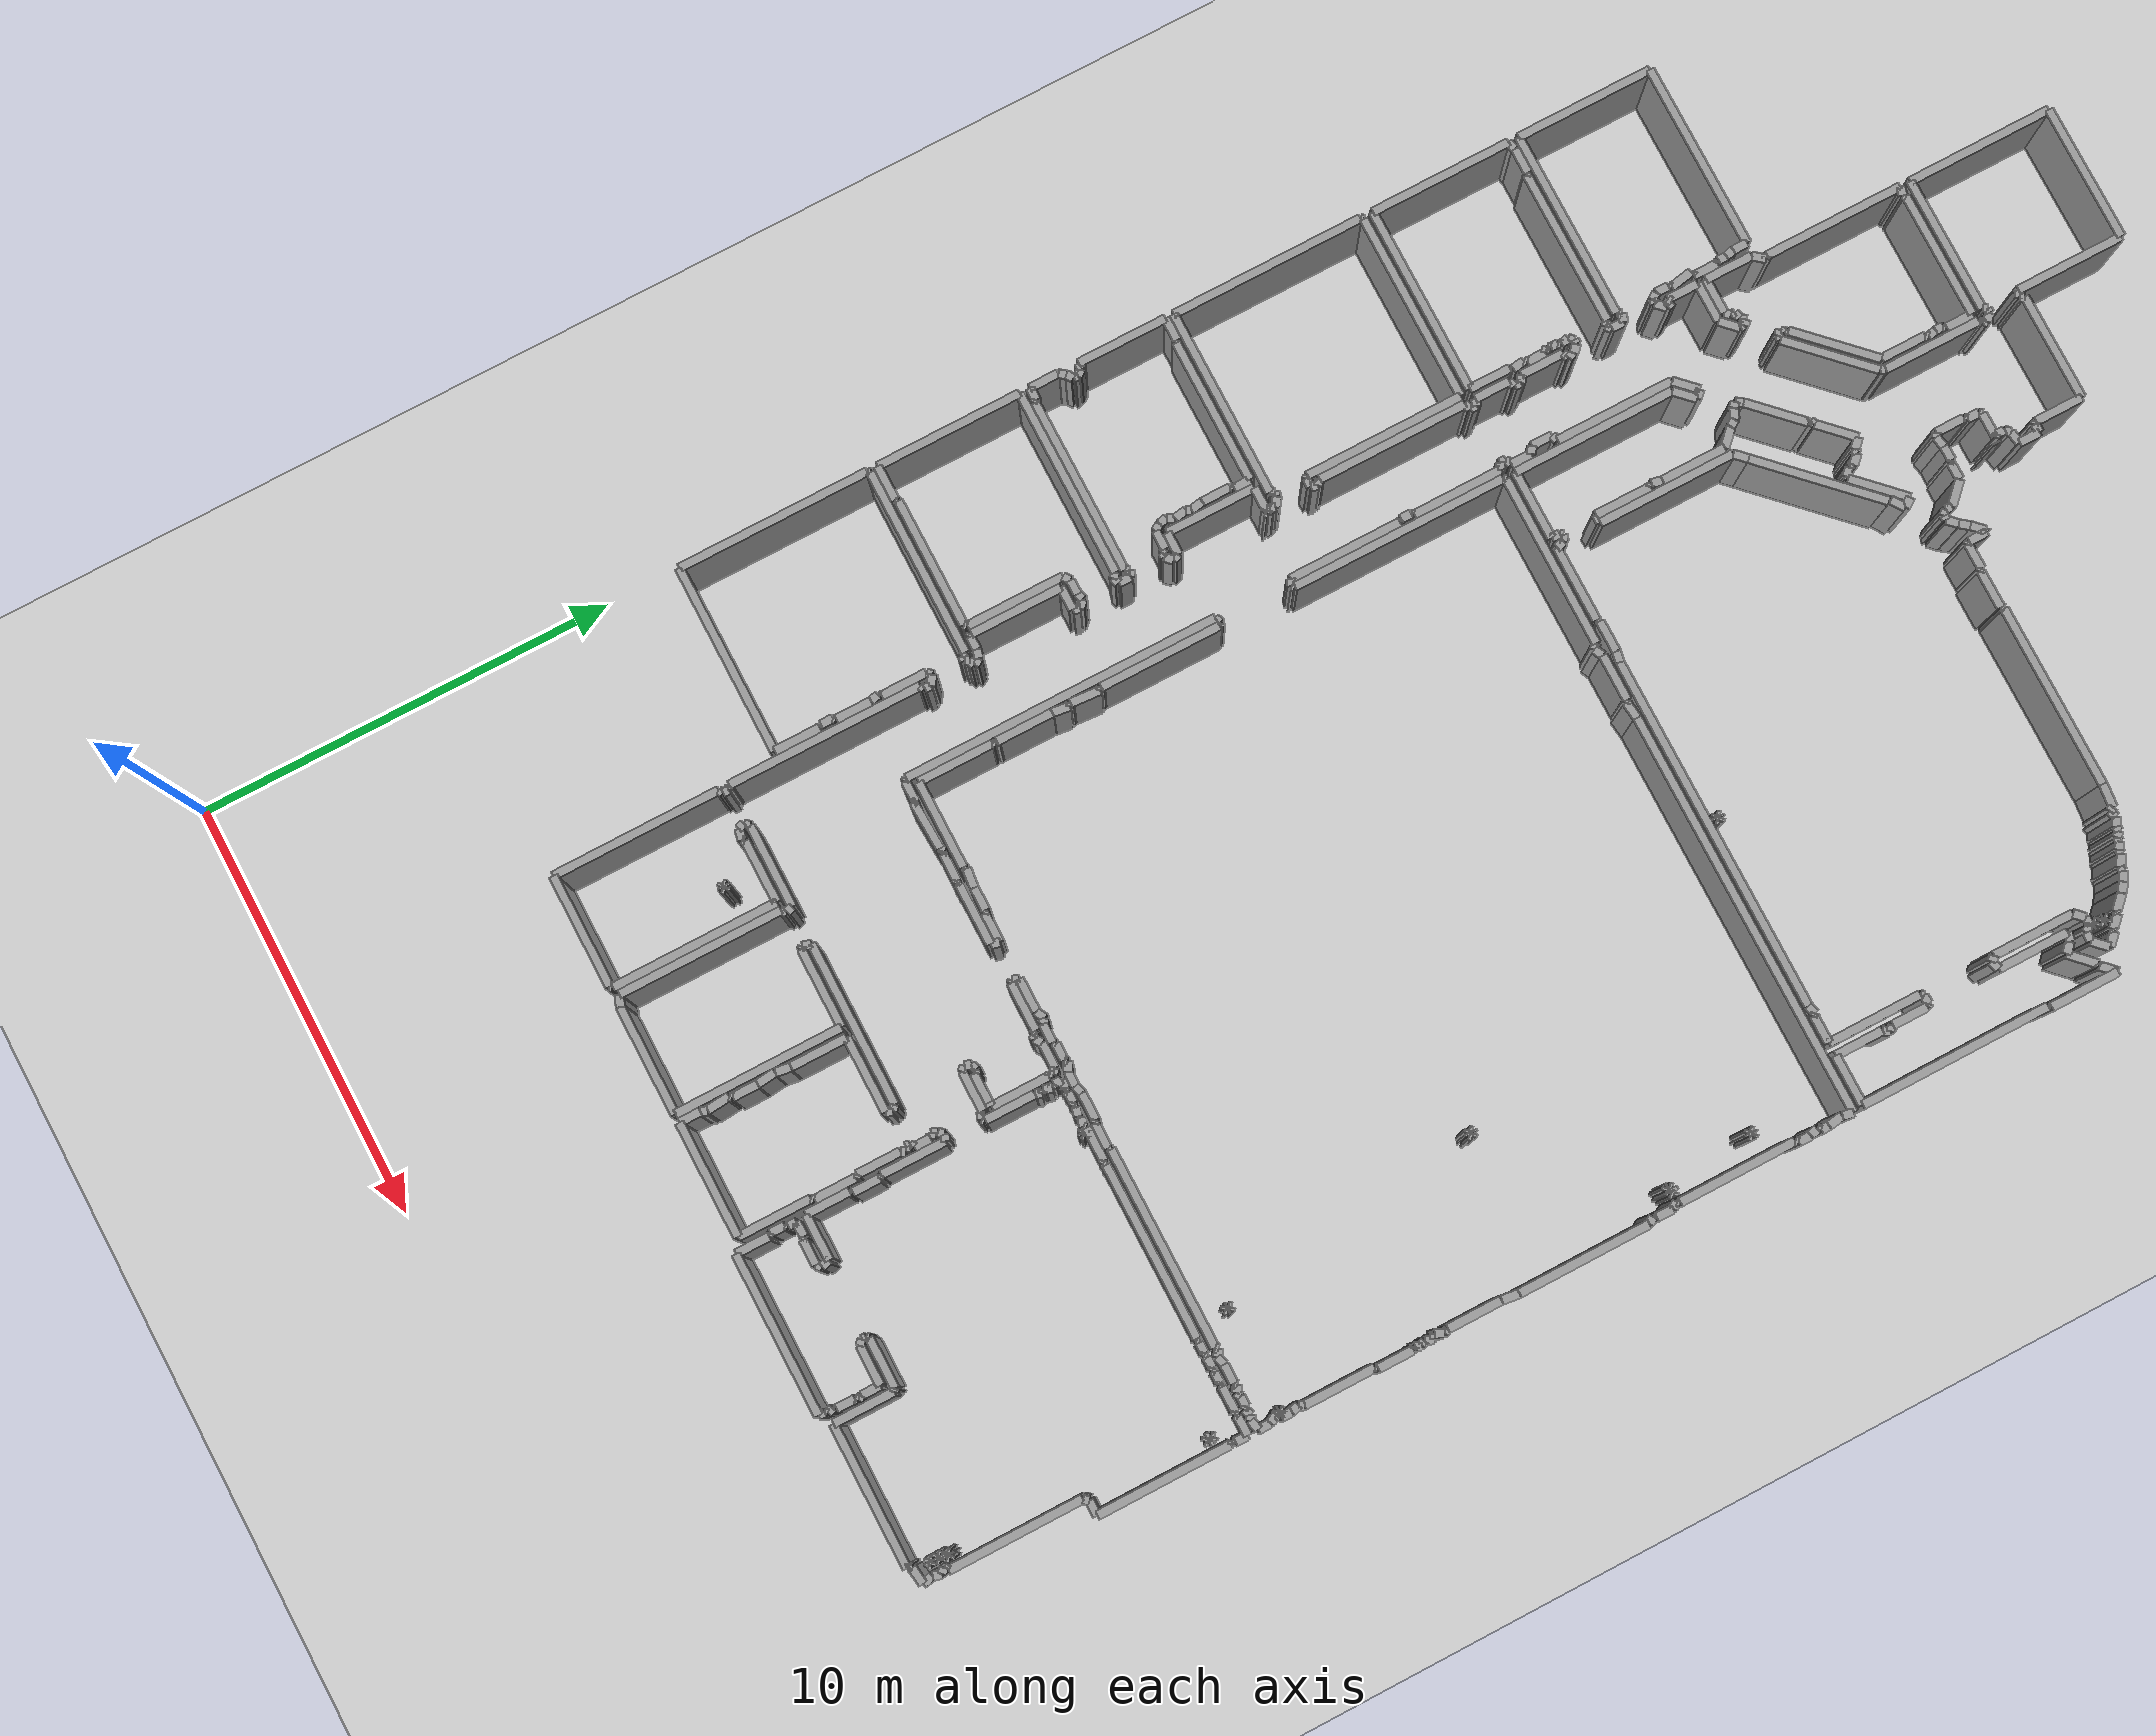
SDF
<?xml version='1.0'?>
        <sdf version='1.4'>
            <world name='1_wall'>
                <light name='sun' type='directional'>
                    <cast_shadows>1</cast_shadows>
                    <pose>0 0 10 0 -0 0</pose>
                    <diffuse>0.8 0.8 0.8 1</diffuse>
                    <specular>0.2 0.2 0.2 1</specular>
                    <attenuation>
                    <range>1000</range>
                    <constant>0.9</constant>
                    <linear>0.01</linear>
                    <quadratic>0.001</quadratic>
                    </attenuation>
                    <direction>-0.5 0.1 -0.9</direction>
                </light>
                <model name='ground_plane'>
                    <static>1</static>
                    <link name='link'>
                        <collision name='collision'>
                        <geometry>
                            <plane>
                                <normal>0 0 1</normal>
                                <size>1000 1000</size>
                            </plane>
                        </geometry>
                        <surface>
                            <friction>
                                <ode>
                                    <mu>100</mu>
                                    <mu2>50</mu2>
                                </ode>
                            </friction>
                            <bounce/>
                                <contact>
                                    <ode/>
                                </contact>
                        </surface>
                        <max_contacts>10</max_contacts>
                        </collision>
                    <visual name='visual'>
                        <cast_shadows>0</cast_shadows>
                        <geometry>
                            <plane>
                                <normal>0 0 1</normal>
                                <size>10000 10000</size>
                            </plane>
                            </geometry>
                                <material>
                                <script>
                                        <uri>file://media/materials/scripts/gazebo.material</uri>
                                        <name>Gazebo/Grey</name>
                                        </script>
                                    </material>
                    </visual>
                    <velocity_decay>
                        <linear>0</linear>
                        <angular>0</angular>
                    </velocity_decay>
                    <self_collide>0</self_collide>
                        <kinematic>0</kinematic>
                        <gravity>1</gravity>
                    </link>
                </model>
                <physics type='ode'>
                    <max_step_size>0.01</max_step_size>
                    <real_time_factor>1</real_time_factor>
                    <real_time_update_rate>100</real_time_update_rate>
                    <gravity>0 0 -9.8</gravity>
                </physics>
            <scene>
                <ambient>0.4 0.4 0.4 1</ambient>
                <background>0.7 0.7 0.7 1</background>
                <shadows>1</shadows>
            </scene>
    <model name='Wall_0'>
     <static>1</static>
    <link name='Wall_0'>
    <collision name='Wall_Collision_0'>
        <geometry>
          <box>
            <size>0.049999999999998934 0.2 2.5</size>
          </box>
        </geometry>
        <pose>0 0 1.25 0 -0 0</pose>
      </collision>
      <visual name='Wall_Visual_0'>
        <pose>0 0 1.25 0 -0 0</pose>
        <geometry>
          <box>
            <size>0.049999999999998934 0.2 2.5</size>
          </box>
        </geometry>
        <material>
          <script>
            <uri>file://media/materials/scripts/gazebo.material</uri>
            <name>Gazebo/Grey</name>
          </script>
        </material>
      </visual>
      <velocity_decay>
        <linear>0</linear>
        <angular>0</angular>
      </velocity_decay>
      <pose>11.475000000000001 38.5 0 0 0 3.141592653589793</pose>
    </link>
     </model><model name='Wall_1'>
     <static>1</static>
    <link name='Wall_1'>
    <collision name='Wall_Collision_1'>
        <geometry>
          <box>
            <size>0.049999999999998934 0.2 2.5</size>
          </box>
        </geometry>
        <pose>0 0 1.25 0 -0 0</pose>
      </collision>
      <visual name='Wall_Visual_1'>
        <pose>0 0 1.25 0 -0 0</pose>
        <geometry>
          <box>
            <size>0.049999999999998934 0.2 2.5</size>
          </box>
        </geometry>
        <material>
          <script>
            <uri>file://media/materials/scripts/gazebo.material</uri>
            <name>Gazebo/Grey</name>
          </script>
        </material>
      </visual>
      <velocity_decay>
        <linear>0</linear>
        <angular>0</angular>
      </velocity_decay>
      <pose>11.475000000000001 38.5 0 0 0 0.0</pose>
    </link>
     </model><model name='Wall_2'>
     <static>1</static>
    <link name='Wall_2'>
    <collision name='Wall_Collision_2'>
        <geometry>
          <box>
            <size>0.0 0.2 2.5</size>
          </box>
        </geometry>
        <pose>0 0 1.25 0 -0 0</pose>
      </collision>
      <visual name='Wall_Visual_2'>
        <pose>0 0 1.25 0 -0 0</pose>
        <geometry>
          <box>
            <size>0.0 0.2 2.5</size>
          </box>
        </geometry>
        <material>
          <script>
            <uri>file://media/materials/scripts/gazebo.material</uri>
            <name>Gazebo/Grey</name>
          </script>
        </material>
      </visual>
      <velocity_decay>
        <linear>0</linear>
        <angular>0</angular>
      </velocity_decay>
      <pose>22.8 14.100000000000001 0 0 0 0.0</pose>
    </link>
     </model><model name='Wall_3'>
     <static>1</static>
    <link name='Wall_3'>
    <collision name='Wall_Collision_3'>
        <geometry>
          <box>
            <size>0.0 0.2 2.5</size>
          </box>
        </geometry>
        <pose>0 0 1.25 0 -0 0</pose>
      </collision>
      <visual name='Wall_Visual_3'>
        <pose>0 0 1.25 0 -0 0</pose>
        <geometry>
          <box>
            <size>0.0 0.2 2.5</size>
          </box>
        </geometry>
        <material>
          <script>
            <uri>file://media/materials/scripts/gazebo.material</uri>
            <name>Gazebo/Grey</name>
          </script>
        </material>
      </visual>
      <velocity_decay>
        <linear>0</linear>
        <angular>0</angular>
      </velocity_decay>
      <pose>22.650000000000002 14.100000000000001 0 0 0 0.0</pose>
    </link>
     </model><model name='Wall_4'>
     <static>1</static>
    <link name='Wall_4'>
    <collision name='Wall_Collision_4'>
        <geometry>
          <box>
            <size>3.849999999999998 0.2 2.5</size>
          </box>
        </geometry>
        <pose>0 0 1.25 0 -0 0</pose>
      </collision>
      <visual name='Wall_Visual_4'>
        <pose>0 0 1.25 0 -0 0</pose>
        <geometry>
          <box>
            <size>3.849999999999998 0.2 2.5</size>
          </box>
        </geometry>
        <material>
          <script>
            <uri>file://media/materials/scripts/gazebo.material</uri>
            <name>Gazebo/Grey</name>
          </script>
        </material>
      </visual>
      <velocity_decay>
        <linear>0</linear>
        <angular>0</angular>
      </velocity_decay>
      <pose>16.275 6.15 0 0 0 3.141592653589793</pose>
    </link>
     </model><model name='Wall_5'>
     <static>1</static>
    <link name='Wall_5'>
    <collision name='Wall_Collision_5'>
        <geometry>
          <box>
            <size>0.7999999999999998 0.2 2.5</size>
          </box>
        </geometry>
        <pose>0 0 1.25 0 -0 0</pose>
      </collision>
      <visual name='Wall_Visual_5'>
        <pose>0 0 1.25 0 -0 0</pose>
        <geometry>
          <box>
            <size>0.7999999999999998 0.2 2.5</size>
          </box>
        </geometry>
        <material>
          <script>
            <uri>file://media/materials/scripts/gazebo.material</uri>
            <name>Gazebo/Grey</name>
          </script>
        </material>
      </visual>
      <velocity_decay>
        <linear>0</linear>
        <angular>0</angular>
      </velocity_decay>
      <pose>14.350000000000001 6.550000000000001 0 0 0 1.5707963267948966</pose>
    </link>
     </model><model name='Wall_6'>
     <static>1</static>
    <link name='Wall_6'>
    <collision name='Wall_Collision_6'>
        <geometry>
          <box>
            <size>0.07071067811865513 0.2 2.5</size>
          </box>
        </geometry>
        <pose>0 0 1.25 0 -0 0</pose>
      </collision>
      <visual name='Wall_Visual_6'>
        <pose>0 0 1.25 0 -0 0</pose>
        <geometry>
          <box>
            <size>0.07071067811865513 0.2 2.5</size>
          </box>
        </geometry>
        <material>
          <script>
            <uri>file://media/materials/scripts/gazebo.material</uri>
            <name>Gazebo/Grey</name>
          </script>
        </material>
      </visual>
      <velocity_decay>
        <linear>0</linear>
        <angular>0</angular>
      </velocity_decay>
      <pose>14.325000000000001 6.975 0 0 0 2.3561944901923537</pose>
    </link>
     </model><model name='Wall_7'>
     <static>1</static>
    <link name='Wall_7'>
    <collision name='Wall_Collision_7'>
        <geometry>
          <box>
            <size>0.35000000000000053 0.2 2.5</size>
          </box>
        </geometry>
        <pose>0 0 1.25 0 -0 0</pose>
      </collision>
      <visual name='Wall_Visual_7'>
        <pose>0 0 1.25 0 -0 0</pose>
        <geometry>
          <box>
            <size>0.35000000000000053 0.2 2.5</size>
          </box>
        </geometry>
        <material>
          <script>
            <uri>file://media/materials/scripts/gazebo.material</uri>
            <name>Gazebo/Grey</name>
          </script>
        </material>
      </visual>
      <velocity_decay>
        <linear>0</linear>
        <angular>0</angular>
      </velocity_decay>
      <pose>14.3 7.175000000000001 0 0 0 1.5707963267948966</pose>
    </link>
     </model><model name='Wall_8'>
     <static>1</static>
    <link name='Wall_8'>
    <collision name='Wall_Collision_8'>
        <geometry>
          <box>
            <size>0.07071067811865513 0.2 2.5</size>
          </box>
        </geometry>
        <pose>0 0 1.25 0 -0 0</pose>
      </collision>
      <visual name='Wall_Visual_8'>
        <pose>0 0 1.25 0 -0 0</pose>
        <geometry>
          <box>
            <size>0.07071067811865513 0.2 2.5</size>
          </box>
        </geometry>
        <material>
          <script>
            <uri>file://media/materials/scripts/gazebo.material</uri>
            <name>Gazebo/Grey</name>
          </script>
        </material>
      </visual>
      <velocity_decay>
        <linear>0</linear>
        <angular>0</angular>
      </velocity_decay>
      <pose>14.325000000000001 7.375 0 0 0 0.7853981633974394</pose>
    </link>
     </model><model name='Wall_9'>
     <static>1</static>
    <link name='Wall_9'>
    <collision name='Wall_Collision_9'>
        <geometry>
          <box>
            <size>0.20000000000000018 0.2 2.5</size>
          </box>
        </geometry>
        <pose>0 0 1.25 0 -0 0</pose>
      </collision>
      <visual name='Wall_Visual_9'>
        <pose>0 0 1.25 0 -0 0</pose>
        <geometry>
          <box>
            <size>0.20000000000000018 0.2 2.5</size>
          </box>
        </geometry>
        <material>
          <script>
            <uri>file://media/materials/scripts/gazebo.material</uri>
            <name>Gazebo/Grey</name>
          </script>
        </material>
      </visual>
      <velocity_decay>
        <linear>0</linear>
        <angular>0</angular>
      </velocity_decay>
      <pose>14.350000000000001 7.5 0 0 0 1.5707963267948966</pose>
    </link>
     </model><model name='Wall_10'>
     <static>1</static>
    <link name='Wall_10'>
    <collision name='Wall_Collision_10'>
        <geometry>
          <box>
            <size>0.34999999999999964 0.2 2.5</size>
          </box>
        </geometry>
        <pose>0 0 1.25 0 -0 0</pose>
      </collision>
      <visual name='Wall_Visual_10'>
        <pose>0 0 1.25 0 -0 0</pose>
        <geometry>
          <box>
            <size>0.34999999999999964 0.2 2.5</size>
          </box>
        </geometry>
        <material>
          <script>
            <uri>file://media/materials/scripts/gazebo.material</uri>
            <name>Gazebo/Grey</name>
          </script>
        </material>
      </visual>
      <velocity_decay>
        <linear>0</linear>
        <angular>0</angular>
      </velocity_decay>
      <pose>14.525000000000002 7.6000000000000005 0 0 0 0.0</pose>
    </link>
     </model><model name='Wall_11'>
     <static>1</static>
    <link name='Wall_11'>
    <collision name='Wall_Collision_11'>
        <geometry>
          <box>
            <size>0.07071067811865388 0.2 2.5</size>
          </box>
        </geometry>
        <pose>0 0 1.25 0 -0 0</pose>
      </collision>
      <visual name='Wall_Visual_11'>
        <pose>0 0 1.25 0 -0 0</pose>
        <geometry>
          <box>
            <size>0.07071067811865388 0.2 2.5</size>
          </box>
        </geometry>
        <material>
          <script>
            <uri>file://media/materials/scripts/gazebo.material</uri>
            <name>Gazebo/Grey</name>
          </script>
        </material>
      </visual>
      <velocity_decay>
        <linear>0</linear>
        <angular>0</angular>
      </velocity_decay>
      <pose>14.725000000000001 7.575000000000001 0 0 0 -0.7853981633974572</pose>
    </link>
     </model><model name='Wall_12'>
     <static>1</static>
    <link name='Wall_12'>
    <collision name='Wall_Collision_12'>
        <geometry>
          <box>
            <size>0.6000000000000014 0.2 2.5</size>
          </box>
        </geometry>
        <pose>0 0 1.25 0 -0 0</pose>
      </collision>
      <visual name='Wall_Visual_12'>
        <pose>0 0 1.25 0 -0 0</pose>
        <geometry>
          <box>
            <size>0.6000000000000014 0.2 2.5</size>
          </box>
        </geometry>
        <material>
          <script>
            <uri>file://media/materials/scripts/gazebo.material</uri>
            <name>Gazebo/Grey</name>
          </script>
        </material>
      </visual>
      <velocity_decay>
        <linear>0</linear>
        <angular>0</angular>
      </velocity_decay>
      <pose>15.05 7.550000000000001 0 0 0 0.0</pose>
    </link>
     </model><model name='Wall_13'>
     <static>1</static>
    <link name='Wall_13'>
    <collision name='Wall_Collision_13'>
        <geometry>
          <box>
            <size>0.141421356237309 0.2 2.5</size>
          </box>
        </geometry>
        <pose>0 0 1.25 0 -0 0</pose>
      </collision>
      <visual name='Wall_Visual_13'>
        <pose>0 0 1.25 0 -0 0</pose>
        <geometry>
          <box>
            <size>0.141421356237309 0.2 2.5</size>
          </box>
        </geometry>
        <material>
          <script>
            <uri>file://media/materials/scripts/gazebo.material</uri>
            <name>Gazebo/Grey</name>
          </script>
        </material>
      </visual>
      <velocity_decay>
        <linear>0</linear>
        <angular>0</angular>
      </velocity_decay>
      <pose>15.400000000000002 7.6000000000000005 0 0 0 0.7853981633974483</pose>
    </link>
     </model><model name='Wall_14'>
     <static>1</static>
    <link name='Wall_14'>
    <collision name='Wall_Collision_14'>
        <geometry>
          <box>
            <size>0.20615528128088337 0.2 2.5</size>
          </box>
        </geometry>
        <pose>0 0 1.25 0 -0 0</pose>
      </collision>
      <visual name='Wall_Visual_14'>
        <pose>0 0 1.25 0 -0 0</pose>
        <geometry>
          <box>
            <size>0.20615528128088337 0.2 2.5</size>
          </box>
        </geometry>
        <material>
          <script>
            <uri>file://media/materials/scripts/gazebo.material</uri>
            <name>Gazebo/Grey</name>
          </script>
        </material>
      </visual>
      <velocity_decay>
        <linear>0</linear>
        <angular>0</angular>
      </velocity_decay>
      <pose>15.425 7.75 0 0 0 1.815774989921764</pose>
    </link>
     </model><model name='Wall_15'>
     <static>1</static>
    <link name='Wall_15'>
    <collision name='Wall_Collision_15'>
        <geometry>
          <box>
            <size>1.0999999999999996 0.2 2.5</size>
          </box>
        </geometry>
        <pose>0 0 1.25 0 -0 0</pose>
      </collision>
      <visual name='Wall_Visual_15'>
        <pose>0 0 1.25 0 -0 0</pose>
        <geometry>
          <box>
            <size>1.0999999999999996 0.2 2.5</size>
          </box>
        </geometry>
        <material>
          <script>
            <uri>file://media/materials/scripts/gazebo.material</uri>
            <name>Gazebo/Grey</name>
          </script>
        </material>
      </visual>
      <velocity_decay>
        <linear>0</linear>
        <angular>0</angular>
      </velocity_decay>
      <pose>14.850000000000001 7.8500000000000005 0 0 0 3.141592653589793</pose>
    </link>
     </model><model name='Wall_16'>
     <static>1</static>
    <link name='Wall_16'>
    <collision name='Wall_Collision_16'>
        <geometry>
          <box>
            <size>1.0499999999999998 0.2 2.5</size>
          </box>
        </geometry>
        <pose>0 0 1.25 0 -0 0</pose>
      </collision>
      <visual name='Wall_Visual_16'>
        <pose>0 0 1.25 0 -0 0</pose>
        <geometry>
          <box>
            <size>1.0499999999999998 0.2 2.5</size>
          </box>
        </geometry>
        <material>
          <script>
            <uri>file://media/materials/scripts/gazebo.material</uri>
            <name>Gazebo/Grey</name>
          </script>
        </material>
      </visual>
      <velocity_decay>
        <linear>0</linear>
        <angular>0</angular>
      </velocity_decay>
      <pose>14.3 8.375 0 0 0 1.5707963267948966</pose>
    </link>
     </model><model name='Wall_17'>
     <static>1</static>
    <link name='Wall_17'>
    <collision name='Wall_Collision_17'>
        <geometry>
          <box>
            <size>0.07071067811865576 0.2 2.5</size>
          </box>
        </geometry>
        <pose>0 0 1.25 0 -0 0</pose>
      </collision>
      <visual name='Wall_Visual_17'>
        <pose>0 0 1.25 0 -0 0</pose>
        <geometry>
          <box>
            <size>0.07071067811865576 0.2 2.5</size>
          </box>
        </geometry>
        <material>
          <script>
            <uri>file://media/materials/scripts/gazebo.material</uri>
            <name>Gazebo/Grey</name>
          </script>
        </material>
      </visual>
      <velocity_decay>
        <linear>0</linear>
        <angular>0</angular>
      </velocity_decay>
      <pose>14.325000000000001 8.925 0 0 0 0.7853981633974483</pose>
    </link>
     </model><model name='Wall_18'>
     <static>1</static>
    <link name='Wall_18'>
    <collision name='Wall_Collision_18'>
        <geometry>
          <box>
            <size>0.6500000000000004 0.2 2.5</size>
          </box>
        </geometry>
        <pose>0 0 1.25 0 -0 0</pose>
      </collision>
      <visual name='Wall_Visual_18'>
        <pose>0 0 1.25 0 -0 0</pose>
        <geometry>
          <box>
            <size>0.6500000000000004 0.2 2.5</size>
          </box>
        </geometry>
        <material>
          <script>
            <uri>file://media/materials/scripts/gazebo.material</uri>
            <name>Gazebo/Grey</name>
          </script>
        </material>
      </visual>
      <velocity_decay>
        <linear>0</linear>
        <angular>0</angular>
      </velocity_decay>
      <pose>14.350000000000001 9.275000000000002 0 0 0 1.5707963267948966</pose>
    </link>
     </model><model name='Wall_19'>
     <static>1</static>
    <link name='Wall_19'>
    <collision name='Wall_Collision_19'>
        <geometry>
          <box>
            <size>0.0707106781186545 0.2 2.5</size>
          </box>
        </geometry>
        <pose>0 0 1.25 0 -0 0</pose>
      </collision>
      <visual name='Wall_Visual_19'>
        <pose>0 0 1.25 0 -0 0</pose>
        <geometry>
          <box>
            <size>0.0707106781186545 0.2 2.5</size>
          </box>
        </geometry>
        <material>
          <script>
            <uri>file://media/materials/scripts/gazebo.material</uri>
            <name>Gazebo/Grey</name>
          </script>
        </material>
      </visual>
      <velocity_decay>
        <linear>0</linear>
        <angular>0</angular>
      </velocity_decay>
      <pose>14.325000000000001 9.625 0 0 0 2.3561944901923626</pose>
    </link>
     </model><model name='Wall_20'>
     <static>1</static>
    <link name='Wall_20'>
    <collision name='Wall_Collision_20'>
        <geometry>
          <box>
            <size>1.5500000000000007 0.2 2.5</size>
          </box>
        </geometry>
        <pose>0 0 1.25 0 -0 0</pose>
      </collision>
      <visual name='Wall_Visual_20'>
        <pose>0 0 1.25 0 -0 0</pose>
        <geometry>
          <box>
            <size>1.5500000000000007 0.2 2.5</size>
          </box>
        </geometry>
        <material>
          <script>
            <uri>file://media/materials/scripts/gazebo.material</uri>
            <name>Gazebo/Grey</name>
          </script>
        </material>
      </visual>
      <velocity_decay>
        <linear>0</linear>
        <angular>0</angular>
      </velocity_decay>
      <pose>14.3 10.425 0 0 0 1.5707963267948966</pose>
    </link>
     </model><model name='Wall_21'>
     <static>1</static>
    <link name='Wall_21'>
    <collision name='Wall_Collision_21'>
        <geometry>
          <box>
            <size>0.15811388300841897 0.2 2.5</size>
          </box>
        </geometry>
        <pose>0 0 1.25 0 -0 0</pose>
      </collision>
      <visual name='Wall_Visual_21'>
        <pose>0 0 1.25 0 -0 0</pose>
        <geometry>
          <box>
            <size>0.15811388300841897 0.2 2.5</size>
          </box>
        </geometry>
        <material>
          <script>
            <uri>file://media/materials/scripts/gazebo.material</uri>
            <name>Gazebo/Grey</name>
          </script>
        </material>
      </visual>
      <velocity_decay>
        <linear>0</linear>
        <angular>0</angular>
      </velocity_decay>
      <pose>14.225000000000001 11.225000000000001 0 0 0 2.819842099193158</pose>
    </link>
     </model><model name='Wall_22'>
     <static>1</static>
    <link name='Wall_22'>
    <collision name='Wall_Collision_22'>
        <geometry>
          <box>
            <size>0.141421356237309 0.2 2.5</size>
          </box>
        </geometry>
        <pose>0 0 1.25 0 -0 0</pose>
      </collision>
      <visual name='Wall_Visual_22'>
        <pose>0 0 1.25 0 -0 0</pose>
        <geometry>
          <box>
            <size>0.141421356237309 0.2 2.5</size>
          </box>
        </geometry>
        <material>
          <script>
            <uri>file://media/materials/scripts/gazebo.material</uri>
            <name>Gazebo/Grey</name>
          </script>
        </material>
      </visual>
      <velocity_decay>
        <linear>0</linear>
        <angular>0</angular>
      </velocity_decay>
      <pose>14.100000000000001 11.2 0 0 0 -2.356194490192345</pose>
    </link>
     </model><model name='Wall_23'>
     <static>1</static>
    <link name='Wall_23'>
    <collision name='Wall_Collision_23'>
        <geometry>
          <box>
            <size>0.15811388300841953 0.2 2.5</size>
          </box>
        </geometry>
        <pose>0 0 1.25 0 -0 0</pose>
      </collision>
      <visual name='Wall_Visual_23'>
        <pose>0 0 1.25 0 -0 0</pose>
        <geometry>
          <box>
            <size>0.15811388300841953 0.2 2.5</size>
          </box>
        </geometry>
        <material>
          <script>
            <uri>file://media/materials/scripts/gazebo.material</uri>
            <name>Gazebo/Grey</name>
          </script>
        </material>
      </visual>
      <velocity_decay>
        <linear>0</linear>
        <angular>0</angular>
      </velocity_decay>
      <pose>14.025 11.075 0 0 0 -1.8925468811915425</pose>
    </link>
     </model><model name='Wall_24'>
     <static>1</static>
    <link name='Wall_24'>
    <collision name='Wall_Collision_24'>
        <geometry>
          <box>
            <size>0.11180339887499027 0.2 2.5</size>
          </box>
        </geometry>
        <pose>0 0 1.25 0 -0 0</pose>
      </collision>
      <visual name='Wall_Visual_24'>
        <pose>0 0 1.25 0 -0 0</pose>
        <geometry>
          <box>
            <size>0.11180339887499027 0.2 2.5</size>
          </box>
        </geometry>
        <material>
          <script>
            <uri>file://media/materials/scripts/gazebo.material</uri>
            <name>Gazebo/Grey</name>
          </script>
        </material>
      </visual>
      <velocity_decay>
        <linear>0</linear>
        <angular>0</angular>
      </velocity_decay>
      <pose>14.05 10.975000000000001 0 0 0 -0.4636476090007919</pose>
    </link>
     </model><model name='Wall_25'>
     <static>1</static>
    <link name='Wall_25'>
    <collision name='Wall_Collision_25'>
        <geometry>
          <box>
            <size>0.40000000000000036 0.2 2.5</size>
          </box>
        </geometry>
        <pose>0 0 1.25 0 -0 0</pose>
      </collision>
      <visual name='Wall_Visual_25'>
        <pose>0 0 1.25 0 -0 0</pose>
        <geometry>
          <box>
            <size>0.40000000000000036 0.2 2.5</size>
          </box>
        </geometry>
        <material>
          <script>
            <uri>file://media/materials/scripts/gazebo.material</uri>
            <name>Gazebo/Grey</name>
          </script>
        </material>
      </visual>
      <velocity_decay>
        <linear>0</linear>
        <angular>0</angular>
      </velocity_decay>
      <pose>14.100000000000001 10.75 0 0 0 -1.5707963267948966</pose>
    </link>
     </model><model name='Wall_26'>
     <static>1</static>
    <link name='Wall_26'>
    <collision name='Wall_Collision_26'>
        <geometry>
          <box>
            <size>0.11180339887499108 0.2 2.5</size>
          </box>
        </geometry>
        <pose>0 0 1.25 0 -0 0</pose>
      </collision>
      <visual name='Wall_Visual_26'>
        <pose>0 0 1.25 0 -0 0</pose>
        <geometry>
          <box>
            <size>0.11180339887499108 0.2 2.5</size>
          </box>
        </geometry>
        <material>
          <script>
            <uri>file://media/materials/scripts/gazebo.material</uri>
            <name>Gazebo/Grey</name>
          </script>
        </material>
      </visual>
      <velocity_decay>
        <linear>0</linear>
        <angular>0</angular>
      </velocity_decay>
      <pose>14.05 10.525 0 0 0 -2.677945044588987</pose>
    </link>
     </model><model name='Wall_27'>
     <static>1</static>
    <link name='Wall_27'>
    <collision name='Wall_Collision_27'>
        <geometry>
          <box>
            <size>0.09999999999999964 0.2 2.5</size>
          </box>
        </geometry>
        <pose>0 0 1.25 0 -0 0</pose>
      </collision>
      <visual name='Wall_Visual_27'>
        <pose>0 0 1.25 0 -0 0</pose>
        <geometry>
          <box>
            <size>0.09999999999999964 0.2 2.5</size>
          </box>
        </geometry>
        <material>
          <script>
            <uri>file://media/materials/scripts/gazebo.material</uri>
            <name>Gazebo/Grey</name>
          </script>
        </material>
      </visual>
      <velocity_decay>
        <linear>0</linear>
        <angular>0</angular>
      </velocity_decay>
      <pose>14.0 10.45 0 0 0 -1.5707963267948966</pose>
    </link>
     </model><model name='Wall_28'>
     <static>1</static>
    <link name='Wall_28'>
    <collision name='Wall_Collision_28'>
        <geometry>
          <box>
            <size>0.11180339887499027 0.2 2.5</size>
          </box>
        </geometry>
        <pose>0 0 1.25 0 -0 0</pose>
      </collision>
      <visual name='Wall_Visual_28'>
        <pose>0 0 1.25 0 -0 0</pose>
        <geometry>
          <box>
            <size>0.11180339887499027 0.2 2.5</size>
          </box>
        </geometry>
        <material>
          <script>
            <uri>file://media/materials/scripts/gazebo.material</uri>
            <name>Gazebo/Grey</name>
          </script>
        </material>
      </visual>
      <velocity_decay>
        <linear>0</linear>
        <angular>0</angular>
      </velocity_decay>
      <pose>14.05 10.375 0 0 0 -0.4636476090007919</pose>
    </link>
     </model><model name='Wall_29'>
     <static>1</static>
    <link name='Wall_29'>
    <collision name='Wall_Collision_29'>
        <geometry>
          <box>
            <size>0.11180339887499108 0.2 2.5</size>
          </box>
        </geometry>
        <pose>0 0 1.25 0 -0 0</pose>
      </collision>
      <visual name='Wall_Visual_29'>
        <pose>0 0 1.25 0 -0 0</pose>
        <geometry>
          <box>
            <size>0.11180339887499108 0.2 2.5</size>
          </box>
        </geometry>
        <material>
          <script>
            <uri>file://media/materials/scripts/gazebo.material</uri>
            <name>Gazebo/Grey</name>
          </script>
        </material>
      </visual>
      <velocity_decay>
        <linear>0</linear>
        <angular>0</angular>
      </velocity_decay>
      <pose>14.075000000000001 10.3 0 0 0 -2.0344439357957027</pose>
    </link>
     </model><model name='Wall_30'>
     <static>1</static>
    <link name='Wall_30'>
    <collision name='Wall_Collision_30'>
        <geometry>
          <box>
            <size>1.049999999999999 0.2 2.5</size>
          </box>
        </geometry>
        <pose>0 0 1.25 0 -0 0</pose>
      </collision>
      <visual name='Wall_Visual_30'>
        <pose>0 0 1.25 0 -0 0</pose>
        <geometry>
          <box>
            <size>1.049999999999999 0.2 2.5</size>
          </box>
        </geometry>
        <material>
          <script>
            <uri>file://media/materials/scripts/gazebo.material</uri>
            <name>Gazebo/Grey</name>
          </script>
        </material>
      </visual>
      <velocity_decay>
        <linear>0</linear>
        <angular>0</angular>
      </velocity_decay>
      <pose>14.05 9.725000000000001 0 0 0 -1.5707963267948966</pose>
    </link>
     </model><model name='Wall_31'>
     <static>1</static>
    <link name='Wall_31'>
    <collision name='Wall_Collision_31'>
        <geometry>
          <box>
            <size>0.07071067811865576 0.2 2.5</size>
          </box>
        </geometry>
        <pose>0 0 1.25 0 -0 0</pose>
      </collision>
      <visual name='Wall_Visual_31'>
        <pose>0 0 1.25 0 -0 0</pose>
        <geometry>
          <box>
            <size>0.07071067811865576 0.2 2.5</size>
          </box>
        </geometry>
        <material>
          <script>
            <uri>file://media/materials/scripts/gazebo.material</uri>
            <name>Gazebo/Grey</name>
          </script>
        </material>
      </visual>
      <velocity_decay>
        <linear>0</linear>
        <angular>0</angular>
      </velocity_decay>
      <pose>14.075000000000001 9.175 0 0 0 -0.7853981633974483</pose>
    </link>
     </model><model name='Wall_32'>
     <static>1</static>
    <link name='Wall_32'>
    <collision name='Wall_Collision_32'>
        <geometry>
          <box>
            <size>1.0 0.2 2.5</size>
          </box>
        </geometry>
        <pose>0 0 1.25 0 -0 0</pose>
      </collision>
      <visual name='Wall_Visual_32'>
        <pose>0 0 1.25 0 -0 0</pose>
        <geometry>
          <box>
            <size>1.0 0.2 2.5</size>
          </box>
        </geometry>
        <material>
          <script>
            <uri>file://media/materials/scripts/gazebo.material</uri>
            <name>Gazebo/Grey</name>
          </script>
        </material>
      </visual>
      <velocity_decay>
        <linear>0</linear>
        <angular>0</angular>
      </velocity_decay>
      <pose>14.100000000000001 8.65 0 0 0 -1.5707963267948966</pose>
    </link>
     </model><model name='Wall_33'>
     <static>1</static>
    <link name='Wall_33'>
    <collision name='Wall_Collision_33'>
        <geometry>
          <box>
            <size>0.07071067811865576 0.2 2.5</size>
          </box>
        </geometry>
        <pose>0 0 1.25 0 -0 0</pose>
      </collision>
      <visual name='Wall_Visual_33'>
        <pose>0 0 1.25 0 -0 0</pose>
        <geometry>
          <box>
            <size>0.07071067811865576 0.2 2.5</size>
          </box>
        </geometry>
        <material>
          <script>
            <uri>file://media/materials/scripts/gazebo.material</uri>
            <name>Gazebo/Grey</name>
          </script>
        </material>
      </visual>
      <velocity_decay>
        <linear>0</linear>
        <angular>0</angular>
      </velocity_decay>
      <pose>14.075000000000001 8.125 0 0 0 -2.356194490192345</pose>
    </link>
     </model><model name='Wall_34'>
     <static>1</static>
    <link name='Wall_34'>
    <collision name='Wall_Collision_34'>
        <geometry>
          <box>
            <size>1.7499999999999991 0.2 2.5</size>
          </box>
        </geometry>
        <pose>0 0 1.25 0 -0 0</pose>
      </collision>
      <visual name='Wall_Visual_34'>
        <pose>0 0 1.25 0 -0 0</pose>
        <geometry>
          <box>
            <size>1.7499999999999991 0.2 2.5</size>
          </box>
        </geometry>
        <material>
          <script>
            <uri>file://media/materials/scripts/gazebo.material</uri>
            <name>Gazebo/Grey</name>
          </script>
        </material>
      </visual>
      <velocity_decay>
        <linear>0</linear>
        <angular>0</angular>
      </velocity_decay>
      <pose>14.05 7.225 0 0 0 -1.5707963267948966</pose>
    </link>
     </model><model name='Wall_35'>
     <static>1</static>
    <link name='Wall_35'>
    <collision name='Wall_Collision_35'>
        <geometry>
          <box>
            <size>2.75 0.2 2.5</size>
          </box>
        </geometry>
        <pose>0 0 1.25 0 -0 0</pose>
      </collision>
      <visual name='Wall_Visual_35'>
        <pose>0 0 1.25 0 -0 0</pose>
        <geometry>
          <box>
            <size>2.75 0.2 2.5</size>
          </box>
        </geometry>
        <material>
          <script>
            <uri>file://media/materials/scripts/gazebo.material</uri>
            <name>Gazebo/Grey</name>
          </script>
        </material>
      </visual>
      <velocity_decay>
        <linear>0</linear>
        <angular>0</angular>
      </velocity_decay>
      <pose>12.675 6.3500000000000005 0 0 0 3.141592653589793</pose>
    </link>
     </model><model name='Wall_36'>
     <static>1</static>
    <link name='Wall_36'>
    <collision name='Wall_Collision_36'>
        <geometry>
          <box>
            <size>0.5 0.2 2.5</size>
          </box>
        </geometry>
        <pose>0 0 1.25 0 -0 0</pose>
      </collision>
      <visual name='Wall_Visual_36'>
        <pose>0 0 1.25 0 -0 0</pose>
        <geometry>
          <box>
            <size>0.5 0.2 2.5</size>
          </box>
        </geometry>
        <material>
          <script>
            <uri>file://media/materials/scripts/gazebo.material</uri>
            <name>Gazebo/Grey</name>
          </script>
        </material>
      </visual>
      <velocity_decay>
        <linear>0</linear>
        <angular>0</angular>
      </velocity_decay>
      <pose>11.3 6.6000000000000005 0 0 0 1.5707963267948966</pose>
    </link>
     </model><model name='Wall_37'>
     <static>1</static>
    <link name='Wall_37'>
    <collision name='Wall_Collision_37'>
        <geometry>
          <box>
            <size>0.1581138830084187 0.2 2.5</size>
          </box>
        </geometry>
        <pose>0 0 1.25 0 -0 0</pose>
      </collision>
      <visual name='Wall_Visual_37'>
        <pose>0 0 1.25 0 -0 0</pose>
        <geometry>
          <box>
            <size>0.1581138830084187 0.2 2.5</size>
          </box>
        </geometry>
        <material>
          <script>
            <uri>file://media/materials/scripts/gazebo.material</uri>
            <name>Gazebo/Grey</name>
          </script>
        </material>
      </visual>
      <velocity_decay>
        <linear>0</linear>
        <angular>0</angular>
      </velocity_decay>
      <pose>11.325000000000001 6.925000000000001 0 0 0 1.249045772398249</pose>
    </link>
     </model><model name='Wall_38'>
     <static>1</static>
    <link name='Wall_38'>
    <collision name='Wall_Collision_38'>
        <geometry>
          <box>
            <size>0.5522680508593638 0.2 2.5</size>
          </box>
        </geometry>
        <pose>0 0 1.25 0 -0 0</pose>
      </collision>
      <visual name='Wall_Visual_38'>
        <pose>0 0 1.25 0 -0 0</pose>
        <geometry>
          <box>
            <size>0.5522680508593638 0.2 2.5</size>
          </box>
        </geometry>
        <material>
          <script>
            <uri>file://media/materials/scripts/gazebo.material</uri>
            <name>Gazebo/Grey</name>
          </script>
        </material>
      </visual>
      <velocity_decay>
        <linear>0</linear>
        <angular>0</angular>
      </velocity_decay>
      <pose>11.325000000000001 7.275 0 0 0 1.6614562139956428</pose>
    </link>
     </model><model name='Wall_39'>
     <static>1</static>
    <link name='Wall_39'>
    <collision name='Wall_Collision_39'>
        <geometry>
          <box>
            <size>0.07071067811865513 0.2 2.5</size>
          </box>
        </geometry>
        <pose>0 0 1.25 0 -0 0</pose>
      </collision>
      <visual name='Wall_Visual_39'>
        <pose>0 0 1.25 0 -0 0</pose>
        <geometry>
          <box>
            <size>0.07071067811865513 0.2 2.5</size>
          </box>
        </geometry>
        <material>
          <script>
            <uri>file://media/materials/scripts/gazebo.material</uri>
            <name>Gazebo/Grey</name>
          </script>
        </material>
      </visual>
      <velocity_decay>
        <linear>0</linear>
        <angular>0</angular>
      </velocity_decay>
      <pose>11.325000000000001 7.575000000000001 0 0 0 0.7853981633974394</pose>
    </link>
     </model><model name='Wall_40'>
     <static>1</static>
    <link name='Wall_40'>
    <collision name='Wall_Collision_40'>
        <geometry>
          <box>
            <size>0.6000000000000005 0.2 2.5</size>
          </box>
        </geometry>
        <pose>0 0 1.25 0 -0 0</pose>
      </collision>
      <visual name='Wall_Visual_40'>
        <pose>0 0 1.25 0 -0 0</pose>
        <geometry>
          <box>
            <size>0.6000000000000005 0.2 2.5</size>
          </box>
        </geometry>
        <material>
          <script>
            <uri>file://media/materials/scripts/gazebo.material</uri>
            <name>Gazebo/Grey</name>
          </script>
        </material>
      </visual>
      <velocity_decay>
        <linear>0</linear>
        <angular>0</angular>
      </velocity_decay>
      <pose>11.350000000000001 7.9 0 0 0 1.5707963267948966</pose>
    </link>
     </model><model name='Wall_41'>
     <static>1</static>
    <link name='Wall_41'>
    <collision name='Wall_Collision_41'>
        <geometry>
          <box>
            <size>0.4527692569068702 0.2 2.5</size>
          </box>
        </geometry>
        <pose>0 0 1.25 0 -0 0</pose>
      </collision>
      <visual name='Wall_Visual_41'>
        <pose>0 0 1.25 0 -0 0</pose>
        <geometry>
          <box>
            <size>0.4527692569068702 0.2 2.5</size>
          </box>
        </geometry>
        <material>
          <script>
            <uri>file://media/materials/scripts/gazebo.material</uri>
            <name>Gazebo/Grey</name>
          </script>
        </material>
      </visual>
      <velocity_decay>
        <linear>0</linear>
        <angular>0</angular>
      </velocity_decay>
      <pose>11.325000000000001 8.425 0 0 0 1.681453547968794</pose>
    </link>
     </model><model name='Wall_42'>
     <static>1</static>
    <link name='Wall_42'>
    <collision name='Wall_Collision_42'>
        <geometry>
          <box>
            <size>0.3535533905932735 0.2 2.5</size>
          </box>
        </geometry>
        <pose>0 0 1.25 0 -0 0</pose>
      </collision>
      <visual name='Wall_Visual_42'>
        <pose>0 0 1.25 0 -0 0</pose>
        <geometry>
          <box>
            <size>0.3535533905932735 0.2 2.5</size>
          </box>
        </geometry>
        <material>
          <script>
            <uri>file://media/materials/scripts/gazebo.material</uri>
            <name>Gazebo/Grey</name>
          </script>
        </material>
      </visual>
      <velocity_decay>
        <linear>0</linear>
        <angular>0</angular>
      </velocity_decay>
      <pose>11.325000000000001 8.825 0 0 0 1.4288992721907305</pose>
    </link>
     </model><model name='Wall_43'>
     <static>1</static>
    <link name='Wall_43'>
    <collision name='Wall_Collision_43'>
        <geometry>
          <box>
            <size>1.3500000000000014 0.2 2.5</size>
          </box>
        </geometry>
        <pose>0 0 1.25 0 -0 0</pose>
      </collision>
      <visual name='Wall_Visual_43'>
        <pose>0 0 1.25 0 -0 0</pose>
        <geometry>
          <box>
            <size>1.3500000000000014 0.2 2.5</size>
          </box>
        </geometry>
        <material>
          <script>
            <uri>file://media/materials/scripts/gazebo.material</uri>
            <name>Gazebo/Grey</name>
          </script>
        </material>
      </visual>
      <velocity_decay>
        <linear>0</linear>
        <angular>0</angular>
      </velocity_decay>
      <pose>11.350000000000001 9.675 0 0 0 1.5707963267948966</pose>
    </link>
     </model><model name='Wall_44'>
     <static>1</static>
    <link name='Wall_44'>
    <collision name='Wall_Collision_44'>
        <geometry>
          <box>
            <size>1.799999999999999 0.2 2.5</size>
          </box>
        </geometry>
        <pose>0 0 1.25 0 -0 0</pose>
      </collision>
      <visual name='Wall_Visual_44'>
        <pose>0 0 1.25 0 -0 0</pose>
        <geometry>
          <box>
            <size>1.799999999999999 0.2 2.5</size>
          </box>
        </geometry>
        <material>
          <script>
            <uri>file://media/materials/scripts/gazebo.material</uri>
            <name>Gazebo/Grey</name>
          </script>
        </material>
      </visual>
      <velocity_decay>
        <linear>0</linear>
        <angular>0</angular>
      </velocity_decay>
      <pose>12.25 10.350000000000001 0 0 0 0.0</pose>
    </link>
     </model><model name='Wall_45'>
     <static>1</static>
    <link name='Wall_45'>
    <collision name='Wall_Collision_45'>
        <geometry>
          <box>
            <size>0.15811388300841783 0.2 2.5</size>
          </box>
        </geometry>
        <pose>0 0 1.25 0 -0 0</pose>
      </collision>
      <visual name='Wall_Visual_45'>
        <pose>0 0 1.25 0 -0 0</pose>
        <geometry>
          <box>
            <size>0.15811388300841783 0.2 2.5</size>
          </box>
        </geometry>
        <material>
          <script>
            <uri>file://media/materials/scripts/gazebo.material</uri>
            <name>Gazebo/Grey</name>
          </script>
        </material>
      </visual>
      <velocity_decay>
        <linear>0</linear>
        <angular>0</angular>
      </velocity_decay>
      <pose>13.175 10.425 0 0 0 1.2490457723982473</pose>
    </link>
     </model><model name='Wall_46'>
     <static>1</static>
    <link name='Wall_46'>
    <collision name='Wall_Collision_46'>
        <geometry>
          <box>
            <size>0.14142135623731025 0.2 2.5</size>
          </box>
        </geometry>
        <pose>0 0 1.25 0 -0 0</pose>
      </collision>
      <visual name='Wall_Visual_46'>
        <pose>0 0 1.25 0 -0 0</pose>
        <geometry>
          <box>
            <size>0.14142135623731025 0.2 2.5</size>
          </box>
        </geometry>
        <material>
          <script>
            <uri>file://media/materials/scripts/gazebo.material</uri>
            <name>Gazebo/Grey</name>
          </script>
        </material>
      </visual>
      <velocity_decay>
        <linear>0</linear>
        <angular>0</angular>
      </velocity_decay>
      <pose>13.150000000000002 10.55 0 0 0 2.356194490192336</pose>
    </link>
     </model><model name='Wall_47'>
     <static>1</static>
    <link name='Wall_47'>
    <collision name='Wall_Collision_47'>
        <geometry>
          <box>
            <size>3.9000000000000004 0.2 2.5</size>
          </box>
        </geometry>
        <pose>0 0 1.25 0 -0 0</pose>
      </collision>
      <visual name='Wall_Visual_47'>
        <pose>0 0 1.25 0 -0 0</pose>
        <geometry>
          <box>
            <size>3.9000000000000004 0.2 2.5</size>
          </box>
        </geometry>
        <material>
          <script>
            <uri>file://media/materials/scripts/gazebo.material</uri>
            <name>Gazebo/Grey</name>
          </script>
        </material>
      </visual>
      <velocity_decay>
        <linear>0</linear>
        <angular>0</angular>
      </velocity_decay>
      <pose>11.150000000000002 10.600000000000001 0 0 0 3.141592653589793</pose>
    </link>
     </model><model name='Wall_48'>
     <static>1</static>
    <link name='Wall_48'>
    <collision name='Wall_Collision_48'>
        <geometry>
          <box>
            <size>0.20615528128088423 0.2 2.5</size>
          </box>
        </geometry>
        <pose>0 0 1.25 0 -0 0</pose>
      </collision>
      <visual name='Wall_Visual_48'>
        <pose>0 0 1.25 0 -0 0</pose>
        <geometry>
          <box>
            <size>0.20615528128088423 0.2 2.5</size>
          </box>
        </geometry>
        <material>
          <script>
            <uri>file://media/materials/scripts/gazebo.material</uri>
            <name>Gazebo/Grey</name>
          </script>
        </material>
      </visual>
      <velocity_decay>
        <linear>0</linear>
        <angular>0</angular>
      </velocity_decay>
      <pose>9.175 10.5 0 0 0 -1.8157749899217628</pose>
    </link>
     </model><model name='Wall_49'>
     <static>1</static>
    <link name='Wall_49'>
    <collision name='Wall_Collision_49'>
        <geometry>
          <box>
            <size>0.0707106781186545 0.2 2.5</size>
          </box>
        </geometry>
        <pose>0 0 1.25 0 -0 0</pose>
      </collision>
      <visual name='Wall_Visual_49'>
        <pose>0 0 1.25 0 -0 0</pose>
        <geometry>
          <box>
            <size>0.0707106781186545 0.2 2.5</size>
          </box>
        </geometry>
        <material>
          <script>
            <uri>file://media/materials/scripts/gazebo.material</uri>
            <name>Gazebo/Grey</name>
          </script>
        </material>
      </visual>
      <velocity_decay>
        <linear>0</linear>
        <angular>0</angular>
      </velocity_decay>
      <pose>9.175 10.375 0 0 0 -0.7853981633974305</pose>
    </link>
     </model><model name='Wall_50'>
     <static>1</static>
    <link name='Wall_50'>
    <collision name='Wall_Collision_50'>
        <geometry>
          <box>
            <size>1.9000000000000004 0.2 2.5</size>
          </box>
        </geometry>
        <pose>0 0 1.25 0 -0 0</pose>
      </collision>
      <visual name='Wall_Visual_50'>
        <pose>0 0 1.25 0 -0 0</pose>
        <geometry>
          <box>
            <size>1.9000000000000004 0.2 2.5</size>
          </box>
        </geometry>
        <material>
          <script>
            <uri>file://media/materials/scripts/gazebo.material</uri>
            <name>Gazebo/Grey</name>
          </script>
        </material>
      </visual>
      <velocity_decay>
        <linear>0</linear>
        <angular>0</angular>
      </velocity_decay>
      <pose>10.150000000000002 10.350000000000001 0 0 0 0.0</pose>
    </link>
     </model><model name='Wall_51'>
     <static>1</static>
    <link name='Wall_51'>
    <collision name='Wall_Collision_51'>
        <geometry>
          <box>
            <size>4.000000000000001 0.2 2.5</size>
          </box>
        </geometry>
        <pose>0 0 1.25 0 -0 0</pose>
      </collision>
      <visual name='Wall_Visual_51'>
        <pose>0 0 1.25 0 -0 0</pose>
        <geometry>
          <box>
            <size>4.000000000000001 0.2 2.5</size>
          </box>
        </geometry>
        <material>
          <script>
            <uri>file://media/materials/scripts/gazebo.material</uri>
            <name>Gazebo/Grey</name>
          </script>
        </material>
      </visual>
      <velocity_decay>
        <linear>0</linear>
        <angular>0</angular>
      </velocity_decay>
      <pose>11.100000000000001 8.350000000000001 0 0 0 -1.5707963267948966</pose>
    </link>
     </model><model name='Wall_52'>
     <static>1</static>
    <link name='Wall_52'>
    <collision name='Wall_Collision_52'>
        <geometry>
          <box>
            <size>2.6000000000000014 0.2 2.5</size>
          </box>
        </geometry>
        <pose>0 0 1.25 0 -0 0</pose>
      </collision>
      <visual name='Wall_Visual_52'>
        <pose>0 0 1.25 0 -0 0</pose>
        <geometry>
          <box>
            <size>2.6000000000000014 0.2 2.5</size>
          </box>
        </geometry>
        <material>
          <script>
            <uri>file://media/materials/scripts/gazebo.material</uri>
            <name>Gazebo/Grey</name>
          </script>
        </material>
      </visual>
      <velocity_decay>
        <linear>0</linear>
        <angular>0</angular>
      </velocity_decay>
      <pose>9.8 6.3500000000000005 0 0 0 3.141592653589793</pose>
    </link>
     </model><model name='Wall_53'>
     <static>1</static>
    <link name='Wall_53'>
    <collision name='Wall_Collision_53'>
        <geometry>
          <box>
            <size>0.2692582403567251 0.2 2.5</size>
          </box>
        </geometry>
        <pose>0 0 1.25 0 -0 0</pose>
      </collision>
      <visual name='Wall_Visual_53'>
        <pose>0 0 1.25 0 -0 0</pose>
        <geometry>
          <box>
            <size>0.2692582403567251 0.2 2.5</size>
          </box>
        </geometry>
        <material>
          <script>
            <uri>file://media/materials/scripts/gazebo.material</uri>
            <name>Gazebo/Grey</name>
          </script>
        </material>
      </visual>
      <velocity_decay>
        <linear>0</linear>
        <angular>0</angular>
      </velocity_decay>
      <pose>8.375 6.4 0 0 0 2.7610862764774295</pose>
    </link>
     </model><model name='Wall_54'>
     <static>1</static>
    <link name='Wall_54'>
    <collision name='Wall_Collision_54'>
        <geometry>
          <box>
            <size>3.9000000000000012 0.2 2.5</size>
          </box>
        </geometry>
        <pose>0 0 1.25 0 -0 0</pose>
      </collision>
      <visual name='Wall_Visual_54'>
        <pose>0 0 1.25 0 -0 0</pose>
        <geometry>
          <box>
            <size>3.9000000000000012 0.2 2.5</size>
          </box>
        </geometry>
        <material>
          <script>
            <uri>file://media/materials/scripts/gazebo.material</uri>
            <name>Gazebo/Grey</name>
          </script>
        </material>
      </visual>
      <velocity_decay>
        <linear>0</linear>
        <angular>0</angular>
      </velocity_decay>
      <pose>8.25 8.4 0 0 0 1.5707963267948966</pose>
    </link>
     </model><model name='Wall_55'>
     <static>1</static>
    <link name='Wall_55'>
    <collision name='Wall_Collision_55'>
        <geometry>
          <box>
            <size>0.141421356237309 0.2 2.5</size>
          </box>
        </geometry>
        <pose>0 0 1.25 0 -0 0</pose>
      </collision>
      <visual name='Wall_Visual_55'>
        <pose>0 0 1.25 0 -0 0</pose>
        <geometry>
          <box>
            <size>0.141421356237309 0.2 2.5</size>
          </box>
        </geometry>
        <material>
          <script>
            <uri>file://media/materials/scripts/gazebo.material</uri>
            <name>Gazebo/Grey</name>
          </script>
        </material>
      </visual>
      <velocity_decay>
        <linear>0</linear>
        <angular>0</angular>
      </velocity_decay>
      <pose>8.3 10.400000000000002 0 0 0 0.7853981633974483</pose>
    </link>
     </model><model name='Wall_56'>
     <static>1</static>
    <link name='Wall_56'>
    <collision name='Wall_Collision_56'>
        <geometry>
          <box>
            <size>0.15811388300841897 0.2 2.5</size>
          </box>
        </geometry>
        <pose>0 0 1.25 0 -0 0</pose>
      </collision>
      <visual name='Wall_Visual_56'>
        <pose>0 0 1.25 0 -0 0</pose>
        <geometry>
          <box>
            <size>0.15811388300841897 0.2 2.5</size>
          </box>
        </geometry>
        <material>
          <script>
            <uri>file://media/materials/scripts/gazebo.material</uri>
            <name>Gazebo/Grey</name>
          </script>
        </material>
      </visual>
      <velocity_decay>
        <linear>0</linear>
        <angular>0</angular>
      </velocity_decay>
      <pose>8.325 10.525000000000002 0 0 0 1.8925468811915318</pose>
    </link>
     </model><model name='Wall_57'>
     <static>1</static>
    <link name='Wall_57'>
    <collision name='Wall_Collision_57'>
        <geometry>
          <box>
            <size>2.0 0.2 2.5</size>
          </box>
        </geometry>
        <pose>0 0 1.25 0 -0 0</pose>
      </collision>
      <visual name='Wall_Visual_57'>
        <pose>0 0 1.25 0 -0 0</pose>
        <geometry>
          <box>
            <size>2.0 0.2 2.5</size>
          </box>
        </geometry>
        <material>
          <script>
            <uri>file://media/materials/scripts/gazebo.material</uri>
            <name>Gazebo/Grey</name>
          </script>
        </material>
      </visual>
      <velocity_decay>
        <linear>0</linear>
        <angular>0</angular>
      </velocity_decay>
      <pose>7.300000000000001 10.600000000000001 0 0 0 3.141592653589793</pose>
    </link>
     </model><model name='Wall_58'>
     <static>1</static>
    <link name='Wall_58'>
    <collision name='Wall_Collision_58'>
        <geometry>
          <box>
            <size>0.1414213562373109 0.2 2.5</size>
          </box>
        </geometry>
        <pose>0 0 1.25 0 -0 0</pose>
      </collision>
      <visual name='Wall_Visual_58'>
        <pose>0 0 1.25 0 -0 0</pose>
        <geometry>
          <box>
            <size>0.1414213562373109 0.2 2.5</size>
          </box>
        </geometry>
        <material>
          <script>
            <uri>file://media/materials/scripts/gazebo.material</uri>
            <name>Gazebo/Grey</name>
          </script>
        </material>
      </visual>
      <velocity_decay>
        <linear>0</linear>
        <angular>0</angular>
      </velocity_decay>
      <pose>6.25 10.55 0 0 0 -2.3561944901923404</pose>
    </link>
     </model><model name='Wall_59'>
     <static>1</static>
    <link name='Wall_59'>
    <collision name='Wall_Collision_59'>
        <geometry>
          <box>
            <size>0.15811388300841756 0.2 2.5</size>
          </box>
        </geometry>
        <pose>0 0 1.25 0 -0 0</pose>
      </collision>
      <visual name='Wall_Visual_59'>
        <pose>0 0 1.25 0 -0 0</pose>
        <geometry>
          <box>
            <size>0.15811388300841756 0.2 2.5</size>
          </box>
        </geometry>
        <material>
          <script>
            <uri>file://media/materials/scripts/gazebo.material</uri>
            <name>Gazebo/Grey</name>
          </script>
        </material>
      </visual>
      <velocity_decay>
        <linear>0</linear>
        <angular>0</angular>
      </velocity_decay>
      <pose>6.225 10.425 0 0 0 -1.2490457723982527</pose>
    </link>
     </model><model name='Wall_60'>
     <static>1</static>
    <link name='Wall_60'>
    <collision name='Wall_Collision_60'>
        <geometry>
          <box>
            <size>0.25495097567963937 0.2 2.5</size>
          </box>
        </geometry>
        <pose>0 0 1.25 0 -0 0</pose>
      </collision>
      <visual name='Wall_Visual_60'>
        <pose>0 0 1.25 0 -0 0</pose>
        <geometry>
          <box>
            <size>0.25495097567963937 0.2 2.5</size>
          </box>
        </geometry>
        <material>
          <script>
            <uri>file://media/materials/scripts/gazebo.material</uri>
            <name>Gazebo/Grey</name>
          </script>
        </material>
      </visual>
      <velocity_decay>
        <linear>0</linear>
        <angular>0</angular>
      </velocity_decay>
      <pose>6.375 10.325000000000001 0 0 0 -0.1973955598498835</pose>
    </link>
     </model><model name='Wall_61'>
     <static>1</static>
    <link name='Wall_61'>
    <collision name='Wall_Collision_61'>
        <geometry>
          <box>
            <size>0.07071067811865576 0.2 2.5</size>
          </box>
        </geometry>
        <pose>0 0 1.25 0 -0 0</pose>
      </collision>
      <visual name='Wall_Visual_61'>
        <pose>0 0 1.25 0 -0 0</pose>
        <geometry>
          <box>
            <size>0.07071067811865576 0.2 2.5</size>
          </box>
        </geometry>
        <material>
          <script>
            <uri>file://media/materials/scripts/gazebo.material</uri>
            <name>Gazebo/Grey</name>
          </script>
        </material>
      </visual>
      <velocity_decay>
        <linear>0</linear>
        <angular>0</angular>
      </velocity_decay>
      <pose>6.525 10.325000000000001 0 0 0 0.7853981633974483</pose>
    </link>
     </model><model name='Wall_62'>
     <static>1</static>
    <link name='Wall_62'>
    <collision name='Wall_Collision_62'>
        <geometry>
          <box>
            <size>1.5 0.2 2.5</size>
          </box>
        </geometry>
        <pose>0 0 1.25 0 -0 0</pose>
      </collision>
      <visual name='Wall_Visual_62'>
        <pose>0 0 1.25 0 -0 0</pose>
        <geometry>
          <box>
            <size>1.5 0.2 2.5</size>
          </box>
        </geometry>
        <material>
          <script>
            <uri>file://media/materials/scripts/gazebo.material</uri>
            <name>Gazebo/Grey</name>
          </script>
        </material>
      </visual>
      <velocity_decay>
        <linear>0</linear>
        <angular>0</angular>
      </velocity_decay>
      <pose>7.300000000000001 10.350000000000001 0 0 0 0.0</pose>
    </link>
     </model><model name='Wall_63'>
     <static>1</static>
    <link name='Wall_63'>
    <collision name='Wall_Collision_63'>
        <geometry>
          <box>
            <size>3.950000000000001 0.2 2.5</size>
          </box>
        </geometry>
        <pose>0 0 1.25 0 -0 0</pose>
      </collision>
      <visual name='Wall_Visual_63'>
        <pose>0 0 1.25 0 -0 0</pose>
        <geometry>
          <box>
            <size>3.950000000000001 0.2 2.5</size>
          </box>
        </geometry>
        <material>
          <script>
            <uri>file://media/materials/scripts/gazebo.material</uri>
            <name>Gazebo/Grey</name>
          </script>
        </material>
      </visual>
      <velocity_decay>
        <linear>0</linear>
        <angular>0</angular>
      </velocity_decay>
      <pose>8.05 8.375 0 0 0 -1.5707963267948966</pose>
    </link>
     </model><model name='Wall_64'>
     <static>1</static>
    <link name='Wall_64'>
    <collision name='Wall_Collision_64'>
        <geometry>
          <box>
            <size>0.07071067811865513 0.2 2.5</size>
          </box>
        </geometry>
        <pose>0 0 1.25 0 -0 0</pose>
      </collision>
      <visual name='Wall_Visual_64'>
        <pose>0 0 1.25 0 -0 0</pose>
        <geometry>
          <box>
            <size>0.07071067811865513 0.2 2.5</size>
          </box>
        </geometry>
        <material>
          <script>
            <uri>file://media/materials/scripts/gazebo.material</uri>
            <name>Gazebo/Grey</name>
          </script>
        </material>
      </visual>
      <velocity_decay>
        <linear>0</linear>
        <angular>0</angular>
      </velocity_decay>
      <pose>8.025 6.375 0 0 0 -2.3561944901923537</pose>
    </link>
     </model><model name='Wall_65'>
     <static>1</static>
    <link name='Wall_65'>
    <collision name='Wall_Collision_65'>
        <geometry>
          <box>
            <size>2.6999999999999993 0.2 2.5</size>
          </box>
        </geometry>
        <pose>0 0 1.25 0 -0 0</pose>
      </collision>
      <visual name='Wall_Visual_65'>
        <pose>0 0 1.25 0 -0 0</pose>
        <geometry>
          <box>
            <size>2.6999999999999993 0.2 2.5</size>
          </box>
        </geometry>
        <material>
          <script>
            <uri>file://media/materials/scripts/gazebo.material</uri>
            <name>Gazebo/Grey</name>
          </script>
        </material>
      </visual>
      <velocity_decay>
        <linear>0</linear>
        <angular>0</angular>
      </velocity_decay>
      <pose>6.65 6.3500000000000005 0 0 0 3.141592653589793</pose>
    </link>
     </model><model name='Wall_66'>
     <static>1</static>
    <link name='Wall_66'>
    <collision name='Wall_Collision_66'>
        <geometry>
          <box>
            <size>4.000000000000001 0.2 2.5</size>
          </box>
        </geometry>
        <pose>0 0 1.25 0 -0 0</pose>
      </collision>
      <visual name='Wall_Visual_66'>
        <pose>0 0 1.25 0 -0 0</pose>
        <geometry>
          <box>
            <size>4.000000000000001 0.2 2.5</size>
          </box>
        </geometry>
        <material>
          <script>
            <uri>file://media/materials/scripts/gazebo.material</uri>
            <name>Gazebo/Grey</name>
          </script>
        </material>
      </visual>
      <velocity_decay>
        <linear>0</linear>
        <angular>0</angular>
      </velocity_decay>
      <pose>5.300000000000001 8.350000000000001 0 0 0 1.5707963267948966</pose>
    </link>
     </model><model name='Wall_67'>
     <static>1</static>
    <link name='Wall_67'>
    <collision name='Wall_Collision_67'>
        <geometry>
          <box>
            <size>0.11180339887498869 0.2 2.5</size>
          </box>
        </geometry>
        <pose>0 0 1.25 0 -0 0</pose>
      </collision>
      <visual name='Wall_Visual_67'>
        <pose>0 0 1.25 0 -0 0</pose>
        <geometry>
          <box>
            <size>0.11180339887498869 0.2 2.5</size>
          </box>
        </geometry>
        <material>
          <script>
            <uri>file://media/materials/scripts/gazebo.material</uri>
            <name>Gazebo/Grey</name>
          </script>
        </material>
      </visual>
      <velocity_decay>
        <linear>0</linear>
        <angular>0</angular>
      </velocity_decay>
      <pose>5.3500000000000005 10.375 0 0 0 0.463647609000799</pose>
    </link>
     </model><model name='Wall_68'>
     <static>1</static>
    <link name='Wall_68'>
    <collision name='Wall_Collision_68'>
        <geometry>
          <box>
            <size>0.15000000000000036 0.2 2.5</size>
          </box>
        </geometry>
        <pose>0 0 1.25 0 -0 0</pose>
      </collision>
      <visual name='Wall_Visual_68'>
        <pose>0 0 1.25 0 -0 0</pose>
        <geometry>
          <box>
            <size>0.15000000000000036 0.2 2.5</size>
          </box>
        </geometry>
        <material>
          <script>
            <uri>file://media/materials/scripts/gazebo.material</uri>
            <name>Gazebo/Grey</name>
          </script>
        </material>
      </visual>
      <velocity_decay>
        <linear>0</linear>
        <angular>0</angular>
      </velocity_decay>
      <pose>5.4 10.475000000000001 0 0 0 1.5707963267948966</pose>
    </link>
     </model><model name='Wall_69'>
     <static>1</static>
    <link name='Wall_69'>
    <collision name='Wall_Collision_69'>
        <geometry>
          <box>
            <size>0.11180339887498948 0.2 2.5</size>
          </box>
        </geometry>
        <pose>0 0 1.25 0 -0 0</pose>
      </collision>
      <visual name='Wall_Visual_69'>
        <pose>0 0 1.25 0 -0 0</pose>
        <geometry>
          <box>
            <size>0.11180339887498948 0.2 2.5</size>
          </box>
        </geometry>
        <material>
          <script>
            <uri>file://media/materials/scripts/gazebo.material</uri>
            <name>Gazebo/Grey</name>
          </script>
        </material>
      </visual>
      <velocity_decay>
        <linear>0</linear>
        <angular>0</angular>
      </velocity_decay>
      <pose>5.3500000000000005 10.575000000000001 0 0 0 2.67794504458898</pose>
    </link>
     </model><model name='Wall_70'>
     <static>1</static>
    <link name='Wall_70'>
    <collision name='Wall_Collision_70'>
        <geometry>
          <box>
            <size>4.649999999999999 0.2 2.5</size>
          </box>
        </geometry>
        <pose>0 0 1.25 0 -0 0</pose>
      </collision>
      <visual name='Wall_Visual_70'>
        <pose>0 0 1.25 0 -0 0</pose>
        <geometry>
          <box>
            <size>4.649999999999999 0.2 2.5</size>
          </box>
        </geometry>
        <material>
          <script>
            <uri>file://media/materials/scripts/gazebo.material</uri>
            <name>Gazebo/Grey</name>
          </script>
        </material>
      </visual>
      <velocity_decay>
        <linear>0</linear>
        <angular>0</angular>
      </velocity_decay>
      <pose>5.300000000000001 12.925 0 0 0 1.5707963267948966</pose>
    </link>
     </model><model name='Wall_71'>
     <static>1</static>
    <link name='Wall_71'>
    <collision name='Wall_Collision_71'>
        <geometry>
          <box>
            <size>0.11180339887498948 0.2 2.5</size>
          </box>
        </geometry>
        <pose>0 0 1.25 0 -0 0</pose>
      </collision>
      <visual name='Wall_Visual_71'>
        <pose>0 0 1.25 0 -0 0</pose>
        <geometry>
          <box>
            <size>0.11180339887498948 0.2 2.5</size>
          </box>
        </geometry>
        <material>
          <script>
            <uri>file://media/materials/scripts/gazebo.material</uri>
            <name>Gazebo/Grey</name>
          </script>
        </material>
      </visual>
      <velocity_decay>
        <linear>0</linear>
        <angular>0</angular>
      </velocity_decay>
      <pose>5.3500000000000005 15.275 0 0 0 0.4636476090008132</pose>
    </link>
     </model><model name='Wall_72'>
     <static>1</static>
    <link name='Wall_72'>
    <collision name='Wall_Collision_72'>
        <geometry>
          <box>
            <size>0.15000000000000036 0.2 2.5</size>
          </box>
        </geometry>
        <pose>0 0 1.25 0 -0 0</pose>
      </collision>
      <visual name='Wall_Visual_72'>
        <pose>0 0 1.25 0 -0 0</pose>
        <geometry>
          <box>
            <size>0.15000000000000036 0.2 2.5</size>
          </box>
        </geometry>
        <material>
          <script>
            <uri>file://media/materials/scripts/gazebo.material</uri>
            <name>Gazebo/Grey</name>
          </script>
        </material>
      </visual>
      <velocity_decay>
        <linear>0</linear>
        <angular>0</angular>
      </velocity_decay>
      <pose>5.4 15.375 0 0 0 1.5707963267948966</pose>
    </link>
     </model><model name='Wall_73'>
     <static>1</static>
    <link name='Wall_73'>
    <collision name='Wall_Collision_73'>
        <geometry>
          <box>
            <size>0.25000000000000033 0.2 2.5</size>
          </box>
        </geometry>
        <pose>0 0 1.25 0 -0 0</pose>
      </collision>
      <visual name='Wall_Visual_73'>
        <pose>0 0 1.25 0 -0 0</pose>
        <geometry>
          <box>
            <size>0.25000000000000033 0.2 2.5</size>
          </box>
        </geometry>
        <material>
          <script>
            <uri>file://media/materials/scripts/gazebo.material</uri>
            <name>Gazebo/Grey</name>
          </script>
        </material>
      </visual>
      <velocity_decay>
        <linear>0</linear>
        <angular>0</angular>
      </velocity_decay>
      <pose>5.300000000000001 15.525000000000002 0 0 0 2.498091544796508</pose>
    </link>
     </model><model name='Wall_74'>
     <static>1</static>
    <link name='Wall_74'>
    <collision name='Wall_Collision_74'>
        <geometry>
          <box>
            <size>0.14142135623731025 0.2 2.5</size>
          </box>
        </geometry>
        <pose>0 0 1.25 0 -0 0</pose>
      </collision>
      <visual name='Wall_Visual_74'>
        <pose>0 0 1.25 0 -0 0</pose>
        <geometry>
          <box>
            <size>0.14142135623731025 0.2 2.5</size>
          </box>
        </geometry>
        <material>
          <script>
            <uri>file://media/materials/scripts/gazebo.material</uri>
            <name>Gazebo/Grey</name>
          </script>
        </material>
      </visual>
      <velocity_decay>
        <linear>0</linear>
        <angular>0</angular>
      </velocity_decay>
      <pose>5.15 15.55 0 0 0 -2.356194490192336</pose>
    </link>
     </model><model name='Wall_75'>
     <static>1</static>
    <link name='Wall_75'>
    <collision name='Wall_Collision_75'>
        <geometry>
          <box>
            <size>1.0999999999999996 0.2 2.5</size>
          </box>
        </geometry>
        <pose>0 0 1.25 0 -0 0</pose>
      </collision>
      <visual name='Wall_Visual_75'>
        <pose>0 0 1.25 0 -0 0</pose>
        <geometry>
          <box>
            <size>1.0999999999999996 0.2 2.5</size>
          </box>
        </geometry>
        <material>
          <script>
            <uri>file://media/materials/scripts/gazebo.material</uri>
            <name>Gazebo/Grey</name>
          </script>
        </material>
      </visual>
      <velocity_decay>
        <linear>0</linear>
        <angular>0</angular>
      </velocity_decay>
      <pose>5.1000000000000005 14.95 0 0 0 -1.5707963267948966</pose>
    </link>
     </model><model name='Wall_76'>
     <static>1</static>
    <link name='Wall_76'>
    <collision name='Wall_Collision_76'>
        <geometry>
          <box>
            <size>0.07071067811865388 0.2 2.5</size>
          </box>
        </geometry>
        <pose>0 0 1.25 0 -0 0</pose>
      </collision>
      <visual name='Wall_Visual_76'>
        <pose>0 0 1.25 0 -0 0</pose>
        <geometry>
          <box>
            <size>0.07071067811865388 0.2 2.5</size>
          </box>
        </geometry>
        <material>
          <script>
            <uri>file://media/materials/scripts/gazebo.material</uri>
            <name>Gazebo/Grey</name>
          </script>
        </material>
      </visual>
      <velocity_decay>
        <linear>0</linear>
        <angular>0</angular>
      </velocity_decay>
      <pose>5.075000000000001 14.375 0 0 0 -2.3561944901923537</pose>
    </link>
     </model><model name='Wall_77'>
     <static>1</static>
    <link name='Wall_77'>
    <collision name='Wall_Collision_77'>
        <geometry>
          <box>
            <size>0.206155281280884 0.2 2.5</size>
          </box>
        </geometry>
        <pose>0 0 1.25 0 -0 0</pose>
      </collision>
      <visual name='Wall_Visual_77'>
        <pose>0 0 1.25 0 -0 0</pose>
        <geometry>
          <box>
            <size>0.206155281280884 0.2 2.5</size>
          </box>
        </geometry>
        <material>
          <script>
            <uri>file://media/materials/scripts/gazebo.material</uri>
            <name>Gazebo/Grey</name>
          </script>
        </material>
      </visual>
      <velocity_decay>
        <linear>0</linear>
        <angular>0</angular>
      </velocity_decay>
      <pose>5.075000000000001 14.25 0 0 0 -1.3258176636680346</pose>
    </link>
     </model><model name='Wall_78'>
     <static>1</static>
    <link name='Wall_78'>
    <collision name='Wall_Collision_78'>
        <geometry>
          <box>
            <size>0.8499999999999996 0.2 2.5</size>
          </box>
        </geometry>
        <pose>0 0 1.25 0 -0 0</pose>
      </collision>
      <visual name='Wall_Visual_78'>
        <pose>0 0 1.25 0 -0 0</pose>
        <geometry>
          <box>
            <size>0.8499999999999996 0.2 2.5</size>
          </box>
        </geometry>
        <material>
          <script>
            <uri>file://media/materials/scripts/gazebo.material</uri>
            <name>Gazebo/Grey</name>
          </script>
        </material>
      </visual>
      <velocity_decay>
        <linear>0</linear>
        <angular>0</angular>
      </velocity_decay>
      <pose>5.1000000000000005 13.725000000000001 0 0 0 -1.5707963267948966</pose>
    </link>
     </model><model name='Wall_79'>
     <static>1</static>
    <link name='Wall_79'>
    <collision name='Wall_Collision_79'>
        <geometry>
          <box>
            <size>0.07071067811865513 0.2 2.5</size>
          </box>
        </geometry>
        <pose>0 0 1.25 0 -0 0</pose>
      </collision>
      <visual name='Wall_Visual_79'>
        <pose>0 0 1.25 0 -0 0</pose>
        <geometry>
          <box>
            <size>0.07071067811865513 0.2 2.5</size>
          </box>
        </geometry>
        <material>
          <script>
            <uri>file://media/materials/scripts/gazebo.material</uri>
            <name>Gazebo/Grey</name>
          </script>
        </material>
      </visual>
      <velocity_decay>
        <linear>0</linear>
        <angular>0</angular>
      </velocity_decay>
      <pose>5.075000000000001 13.275 0 0 0 -2.356194490192336</pose>
    </link>
     </model><model name='Wall_80'>
     <static>1</static>
    <link name='Wall_80'>
    <collision name='Wall_Collision_80'>
        <geometry>
          <box>
            <size>0.29999999999999893 0.2 2.5</size>
          </box>
        </geometry>
        <pose>0 0 1.25 0 -0 0</pose>
      </collision>
      <visual name='Wall_Visual_80'>
        <pose>0 0 1.25 0 -0 0</pose>
        <geometry>
          <box>
            <size>0.29999999999999893 0.2 2.5</size>
          </box>
        </geometry>
        <material>
          <script>
            <uri>file://media/materials/scripts/gazebo.material</uri>
            <name>Gazebo/Grey</name>
          </script>
        </material>
      </visual>
      <velocity_decay>
        <linear>0</linear>
        <angular>0</angular>
      </velocity_decay>
      <pose>5.050000000000001 13.100000000000001 0 0 0 -1.5707963267948966</pose>
    </link>
     </model><model name='Wall_81'>
     <static>1</static>
    <link name='Wall_81'>
    <collision name='Wall_Collision_81'>
        <geometry>
          <box>
            <size>0.07071067811865513 0.2 2.5</size>
          </box>
        </geometry>
        <pose>0 0 1.25 0 -0 0</pose>
      </collision>
      <visual name='Wall_Visual_81'>
        <pose>0 0 1.25 0 -0 0</pose>
        <geometry>
          <box>
            <size>0.07071067811865513 0.2 2.5</size>
          </box>
        </geometry>
        <material>
          <script>
            <uri>file://media/materials/scripts/gazebo.material</uri>
            <name>Gazebo/Grey</name>
          </script>
        </material>
      </visual>
      <velocity_decay>
        <linear>0</linear>
        <angular>0</angular>
      </velocity_decay>
      <pose>5.075000000000001 12.925 0 0 0 -0.7853981633974572</pose>
    </link>
     </model><model name='Wall_82'>
     <static>1</static>
    <link name='Wall_82'>
    <collision name='Wall_Collision_82'>
        <geometry>
          <box>
            <size>1.0999999999999996 0.2 2.5</size>
          </box>
        </geometry>
        <pose>0 0 1.25 0 -0 0</pose>
      </collision>
      <visual name='Wall_Visual_82'>
        <pose>0 0 1.25 0 -0 0</pose>
        <geometry>
          <box>
            <size>1.0999999999999996 0.2 2.5</size>
          </box>
        </geometry>
        <material>
          <script>
            <uri>file://media/materials/scripts/gazebo.material</uri>
            <name>Gazebo/Grey</name>
          </script>
        </material>
      </visual>
      <velocity_decay>
        <linear>0</linear>
        <angular>0</angular>
      </velocity_decay>
      <pose>5.1000000000000005 12.350000000000001 0 0 0 -1.5707963267948966</pose>
    </link>
     </model><model name='Wall_83'>
     <static>1</static>
    <link name='Wall_83'>
    <collision name='Wall_Collision_83'>
        <geometry>
          <box>
            <size>4.550000000000001 0.2 2.5</size>
          </box>
        </geometry>
        <pose>0 0 1.25 0 -0 0</pose>
      </collision>
      <visual name='Wall_Visual_83'>
        <pose>0 0 1.25 0 -0 0</pose>
        <geometry>
          <box>
            <size>4.550000000000001 0.2 2.5</size>
          </box>
        </geometry>
        <material>
          <script>
            <uri>file://media/materials/scripts/gazebo.material</uri>
            <name>Gazebo/Grey</name>
          </script>
        </material>
      </visual>
      <velocity_decay>
        <linear>0</linear>
        <angular>0</angular>
      </velocity_decay>
      <pose>2.825 11.8 0 0 0 3.141592653589793</pose>
    </link>
     </model><model name='Wall_84'>
     <static>1</static>
    <link name='Wall_84'>
    <collision name='Wall_Collision_84'>
        <geometry>
          <box>
            <size>4.600000000000001 0.2 2.5</size>
          </box>
        </geometry>
        <pose>0 0 1.25 0 -0 0</pose>
      </collision>
      <visual name='Wall_Visual_84'>
        <pose>0 0 1.25 0 -0 0</pose>
        <geometry>
          <box>
            <size>4.600000000000001 0.2 2.5</size>
          </box>
        </geometry>
        <material>
          <script>
            <uri>file://media/materials/scripts/gazebo.material</uri>
            <name>Gazebo/Grey</name>
          </script>
        </material>
      </visual>
      <velocity_decay>
        <linear>0</linear>
        <angular>0</angular>
      </velocity_decay>
      <pose>0.55 14.100000000000001 0 0 0 1.5707963267948966</pose>
    </link>
     </model><model name='Wall_85'>
     <static>1</static>
    <link name='Wall_85'>
    <collision name='Wall_Collision_85'>
        <geometry>
          <box>
            <size>0.07071067811865277 0.2 2.5</size>
          </box>
        </geometry>
        <pose>0 0 1.25 0 -0 0</pose>
      </collision>
      <visual name='Wall_Visual_85'>
        <pose>0 0 1.25 0 -0 0</pose>
        <geometry>
          <box>
            <size>0.07071067811865277 0.2 2.5</size>
          </box>
        </geometry>
        <material>
          <script>
            <uri>file://media/materials/scripts/gazebo.material</uri>
            <name>Gazebo/Grey</name>
          </script>
        </material>
      </visual>
      <velocity_decay>
        <linear>0</linear>
        <angular>0</angular>
      </velocity_decay>
      <pose>0.5750000000000001 16.425 0 0 0 0.7853981633974194</pose>
    </link>
     </model><model name='Wall_86'>
     <static>1</static>
    <link name='Wall_86'>
    <collision name='Wall_Collision_86'>
        <geometry>
          <box>
            <size>4.5 0.2 2.5</size>
          </box>
        </geometry>
        <pose>0 0 1.25 0 -0 0</pose>
      </collision>
      <visual name='Wall_Visual_86'>
        <pose>0 0 1.25 0 -0 0</pose>
        <geometry>
          <box>
            <size>4.5 0.2 2.5</size>
          </box>
        </geometry>
        <material>
          <script>
            <uri>file://media/materials/scripts/gazebo.material</uri>
            <name>Gazebo/Grey</name>
          </script>
        </material>
      </visual>
      <velocity_decay>
        <linear>0</linear>
        <angular>0</angular>
      </velocity_decay>
      <pose>2.85 16.45 0 0 0 0.0</pose>
    </link>
     </model><model name='Wall_87'>
     <static>1</static>
    <link name='Wall_87'>
    <collision name='Wall_Collision_87'>
        <geometry>
          <box>
            <size>0.1118033988749875 0.2 2.5</size>
          </box>
        </geometry>
        <pose>0 0 1.25 0 -0 0</pose>
      </collision>
      <visual name='Wall_Visual_87'>
        <pose>0 0 1.25 0 -0 0</pose>
        <geometry>
          <box>
            <size>0.1118033988749875 0.2 2.5</size>
          </box>
        </geometry>
        <material>
          <script>
            <uri>file://media/materials/scripts/gazebo.material</uri>
            <name>Gazebo/Grey</name>
          </script>
        </material>
      </visual>
      <velocity_decay>
        <linear>0</linear>
        <angular>0</angular>
      </velocity_decay>
      <pose>5.125 16.4 0 0 0 -1.1071487177940833</pose>
    </link>
     </model><model name='Wall_88'>
     <static>1</static>
    <link name='Wall_88'>
    <collision name='Wall_Collision_88'>
        <geometry>
          <box>
            <size>0.09999999999999964 0.2 2.5</size>
          </box>
        </geometry>
        <pose>0 0 1.25 0 -0 0</pose>
      </collision>
      <visual name='Wall_Visual_88'>
        <pose>0 0 1.25 0 -0 0</pose>
        <geometry>
          <box>
            <size>0.09999999999999964 0.2 2.5</size>
          </box>
        </geometry>
        <material>
          <script>
            <uri>file://media/materials/scripts/gazebo.material</uri>
            <name>Gazebo/Grey</name>
          </script>
        </material>
      </visual>
      <velocity_decay>
        <linear>0</linear>
        <angular>0</angular>
      </velocity_decay>
      <pose>5.2 16.35 0 0 0 0.0</pose>
    </link>
     </model><model name='Wall_89'>
     <static>1</static>
    <link name='Wall_89'>
    <collision name='Wall_Collision_89'>
        <geometry>
          <box>
            <size>0.1118033988749879 0.2 2.5</size>
          </box>
        </geometry>
        <pose>0 0 1.25 0 -0 0</pose>
      </collision>
      <visual name='Wall_Visual_89'>
        <pose>0 0 1.25 0 -0 0</pose>
        <geometry>
          <box>
            <size>0.1118033988749879 0.2 2.5</size>
          </box>
        </geometry>
        <material>
          <script>
            <uri>file://media/materials/scripts/gazebo.material</uri>
            <name>Gazebo/Grey</name>
          </script>
        </material>
      </visual>
      <velocity_decay>
        <linear>0</linear>
        <angular>0</angular>
      </velocity_decay>
      <pose>5.275 16.4 0 0 0 1.1071487177940762</pose>
    </link>
     </model><model name='Wall_90'>
     <static>1</static>
    <link name='Wall_90'>
    <collision name='Wall_Collision_90'>
        <geometry>
          <box>
            <size>0.1581138830084187 0.2 2.5</size>
          </box>
        </geometry>
        <pose>0 0 1.25 0 -0 0</pose>
      </collision>
      <visual name='Wall_Visual_90'>
        <pose>0 0 1.25 0 -0 0</pose>
        <geometry>
          <box>
            <size>0.1581138830084187 0.2 2.5</size>
          </box>
        </geometry>
        <material>
          <script>
            <uri>file://media/materials/scripts/gazebo.material</uri>
            <name>Gazebo/Grey</name>
          </script>
        </material>
      </visual>
      <velocity_decay>
        <linear>0</linear>
        <angular>0</angular>
      </velocity_decay>
      <pose>5.375 16.475 0 0 0 0.3217505543966475</pose>
    </link>
     </model><model name='Wall_91'>
     <static>1</static>
    <link name='Wall_91'>
    <collision name='Wall_Collision_91'>
        <geometry>
          <box>
            <size>0.18027756377320103 0.2 2.5</size>
          </box>
        </geometry>
        <pose>0 0 1.25 0 -0 0</pose>
      </collision>
      <visual name='Wall_Visual_91'>
        <pose>0 0 1.25 0 -0 0</pose>
        <geometry>
          <box>
            <size>0.18027756377320103 0.2 2.5</size>
          </box>
        </geometry>
        <material>
          <script>
            <uri>file://media/materials/scripts/gazebo.material</uri>
            <name>Gazebo/Grey</name>
          </script>
        </material>
      </visual>
      <velocity_decay>
        <linear>0</linear>
        <angular>0</angular>
      </velocity_decay>
      <pose>5.4 16.575000000000003 0 0 0 2.158798930342456</pose>
    </link>
     </model><model name='Wall_92'>
     <static>1</static>
    <link name='Wall_92'>
    <collision name='Wall_Collision_92'>
        <geometry>
          <box>
            <size>0.2061552812808825 0.2 2.5</size>
          </box>
        </geometry>
        <pose>0 0 1.25 0 -0 0</pose>
      </collision>
      <visual name='Wall_Visual_92'>
        <pose>0 0 1.25 0 -0 0</pose>
        <geometry>
          <box>
            <size>0.2061552812808825 0.2 2.5</size>
          </box>
        </geometry>
        <material>
          <script>
            <uri>file://media/materials/scripts/gazebo.material</uri>
            <name>Gazebo/Grey</name>
          </script>
        </material>
      </visual>
      <velocity_decay>
        <linear>0</linear>
        <angular>0</angular>
      </velocity_decay>
      <pose>5.25 16.675 0 0 0 2.8966139904629427</pose>
    </link>
     </model><model name='Wall_93'>
     <static>1</static>
    <link name='Wall_93'>
    <collision name='Wall_Collision_93'>
        <geometry>
          <box>
            <size>0.2999999999999998 0.2 2.5</size>
          </box>
        </geometry>
        <pose>0 0 1.25 0 -0 0</pose>
      </collision>
      <visual name='Wall_Visual_93'>
        <pose>0 0 1.25 0 -0 0</pose>
        <geometry>
          <box>
            <size>0.2999999999999998 0.2 2.5</size>
          </box>
        </geometry>
        <material>
          <script>
            <uri>file://media/materials/scripts/gazebo.material</uri>
            <name>Gazebo/Grey</name>
          </script>
        </material>
      </visual>
      <velocity_decay>
        <linear>0</linear>
        <angular>0</angular>
      </velocity_decay>
      <pose>5.0 16.7 0 0 0 3.141592653589793</pose>
    </link>
     </model><model name='Wall_94'>
     <static>1</static>
    <link name='Wall_94'>
    <collision name='Wall_Collision_94'>
        <geometry>
          <box>
            <size>0.07071067811865513 0.2 2.5</size>
          </box>
        </geometry>
        <pose>0 0 1.25 0 -0 0</pose>
      </collision>
      <visual name='Wall_Visual_94'>
        <pose>0 0 1.25 0 -0 0</pose>
        <geometry>
          <box>
            <size>0.07071067811865513 0.2 2.5</size>
          </box>
        </geometry>
        <material>
          <script>
            <uri>file://media/materials/scripts/gazebo.material</uri>
            <name>Gazebo/Grey</name>
          </script>
        </material>
      </visual>
      <velocity_decay>
        <linear>0</linear>
        <angular>0</angular>
      </velocity_decay>
      <pose>4.825000000000001 16.725 0 0 0 2.356194490192336</pose>
    </link>
     </model><model name='Wall_95'>
     <static>1</static>
    <link name='Wall_95'>
    <collision name='Wall_Collision_95'>
        <geometry>
          <box>
            <size>2.1999999999999993 0.2 2.5</size>
          </box>
        </geometry>
        <pose>0 0 1.25 0 -0 0</pose>
      </collision>
      <visual name='Wall_Visual_95'>
        <pose>0 0 1.25 0 -0 0</pose>
        <geometry>
          <box>
            <size>2.1999999999999993 0.2 2.5</size>
          </box>
        </geometry>
        <material>
          <script>
            <uri>file://media/materials/scripts/gazebo.material</uri>
            <name>Gazebo/Grey</name>
          </script>
        </material>
      </visual>
      <velocity_decay>
        <linear>0</linear>
        <angular>0</angular>
      </velocity_decay>
      <pose>4.800000000000001 17.85 0 0 0 1.5707963267948966</pose>
    </link>
     </model><model name='Wall_96'>
     <static>1</static>
    <link name='Wall_96'>
    <collision name='Wall_Collision_96'>
        <geometry>
          <box>
            <size>0.5499999999999998 0.2 2.5</size>
          </box>
        </geometry>
        <pose>0 0 1.25 0 -0 0</pose>
      </collision>
      <visual name='Wall_Visual_96'>
        <pose>0 0 1.25 0 -0 0</pose>
        <geometry>
          <box>
            <size>0.5499999999999998 0.2 2.5</size>
          </box>
        </geometry>
        <material>
          <script>
            <uri>file://media/materials/scripts/gazebo.material</uri>
            <name>Gazebo/Grey</name>
          </script>
        </material>
      </visual>
      <velocity_decay>
        <linear>0</linear>
        <angular>0</angular>
      </velocity_decay>
      <pose>5.075000000000001 18.95 0 0 0 0.0</pose>
    </link>
     </model><model name='Wall_97'>
     <static>1</static>
    <link name='Wall_97'>
    <collision name='Wall_Collision_97'>
        <geometry>
          <box>
            <size>0.15811388300842094 0.2 2.5</size>
          </box>
        </geometry>
        <pose>0 0 1.25 0 -0 0</pose>
      </collision>
      <visual name='Wall_Visual_97'>
        <pose>0 0 1.25 0 -0 0</pose>
        <geometry>
          <box>
            <size>0.15811388300842094 0.2 2.5</size>
          </box>
        </geometry>
        <material>
          <script>
            <uri>file://media/materials/scripts/gazebo.material</uri>
            <name>Gazebo/Grey</name>
          </script>
        </material>
      </visual>
      <velocity_decay>
        <linear>0</linear>
        <angular>0</angular>
      </velocity_decay>
      <pose>5.375 19.025 0 0 0 1.2490457723982598</pose>
    </link>
     </model><model name='Wall_98'>
     <static>1</static>
    <link name='Wall_98'>
    <collision name='Wall_Collision_98'>
        <geometry>
          <box>
            <size>0.2121320343559635 0.2 2.5</size>
          </box>
        </geometry>
        <pose>0 0 1.25 0 -0 0</pose>
      </collision>
      <visual name='Wall_Visual_98'>
        <pose>0 0 1.25 0 -0 0</pose>
        <geometry>
          <box>
            <size>0.2121320343559635 0.2 2.5</size>
          </box>
        </geometry>
        <material>
          <script>
            <uri>file://media/materials/scripts/gazebo.material</uri>
            <name>Gazebo/Grey</name>
          </script>
        </material>
      </visual>
      <velocity_decay>
        <linear>0</linear>
        <angular>0</angular>
      </velocity_decay>
      <pose>5.325 19.175 0 0 0 2.356194490192351</pose>
    </link>
     </model><model name='Wall_99'>
     <static>1</static>
    <link name='Wall_99'>
    <collision name='Wall_Collision_99'>
        <geometry>
          <box>
            <size>0.15811388300841756 0.2 2.5</size>
          </box>
        </geometry>
        <pose>0 0 1.25 0 -0 0</pose>
      </collision>
      <visual name='Wall_Visual_99'>
        <pose>0 0 1.25 0 -0 0</pose>
        <geometry>
          <box>
            <size>0.15811388300841756 0.2 2.5</size>
          </box>
        </geometry>
        <material>
          <script>
            <uri>file://media/materials/scripts/gazebo.material</uri>
            <name>Gazebo/Grey</name>
          </script>
        </material>
      </visual>
      <velocity_decay>
        <linear>0</linear>
        <angular>0</angular>
      </velocity_decay>
      <pose>5.175000000000001 19.225 0 0 0 -2.819842099193167</pose>
    </link>
     </model><model name='Wall_100'>
     <static>1</static>
    <link name='Wall_100'>
    <collision name='Wall_Collision_100'>
        <geometry>
          <box>
            <size>0.35000000000000053 0.2 2.5</size>
          </box>
        </geometry>
        <pose>0 0 1.25 0 -0 0</pose>
      </collision>
      <visual name='Wall_Visual_100'>
        <pose>0 0 1.25 0 -0 0</pose>
        <geometry>
          <box>
            <size>0.35000000000000053 0.2 2.5</size>
          </box>
        </geometry>
        <material>
          <script>
            <uri>file://media/materials/scripts/gazebo.material</uri>
            <name>Gazebo/Grey</name>
          </script>
        </material>
      </visual>
      <velocity_decay>
        <linear>0</linear>
        <angular>0</angular>
      </velocity_decay>
      <pose>4.925000000000001 19.200000000000003 0 0 0 3.141592653589793</pose>
    </link>
     </model><model name='Wall_101'>
     <static>1</static>
    <link name='Wall_101'>
    <collision name='Wall_Collision_101'>
        <geometry>
          <box>
            <size>0.1802775637731998 0.2 2.5</size>
          </box>
        </geometry>
        <pose>0 0 1.25 0 -0 0</pose>
      </collision>
      <visual name='Wall_Visual_101'>
        <pose>0 0 1.25 0 -0 0</pose>
        <geometry>
          <box>
            <size>0.1802775637731998 0.2 2.5</size>
          </box>
        </geometry>
        <material>
          <script>
            <uri>file://media/materials/scripts/gazebo.material</uri>
            <name>Gazebo/Grey</name>
          </script>
        </material>
      </visual>
      <velocity_decay>
        <linear>0</linear>
        <angular>0</angular>
      </velocity_decay>
      <pose>4.675000000000001 19.150000000000002 0 0 0 -2.5535900500422173</pose>
    </link>
     </model><model name='Wall_102'>
     <static>1</static>
    <link name='Wall_102'>
    <collision name='Wall_Collision_102'>
        <geometry>
          <box>
            <size>2.3500000000000014 0.2 2.5</size>
          </box>
        </geometry>
        <pose>0 0 1.25 0 -0 0</pose>
      </collision>
      <visual name='Wall_Visual_102'>
        <pose>0 0 1.25 0 -0 0</pose>
        <geometry>
          <box>
            <size>2.3500000000000014 0.2 2.5</size>
          </box>
        </geometry>
        <material>
          <script>
            <uri>file://media/materials/scripts/gazebo.material</uri>
            <name>Gazebo/Grey</name>
          </script>
        </material>
      </visual>
      <velocity_decay>
        <linear>0</linear>
        <angular>0</angular>
      </velocity_decay>
      <pose>4.6000000000000005 17.925 0 0 0 -1.5707963267948966</pose>
    </link>
     </model><model name='Wall_103'>
     <static>1</static>
    <link name='Wall_103'>
    <collision name='Wall_Collision_103'>
        <geometry>
          <box>
            <size>0.07071067811865576 0.2 2.5</size>
          </box>
        </geometry>
        <pose>0 0 1.25 0 -0 0</pose>
      </collision>
      <visual name='Wall_Visual_103'>
        <pose>0 0 1.25 0 -0 0</pose>
        <geometry>
          <box>
            <size>0.07071067811865576 0.2 2.5</size>
          </box>
        </geometry>
        <material>
          <script>
            <uri>file://media/materials/scripts/gazebo.material</uri>
            <name>Gazebo/Grey</name>
          </script>
        </material>
      </visual>
      <velocity_decay>
        <linear>0</linear>
        <angular>0</angular>
      </velocity_decay>
      <pose>4.575 16.725 0 0 0 -2.356194490192345</pose>
    </link>
     </model><model name='Wall_104'>
     <static>1</static>
    <link name='Wall_104'>
    <collision name='Wall_Collision_104'>
        <geometry>
          <box>
            <size>3.0999999999999996 0.2 2.5</size>
          </box>
        </geometry>
        <pose>0 0 1.25 0 -0 0</pose>
      </collision>
      <visual name='Wall_Visual_104'>
        <pose>0 0 1.25 0 -0 0</pose>
        <geometry>
          <box>
            <size>3.0999999999999996 0.2 2.5</size>
          </box>
        </geometry>
        <material>
          <script>
            <uri>file://media/materials/scripts/gazebo.material</uri>
            <name>Gazebo/Grey</name>
          </script>
        </material>
      </visual>
      <velocity_decay>
        <linear>0</linear>
        <angular>0</angular>
      </velocity_decay>
      <pose>3.0 16.7 0 0 0 3.141592653589793</pose>
    </link>
     </model><model name='Wall_105'>
     <static>1</static>
    <link name='Wall_105'>
    <collision name='Wall_Collision_105'>
        <geometry>
          <box>
            <size>0.07071067811865277 0.2 2.5</size>
          </box>
        </geometry>
        <pose>0 0 1.25 0 -0 0</pose>
      </collision>
      <visual name='Wall_Visual_105'>
        <pose>0 0 1.25 0 -0 0</pose>
        <geometry>
          <box>
            <size>0.07071067811865277 0.2 2.5</size>
          </box>
        </geometry>
        <material>
          <script>
            <uri>file://media/materials/scripts/gazebo.material</uri>
            <name>Gazebo/Grey</name>
          </script>
        </material>
      </visual>
      <velocity_decay>
        <linear>0</linear>
        <angular>0</angular>
      </velocity_decay>
      <pose>1.4250000000000003 16.675 0 0 0 -2.3561944901923737</pose>
    </link>
     </model><model name='Wall_106'>
     <static>1</static>
    <link name='Wall_106'>
    <collision name='Wall_Collision_106'>
        <geometry>
          <box>
            <size>0.8500000000000001 0.2 2.5</size>
          </box>
        </geometry>
        <pose>0 0 1.25 0 -0 0</pose>
      </collision>
      <visual name='Wall_Visual_106'>
        <pose>0 0 1.25 0 -0 0</pose>
        <geometry>
          <box>
            <size>0.8500000000000001 0.2 2.5</size>
          </box>
        </geometry>
        <material>
          <script>
            <uri>file://media/materials/scripts/gazebo.material</uri>
            <name>Gazebo/Grey</name>
          </script>
        </material>
      </visual>
      <velocity_decay>
        <linear>0</linear>
        <angular>0</angular>
      </velocity_decay>
      <pose>0.9750000000000001 16.650000000000002 0 0 0 3.141592653589793</pose>
    </link>
     </model><model name='Wall_107'>
     <static>1</static>
    <link name='Wall_107'>
    <collision name='Wall_Collision_107'>
        <geometry>
          <box>
            <size>3.5 0.2 2.5</size>
          </box>
        </geometry>
        <pose>0 0 1.25 0 -0 0</pose>
      </collision>
      <visual name='Wall_Visual_107'>
        <pose>0 0 1.25 0 -0 0</pose>
        <geometry>
          <box>
            <size>3.5 0.2 2.5</size>
          </box>
        </geometry>
        <material>
          <script>
            <uri>file://media/materials/scripts/gazebo.material</uri>
            <name>Gazebo/Grey</name>
          </script>
        </material>
      </visual>
      <velocity_decay>
        <linear>0</linear>
        <angular>0</angular>
      </velocity_decay>
      <pose>0.55 18.400000000000002 0 0 0 1.5707963267948966</pose>
    </link>
     </model><model name='Wall_108'>
     <static>1</static>
    <link name='Wall_108'>
    <collision name='Wall_Collision_108'>
        <geometry>
          <box>
            <size>4.500000000000001 0.2 2.5</size>
          </box>
        </geometry>
        <pose>0 0 1.25 0 -0 0</pose>
      </collision>
      <visual name='Wall_Visual_108'>
        <pose>0 0 1.25 0 -0 0</pose>
        <geometry>
          <box>
            <size>4.500000000000001 0.2 2.5</size>
          </box>
        </geometry>
        <material>
          <script>
            <uri>file://media/materials/scripts/gazebo.material</uri>
            <name>Gazebo/Grey</name>
          </script>
        </material>
      </visual>
      <velocity_decay>
        <linear>0</linear>
        <angular>0</angular>
      </velocity_decay>
      <pose>2.8000000000000007 20.150000000000002 0 0 0 0.0</pose>
    </link>
     </model><model name='Wall_109'>
     <static>1</static>
    <link name='Wall_109'>
    <collision name='Wall_Collision_109'>
        <geometry>
          <box>
            <size>0.14142135623731025 0.2 2.5</size>
          </box>
        </geometry>
        <pose>0 0 1.25 0 -0 0</pose>
      </collision>
      <visual name='Wall_Visual_109'>
        <pose>0 0 1.25 0 -0 0</pose>
        <geometry>
          <box>
            <size>0.14142135623731025 0.2 2.5</size>
          </box>
        </geometry>
        <material>
          <script>
            <uri>file://media/materials/scripts/gazebo.material</uri>
            <name>Gazebo/Grey</name>
          </script>
        </material>
      </visual>
      <velocity_decay>
        <linear>0</linear>
        <angular>0</angular>
      </velocity_decay>
      <pose>5.1000000000000005 20.1 0 0 0 -0.7853981633974572</pose>
    </link>
     </model><model name='Wall_110'>
     <static>1</static>
    <link name='Wall_110'>
    <collision name='Wall_Collision_110'>
        <geometry>
          <box>
            <size>0.15811388300841953 0.2 2.5</size>
          </box>
        </geometry>
        <pose>0 0 1.25 0 -0 0</pose>
      </collision>
      <visual name='Wall_Visual_110'>
        <pose>0 0 1.25 0 -0 0</pose>
        <geometry>
          <box>
            <size>0.15811388300841953 0.2 2.5</size>
          </box>
        </geometry>
        <material>
          <script>
            <uri>file://media/materials/scripts/gazebo.material</uri>
            <name>Gazebo/Grey</name>
          </script>
        </material>
      </visual>
      <velocity_decay>
        <linear>0</linear>
        <angular>0</angular>
      </velocity_decay>
      <pose>5.2250000000000005 20.075000000000003 0 0 0 0.32175055439664574</pose>
    </link>
     </model><model name='Wall_111'>
     <static>1</static>
    <link name='Wall_111'>
    <collision name='Wall_Collision_111'>
        <geometry>
          <box>
            <size>0.3000000000000007 0.2 2.5</size>
          </box>
        </geometry>
        <pose>0 0 1.25 0 -0 0</pose>
      </collision>
      <visual name='Wall_Visual_111'>
        <pose>0 0 1.25 0 -0 0</pose>
        <geometry>
          <box>
            <size>0.3000000000000007 0.2 2.5</size>
          </box>
        </geometry>
        <material>
          <script>
            <uri>file://media/materials/scripts/gazebo.material</uri>
            <name>Gazebo/Grey</name>
          </script>
        </material>
      </visual>
      <velocity_decay>
        <linear>0</linear>
        <angular>0</angular>
      </velocity_decay>
      <pose>5.300000000000001 20.25 0 0 0 1.5707963267948966</pose>
    </link>
     </model><model name='Wall_112'>
     <static>1</static>
    <link name='Wall_112'>
    <collision name='Wall_Collision_112'>
        <geometry>
          <box>
            <size>0.15811388300841953 0.2 2.5</size>
          </box>
        </geometry>
        <pose>0 0 1.25 0 -0 0</pose>
      </collision>
      <visual name='Wall_Visual_112'>
        <pose>0 0 1.25 0 -0 0</pose>
        <geometry>
          <box>
            <size>0.15811388300841953 0.2 2.5</size>
          </box>
        </geometry>
        <material>
          <script>
            <uri>file://media/materials/scripts/gazebo.material</uri>
            <name>Gazebo/Grey</name>
          </script>
        </material>
      </visual>
      <velocity_decay>
        <linear>0</linear>
        <angular>0</angular>
      </velocity_decay>
      <pose>5.2250000000000005 20.425000000000004 0 0 0 2.8198420991931474</pose>
    </link>
     </model><model name='Wall_113'>
     <static>1</static>
    <link name='Wall_113'>
    <collision name='Wall_Collision_113'>
        <geometry>
          <box>
            <size>0.11180339887499069 0.2 2.5</size>
          </box>
        </geometry>
        <pose>0 0 1.25 0 -0 0</pose>
      </collision>
      <visual name='Wall_Visual_113'>
        <pose>0 0 1.25 0 -0 0</pose>
        <geometry>
          <box>
            <size>0.11180339887499069 0.2 2.5</size>
          </box>
        </geometry>
        <material>
          <script>
            <uri>file://media/materials/scripts/gazebo.material</uri>
            <name>Gazebo/Grey</name>
          </script>
        </material>
      </visual>
      <velocity_decay>
        <linear>0</linear>
        <angular>0</angular>
      </velocity_decay>
      <pose>5.125 20.400000000000002 0 0 0 -2.0344439357956956</pose>
    </link>
     </model><model name='Wall_114'>
     <static>1</static>
    <link name='Wall_114'>
    <collision name='Wall_Collision_114'>
        <geometry>
          <box>
            <size>4.2 0.2 2.5</size>
          </box>
        </geometry>
        <pose>0 0 1.25 0 -0 0</pose>
      </collision>
      <visual name='Wall_Visual_114'>
        <pose>0 0 1.25 0 -0 0</pose>
        <geometry>
          <box>
            <size>4.2 0.2 2.5</size>
          </box>
        </geometry>
        <material>
          <script>
            <uri>file://media/materials/scripts/gazebo.material</uri>
            <name>Gazebo/Grey</name>
          </script>
        </material>
      </visual>
      <velocity_decay>
        <linear>0</linear>
        <angular>0</angular>
      </velocity_decay>
      <pose>3.0000000000000004 20.35 0 0 0 3.141592653589793</pose>
    </link>
     </model><model name='Wall_115'>
     <static>1</static>
    <link name='Wall_115'>
    <collision name='Wall_Collision_115'>
        <geometry>
          <box>
            <size>0.07071067811865521 0.2 2.5</size>
          </box>
        </geometry>
        <pose>0 0 1.25 0 -0 0</pose>
      </collision>
      <visual name='Wall_Visual_115'>
        <pose>0 0 1.25 0 -0 0</pose>
        <geometry>
          <box>
            <size>0.07071067811865521 0.2 2.5</size>
          </box>
        </geometry>
        <material>
          <script>
            <uri>file://media/materials/scripts/gazebo.material</uri>
            <name>Gazebo/Grey</name>
          </script>
        </material>
      </visual>
      <velocity_decay>
        <linear>0</linear>
        <angular>0</angular>
      </velocity_decay>
      <pose>0.875 20.375 0 0 0 2.3561944901923373</pose>
    </link>
     </model><model name='Wall_116'>
     <static>1</static>
    <link name='Wall_116'>
    <collision name='Wall_Collision_116'>
        <geometry>
          <box>
            <size>0.30000000000000004 0.2 2.5</size>
          </box>
        </geometry>
        <pose>0 0 1.25 0 -0 0</pose>
      </collision>
      <visual name='Wall_Visual_116'>
        <pose>0 0 1.25 0 -0 0</pose>
        <geometry>
          <box>
            <size>0.30000000000000004 0.2 2.5</size>
          </box>
        </geometry>
        <material>
          <script>
            <uri>file://media/materials/scripts/gazebo.material</uri>
            <name>Gazebo/Grey</name>
          </script>
        </material>
      </visual>
      <velocity_decay>
        <linear>0</linear>
        <angular>0</angular>
      </velocity_decay>
      <pose>0.7000000000000001 20.400000000000002 0 0 0 3.141592653589793</pose>
    </link>
     </model><model name='Wall_117'>
     <static>1</static>
    <link name='Wall_117'>
    <collision name='Wall_Collision_117'>
        <geometry>
          <box>
            <size>0.6999999999999993 0.2 2.5</size>
          </box>
        </geometry>
        <pose>0 0 1.25 0 -0 0</pose>
      </collision>
      <visual name='Wall_Visual_117'>
        <pose>0 0 1.25 0 -0 0</pose>
        <geometry>
          <box>
            <size>0.6999999999999993 0.2 2.5</size>
          </box>
        </geometry>
        <material>
          <script>
            <uri>file://media/materials/scripts/gazebo.material</uri>
            <name>Gazebo/Grey</name>
          </script>
        </material>
      </visual>
      <velocity_decay>
        <linear>0</linear>
        <angular>0</angular>
      </velocity_decay>
      <pose>0.55 20.75 0 0 0 1.5707963267948966</pose>
    </link>
     </model><model name='Wall_118'>
     <static>1</static>
    <link name='Wall_118'>
    <collision name='Wall_Collision_118'>
        <geometry>
          <box>
            <size>0.18027756377319828 0.2 2.5</size>
          </box>
        </geometry>
        <pose>0 0 1.25 0 -0 0</pose>
      </collision>
      <visual name='Wall_Visual_118'>
        <pose>0 0 1.25 0 -0 0</pose>
        <geometry>
          <box>
            <size>0.18027756377319828 0.2 2.5</size>
          </box>
        </geometry>
        <material>
          <script>
            <uri>file://media/materials/scripts/gazebo.material</uri>
            <name>Gazebo/Grey</name>
          </script>
        </material>
      </visual>
      <velocity_decay>
        <linear>0</linear>
        <angular>0</angular>
      </velocity_decay>
      <pose>0.6000000000000001 21.175 0 0 0 0.9827937232473248</pose>
    </link>
     </model><model name='Wall_119'>
     <static>1</static>
    <link name='Wall_119'>
    <collision name='Wall_Collision_119'>
        <geometry>
          <box>
            <size>0.18027756377320028 0.2 2.5</size>
          </box>
        </geometry>
        <pose>0 0 1.25 0 -0 0</pose>
      </collision>
      <visual name='Wall_Visual_119'>
        <pose>0 0 1.25 0 -0 0</pose>
        <geometry>
          <box>
            <size>0.18027756377320028 0.2 2.5</size>
          </box>
        </geometry>
        <material>
          <script>
            <uri>file://media/materials/scripts/gazebo.material</uri>
            <name>Gazebo/Grey</name>
          </script>
        </material>
      </visual>
      <velocity_decay>
        <linear>0</linear>
        <angular>0</angular>
      </velocity_decay>
      <pose>0.7250000000000001 21.3 0 0 0 0.588002603547574</pose>
    </link>
     </model><model name='Wall_120'>
     <static>1</static>
    <link name='Wall_120'>
    <collision name='Wall_Collision_120'>
        <geometry>
          <box>
            <size>0.10000000000000142 0.2 2.5</size>
          </box>
        </geometry>
        <pose>0 0 1.25 0 -0 0</pose>
      </collision>
      <visual name='Wall_Visual_120'>
        <pose>0 0 1.25 0 -0 0</pose>
        <geometry>
          <box>
            <size>0.10000000000000142 0.2 2.5</size>
          </box>
        </geometry>
        <material>
          <script>
            <uri>file://media/materials/scripts/gazebo.material</uri>
            <name>Gazebo/Grey</name>
          </script>
        </material>
      </visual>
      <velocity_decay>
        <linear>0</linear>
        <angular>0</angular>
      </velocity_decay>
      <pose>0.8 21.400000000000002 0 0 0 1.5707963267948966</pose>
    </link>
     </model><model name='Wall_121'>
     <static>1</static>
    <link name='Wall_121'>
    <collision name='Wall_Collision_121'>
        <geometry>
          <box>
            <size>0.18027756377319828 0.2 2.5</size>
          </box>
        </geometry>
        <pose>0 0 1.25 0 -0 0</pose>
      </collision>
      <visual name='Wall_Visual_121'>
        <pose>0 0 1.25 0 -0 0</pose>
        <geometry>
          <box>
            <size>0.18027756377319828 0.2 2.5</size>
          </box>
        </geometry>
        <material>
          <script>
            <uri>file://media/materials/scripts/gazebo.material</uri>
            <name>Gazebo/Grey</name>
          </script>
        </material>
      </visual>
      <velocity_decay>
        <linear>0</linear>
        <angular>0</angular>
      </velocity_decay>
      <pose>0.75 21.525000000000002 0 0 0 2.1587989303424684</pose>
    </link>
     </model><model name='Wall_122'>
     <static>1</static>
    <link name='Wall_122'>
    <collision name='Wall_Collision_122'>
        <geometry>
          <box>
            <size>0.15000000000000002 0.2 2.5</size>
          </box>
        </geometry>
        <pose>0 0 1.25 0 -0 0</pose>
      </collision>
      <visual name='Wall_Visual_122'>
        <pose>0 0 1.25 0 -0 0</pose>
        <geometry>
          <box>
            <size>0.15000000000000002 0.2 2.5</size>
          </box>
        </geometry>
        <material>
          <script>
            <uri>file://media/materials/scripts/gazebo.material</uri>
            <name>Gazebo/Grey</name>
          </script>
        </material>
      </visual>
      <velocity_decay>
        <linear>0</linear>
        <angular>0</angular>
      </velocity_decay>
      <pose>0.625 21.6 0 0 0 3.141592653589793</pose>
    </link>
     </model><model name='Wall_123'>
     <static>1</static>
    <link name='Wall_123'>
    <collision name='Wall_Collision_123'>
        <geometry>
          <box>
            <size>2.1499999999999986 0.2 2.5</size>
          </box>
        </geometry>
        <pose>0 0 1.25 0 -0 0</pose>
      </collision>
      <visual name='Wall_Visual_123'>
        <pose>0 0 1.25 0 -0 0</pose>
        <geometry>
          <box>
            <size>2.1499999999999986 0.2 2.5</size>
          </box>
        </geometry>
        <material>
          <script>
            <uri>file://media/materials/scripts/gazebo.material</uri>
            <name>Gazebo/Grey</name>
          </script>
        </material>
      </visual>
      <velocity_decay>
        <linear>0</linear>
        <angular>0</angular>
      </velocity_decay>
      <pose>0.55 22.675 0 0 0 1.5707963267948966</pose>
    </link>
     </model><model name='Wall_124'>
     <static>1</static>
    <link name='Wall_124'>
    <collision name='Wall_Collision_124'>
        <geometry>
          <box>
            <size>0.55 0.2 2.5</size>
          </box>
        </geometry>
        <pose>0 0 1.25 0 -0 0</pose>
      </collision>
      <visual name='Wall_Visual_124'>
        <pose>0 0 1.25 0 -0 0</pose>
        <geometry>
          <box>
            <size>0.55 0.2 2.5</size>
          </box>
        </geometry>
        <material>
          <script>
            <uri>file://media/materials/scripts/gazebo.material</uri>
            <name>Gazebo/Grey</name>
          </script>
        </material>
      </visual>
      <velocity_decay>
        <linear>0</linear>
        <angular>0</angular>
      </velocity_decay>
      <pose>0.8250000000000001 23.75 0 0 0 0.0</pose>
    </link>
     </model><model name='Wall_125'>
     <static>1</static>
    <link name='Wall_125'>
    <collision name='Wall_Collision_125'>
        <geometry>
          <box>
            <size>0.07071067811865277 0.2 2.5</size>
          </box>
        </geometry>
        <pose>0 0 1.25 0 -0 0</pose>
      </collision>
      <visual name='Wall_Visual_125'>
        <pose>0 0 1.25 0 -0 0</pose>
        <geometry>
          <box>
            <size>0.07071067811865277 0.2 2.5</size>
          </box>
        </geometry>
        <material>
          <script>
            <uri>file://media/materials/scripts/gazebo.material</uri>
            <name>Gazebo/Grey</name>
          </script>
        </material>
      </visual>
      <velocity_decay>
        <linear>0</linear>
        <angular>0</angular>
      </velocity_decay>
      <pose>1.125 23.725 0 0 0 -0.7853981633974194</pose>
    </link>
     </model><model name='Wall_126'>
     <static>1</static>
    <link name='Wall_126'>
    <collision name='Wall_Collision_126'>
        <geometry>
          <box>
            <size>3.45 0.2 2.5</size>
          </box>
        </geometry>
        <pose>0 0 1.25 0 -0 0</pose>
      </collision>
      <visual name='Wall_Visual_126'>
        <pose>0 0 1.25 0 -0 0</pose>
        <geometry>
          <box>
            <size>3.45 0.2 2.5</size>
          </box>
        </geometry>
        <material>
          <script>
            <uri>file://media/materials/scripts/gazebo.material</uri>
            <name>Gazebo/Grey</name>
          </script>
        </material>
      </visual>
      <velocity_decay>
        <linear>0</linear>
        <angular>0</angular>
      </velocity_decay>
      <pose>2.875 23.700000000000003 0 0 0 0.0</pose>
    </link>
     </model><model name='Wall_127'>
     <static>1</static>
    <link name='Wall_127'>
    <collision name='Wall_Collision_127'>
        <geometry>
          <box>
            <size>0.40000000000000213 0.2 2.5</size>
          </box>
        </geometry>
        <pose>0 0 1.25 0 -0 0</pose>
      </collision>
      <visual name='Wall_Visual_127'>
        <pose>0 0 1.25 0 -0 0</pose>
        <geometry>
          <box>
            <size>0.40000000000000213 0.2 2.5</size>
          </box>
        </geometry>
        <material>
          <script>
            <uri>file://media/materials/scripts/gazebo.material</uri>
            <name>Gazebo/Grey</name>
          </script>
        </material>
      </visual>
      <velocity_decay>
        <linear>0</linear>
        <angular>0</angular>
      </velocity_decay>
      <pose>4.6000000000000005 23.5 0 0 0 -1.5707963267948966</pose>
    </link>
     </model><model name='Wall_128'>
     <static>1</static>
    <link name='Wall_128'>
    <collision name='Wall_Collision_128'>
        <geometry>
          <box>
            <size>0.07071067811865576 0.2 2.5</size>
          </box>
        </geometry>
        <pose>0 0 1.25 0 -0 0</pose>
      </collision>
      <visual name='Wall_Visual_128'>
        <pose>0 0 1.25 0 -0 0</pose>
        <geometry>
          <box>
            <size>0.07071067811865576 0.2 2.5</size>
          </box>
        </geometry>
        <material>
          <script>
            <uri>file://media/materials/scripts/gazebo.material</uri>
            <name>Gazebo/Grey</name>
          </script>
        </material>
      </visual>
      <velocity_decay>
        <linear>0</linear>
        <angular>0</angular>
      </velocity_decay>
      <pose>4.575 23.275 0 0 0 -2.356194490192345</pose>
    </link>
     </model><model name='Wall_129'>
     <static>1</static>
    <link name='Wall_129'>
    <collision name='Wall_Collision_129'>
        <geometry>
          <box>
            <size>0.6999999999999993 0.2 2.5</size>
          </box>
        </geometry>
        <pose>0 0 1.25 0 -0 0</pose>
      </collision>
      <visual name='Wall_Visual_129'>
        <pose>0 0 1.25 0 -0 0</pose>
        <geometry>
          <box>
            <size>0.6999999999999993 0.2 2.5</size>
          </box>
        </geometry>
        <material>
          <script>
            <uri>file://media/materials/scripts/gazebo.material</uri>
            <name>Gazebo/Grey</name>
          </script>
        </material>
      </visual>
      <velocity_decay>
        <linear>0</linear>
        <angular>0</angular>
      </velocity_decay>
      <pose>4.55 22.9 0 0 0 -1.5707963267948966</pose>
    </link>
     </model><model name='Wall_130'>
     <static>1</static>
    <link name='Wall_130'>
    <collision name='Wall_Collision_130'>
        <geometry>
          <box>
            <size>0.3041381265149118 0.2 2.5</size>
          </box>
        </geometry>
        <pose>0 0 1.25 0 -0 0</pose>
      </collision>
      <visual name='Wall_Visual_130'>
        <pose>0 0 1.25 0 -0 0</pose>
        <geometry>
          <box>
            <size>0.3041381265149118 0.2 2.5</size>
          </box>
        </geometry>
        <material>
          <script>
            <uri>file://media/materials/scripts/gazebo.material</uri>
            <name>Gazebo/Grey</name>
          </script>
        </material>
      </visual>
      <velocity_decay>
        <linear>0</linear>
        <angular>0</angular>
      </velocity_decay>
      <pose>4.575 22.4 0 0 0 -1.4056476493802679</pose>
    </link>
     </model><model name='Wall_131'>
     <static>1</static>
    <link name='Wall_131'>
    <collision name='Wall_Collision_131'>
        <geometry>
          <box>
            <size>0.1118033988749879 0.2 2.5</size>
          </box>
        </geometry>
        <pose>0 0 1.25 0 -0 0</pose>
      </collision>
      <visual name='Wall_Visual_131'>
        <pose>0 0 1.25 0 -0 0</pose>
        <geometry>
          <box>
            <size>0.1118033988749879 0.2 2.5</size>
          </box>
        </geometry>
        <material>
          <script>
            <uri>file://media/materials/scripts/gazebo.material</uri>
            <name>Gazebo/Grey</name>
          </script>
        </material>
      </visual>
      <velocity_decay>
        <linear>0</linear>
        <angular>0</angular>
      </velocity_decay>
      <pose>4.575 22.200000000000003 0 0 0 -2.034443935795717</pose>
    </link>
     </model><model name='Wall_132'>
     <static>1</static>
    <link name='Wall_132'>
    <collision name='Wall_Collision_132'>
        <geometry>
          <box>
            <size>0.3041381265149118 0.2 2.5</size>
          </box>
        </geometry>
        <pose>0 0 1.25 0 -0 0</pose>
      </collision>
      <visual name='Wall_Visual_132'>
        <pose>0 0 1.25 0 -0 0</pose>
        <geometry>
          <box>
            <size>0.3041381265149118 0.2 2.5</size>
          </box>
        </geometry>
        <material>
          <script>
            <uri>file://media/materials/scripts/gazebo.material</uri>
            <name>Gazebo/Grey</name>
          </script>
        </material>
      </visual>
      <velocity_decay>
        <linear>0</linear>
        <angular>0</angular>
      </velocity_decay>
      <pose>4.575 22.0 0 0 0 -1.4056476493802679</pose>
    </link>
     </model><model name='Wall_133'>
     <static>1</static>
    <link name='Wall_133'>
    <collision name='Wall_Collision_133'>
        <geometry>
          <box>
            <size>0.1802775637731986 0.2 2.5</size>
          </box>
        </geometry>
        <pose>0 0 1.25 0 -0 0</pose>
      </collision>
      <visual name='Wall_Visual_133'>
        <pose>0 0 1.25 0 -0 0</pose>
        <geometry>
          <box>
            <size>0.1802775637731986 0.2 2.5</size>
          </box>
        </geometry>
        <material>
          <script>
            <uri>file://media/materials/scripts/gazebo.material</uri>
            <name>Gazebo/Grey</name>
          </script>
        </material>
      </visual>
      <velocity_decay>
        <linear>0</linear>
        <angular>0</angular>
      </velocity_decay>
      <pose>4.550000000000001 21.775000000000002 0 0 0 -2.158798930342471</pose>
    </link>
     </model><model name='Wall_134'>
     <static>1</static>
    <link name='Wall_134'>
    <collision name='Wall_Collision_134'>
        <geometry>
          <box>
            <size>0.20615528128088575 0.2 2.5</size>
          </box>
        </geometry>
        <pose>0 0 1.25 0 -0 0</pose>
      </collision>
      <visual name='Wall_Visual_134'>
        <pose>0 0 1.25 0 -0 0</pose>
        <geometry>
          <box>
            <size>0.20615528128088575 0.2 2.5</size>
          </box>
        </geometry>
        <material>
          <script>
            <uri>file://media/materials/scripts/gazebo.material</uri>
            <name>Gazebo/Grey</name>
          </script>
        </material>
      </visual>
      <velocity_decay>
        <linear>0</linear>
        <angular>0</angular>
      </velocity_decay>
      <pose>4.525 21.6 0 0 0 -1.3258176636680366</pose>
    </link>
     </model><model name='Wall_135'>
     <static>1</static>
    <link name='Wall_135'>
    <collision name='Wall_Collision_135'>
        <geometry>
          <box>
            <size>0.1802775637731986 0.2 2.5</size>
          </box>
        </geometry>
        <pose>0 0 1.25 0 -0 0</pose>
      </collision>
      <visual name='Wall_Visual_135'>
        <pose>0 0 1.25 0 -0 0</pose>
        <geometry>
          <box>
            <size>0.1802775637731986 0.2 2.5</size>
          </box>
        </geometry>
        <material>
          <script>
            <uri>file://media/materials/scripts/gazebo.material</uri>
            <name>Gazebo/Grey</name>
          </script>
        </material>
      </visual>
      <velocity_decay>
        <linear>0</linear>
        <angular>0</angular>
      </velocity_decay>
      <pose>4.6 21.425 0 0 0 -0.9827937232473223</pose>
    </link>
     </model><model name='Wall_136'>
     <static>1</static>
    <link name='Wall_136'>
    <collision name='Wall_Collision_136'>
        <geometry>
          <box>
            <size>0.4500000000000002 0.2 2.5</size>
          </box>
        </geometry>
        <pose>0 0 1.25 0 -0 0</pose>
      </collision>
      <visual name='Wall_Visual_136'>
        <pose>0 0 1.25 0 -0 0</pose>
        <geometry>
          <box>
            <size>0.4500000000000002 0.2 2.5</size>
          </box>
        </geometry>
        <material>
          <script>
            <uri>file://media/materials/scripts/gazebo.material</uri>
            <name>Gazebo/Grey</name>
          </script>
        </material>
      </visual>
      <velocity_decay>
        <linear>0</linear>
        <angular>0</angular>
      </velocity_decay>
      <pose>4.875 21.35 0 0 0 0.0</pose>
    </link>
     </model><model name='Wall_137'>
     <static>1</static>
    <link name='Wall_137'>
    <collision name='Wall_Collision_137'>
        <geometry>
          <box>
            <size>0.11180339887499069 0.2 2.5</size>
          </box>
        </geometry>
        <pose>0 0 1.25 0 -0 0</pose>
      </collision>
      <visual name='Wall_Visual_137'>
        <pose>0 0 1.25 0 -0 0</pose>
        <geometry>
          <box>
            <size>0.11180339887499069 0.2 2.5</size>
          </box>
        </geometry>
        <material>
          <script>
            <uri>file://media/materials/scripts/gazebo.material</uri>
            <name>Gazebo/Grey</name>
          </script>
        </material>
      </visual>
      <velocity_decay>
        <linear>0</linear>
        <angular>0</angular>
      </velocity_decay>
      <pose>5.125 21.3 0 0 0 -1.1071487177940975</pose>
    </link>
     </model><model name='Wall_138'>
     <static>1</static>
    <link name='Wall_138'>
    <collision name='Wall_Collision_138'>
        <geometry>
          <box>
            <size>0.09999999999999964 0.2 2.5</size>
          </box>
        </geometry>
        <pose>0 0 1.25 0 -0 0</pose>
      </collision>
      <visual name='Wall_Visual_138'>
        <pose>0 0 1.25 0 -0 0</pose>
        <geometry>
          <box>
            <size>0.09999999999999964 0.2 2.5</size>
          </box>
        </geometry>
        <material>
          <script>
            <uri>file://media/materials/scripts/gazebo.material</uri>
            <name>Gazebo/Grey</name>
          </script>
        </material>
      </visual>
      <velocity_decay>
        <linear>0</linear>
        <angular>0</angular>
      </velocity_decay>
      <pose>5.2 21.25 0 0 0 0.0</pose>
    </link>
     </model><model name='Wall_139'>
     <static>1</static>
    <link name='Wall_139'>
    <collision name='Wall_Collision_139'>
        <geometry>
          <box>
            <size>0.21213203435596603 0.2 2.5</size>
          </box>
        </geometry>
        <pose>0 0 1.25 0 -0 0</pose>
      </collision>
      <visual name='Wall_Visual_139'>
        <pose>0 0 1.25 0 -0 0</pose>
        <geometry>
          <box>
            <size>0.21213203435596603 0.2 2.5</size>
          </box>
        </geometry>
        <material>
          <script>
            <uri>file://media/materials/scripts/gazebo.material</uri>
            <name>Gazebo/Grey</name>
          </script>
        </material>
      </visual>
      <velocity_decay>
        <linear>0</linear>
        <angular>0</angular>
      </velocity_decay>
      <pose>5.325 21.325000000000003 0 0 0 0.7853981633974543</pose>
    </link>
     </model><model name='Wall_140'>
     <static>1</static>
    <link name='Wall_140'>
    <collision name='Wall_Collision_140'>
        <geometry>
          <box>
            <size>0.15811388300841756 0.2 2.5</size>
          </box>
        </geometry>
        <pose>0 0 1.25 0 -0 0</pose>
      </collision>
      <visual name='Wall_Visual_140'>
        <pose>0 0 1.25 0 -0 0</pose>
        <geometry>
          <box>
            <size>0.15811388300841756 0.2 2.5</size>
          </box>
        </geometry>
        <material>
          <script>
            <uri>file://media/materials/scripts/gazebo.material</uri>
            <name>Gazebo/Grey</name>
          </script>
        </material>
      </visual>
      <velocity_decay>
        <linear>0</linear>
        <angular>0</angular>
      </velocity_decay>
      <pose>5.375 21.475 0 0 0 1.8925468811915407</pose>
    </link>
     </model><model name='Wall_141'>
     <static>1</static>
    <link name='Wall_141'>
    <collision name='Wall_Collision_141'>
        <geometry>
          <box>
            <size>0.5499999999999998 0.2 2.5</size>
          </box>
        </geometry>
        <pose>0 0 1.25 0 -0 0</pose>
      </collision>
      <visual name='Wall_Visual_141'>
        <pose>0 0 1.25 0 -0 0</pose>
        <geometry>
          <box>
            <size>0.5499999999999998 0.2 2.5</size>
          </box>
        </geometry>
        <material>
          <script>
            <uri>file://media/materials/scripts/gazebo.material</uri>
            <name>Gazebo/Grey</name>
          </script>
        </material>
      </visual>
      <velocity_decay>
        <linear>0</linear>
        <angular>0</angular>
      </velocity_decay>
      <pose>5.075000000000001 21.55 0 0 0 3.141592653589793</pose>
    </link>
     </model><model name='Wall_142'>
     <static>1</static>
    <link name='Wall_142'>
    <collision name='Wall_Collision_142'>
        <geometry>
          <box>
            <size>2.150000000000002 0.2 2.5</size>
          </box>
        </geometry>
        <pose>0 0 1.25 0 -0 0</pose>
      </collision>
      <visual name='Wall_Visual_142'>
        <pose>0 0 1.25 0 -0 0</pose>
        <geometry>
          <box>
            <size>2.150000000000002 0.2 2.5</size>
          </box>
        </geometry>
        <material>
          <script>
            <uri>file://media/materials/scripts/gazebo.material</uri>
            <name>Gazebo/Grey</name>
          </script>
        </material>
      </visual>
      <velocity_decay>
        <linear>0</linear>
        <angular>0</angular>
      </velocity_decay>
      <pose>4.800000000000001 22.625 0 0 0 1.5707963267948966</pose>
    </link>
     </model><model name='Wall_143'>
     <static>1</static>
    <link name='Wall_143'>
    <collision name='Wall_Collision_143'>
        <geometry>
          <box>
            <size>0.5499999999999998 0.2 2.5</size>
          </box>
        </geometry>
        <pose>0 0 1.25 0 -0 0</pose>
      </collision>
      <visual name='Wall_Visual_143'>
        <pose>0 0 1.25 0 -0 0</pose>
        <geometry>
          <box>
            <size>0.5499999999999998 0.2 2.5</size>
          </box>
        </geometry>
        <material>
          <script>
            <uri>file://media/materials/scripts/gazebo.material</uri>
            <name>Gazebo/Grey</name>
          </script>
        </material>
      </visual>
      <velocity_decay>
        <linear>0</linear>
        <angular>0</angular>
      </velocity_decay>
      <pose>5.075000000000001 23.700000000000003 0 0 0 0.0</pose>
    </link>
     </model><model name='Wall_144'>
     <static>1</static>
    <link name='Wall_144'>
    <collision name='Wall_Collision_144'>
        <geometry>
          <box>
            <size>0.20615528128088229 0.2 2.5</size>
          </box>
        </geometry>
        <pose>0 0 1.25 0 -0 0</pose>
      </collision>
      <visual name='Wall_Visual_144'>
        <pose>0 0 1.25 0 -0 0</pose>
        <geometry>
          <box>
            <size>0.20615528128088229 0.2 2.5</size>
          </box>
        </geometry>
        <material>
          <script>
            <uri>file://media/materials/scripts/gazebo.material</uri>
            <name>Gazebo/Grey</name>
          </script>
        </material>
      </visual>
      <velocity_decay>
        <linear>0</linear>
        <angular>0</angular>
      </velocity_decay>
      <pose>5.375 23.800000000000004 0 0 0 1.3258176636680326</pose>
    </link>
     </model><model name='Wall_145'>
     <static>1</static>
    <link name='Wall_145'>
    <collision name='Wall_Collision_145'>
        <geometry>
          <box>
            <size>0.24999999999999928 0.2 2.5</size>
          </box>
        </geometry>
        <pose>0 0 1.25 0 -0 0</pose>
      </collision>
      <visual name='Wall_Visual_145'>
        <pose>0 0 1.25 0 -0 0</pose>
        <geometry>
          <box>
            <size>0.24999999999999928 0.2 2.5</size>
          </box>
        </geometry>
        <material>
          <script>
            <uri>file://media/materials/scripts/gazebo.material</uri>
            <name>Gazebo/Grey</name>
          </script>
        </material>
      </visual>
      <velocity_decay>
        <linear>0</linear>
        <angular>0</angular>
      </velocity_decay>
      <pose>5.300000000000001 23.975 0 0 0 2.4980915447965137</pose>
    </link>
     </model><model name='Wall_146'>
     <static>1</static>
    <link name='Wall_146'>
    <collision name='Wall_Collision_146'>
        <geometry>
          <box>
            <size>0.09999999999999964 0.2 2.5</size>
          </box>
        </geometry>
        <pose>0 0 1.25 0 -0 0</pose>
      </collision>
      <visual name='Wall_Visual_146'>
        <pose>0 0 1.25 0 -0 0</pose>
        <geometry>
          <box>
            <size>0.09999999999999964 0.2 2.5</size>
          </box>
        </geometry>
        <material>
          <script>
            <uri>file://media/materials/scripts/gazebo.material</uri>
            <name>Gazebo/Grey</name>
          </script>
        </material>
      </visual>
      <velocity_decay>
        <linear>0</linear>
        <angular>0</angular>
      </velocity_decay>
      <pose>5.15 24.05 0 0 0 3.141592653589793</pose>
    </link>
     </model><model name='Wall_147'>
     <static>1</static>
    <link name='Wall_147'>
    <collision name='Wall_Collision_147'>
        <geometry>
          <box>
            <size>0.1118033988749875 0.2 2.5</size>
          </box>
        </geometry>
        <pose>0 0 1.25 0 -0 0</pose>
      </collision>
      <visual name='Wall_Visual_147'>
        <pose>0 0 1.25 0 -0 0</pose>
        <geometry>
          <box>
            <size>0.1118033988749875 0.2 2.5</size>
          </box>
        </geometry>
        <material>
          <script>
            <uri>file://media/materials/scripts/gazebo.material</uri>
            <name>Gazebo/Grey</name>
          </script>
        </material>
      </visual>
      <velocity_decay>
        <linear>0</linear>
        <angular>0</angular>
      </velocity_decay>
      <pose>5.075000000000001 24.0 0 0 0 -2.03444393579571</pose>
    </link>
     </model><model name='Wall_148'>
     <static>1</static>
    <link name='Wall_148'>
    <collision name='Wall_Collision_148'>
        <geometry>
          <box>
            <size>4.500000000000001 0.2 2.5</size>
          </box>
        </geometry>
        <pose>0 0 1.25 0 -0 0</pose>
      </collision>
      <visual name='Wall_Visual_148'>
        <pose>0 0 1.25 0 -0 0</pose>
        <geometry>
          <box>
            <size>4.500000000000001 0.2 2.5</size>
          </box>
        </geometry>
        <material>
          <script>
            <uri>file://media/materials/scripts/gazebo.material</uri>
            <name>Gazebo/Grey</name>
          </script>
        </material>
      </visual>
      <velocity_decay>
        <linear>0</linear>
        <angular>0</angular>
      </velocity_decay>
      <pose>2.8000000000000003 23.950000000000003 0 0 0 3.141592653589793</pose>
    </link>
     </model><model name='Wall_149'>
     <static>1</static>
    <link name='Wall_149'>
    <collision name='Wall_Collision_149'>
        <geometry>
          <box>
            <size>4.649999999999999 0.2 2.5</size>
          </box>
        </geometry>
        <pose>0 0 1.25 0 -0 0</pose>
      </collision>
      <visual name='Wall_Visual_149'>
        <pose>0 0 1.25 0 -0 0</pose>
        <geometry>
          <box>
            <size>4.649999999999999 0.2 2.5</size>
          </box>
        </geometry>
        <material>
          <script>
            <uri>file://media/materials/scripts/gazebo.material</uri>
            <name>Gazebo/Grey</name>
          </script>
        </material>
      </visual>
      <velocity_decay>
        <linear>0</linear>
        <angular>0</angular>
      </velocity_decay>
      <pose>0.55 26.275000000000002 0 0 0 1.5707963267948966</pose>
    </link>
     </model><model name='Wall_150'>
     <static>1</static>
    <link name='Wall_150'>
    <collision name='Wall_Collision_150'>
        <geometry>
          <box>
            <size>0.07071067811865529 0.2 2.5</size>
          </box>
        </geometry>
        <pose>0 0 1.25 0 -0 0</pose>
      </collision>
      <visual name='Wall_Visual_150'>
        <pose>0 0 1.25 0 -0 0</pose>
        <geometry>
          <box>
            <size>0.07071067811865529 0.2 2.5</size>
          </box>
        </geometry>
        <material>
          <script>
            <uri>file://media/materials/scripts/gazebo.material</uri>
            <name>Gazebo/Grey</name>
          </script>
        </material>
      </visual>
      <velocity_decay>
        <linear>0</linear>
        <angular>0</angular>
      </velocity_decay>
      <pose>0.5750000000000001 28.625 0 0 0 0.7853981633974549</pose>
    </link>
     </model><model name='Wall_151'>
     <static>1</static>
    <link name='Wall_151'>
    <collision name='Wall_Collision_151'>
        <geometry>
          <box>
            <size>4.5 0.2 2.5</size>
          </box>
        </geometry>
        <pose>0 0 1.25 0 -0 0</pose>
      </collision>
      <visual name='Wall_Visual_151'>
        <pose>0 0 1.25 0 -0 0</pose>
        <geometry>
          <box>
            <size>4.5 0.2 2.5</size>
          </box>
        </geometry>
        <material>
          <script>
            <uri>file://media/materials/scripts/gazebo.material</uri>
            <name>Gazebo/Grey</name>
          </script>
        </material>
      </visual>
      <velocity_decay>
        <linear>0</linear>
        <angular>0</angular>
      </velocity_decay>
      <pose>2.85 28.650000000000002 0 0 0 0.0</pose>
    </link>
     </model><model name='Wall_152'>
     <static>1</static>
    <link name='Wall_152'>
    <collision name='Wall_Collision_152'>
        <geometry>
          <box>
            <size>3.8000000000000007 0.2 2.5</size>
          </box>
        </geometry>
        <pose>0 0 1.25 0 -0 0</pose>
      </collision>
      <visual name='Wall_Visual_152'>
        <pose>0 0 1.25 0 -0 0</pose>
        <geometry>
          <box>
            <size>3.8000000000000007 0.2 2.5</size>
          </box>
        </geometry>
        <material>
          <script>
            <uri>file://media/materials/scripts/gazebo.material</uri>
            <name>Gazebo/Grey</name>
          </script>
        </material>
      </visual>
      <velocity_decay>
        <linear>0</linear>
        <angular>0</angular>
      </velocity_decay>
      <pose>5.1000000000000005 26.75 0 0 0 -1.5707963267948966</pose>
    </link>
     </model><model name='Wall_153'>
     <static>1</static>
    <link name='Wall_153'>
    <collision name='Wall_Collision_153'>
        <geometry>
          <box>
            <size>0.07071067811865513 0.2 2.5</size>
          </box>
        </geometry>
        <pose>0 0 1.25 0 -0 0</pose>
      </collision>
      <visual name='Wall_Visual_153'>
        <pose>0 0 1.25 0 -0 0</pose>
        <geometry>
          <box>
            <size>0.07071067811865513 0.2 2.5</size>
          </box>
        </geometry>
        <material>
          <script>
            <uri>file://media/materials/scripts/gazebo.material</uri>
            <name>Gazebo/Grey</name>
          </script>
        </material>
      </visual>
      <velocity_decay>
        <linear>0</linear>
        <angular>0</angular>
      </velocity_decay>
      <pose>5.125 24.825000000000003 0 0 0 -0.7853981633974572</pose>
    </link>
     </model><model name='Wall_154'>
     <static>1</static>
    <link name='Wall_154'>
    <collision name='Wall_Collision_154'>
        <geometry>
          <box>
            <size>0.20000000000000018 0.2 2.5</size>
          </box>
        </geometry>
        <pose>0 0 1.25 0 -0 0</pose>
      </collision>
      <visual name='Wall_Visual_154'>
        <pose>0 0 1.25 0 -0 0</pose>
        <geometry>
          <box>
            <size>0.20000000000000018 0.2 2.5</size>
          </box>
        </geometry>
        <material>
          <script>
            <uri>file://media/materials/scripts/gazebo.material</uri>
            <name>Gazebo/Grey</name>
          </script>
        </material>
      </visual>
      <velocity_decay>
        <linear>0</linear>
        <angular>0</angular>
      </velocity_decay>
      <pose>5.25 24.8 0 0 0 0.0</pose>
    </link>
     </model><model name='Wall_155'>
     <static>1</static>
    <link name='Wall_155'>
    <collision name='Wall_Collision_155'>
        <geometry>
          <box>
            <size>0.15811388300842094 0.2 2.5</size>
          </box>
        </geometry>
        <pose>0 0 1.25 0 -0 0</pose>
      </collision>
      <visual name='Wall_Visual_155'>
        <pose>0 0 1.25 0 -0 0</pose>
        <geometry>
          <box>
            <size>0.15811388300842094 0.2 2.5</size>
          </box>
        </geometry>
        <material>
          <script>
            <uri>file://media/materials/scripts/gazebo.material</uri>
            <name>Gazebo/Grey</name>
          </script>
        </material>
      </visual>
      <velocity_decay>
        <linear>0</linear>
        <angular>0</angular>
      </velocity_decay>
      <pose>5.375 24.875 0 0 0 1.2490457723982598</pose>
    </link>
     </model><model name='Wall_156'>
     <static>1</static>
    <link name='Wall_156'>
    <collision name='Wall_Collision_156'>
        <geometry>
          <box>
            <size>0.14142135623730775 0.2 2.5</size>
          </box>
        </geometry>
        <pose>0 0 1.25 0 -0 0</pose>
      </collision>
      <visual name='Wall_Visual_156'>
        <pose>0 0 1.25 0 -0 0</pose>
        <geometry>
          <box>
            <size>0.14142135623730775 0.2 2.5</size>
          </box>
        </geometry>
        <material>
          <script>
            <uri>file://media/materials/scripts/gazebo.material</uri>
            <name>Gazebo/Grey</name>
          </script>
        </material>
      </visual>
      <velocity_decay>
        <linear>0</linear>
        <angular>0</angular>
      </velocity_decay>
      <pose>5.3500000000000005 25.0 0 0 0 2.3561944901923537</pose>
    </link>
     </model><model name='Wall_157'>
     <static>1</static>
    <link name='Wall_157'>
    <collision name='Wall_Collision_157'>
        <geometry>
          <box>
            <size>3.6000000000000014 0.2 2.5</size>
          </box>
        </geometry>
        <pose>0 0 1.25 0 -0 0</pose>
      </collision>
      <visual name='Wall_Visual_157'>
        <pose>0 0 1.25 0 -0 0</pose>
        <geometry>
          <box>
            <size>3.6000000000000014 0.2 2.5</size>
          </box>
        </geometry>
        <material>
          <script>
            <uri>file://media/materials/scripts/gazebo.material</uri>
            <name>Gazebo/Grey</name>
          </script>
        </material>
      </visual>
      <velocity_decay>
        <linear>0</linear>
        <angular>0</angular>
      </velocity_decay>
      <pose>5.300000000000001 26.85 0 0 0 1.5707963267948966</pose>
    </link>
     </model><model name='Wall_158'>
     <static>1</static>
    <link name='Wall_158'>
    <collision name='Wall_Collision_158'>
        <geometry>
          <box>
            <size>0.1581138830084187 0.2 2.5</size>
          </box>
        </geometry>
        <pose>0 0 1.25 0 -0 0</pose>
      </collision>
      <visual name='Wall_Visual_158'>
        <pose>0 0 1.25 0 -0 0</pose>
        <geometry>
          <box>
            <size>0.1581138830084187 0.2 2.5</size>
          </box>
        </geometry>
        <material>
          <script>
            <uri>file://media/materials/scripts/gazebo.material</uri>
            <name>Gazebo/Grey</name>
          </script>
        </material>
      </visual>
      <velocity_decay>
        <linear>0</linear>
        <angular>0</angular>
      </velocity_decay>
      <pose>5.375 28.675000000000004 0 0 0 0.3217505543966475</pose>
    </link>
     </model><model name='Wall_159'>
     <static>1</static>
    <link name='Wall_159'>
    <collision name='Wall_Collision_159'>
        <geometry>
          <box>
            <size>0.14999999999999858 0.2 2.5</size>
          </box>
        </geometry>
        <pose>0 0 1.25 0 -0 0</pose>
      </collision>
      <visual name='Wall_Visual_159'>
        <pose>0 0 1.25 0 -0 0</pose>
        <geometry>
          <box>
            <size>0.14999999999999858 0.2 2.5</size>
          </box>
        </geometry>
        <material>
          <script>
            <uri>file://media/materials/scripts/gazebo.material</uri>
            <name>Gazebo/Grey</name>
          </script>
        </material>
      </visual>
      <velocity_decay>
        <linear>0</linear>
        <angular>0</angular>
      </velocity_decay>
      <pose>5.45 28.775000000000002 0 0 0 1.5707963267948966</pose>
    </link>
     </model><model name='Wall_160'>
     <static>1</static>
    <link name='Wall_160'>
    <collision name='Wall_Collision_160'>
        <geometry>
          <box>
            <size>0.1581138830084187 0.2 2.5</size>
          </box>
        </geometry>
        <pose>0 0 1.25 0 -0 0</pose>
      </collision>
      <visual name='Wall_Visual_160'>
        <pose>0 0 1.25 0 -0 0</pose>
        <geometry>
          <box>
            <size>0.1581138830084187 0.2 2.5</size>
          </box>
        </geometry>
        <material>
          <script>
            <uri>file://media/materials/scripts/gazebo.material</uri>
            <name>Gazebo/Grey</name>
          </script>
        </material>
      </visual>
      <velocity_decay>
        <linear>0</linear>
        <angular>0</angular>
      </velocity_decay>
      <pose>5.375 28.875 0 0 0 2.8198420991931457</pose>
    </link>
     </model><model name='Wall_161'>
     <static>1</static>
    <link name='Wall_161'>
    <collision name='Wall_Collision_161'>
        <geometry>
          <box>
            <size>0.8499999999999979 0.2 2.5</size>
          </box>
        </geometry>
        <pose>0 0 1.25 0 -0 0</pose>
      </collision>
      <visual name='Wall_Visual_161'>
        <pose>0 0 1.25 0 -0 0</pose>
        <geometry>
          <box>
            <size>0.8499999999999979 0.2 2.5</size>
          </box>
        </geometry>
        <material>
          <script>
            <uri>file://media/materials/scripts/gazebo.material</uri>
            <name>Gazebo/Grey</name>
          </script>
        </material>
      </visual>
      <velocity_decay>
        <linear>0</linear>
        <angular>0</angular>
      </velocity_decay>
      <pose>5.300000000000001 29.325000000000003 0 0 0 1.5707963267948966</pose>
    </link>
     </model><model name='Wall_162'>
     <static>1</static>
    <link name='Wall_162'>
    <collision name='Wall_Collision_162'>
        <geometry>
          <box>
            <size>0.1581138830084187 0.2 2.5</size>
          </box>
        </geometry>
        <pose>0 0 1.25 0 -0 0</pose>
      </collision>
      <visual name='Wall_Visual_162'>
        <pose>0 0 1.25 0 -0 0</pose>
        <geometry>
          <box>
            <size>0.1581138830084187 0.2 2.5</size>
          </box>
        </geometry>
        <material>
          <script>
            <uri>file://media/materials/scripts/gazebo.material</uri>
            <name>Gazebo/Grey</name>
          </script>
        </material>
      </visual>
      <velocity_decay>
        <linear>0</linear>
        <angular>0</angular>
      </velocity_decay>
      <pose>5.375 29.775 0 0 0 0.3217505543966475</pose>
    </link>
     </model><model name='Wall_163'>
     <static>1</static>
    <link name='Wall_163'>
    <collision name='Wall_Collision_163'>
        <geometry>
          <box>
            <size>0.15000000000000213 0.2 2.5</size>
          </box>
        </geometry>
        <pose>0 0 1.25 0 -0 0</pose>
      </collision>
      <visual name='Wall_Visual_163'>
        <pose>0 0 1.25 0 -0 0</pose>
        <geometry>
          <box>
            <size>0.15000000000000213 0.2 2.5</size>
          </box>
        </geometry>
        <material>
          <script>
            <uri>file://media/materials/scripts/gazebo.material</uri>
            <name>Gazebo/Grey</name>
          </script>
        </material>
      </visual>
      <velocity_decay>
        <linear>0</linear>
        <angular>0</angular>
      </velocity_decay>
      <pose>5.45 29.875 0 0 0 1.5707963267948966</pose>
    </link>
     </model><model name='Wall_164'>
     <static>1</static>
    <link name='Wall_164'>
    <collision name='Wall_Collision_164'>
        <geometry>
          <box>
            <size>0.18027756377319784 0.2 2.5</size>
          </box>
        </geometry>
        <pose>0 0 1.25 0 -0 0</pose>
      </collision>
      <visual name='Wall_Visual_164'>
        <pose>0 0 1.25 0 -0 0</pose>
        <geometry>
          <box>
            <size>0.18027756377319784 0.2 2.5</size>
          </box>
        </geometry>
        <material>
          <script>
            <uri>file://media/materials/scripts/gazebo.material</uri>
            <name>Gazebo/Grey</name>
          </script>
        </material>
      </visual>
      <velocity_decay>
        <linear>0</linear>
        <angular>0</angular>
      </velocity_decay>
      <pose>5.375 30.0 0 0 0 2.5535900500422337</pose>
    </link>
     </model><model name='Wall_165'>
     <static>1</static>
    <link name='Wall_165'>
    <collision name='Wall_Collision_165'>
        <geometry>
          <box>
            <size>1.0500000000000007 0.2 2.5</size>
          </box>
        </geometry>
        <pose>0 0 1.25 0 -0 0</pose>
      </collision>
      <visual name='Wall_Visual_165'>
        <pose>0 0 1.25 0 -0 0</pose>
        <geometry>
          <box>
            <size>1.0500000000000007 0.2 2.5</size>
          </box>
        </geometry>
        <material>
          <script>
            <uri>file://media/materials/scripts/gazebo.material</uri>
            <name>Gazebo/Grey</name>
          </script>
        </material>
      </visual>
      <velocity_decay>
        <linear>0</linear>
        <angular>0</angular>
      </velocity_decay>
      <pose>5.300000000000001 30.575000000000003 0 0 0 1.5707963267948966</pose>
    </link>
     </model><model name='Wall_166'>
     <static>1</static>
    <link name='Wall_166'>
    <collision name='Wall_Collision_166'>
        <geometry>
          <box>
            <size>0.1581138830084187 0.2 2.5</size>
          </box>
        </geometry>
        <pose>0 0 1.25 0 -0 0</pose>
      </collision>
      <visual name='Wall_Visual_166'>
        <pose>0 0 1.25 0 -0 0</pose>
        <geometry>
          <box>
            <size>0.1581138830084187 0.2 2.5</size>
          </box>
        </geometry>
        <material>
          <script>
            <uri>file://media/materials/scripts/gazebo.material</uri>
            <name>Gazebo/Grey</name>
          </script>
        </material>
      </visual>
      <velocity_decay>
        <linear>0</linear>
        <angular>0</angular>
      </velocity_decay>
      <pose>5.375 31.125 0 0 0 0.3217505543966475</pose>
    </link>
     </model><model name='Wall_167'>
     <static>1</static>
    <link name='Wall_167'>
    <collision name='Wall_Collision_167'>
        <geometry>
          <box>
            <size>0.15811388300841756 0.2 2.5</size>
          </box>
        </geometry>
        <pose>0 0 1.25 0 -0 0</pose>
      </collision>
      <visual name='Wall_Visual_167'>
        <pose>0 0 1.25 0 -0 0</pose>
        <geometry>
          <box>
            <size>0.15811388300841756 0.2 2.5</size>
          </box>
        </geometry>
        <material>
          <script>
            <uri>file://media/materials/scripts/gazebo.material</uri>
            <name>Gazebo/Grey</name>
          </script>
        </material>
      </visual>
      <velocity_decay>
        <linear>0</linear>
        <angular>0</angular>
      </velocity_decay>
      <pose>5.425000000000001 31.225 0 0 0 1.8925468811915407</pose>
    </link>
     </model><model name='Wall_168'>
     <static>1</static>
    <link name='Wall_168'>
    <collision name='Wall_Collision_168'>
        <geometry>
          <box>
            <size>0.21213203435596603 0.2 2.5</size>
          </box>
        </geometry>
        <pose>0 0 1.25 0 -0 0</pose>
      </collision>
      <visual name='Wall_Visual_168'>
        <pose>0 0 1.25 0 -0 0</pose>
        <geometry>
          <box>
            <size>0.21213203435596603 0.2 2.5</size>
          </box>
        </geometry>
        <material>
          <script>
            <uri>file://media/materials/scripts/gazebo.material</uri>
            <name>Gazebo/Grey</name>
          </script>
        </material>
      </visual>
      <velocity_decay>
        <linear>0</linear>
        <angular>0</angular>
      </velocity_decay>
      <pose>5.325 31.375 0 0 0 2.356194490192339</pose>
    </link>
     </model><model name='Wall_169'>
     <static>1</static>
    <link name='Wall_169'>
    <collision name='Wall_Collision_169'>
        <geometry>
          <box>
            <size>0.09999999999999964 0.2 2.5</size>
          </box>
        </geometry>
        <pose>0 0 1.25 0 -0 0</pose>
      </collision>
      <visual name='Wall_Visual_169'>
        <pose>0 0 1.25 0 -0 0</pose>
        <geometry>
          <box>
            <size>0.09999999999999964 0.2 2.5</size>
          </box>
        </geometry>
        <material>
          <script>
            <uri>file://media/materials/scripts/gazebo.material</uri>
            <name>Gazebo/Grey</name>
          </script>
        </material>
      </visual>
      <velocity_decay>
        <linear>0</linear>
        <angular>0</angular>
      </velocity_decay>
      <pose>5.2 31.450000000000003 0 0 0 3.141592653589793</pose>
    </link>
     </model><model name='Wall_170'>
     <static>1</static>
    <link name='Wall_170'>
    <collision name='Wall_Collision_170'>
        <geometry>
          <box>
            <size>0.14142135623731025 0.2 2.5</size>
          </box>
        </geometry>
        <pose>0 0 1.25 0 -0 0</pose>
      </collision>
      <visual name='Wall_Visual_170'>
        <pose>0 0 1.25 0 -0 0</pose>
        <geometry>
          <box>
            <size>0.14142135623731025 0.2 2.5</size>
          </box>
        </geometry>
        <material>
          <script>
            <uri>file://media/materials/scripts/gazebo.material</uri>
            <name>Gazebo/Grey</name>
          </script>
        </material>
      </visual>
      <velocity_decay>
        <linear>0</linear>
        <angular>0</angular>
      </velocity_decay>
      <pose>5.1000000000000005 31.400000000000002 0 0 0 -2.356194490192336</pose>
    </link>
     </model><model name='Wall_171'>
     <static>1</static>
    <link name='Wall_171'>
    <collision name='Wall_Collision_171'>
        <geometry>
          <box>
            <size>0.20615528128088229 0.2 2.5</size>
          </box>
        </geometry>
        <pose>0 0 1.25 0 -0 0</pose>
      </collision>
      <visual name='Wall_Visual_171'>
        <pose>0 0 1.25 0 -0 0</pose>
        <geometry>
          <box>
            <size>0.20615528128088229 0.2 2.5</size>
          </box>
        </geometry>
        <material>
          <script>
            <uri>file://media/materials/scripts/gazebo.material</uri>
            <name>Gazebo/Grey</name>
          </script>
        </material>
      </visual>
      <velocity_decay>
        <linear>0</linear>
        <angular>0</angular>
      </velocity_decay>
      <pose>5.075000000000001 31.25 0 0 0 -1.3258176636680326</pose>
    </link>
     </model><model name='Wall_172'>
     <static>1</static>
    <link name='Wall_172'>
    <collision name='Wall_Collision_172'>
        <geometry>
          <box>
            <size>0.07071067811865513 0.2 2.5</size>
          </box>
        </geometry>
        <pose>0 0 1.25 0 -0 0</pose>
      </collision>
      <visual name='Wall_Visual_172'>
        <pose>0 0 1.25 0 -0 0</pose>
        <geometry>
          <box>
            <size>0.07071067811865513 0.2 2.5</size>
          </box>
        </geometry>
        <material>
          <script>
            <uri>file://media/materials/scripts/gazebo.material</uri>
            <name>Gazebo/Grey</name>
          </script>
        </material>
      </visual>
      <velocity_decay>
        <linear>0</linear>
        <angular>0</angular>
      </velocity_decay>
      <pose>5.075000000000001 31.125 0 0 0 -2.356194490192336</pose>
    </link>
     </model><model name='Wall_173'>
     <static>1</static>
    <link name='Wall_173'>
    <collision name='Wall_Collision_173'>
        <geometry>
          <box>
            <size>0.1999999999999993 0.2 2.5</size>
          </box>
        </geometry>
        <pose>0 0 1.25 0 -0 0</pose>
      </collision>
      <visual name='Wall_Visual_173'>
        <pose>0 0 1.25 0 -0 0</pose>
        <geometry>
          <box>
            <size>0.1999999999999993 0.2 2.5</size>
          </box>
        </geometry>
        <material>
          <script>
            <uri>file://media/materials/scripts/gazebo.material</uri>
            <name>Gazebo/Grey</name>
          </script>
        </material>
      </visual>
      <velocity_decay>
        <linear>0</linear>
        <angular>0</angular>
      </velocity_decay>
      <pose>5.050000000000001 31.0 0 0 0 -1.5707963267948966</pose>
    </link>
     </model><model name='Wall_174'>
     <static>1</static>
    <link name='Wall_174'>
    <collision name='Wall_Collision_174'>
        <geometry>
          <box>
            <size>0.07071067811865576 0.2 2.5</size>
          </box>
        </geometry>
        <pose>0 0 1.25 0 -0 0</pose>
      </collision>
      <visual name='Wall_Visual_174'>
        <pose>0 0 1.25 0 -0 0</pose>
        <geometry>
          <box>
            <size>0.07071067811865576 0.2 2.5</size>
          </box>
        </geometry>
        <material>
          <script>
            <uri>file://media/materials/scripts/gazebo.material</uri>
            <name>Gazebo/Grey</name>
          </script>
        </material>
      </visual>
      <velocity_decay>
        <linear>0</linear>
        <angular>0</angular>
      </velocity_decay>
      <pose>5.025 30.875 0 0 0 -2.356194490192345</pose>
    </link>
     </model><model name='Wall_175'>
     <static>1</static>
    <link name='Wall_175'>
    <collision name='Wall_Collision_175'>
        <geometry>
          <box>
            <size>0.1414213562373109 0.2 2.5</size>
          </box>
        </geometry>
        <pose>0 0 1.25 0 -0 0</pose>
      </collision>
      <visual name='Wall_Visual_175'>
        <pose>0 0 1.25 0 -0 0</pose>
        <geometry>
          <box>
            <size>0.1414213562373109 0.2 2.5</size>
          </box>
        </geometry>
        <material>
          <script>
            <uri>file://media/materials/scripts/gazebo.material</uri>
            <name>Gazebo/Grey</name>
          </script>
        </material>
      </visual>
      <velocity_decay>
        <linear>0</linear>
        <angular>0</angular>
      </velocity_decay>
      <pose>5.050000000000001 30.8 0 0 0 -0.7853981633974527</pose>
    </link>
     </model><model name='Wall_176'>
     <static>1</static>
    <link name='Wall_176'>
    <collision name='Wall_Collision_176'>
        <geometry>
          <box>
            <size>0.4499999999999993 0.2 2.5</size>
          </box>
        </geometry>
        <pose>0 0 1.25 0 -0 0</pose>
      </collision>
      <visual name='Wall_Visual_176'>
        <pose>0 0 1.25 0 -0 0</pose>
        <geometry>
          <box>
            <size>0.4499999999999993 0.2 2.5</size>
          </box>
        </geometry>
        <material>
          <script>
            <uri>file://media/materials/scripts/gazebo.material</uri>
            <name>Gazebo/Grey</name>
          </script>
        </material>
      </visual>
      <velocity_decay>
        <linear>0</linear>
        <angular>0</angular>
      </velocity_decay>
      <pose>5.1000000000000005 30.525 0 0 0 -1.5707963267948966</pose>
    </link>
     </model><model name='Wall_177'>
     <static>1</static>
    <link name='Wall_177'>
    <collision name='Wall_Collision_177'>
        <geometry>
          <box>
            <size>0.07071067811865513 0.2 2.5</size>
          </box>
        </geometry>
        <pose>0 0 1.25 0 -0 0</pose>
      </collision>
      <visual name='Wall_Visual_177'>
        <pose>0 0 1.25 0 -0 0</pose>
        <geometry>
          <box>
            <size>0.07071067811865513 0.2 2.5</size>
          </box>
        </geometry>
        <material>
          <script>
            <uri>file://media/materials/scripts/gazebo.material</uri>
            <name>Gazebo/Grey</name>
          </script>
        </material>
      </visual>
      <velocity_decay>
        <linear>0</linear>
        <angular>0</angular>
      </velocity_decay>
      <pose>5.075000000000001 30.275 0 0 0 -2.356194490192336</pose>
    </link>
     </model><model name='Wall_178'>
     <static>1</static>
    <link name='Wall_178'>
    <collision name='Wall_Collision_178'>
        <geometry>
          <box>
            <size>0.3041381265149082 0.2 2.5</size>
          </box>
        </geometry>
        <pose>0 0 1.25 0 -0 0</pose>
      </collision>
      <visual name='Wall_Visual_178'>
        <pose>0 0 1.25 0 -0 0</pose>
        <geometry>
          <box>
            <size>0.3041381265149082 0.2 2.5</size>
          </box>
        </geometry>
        <material>
          <script>
            <uri>file://media/materials/scripts/gazebo.material</uri>
            <name>Gazebo/Grey</name>
          </script>
        </material>
      </visual>
      <velocity_decay>
        <linear>0</linear>
        <angular>0</angular>
      </velocity_decay>
      <pose>5.075000000000001 30.1 0 0 0 -1.4056476493802688</pose>
    </link>
     </model><model name='Wall_179'>
     <static>1</static>
    <link name='Wall_179'>
    <collision name='Wall_Collision_179'>
        <geometry>
          <box>
            <size>0.07071067811865513 0.2 2.5</size>
          </box>
        </geometry>
        <pose>0 0 1.25 0 -0 0</pose>
      </collision>
      <visual name='Wall_Visual_179'>
        <pose>0 0 1.25 0 -0 0</pose>
        <geometry>
          <box>
            <size>0.07071067811865513 0.2 2.5</size>
          </box>
        </geometry>
        <material>
          <script>
            <uri>file://media/materials/scripts/gazebo.material</uri>
            <name>Gazebo/Grey</name>
          </script>
        </material>
      </visual>
      <velocity_decay>
        <linear>0</linear>
        <angular>0</angular>
      </velocity_decay>
      <pose>5.075000000000001 29.925000000000004 0 0 0 -2.356194490192336</pose>
    </link>
     </model><model name='Wall_180'>
     <static>1</static>
    <link name='Wall_180'>
    <collision name='Wall_Collision_180'>
        <geometry>
          <box>
            <size>1.0 0.2 2.5</size>
          </box>
        </geometry>
        <pose>0 0 1.25 0 -0 0</pose>
      </collision>
      <visual name='Wall_Visual_180'>
        <pose>0 0 1.25 0 -0 0</pose>
        <geometry>
          <box>
            <size>1.0 0.2 2.5</size>
          </box>
        </geometry>
        <material>
          <script>
            <uri>file://media/materials/scripts/gazebo.material</uri>
            <name>Gazebo/Grey</name>
          </script>
        </material>
      </visual>
      <velocity_decay>
        <linear>0</linear>
        <angular>0</angular>
      </velocity_decay>
      <pose>5.050000000000001 29.400000000000002 0 0 0 -1.5707963267948966</pose>
    </link>
     </model><model name='Wall_181'>
     <static>1</static>
    <link name='Wall_181'>
    <collision name='Wall_Collision_181'>
        <geometry>
          <box>
            <size>4.500000000000001 0.2 2.5</size>
          </box>
        </geometry>
        <pose>0 0 1.25 0 -0 0</pose>
      </collision>
      <visual name='Wall_Visual_181'>
        <pose>0 0 1.25 0 -0 0</pose>
        <geometry>
          <box>
            <size>4.500000000000001 0.2 2.5</size>
          </box>
        </geometry>
        <material>
          <script>
            <uri>file://media/materials/scripts/gazebo.material</uri>
            <name>Gazebo/Grey</name>
          </script>
        </material>
      </visual>
      <velocity_decay>
        <linear>0</linear>
        <angular>0</angular>
      </velocity_decay>
      <pose>2.8000000000000003 28.900000000000002 0 0 0 3.141592653589793</pose>
    </link>
     </model><model name='Wall_182'>
     <static>1</static>
    <link name='Wall_182'>
    <collision name='Wall_Collision_182'>
        <geometry>
          <box>
            <size>3.400000000000002 0.2 2.5</size>
          </box>
        </geometry>
        <pose>0 0 1.25 0 -0 0</pose>
      </collision>
      <visual name='Wall_Visual_182'>
        <pose>0 0 1.25 0 -0 0</pose>
        <geometry>
          <box>
            <size>3.400000000000002 0.2 2.5</size>
          </box>
        </geometry>
        <material>
          <script>
            <uri>file://media/materials/scripts/gazebo.material</uri>
            <name>Gazebo/Grey</name>
          </script>
        </material>
      </visual>
      <velocity_decay>
        <linear>0</linear>
        <angular>0</angular>
      </velocity_decay>
      <pose>0.55 30.6 0 0 0 1.5707963267948966</pose>
    </link>
     </model><model name='Wall_183'>
     <static>1</static>
    <link name='Wall_183'>
    <collision name='Wall_Collision_183'>
        <geometry>
          <box>
            <size>0.20615528128088229 0.2 2.5</size>
          </box>
        </geometry>
        <pose>0 0 1.25 0 -0 0</pose>
      </collision>
      <visual name='Wall_Visual_183'>
        <pose>0 0 1.25 0 -0 0</pose>
        <geometry>
          <box>
            <size>0.20615528128088229 0.2 2.5</size>
          </box>
        </geometry>
        <material>
          <script>
            <uri>file://media/materials/scripts/gazebo.material</uri>
            <name>Gazebo/Grey</name>
          </script>
        </material>
      </visual>
      <velocity_decay>
        <linear>0</linear>
        <angular>0</angular>
      </velocity_decay>
      <pose>0.65 32.325 0 0 0 0.24497866312685082</pose>
    </link>
     </model><model name='Wall_184'>
     <static>1</static>
    <link name='Wall_184'>
    <collision name='Wall_Collision_184'>
        <geometry>
          <box>
            <size>0.6000000000000001 0.2 2.5</size>
          </box>
        </geometry>
        <pose>0 0 1.25 0 -0 0</pose>
      </collision>
      <visual name='Wall_Visual_184'>
        <pose>0 0 1.25 0 -0 0</pose>
        <geometry>
          <box>
            <size>0.6000000000000001 0.2 2.5</size>
          </box>
        </geometry>
        <material>
          <script>
            <uri>file://media/materials/scripts/gazebo.material</uri>
            <name>Gazebo/Grey</name>
          </script>
        </material>
      </visual>
      <velocity_decay>
        <linear>0</linear>
        <angular>0</angular>
      </velocity_decay>
      <pose>1.05 32.35 0 0 0 0.0</pose>
    </link>
     </model><model name='Wall_185'>
     <static>1</static>
    <link name='Wall_185'>
    <collision name='Wall_Collision_185'>
        <geometry>
          <box>
            <size>0.07071067811865277 0.2 2.5</size>
          </box>
        </geometry>
        <pose>0 0 1.25 0 -0 0</pose>
      </collision>
      <visual name='Wall_Visual_185'>
        <pose>0 0 1.25 0 -0 0</pose>
        <geometry>
          <box>
            <size>0.07071067811865277 0.2 2.5</size>
          </box>
        </geometry>
        <material>
          <script>
            <uri>file://media/materials/scripts/gazebo.material</uri>
            <name>Gazebo/Grey</name>
          </script>
        </material>
      </visual>
      <velocity_decay>
        <linear>0</linear>
        <angular>0</angular>
      </velocity_decay>
      <pose>1.375 32.325 0 0 0 -0.7853981633974194</pose>
    </link>
     </model><model name='Wall_186'>
     <static>1</static>
    <link name='Wall_186'>
    <collision name='Wall_Collision_186'>
        <geometry>
          <box>
            <size>3.7 0.2 2.5</size>
          </box>
        </geometry>
        <pose>0 0 1.25 0 -0 0</pose>
      </collision>
      <visual name='Wall_Visual_186'>
        <pose>0 0 1.25 0 -0 0</pose>
        <geometry>
          <box>
            <size>3.7 0.2 2.5</size>
          </box>
        </geometry>
        <material>
          <script>
            <uri>file://media/materials/scripts/gazebo.material</uri>
            <name>Gazebo/Grey</name>
          </script>
        </material>
      </visual>
      <velocity_decay>
        <linear>0</linear>
        <angular>0</angular>
      </velocity_decay>
      <pose>3.25 32.300000000000004 0 0 0 0.0</pose>
    </link>
     </model><model name='Wall_187'>
     <static>1</static>
    <link name='Wall_187'>
    <collision name='Wall_Collision_187'>
        <geometry>
          <box>
            <size>0.14142135623731025 0.2 2.5</size>
          </box>
        </geometry>
        <pose>0 0 1.25 0 -0 0</pose>
      </collision>
      <visual name='Wall_Visual_187'>
        <pose>0 0 1.25 0 -0 0</pose>
        <geometry>
          <box>
            <size>0.14142135623731025 0.2 2.5</size>
          </box>
        </geometry>
        <material>
          <script>
            <uri>file://media/materials/scripts/gazebo.material</uri>
            <name>Gazebo/Grey</name>
          </script>
        </material>
      </visual>
      <velocity_decay>
        <linear>0</linear>
        <angular>0</angular>
      </velocity_decay>
      <pose>5.15 32.25 0 0 0 -0.7853981633974572</pose>
    </link>
     </model><model name='Wall_188'>
     <static>1</static>
    <link name='Wall_188'>
    <collision name='Wall_Collision_188'>
        <geometry>
          <box>
            <size>0.1414213562373109 0.2 2.5</size>
          </box>
        </geometry>
        <pose>0 0 1.25 0 -0 0</pose>
      </collision>
      <visual name='Wall_Visual_188'>
        <pose>0 0 1.25 0 -0 0</pose>
        <geometry>
          <box>
            <size>0.1414213562373109 0.2 2.5</size>
          </box>
        </geometry>
        <material>
          <script>
            <uri>file://media/materials/scripts/gazebo.material</uri>
            <name>Gazebo/Grey</name>
          </script>
        </material>
      </visual>
      <velocity_decay>
        <linear>0</linear>
        <angular>0</angular>
      </velocity_decay>
      <pose>5.25 32.25 0 0 0 0.7853981633974527</pose>
    </link>
     </model><model name='Wall_189'>
     <static>1</static>
    <link name='Wall_189'>
    <collision name='Wall_Collision_189'>
        <geometry>
          <box>
            <size>0.29999999999999716 0.2 2.5</size>
          </box>
        </geometry>
        <pose>0 0 1.25 0 -0 0</pose>
      </collision>
      <visual name='Wall_Visual_189'>
        <pose>0 0 1.25 0 -0 0</pose>
        <geometry>
          <box>
            <size>0.29999999999999716 0.2 2.5</size>
          </box>
        </geometry>
        <material>
          <script>
            <uri>file://media/materials/scripts/gazebo.material</uri>
            <name>Gazebo/Grey</name>
          </script>
        </material>
      </visual>
      <velocity_decay>
        <linear>0</linear>
        <angular>0</angular>
      </velocity_decay>
      <pose>5.300000000000001 32.45 0 0 0 1.5707963267948966</pose>
    </link>
     </model><model name='Wall_190'>
     <static>1</static>
    <link name='Wall_190'>
    <collision name='Wall_Collision_190'>
        <geometry>
          <box>
            <size>0.2061552812808825 0.2 2.5</size>
          </box>
        </geometry>
        <pose>0 0 1.25 0 -0 0</pose>
      </collision>
      <visual name='Wall_Visual_190'>
        <pose>0 0 1.25 0 -0 0</pose>
        <geometry>
          <box>
            <size>0.2061552812808825 0.2 2.5</size>
          </box>
        </geometry>
        <material>
          <script>
            <uri>file://media/materials/scripts/gazebo.material</uri>
            <name>Gazebo/Grey</name>
          </script>
        </material>
      </visual>
      <velocity_decay>
        <linear>0</linear>
        <angular>0</angular>
      </velocity_decay>
      <pose>5.200000000000001 32.625 0 0 0 2.8966139904629427</pose>
    </link>
     </model><model name='Wall_191'>
     <static>1</static>
    <link name='Wall_191'>
    <collision name='Wall_Collision_191'>
        <geometry>
          <box>
            <size>0.11180339887498432 0.2 2.5</size>
          </box>
        </geometry>
        <pose>0 0 1.25 0 -0 0</pose>
      </collision>
      <visual name='Wall_Visual_191'>
        <pose>0 0 1.25 0 -0 0</pose>
        <geometry>
          <box>
            <size>0.11180339887498432 0.2 2.5</size>
          </box>
        </geometry>
        <material>
          <script>
            <uri>file://media/materials/scripts/gazebo.material</uri>
            <name>Gazebo/Grey</name>
          </script>
        </material>
      </visual>
      <velocity_decay>
        <linear>0</linear>
        <angular>0</angular>
      </velocity_decay>
      <pose>5.075000000000001 32.6 0 0 0 -2.034443935795724</pose>
    </link>
     </model><model name='Wall_192'>
     <static>1</static>
    <link name='Wall_192'>
    <collision name='Wall_Collision_192'>
        <geometry>
          <box>
            <size>4.500000000000001 0.2 2.5</size>
          </box>
        </geometry>
        <pose>0 0 1.25 0 -0 0</pose>
      </collision>
      <visual name='Wall_Visual_192'>
        <pose>0 0 1.25 0 -0 0</pose>
        <geometry>
          <box>
            <size>4.500000000000001 0.2 2.5</size>
          </box>
        </geometry>
        <material>
          <script>
            <uri>file://media/materials/scripts/gazebo.material</uri>
            <name>Gazebo/Grey</name>
          </script>
        </material>
      </visual>
      <velocity_decay>
        <linear>0</linear>
        <angular>0</angular>
      </velocity_decay>
      <pose>2.8000000000000003 32.550000000000004 0 0 0 3.141592653589793</pose>
    </link>
     </model><model name='Wall_193'>
     <static>1</static>
    <link name='Wall_193'>
    <collision name='Wall_Collision_193'>
        <geometry>
          <box>
            <size>3.299999999999997 0.2 2.5</size>
          </box>
        </geometry>
        <pose>0 0 1.25 0 -0 0</pose>
      </collision>
      <visual name='Wall_Visual_193'>
        <pose>0 0 1.25 0 -0 0</pose>
        <geometry>
          <box>
            <size>3.299999999999997 0.2 2.5</size>
          </box>
        </geometry>
        <material>
          <script>
            <uri>file://media/materials/scripts/gazebo.material</uri>
            <name>Gazebo/Grey</name>
          </script>
        </material>
      </visual>
      <velocity_decay>
        <linear>0</linear>
        <angular>0</angular>
      </velocity_decay>
      <pose>0.55 34.2 0 0 0 1.5707963267948966</pose>
    </link>
     </model><model name='Wall_194'>
     <static>1</static>
    <link name='Wall_194'>
    <collision name='Wall_Collision_194'>
        <geometry>
          <box>
            <size>4.45 0.2 2.5</size>
          </box>
        </geometry>
        <pose>0 0 1.25 0 -0 0</pose>
      </collision>
      <visual name='Wall_Visual_194'>
        <pose>0 0 1.25 0 -0 0</pose>
        <geometry>
          <box>
            <size>4.45 0.2 2.5</size>
          </box>
        </geometry>
        <material>
          <script>
            <uri>file://media/materials/scripts/gazebo.material</uri>
            <name>Gazebo/Grey</name>
          </script>
        </material>
      </visual>
      <velocity_decay>
        <linear>0</linear>
        <angular>0</angular>
      </velocity_decay>
      <pose>2.7750000000000004 35.85 0 0 0 0.0</pose>
    </link>
     </model><model name='Wall_195'>
     <static>1</static>
    <link name='Wall_195'>
    <collision name='Wall_Collision_195'>
        <geometry>
          <box>
            <size>0.3500000000000014 0.2 2.5</size>
          </box>
        </geometry>
        <pose>0 0 1.25 0 -0 0</pose>
      </collision>
      <visual name='Wall_Visual_195'>
        <pose>0 0 1.25 0 -0 0</pose>
        <geometry>
          <box>
            <size>0.3500000000000014 0.2 2.5</size>
          </box>
        </geometry>
        <material>
          <script>
            <uri>file://media/materials/scripts/gazebo.material</uri>
            <name>Gazebo/Grey</name>
          </script>
        </material>
      </visual>
      <velocity_decay>
        <linear>0</linear>
        <angular>0</angular>
      </velocity_decay>
      <pose>5.0 35.675 0 0 0 -1.5707963267948966</pose>
    </link>
     </model><model name='Wall_196'>
     <static>1</static>
    <link name='Wall_196'>
    <collision name='Wall_Collision_196'>
        <geometry>
          <box>
            <size>0.20615528128087907 0.2 2.5</size>
          </box>
        </geometry>
        <pose>0 0 1.25 0 -0 0</pose>
      </collision>
      <visual name='Wall_Visual_196'>
        <pose>0 0 1.25 0 -0 0</pose>
        <geometry>
          <box>
            <size>0.20615528128087907 0.2 2.5</size>
          </box>
        </geometry>
        <material>
          <script>
            <uri>file://media/materials/scripts/gazebo.material</uri>
            <name>Gazebo/Grey</name>
          </script>
        </material>
      </visual>
      <velocity_decay>
        <linear>0</linear>
        <angular>0</angular>
      </velocity_decay>
      <pose>5.025 35.400000000000006 0 0 0 -1.3258176636680241</pose>
    </link>
     </model><model name='Wall_197'>
     <static>1</static>
    <link name='Wall_197'>
    <collision name='Wall_Collision_197'>
        <geometry>
          <box>
            <size>0.20000000000000284 0.2 2.5</size>
          </box>
        </geometry>
        <pose>0 0 1.25 0 -0 0</pose>
      </collision>
      <visual name='Wall_Visual_197'>
        <pose>0 0 1.25 0 -0 0</pose>
        <geometry>
          <box>
            <size>0.20000000000000284 0.2 2.5</size>
          </box>
        </geometry>
        <material>
          <script>
            <uri>file://media/materials/scripts/gazebo.material</uri>
            <name>Gazebo/Grey</name>
          </script>
        </material>
      </visual>
      <velocity_decay>
        <linear>0</linear>
        <angular>0</angular>
      </velocity_decay>
      <pose>5.050000000000001 35.2 0 0 0 -1.5707963267948966</pose>
    </link>
     </model><model name='Wall_198'>
     <static>1</static>
    <link name='Wall_198'>
    <collision name='Wall_Collision_198'>
        <geometry>
          <box>
            <size>0.07071067811865261 0.2 2.5</size>
          </box>
        </geometry>
        <pose>0 0 1.25 0 -0 0</pose>
      </collision>
      <visual name='Wall_Visual_198'>
        <pose>0 0 1.25 0 -0 0</pose>
        <geometry>
          <box>
            <size>0.07071067811865261 0.2 2.5</size>
          </box>
        </geometry>
        <material>
          <script>
            <uri>file://media/materials/scripts/gazebo.material</uri>
            <name>Gazebo/Grey</name>
          </script>
        </material>
      </visual>
      <velocity_decay>
        <linear>0</linear>
        <angular>0</angular>
      </velocity_decay>
      <pose>5.075000000000001 35.075 0 0 0 -0.7853981633974216</pose>
    </link>
     </model><model name='Wall_199'>
     <static>1</static>
    <link name='Wall_199'>
    <collision name='Wall_Collision_199'>
        <geometry>
          <box>
            <size>0.6000000000000014 0.2 2.5</size>
          </box>
        </geometry>
        <pose>0 0 1.25 0 -0 0</pose>
      </collision>
      <visual name='Wall_Visual_199'>
        <pose>0 0 1.25 0 -0 0</pose>
        <geometry>
          <box>
            <size>0.6000000000000014 0.2 2.5</size>
          </box>
        </geometry>
        <material>
          <script>
            <uri>file://media/materials/scripts/gazebo.material</uri>
            <name>Gazebo/Grey</name>
          </script>
        </material>
      </visual>
      <velocity_decay>
        <linear>0</linear>
        <angular>0</angular>
      </velocity_decay>
      <pose>5.1000000000000005 34.75 0 0 0 -1.5707963267948966</pose>
    </link>
     </model><model name='Wall_200'>
     <static>1</static>
    <link name='Wall_200'>
    <collision name='Wall_Collision_200'>
        <geometry>
          <box>
            <size>0.10000000000000053 0.2 2.5</size>
          </box>
        </geometry>
        <pose>0 0 1.25 0 -0 0</pose>
      </collision>
      <visual name='Wall_Visual_200'>
        <pose>0 0 1.25 0 -0 0</pose>
        <geometry>
          <box>
            <size>0.10000000000000053 0.2 2.5</size>
          </box>
        </geometry>
        <material>
          <script>
            <uri>file://media/materials/scripts/gazebo.material</uri>
            <name>Gazebo/Grey</name>
          </script>
        </material>
      </visual>
      <velocity_decay>
        <linear>0</linear>
        <angular>0</angular>
      </velocity_decay>
      <pose>5.050000000000001 34.45 0 0 0 3.141592653589793</pose>
    </link>
     </model><model name='Wall_201'>
     <static>1</static>
    <link name='Wall_201'>
    <collision name='Wall_Collision_201'>
        <geometry>
          <box>
            <size>0.5590169943749518 0.2 2.5</size>
          </box>
        </geometry>
        <pose>0 0 1.25 0 -0 0</pose>
      </collision>
      <visual name='Wall_Visual_201'>
        <pose>0 0 1.25 0 -0 0</pose>
        <geometry>
          <box>
            <size>0.5590169943749518 0.2 2.5</size>
          </box>
        </geometry>
        <material>
          <script>
            <uri>file://media/materials/scripts/gazebo.material</uri>
            <name>Gazebo/Grey</name>
          </script>
        </material>
      </visual>
      <velocity_decay>
        <linear>0</linear>
        <angular>0</angular>
      </velocity_decay>
      <pose>5.050000000000001 34.175 0 0 0 -1.3909428270024187</pose>
    </link>
     </model><model name='Wall_202'>
     <static>1</static>
    <link name='Wall_202'>
    <collision name='Wall_Collision_202'>
        <geometry>
          <box>
            <size>0.07071067811865261 0.2 2.5</size>
          </box>
        </geometry>
        <pose>0 0 1.25 0 -0 0</pose>
      </collision>
      <visual name='Wall_Visual_202'>
        <pose>0 0 1.25 0 -0 0</pose>
        <geometry>
          <box>
            <size>0.07071067811865261 0.2 2.5</size>
          </box>
        </geometry>
        <material>
          <script>
            <uri>file://media/materials/scripts/gazebo.material</uri>
            <name>Gazebo/Grey</name>
          </script>
        </material>
      </visual>
      <velocity_decay>
        <linear>0</linear>
        <angular>0</angular>
      </velocity_decay>
      <pose>5.075000000000001 33.875 0 0 0 -2.3561944901923715</pose>
    </link>
     </model><model name='Wall_203'>
     <static>1</static>
    <link name='Wall_203'>
    <collision name='Wall_Collision_203'>
        <geometry>
          <box>
            <size>0.29999999999999716 0.2 2.5</size>
          </box>
        </geometry>
        <pose>0 0 1.25 0 -0 0</pose>
      </collision>
      <visual name='Wall_Visual_203'>
        <pose>0 0 1.25 0 -0 0</pose>
        <geometry>
          <box>
            <size>0.29999999999999716 0.2 2.5</size>
          </box>
        </geometry>
        <material>
          <script>
            <uri>file://media/materials/scripts/gazebo.material</uri>
            <name>Gazebo/Grey</name>
          </script>
        </material>
      </visual>
      <velocity_decay>
        <linear>0</linear>
        <angular>0</angular>
      </velocity_decay>
      <pose>5.050000000000001 33.7 0 0 0 -1.5707963267948966</pose>
    </link>
     </model><model name='Wall_204'>
     <static>1</static>
    <link name='Wall_204'>
    <collision name='Wall_Collision_204'>
        <geometry>
          <box>
            <size>0.180277563773204 0.2 2.5</size>
          </box>
        </geometry>
        <pose>0 0 1.25 0 -0 0</pose>
      </collision>
      <visual name='Wall_Visual_204'>
        <pose>0 0 1.25 0 -0 0</pose>
        <geometry>
          <box>
            <size>0.180277563773204 0.2 2.5</size>
          </box>
        </geometry>
        <material>
          <script>
            <uri>file://media/materials/scripts/gazebo.material</uri>
            <name>Gazebo/Grey</name>
          </script>
        </material>
      </visual>
      <velocity_decay>
        <linear>0</linear>
        <angular>0</angular>
      </velocity_decay>
      <pose>5.1000000000000005 33.475 0 0 0 -0.9827937232473481</pose>
    </link>
     </model><model name='Wall_205'>
     <static>1</static>
    <link name='Wall_205'>
    <collision name='Wall_Collision_205'>
        <geometry>
          <box>
            <size>0.09999999999999964 0.2 2.5</size>
          </box>
        </geometry>
        <pose>0 0 1.25 0 -0 0</pose>
      </collision>
      <visual name='Wall_Visual_205'>
        <pose>0 0 1.25 0 -0 0</pose>
        <geometry>
          <box>
            <size>0.09999999999999964 0.2 2.5</size>
          </box>
        </geometry>
        <material>
          <script>
            <uri>file://media/materials/scripts/gazebo.material</uri>
            <name>Gazebo/Grey</name>
          </script>
        </material>
      </visual>
      <velocity_decay>
        <linear>0</linear>
        <angular>0</angular>
      </velocity_decay>
      <pose>5.2 33.4 0 0 0 0.0</pose>
    </link>
     </model><model name='Wall_206'>
     <static>1</static>
    <link name='Wall_206'>
    <collision name='Wall_Collision_206'>
        <geometry>
          <box>
            <size>0.28284271247462117 0.2 2.5</size>
          </box>
        </geometry>
        <pose>0 0 1.25 0 -0 0</pose>
      </collision>
      <visual name='Wall_Visual_206'>
        <pose>0 0 1.25 0 -0 0</pose>
        <geometry>
          <box>
            <size>0.28284271247462117 0.2 2.5</size>
          </box>
        </geometry>
        <material>
          <script>
            <uri>file://media/materials/scripts/gazebo.material</uri>
            <name>Gazebo/Grey</name>
          </script>
        </material>
      </visual>
      <velocity_decay>
        <linear>0</linear>
        <angular>0</angular>
      </velocity_decay>
      <pose>5.35 33.5 0 0 0 0.7853981633974549</pose>
    </link>
     </model><model name='Wall_207'>
     <static>1</static>
    <link name='Wall_207'>
    <collision name='Wall_Collision_207'>
        <geometry>
          <box>
            <size>0.15811388300841756 0.2 2.5</size>
          </box>
        </geometry>
        <pose>0 0 1.25 0 -0 0</pose>
      </collision>
      <visual name='Wall_Visual_207'>
        <pose>0 0 1.25 0 -0 0</pose>
        <geometry>
          <box>
            <size>0.15811388300841756 0.2 2.5</size>
          </box>
        </geometry>
        <material>
          <script>
            <uri>file://media/materials/scripts/gazebo.material</uri>
            <name>Gazebo/Grey</name>
          </script>
        </material>
      </visual>
      <velocity_decay>
        <linear>0</linear>
        <angular>0</angular>
      </velocity_decay>
      <pose>5.425000000000001 33.675 0 0 0 1.8925468811915407</pose>
    </link>
     </model><model name='Wall_208'>
     <static>1</static>
    <link name='Wall_208'>
    <collision name='Wall_Collision_208'>
        <geometry>
          <box>
            <size>0.1118033988749879 0.2 2.5</size>
          </box>
        </geometry>
        <pose>0 0 1.25 0 -0 0</pose>
      </collision>
      <visual name='Wall_Visual_208'>
        <pose>0 0 1.25 0 -0 0</pose>
        <geometry>
          <box>
            <size>0.1118033988749879 0.2 2.5</size>
          </box>
        </geometry>
        <material>
          <script>
            <uri>file://media/materials/scripts/gazebo.material</uri>
            <name>Gazebo/Grey</name>
          </script>
        </material>
      </visual>
      <velocity_decay>
        <linear>0</linear>
        <angular>0</angular>
      </velocity_decay>
      <pose>5.3500000000000005 33.725 0 0 0 -2.6779450445890083</pose>
    </link>
     </model><model name='Wall_209'>
     <static>1</static>
    <link name='Wall_209'>
    <collision name='Wall_Collision_209'>
        <geometry>
          <box>
            <size>0.75 0.2 2.5</size>
          </box>
        </geometry>
        <pose>0 0 1.25 0 -0 0</pose>
      </collision>
      <visual name='Wall_Visual_209'>
        <pose>0 0 1.25 0 -0 0</pose>
        <geometry>
          <box>
            <size>0.75 0.2 2.5</size>
          </box>
        </geometry>
        <material>
          <script>
            <uri>file://media/materials/scripts/gazebo.material</uri>
            <name>Gazebo/Grey</name>
          </script>
        </material>
      </visual>
      <velocity_decay>
        <linear>0</linear>
        <angular>0</angular>
      </velocity_decay>
      <pose>5.300000000000001 34.075 0 0 0 1.5707963267948966</pose>
    </link>
     </model><model name='Wall_210'>
     <static>1</static>
    <link name='Wall_210'>
    <collision name='Wall_Collision_210'>
        <geometry>
          <box>
            <size>0.9499999999999993 0.2 2.5</size>
          </box>
        </geometry>
        <pose>0 0 1.25 0 -0 0</pose>
      </collision>
      <visual name='Wall_Visual_210'>
        <pose>0 0 1.25 0 -0 0</pose>
        <geometry>
          <box>
            <size>0.9499999999999993 0.2 2.5</size>
          </box>
        </geometry>
        <material>
          <script>
            <uri>file://media/materials/scripts/gazebo.material</uri>
            <name>Gazebo/Grey</name>
          </script>
        </material>
      </visual>
      <velocity_decay>
        <linear>0</linear>
        <angular>0</angular>
      </velocity_decay>
      <pose>5.775 34.45 0 0 0 0.0</pose>
    </link>
     </model><model name='Wall_211'>
     <static>1</static>
    <link name='Wall_211'>
    <collision name='Wall_Collision_211'>
        <geometry>
          <box>
            <size>0.4949747468305847 0.2 2.5</size>
          </box>
        </geometry>
        <pose>0 0 1.25 0 -0 0</pose>
      </collision>
      <visual name='Wall_Visual_211'>
        <pose>0 0 1.25 0 -0 0</pose>
        <geometry>
          <box>
            <size>0.4949747468305847 0.2 2.5</size>
          </box>
        </geometry>
        <material>
          <script>
            <uri>file://media/materials/scripts/gazebo.material</uri>
            <name>Gazebo/Grey</name>
          </script>
        </material>
      </visual>
      <velocity_decay>
        <linear>0</linear>
        <angular>0</angular>
      </velocity_decay>
      <pose>6.425000000000001 34.625 0 0 0 0.7853981633974496</pose>
    </link>
     </model><model name='Wall_212'>
     <static>1</static>
    <link name='Wall_212'>
    <collision name='Wall_Collision_212'>
        <geometry>
          <box>
            <size>0.09999999999999432 0.2 2.5</size>
          </box>
        </geometry>
        <pose>0 0 1.25 0 -0 0</pose>
      </collision>
      <visual name='Wall_Visual_212'>
        <pose>0 0 1.25 0 -0 0</pose>
        <geometry>
          <box>
            <size>0.09999999999999432 0.2 2.5</size>
          </box>
        </geometry>
        <material>
          <script>
            <uri>file://media/materials/scripts/gazebo.material</uri>
            <name>Gazebo/Grey</name>
          </script>
        </material>
      </visual>
      <velocity_decay>
        <linear>0</linear>
        <angular>0</angular>
      </velocity_decay>
      <pose>6.6000000000000005 34.85 0 0 0 1.5707963267948966</pose>
    </link>
     </model><model name='Wall_213'>
     <static>1</static>
    <link name='Wall_213'>
    <collision name='Wall_Collision_213'>
        <geometry>
          <box>
            <size>0.1414213562373109 0.2 2.5</size>
          </box>
        </geometry>
        <pose>0 0 1.25 0 -0 0</pose>
      </collision>
      <visual name='Wall_Visual_213'>
        <pose>0 0 1.25 0 -0 0</pose>
        <geometry>
          <box>
            <size>0.1414213562373109 0.2 2.5</size>
          </box>
        </geometry>
        <material>
          <script>
            <uri>file://media/materials/scripts/gazebo.material</uri>
            <name>Gazebo/Grey</name>
          </script>
        </material>
      </visual>
      <velocity_decay>
        <linear>0</linear>
        <angular>0</angular>
      </velocity_decay>
      <pose>6.550000000000001 34.95 0 0 0 2.3561944901923404</pose>
    </link>
     </model><model name='Wall_214'>
     <static>1</static>
    <link name='Wall_214'>
    <collision name='Wall_Collision_214'>
        <geometry>
          <box>
            <size>0.14142135623731025 0.2 2.5</size>
          </box>
        </geometry>
        <pose>0 0 1.25 0 -0 0</pose>
      </collision>
      <visual name='Wall_Visual_214'>
        <pose>0 0 1.25 0 -0 0</pose>
        <geometry>
          <box>
            <size>0.14142135623731025 0.2 2.5</size>
          </box>
        </geometry>
        <material>
          <script>
            <uri>file://media/materials/scripts/gazebo.material</uri>
            <name>Gazebo/Grey</name>
          </script>
        </material>
      </visual>
      <velocity_decay>
        <linear>0</linear>
        <angular>0</angular>
      </velocity_decay>
      <pose>6.45 34.95 0 0 0 -2.356194490192336</pose>
    </link>
     </model><model name='Wall_215'>
     <static>1</static>
    <link name='Wall_215'>
    <collision name='Wall_Collision_215'>
        <geometry>
          <box>
            <size>0.1581138830084184 0.2 2.5</size>
          </box>
        </geometry>
        <pose>0 0 1.25 0 -0 0</pose>
      </collision>
      <visual name='Wall_Visual_215'>
        <pose>0 0 1.25 0 -0 0</pose>
        <geometry>
          <box>
            <size>0.1581138830084184 0.2 2.5</size>
          </box>
        </geometry>
        <material>
          <script>
            <uri>file://media/materials/scripts/gazebo.material</uri>
            <name>Gazebo/Grey</name>
          </script>
        </material>
      </visual>
      <velocity_decay>
        <linear>0</linear>
        <angular>0</angular>
      </velocity_decay>
      <pose>6.325 34.875 0 0 0 -2.8198420991931687</pose>
    </link>
     </model><model name='Wall_216'>
     <static>1</static>
    <link name='Wall_216'>
    <collision name='Wall_Collision_216'>
        <geometry>
          <box>
            <size>0.10000000000000142 0.2 2.5</size>
          </box>
        </geometry>
        <pose>0 0 1.25 0 -0 0</pose>
      </collision>
      <visual name='Wall_Visual_216'>
        <pose>0 0 1.25 0 -0 0</pose>
        <geometry>
          <box>
            <size>0.10000000000000142 0.2 2.5</size>
          </box>
        </geometry>
        <material>
          <script>
            <uri>file://media/materials/scripts/gazebo.material</uri>
            <name>Gazebo/Grey</name>
          </script>
        </material>
      </visual>
      <velocity_decay>
        <linear>0</linear>
        <angular>0</angular>
      </velocity_decay>
      <pose>6.25 34.8 0 0 0 -1.5707963267948966</pose>
    </link>
     </model><model name='Wall_217'>
     <static>1</static>
    <link name='Wall_217'>
    <collision name='Wall_Collision_217'>
        <geometry>
          <box>
            <size>0.14142135623731025 0.2 2.5</size>
          </box>
        </geometry>
        <pose>0 0 1.25 0 -0 0</pose>
      </collision>
      <visual name='Wall_Visual_217'>
        <pose>0 0 1.25 0 -0 0</pose>
        <geometry>
          <box>
            <size>0.14142135623731025 0.2 2.5</size>
          </box>
        </geometry>
        <material>
          <script>
            <uri>file://media/materials/scripts/gazebo.material</uri>
            <name>Gazebo/Grey</name>
          </script>
        </material>
      </visual>
      <velocity_decay>
        <linear>0</linear>
        <angular>0</angular>
      </velocity_decay>
      <pose>6.2 34.7 0 0 0 -2.356194490192336</pose>
    </link>
     </model><model name='Wall_218'>
     <static>1</static>
    <link name='Wall_218'>
    <collision name='Wall_Collision_218'>
        <geometry>
          <box>
            <size>0.8499999999999996 0.2 2.5</size>
          </box>
        </geometry>
        <pose>0 0 1.25 0 -0 0</pose>
      </collision>
      <visual name='Wall_Visual_218'>
        <pose>0 0 1.25 0 -0 0</pose>
        <geometry>
          <box>
            <size>0.8499999999999996 0.2 2.5</size>
          </box>
        </geometry>
        <material>
          <script>
            <uri>file://media/materials/scripts/gazebo.material</uri>
            <name>Gazebo/Grey</name>
          </script>
        </material>
      </visual>
      <velocity_decay>
        <linear>0</linear>
        <angular>0</angular>
      </velocity_decay>
      <pose>5.7250000000000005 34.65 0 0 0 3.141592653589793</pose>
    </link>
     </model><model name='Wall_219'>
     <static>1</static>
    <link name='Wall_219'>
    <collision name='Wall_Collision_219'>
        <geometry>
          <box>
            <size>1.1500000000000057 0.2 2.5</size>
          </box>
        </geometry>
        <pose>0 0 1.25 0 -0 0</pose>
      </collision>
      <visual name='Wall_Visual_219'>
        <pose>0 0 1.25 0 -0 0</pose>
        <geometry>
          <box>
            <size>1.1500000000000057 0.2 2.5</size>
          </box>
        </geometry>
        <material>
          <script>
            <uri>file://media/materials/scripts/gazebo.material</uri>
            <name>Gazebo/Grey</name>
          </script>
        </material>
      </visual>
      <velocity_decay>
        <linear>0</linear>
        <angular>0</angular>
      </velocity_decay>
      <pose>5.300000000000001 35.225 0 0 0 1.5707963267948966</pose>
    </link>
     </model><model name='Wall_220'>
     <static>1</static>
    <link name='Wall_220'>
    <collision name='Wall_Collision_220'>
        <geometry>
          <box>
            <size>0.320156211871642 0.2 2.5</size>
          </box>
        </geometry>
        <pose>0 0 1.25 0 -0 0</pose>
      </collision>
      <visual name='Wall_Visual_220'>
        <pose>0 0 1.25 0 -0 0</pose>
        <geometry>
          <box>
            <size>0.320156211871642 0.2 2.5</size>
          </box>
        </geometry>
        <material>
          <script>
            <uri>file://media/materials/scripts/gazebo.material</uri>
            <name>Gazebo/Grey</name>
          </script>
        </material>
      </visual>
      <velocity_decay>
        <linear>0</linear>
        <angular>0</angular>
      </velocity_decay>
      <pose>5.4 35.925000000000004 0 0 0 0.8960553845713457</pose>
    </link>
     </model><model name='Wall_221'>
     <static>1</static>
    <link name='Wall_221'>
    <collision name='Wall_Collision_221'>
        <geometry>
          <box>
            <size>0.07071067811865261 0.2 2.5</size>
          </box>
        </geometry>
        <pose>0 0 1.25 0 -0 0</pose>
      </collision>
      <visual name='Wall_Visual_221'>
        <pose>0 0 1.25 0 -0 0</pose>
        <geometry>
          <box>
            <size>0.07071067811865261 0.2 2.5</size>
          </box>
        </geometry>
        <material>
          <script>
            <uri>file://media/materials/scripts/gazebo.material</uri>
            <name>Gazebo/Grey</name>
          </script>
        </material>
      </visual>
      <velocity_decay>
        <linear>0</linear>
        <angular>0</angular>
      </velocity_decay>
      <pose>5.475 36.075 0 0 0 2.3561944901923715</pose>
    </link>
     </model><model name='Wall_222'>
     <static>1</static>
    <link name='Wall_222'>
    <collision name='Wall_Collision_222'>
        <geometry>
          <box>
            <size>3.3500000000000014 0.2 2.5</size>
          </box>
        </geometry>
        <pose>0 0 1.25 0 -0 0</pose>
      </collision>
      <visual name='Wall_Visual_222'>
        <pose>0 0 1.25 0 -0 0</pose>
        <geometry>
          <box>
            <size>3.3500000000000014 0.2 2.5</size>
          </box>
        </geometry>
        <material>
          <script>
            <uri>file://media/materials/scripts/gazebo.material</uri>
            <name>Gazebo/Grey</name>
          </script>
        </material>
      </visual>
      <velocity_decay>
        <linear>0</linear>
        <angular>0</angular>
      </velocity_decay>
      <pose>5.45 37.775000000000006 0 0 0 1.5707963267948966</pose>
    </link>
     </model><model name='Wall_223'>
     <static>1</static>
    <link name='Wall_223'>
    <collision name='Wall_Collision_223'>
        <geometry>
          <box>
            <size>0.2061552812808825 0.2 2.5</size>
          </box>
        </geometry>
        <pose>0 0 1.25 0 -0 0</pose>
      </collision>
      <visual name='Wall_Visual_223'>
        <pose>0 0 1.25 0 -0 0</pose>
        <geometry>
          <box>
            <size>0.2061552812808825 0.2 2.5</size>
          </box>
        </geometry>
        <material>
          <script>
            <uri>file://media/materials/scripts/gazebo.material</uri>
            <name>Gazebo/Grey</name>
          </script>
        </material>
      </visual>
      <velocity_decay>
        <linear>0</linear>
        <angular>0</angular>
      </velocity_decay>
      <pose>5.550000000000001 39.425000000000004 0 0 0 -0.24497866312685057</pose>
    </link>
     </model><model name='Wall_224'>
     <static>1</static>
    <link name='Wall_224'>
    <collision name='Wall_Collision_224'>
        <geometry>
          <box>
            <size>0.07071067811865261 0.2 2.5</size>
          </box>
        </geometry>
        <pose>0 0 1.25 0 -0 0</pose>
      </collision>
      <visual name='Wall_Visual_224'>
        <pose>0 0 1.25 0 -0 0</pose>
        <geometry>
          <box>
            <size>0.07071067811865261 0.2 2.5</size>
          </box>
        </geometry>
        <material>
          <script>
            <uri>file://media/materials/scripts/gazebo.material</uri>
            <name>Gazebo/Grey</name>
          </script>
        </material>
      </visual>
      <velocity_decay>
        <linear>0</linear>
        <angular>0</angular>
      </velocity_decay>
      <pose>5.675000000000001 39.425000000000004 0 0 0 0.7853981633974216</pose>
    </link>
     </model><model name='Wall_225'>
     <static>1</static>
    <link name='Wall_225'>
    <collision name='Wall_Collision_225'>
        <geometry>
          <box>
            <size>3.000000000000001 0.2 2.5</size>
          </box>
        </geometry>
        <pose>0 0 1.25 0 -0 0</pose>
      </collision>
      <visual name='Wall_Visual_225'>
        <pose>0 0 1.25 0 -0 0</pose>
        <geometry>
          <box>
            <size>3.000000000000001 0.2 2.5</size>
          </box>
        </geometry>
        <material>
          <script>
            <uri>file://media/materials/scripts/gazebo.material</uri>
            <name>Gazebo/Grey</name>
          </script>
        </material>
      </visual>
      <velocity_decay>
        <linear>0</linear>
        <angular>0</angular>
      </velocity_decay>
      <pose>7.200000000000001 39.45 0 0 0 0.0</pose>
    </link>
     </model><model name='Wall_226'>
     <static>1</static>
    <link name='Wall_226'>
    <collision name='Wall_Collision_226'>
        <geometry>
          <box>
            <size>0.6499999999999986 0.2 2.5</size>
          </box>
        </geometry>
        <pose>0 0 1.25 0 -0 0</pose>
      </collision>
      <visual name='Wall_Visual_226'>
        <pose>0 0 1.25 0 -0 0</pose>
        <geometry>
          <box>
            <size>0.6499999999999986 0.2 2.5</size>
          </box>
        </geometry>
        <material>
          <script>
            <uri>file://media/materials/scripts/gazebo.material</uri>
            <name>Gazebo/Grey</name>
          </script>
        </material>
      </visual>
      <velocity_decay>
        <linear>0</linear>
        <angular>0</angular>
      </velocity_decay>
      <pose>8.700000000000001 39.125 0 0 0 -1.5707963267948966</pose>
    </link>
     </model><model name='Wall_227'>
     <static>1</static>
    <link name='Wall_227'>
    <collision name='Wall_Collision_227'>
        <geometry>
          <box>
            <size>0.07071067811865826 0.2 2.5</size>
          </box>
        </geometry>
        <pose>0 0 1.25 0 -0 0</pose>
      </collision>
      <visual name='Wall_Visual_227'>
        <pose>0 0 1.25 0 -0 0</pose>
        <geometry>
          <box>
            <size>0.07071067811865826 0.2 2.5</size>
          </box>
        </geometry>
        <material>
          <script>
            <uri>file://media/materials/scripts/gazebo.material</uri>
            <name>Gazebo/Grey</name>
          </script>
        </material>
      </visual>
      <velocity_decay>
        <linear>0</linear>
        <angular>0</angular>
      </velocity_decay>
      <pose>8.675 38.775000000000006 0 0 0 -2.3561944901923093</pose>
    </link>
     </model><model name='Wall_228'>
     <static>1</static>
    <link name='Wall_228'>
    <collision name='Wall_Collision_228'>
        <geometry>
          <box>
            <size>0.19999999999999574 0.2 2.5</size>
          </box>
        </geometry>
        <pose>0 0 1.25 0 -0 0</pose>
      </collision>
      <visual name='Wall_Visual_228'>
        <pose>0 0 1.25 0 -0 0</pose>
        <geometry>
          <box>
            <size>0.19999999999999574 0.2 2.5</size>
          </box>
        </geometry>
        <material>
          <script>
            <uri>file://media/materials/scripts/gazebo.material</uri>
            <name>Gazebo/Grey</name>
          </script>
        </material>
      </visual>
      <velocity_decay>
        <linear>0</linear>
        <angular>0</angular>
      </velocity_decay>
      <pose>8.65 38.650000000000006 0 0 0 -1.5707963267948966</pose>
    </link>
     </model><model name='Wall_229'>
     <static>1</static>
    <link name='Wall_229'>
    <collision name='Wall_Collision_229'>
        <geometry>
          <box>
            <size>0.20615528128088598 0.2 2.5</size>
          </box>
        </geometry>
        <pose>0 0 1.25 0 -0 0</pose>
      </collision>
      <visual name='Wall_Visual_229'>
        <pose>0 0 1.25 0 -0 0</pose>
        <geometry>
          <box>
            <size>0.20615528128088598 0.2 2.5</size>
          </box>
        </geometry>
        <material>
          <script>
            <uri>file://media/materials/scripts/gazebo.material</uri>
            <name>Gazebo/Grey</name>
          </script>
        </material>
      </visual>
      <velocity_decay>
        <linear>0</linear>
        <angular>0</angular>
      </velocity_decay>
      <pose>8.675 38.45 0 0 0 -1.3258176636680326</pose>
    </link>
     </model><model name='Wall_230'>
     <static>1</static>
    <link name='Wall_230'>
    <collision name='Wall_Collision_230'>
        <geometry>
          <box>
            <size>0.07071067811865325 0.2 2.5</size>
          </box>
        </geometry>
        <pose>0 0 1.25 0 -0 0</pose>
      </collision>
      <visual name='Wall_Visual_230'>
        <pose>0 0 1.25 0 -0 0</pose>
        <geometry>
          <box>
            <size>0.07071067811865325 0.2 2.5</size>
          </box>
        </geometry>
        <material>
          <script>
            <uri>file://media/materials/scripts/gazebo.material</uri>
            <name>Gazebo/Grey</name>
          </script>
        </material>
      </visual>
      <velocity_decay>
        <linear>0</linear>
        <angular>0</angular>
      </velocity_decay>
      <pose>8.675 38.325 0 0 0 -2.3561944901923804</pose>
    </link>
     </model><model name='Wall_231'>
     <static>1</static>
    <link name='Wall_231'>
    <collision name='Wall_Collision_231'>
        <geometry>
          <box>
            <size>1.1000000000000014 0.2 2.5</size>
          </box>
        </geometry>
        <pose>0 0 1.25 0 -0 0</pose>
      </collision>
      <visual name='Wall_Visual_231'>
        <pose>0 0 1.25 0 -0 0</pose>
        <geometry>
          <box>
            <size>1.1000000000000014 0.2 2.5</size>
          </box>
        </geometry>
        <material>
          <script>
            <uri>file://media/materials/scripts/gazebo.material</uri>
            <name>Gazebo/Grey</name>
          </script>
        </material>
      </visual>
      <velocity_decay>
        <linear>0</linear>
        <angular>0</angular>
      </velocity_decay>
      <pose>8.65 37.75 0 0 0 -1.5707963267948966</pose>
    </link>
     </model><model name='Wall_232'>
     <static>1</static>
    <link name='Wall_232'>
    <collision name='Wall_Collision_232'>
        <geometry>
          <box>
            <size>2.1213203435596424 0.2 2.5</size>
          </box>
        </geometry>
        <pose>0 0 1.25 0 -0 0</pose>
      </collision>
      <visual name='Wall_Visual_232'>
        <pose>0 0 1.25 0 -0 0</pose>
        <geometry>
          <box>
            <size>2.1213203435596424 0.2 2.5</size>
          </box>
        </geometry>
        <material>
          <script>
            <uri>file://media/materials/scripts/gazebo.material</uri>
            <name>Gazebo/Grey</name>
          </script>
        </material>
      </visual>
      <velocity_decay>
        <linear>0</linear>
        <angular>0</angular>
      </velocity_decay>
      <pose>7.9 36.45 0 0 0 -2.356194490192345</pose>
    </link>
     </model><model name='Wall_233'>
     <static>1</static>
    <link name='Wall_233'>
    <collision name='Wall_Collision_233'>
        <geometry>
          <box>
            <size>0.10000000000000142 0.2 2.5</size>
          </box>
        </geometry>
        <pose>0 0 1.25 0 -0 0</pose>
      </collision>
      <visual name='Wall_Visual_233'>
        <pose>0 0 1.25 0 -0 0</pose>
        <geometry>
          <box>
            <size>0.10000000000000142 0.2 2.5</size>
          </box>
        </geometry>
        <material>
          <script>
            <uri>file://media/materials/scripts/gazebo.material</uri>
            <name>Gazebo/Grey</name>
          </script>
        </material>
      </visual>
      <velocity_decay>
        <linear>0</linear>
        <angular>0</angular>
      </velocity_decay>
      <pose>7.15 35.650000000000006 0 0 0 -1.5707963267948966</pose>
    </link>
     </model><model name='Wall_234'>
     <static>1</static>
    <link name='Wall_234'>
    <collision name='Wall_Collision_234'>
        <geometry>
          <box>
            <size>0.1118033988749879 0.2 2.5</size>
          </box>
        </geometry>
        <pose>0 0 1.25 0 -0 0</pose>
      </collision>
      <visual name='Wall_Visual_234'>
        <pose>0 0 1.25 0 -0 0</pose>
        <geometry>
          <box>
            <size>0.1118033988749879 0.2 2.5</size>
          </box>
        </geometry>
        <material>
          <script>
            <uri>file://media/materials/scripts/gazebo.material</uri>
            <name>Gazebo/Grey</name>
          </script>
        </material>
      </visual>
      <velocity_decay>
        <linear>0</linear>
        <angular>0</angular>
      </velocity_decay>
      <pose>7.1000000000000005 35.575 0 0 0 -2.6779450445890083</pose>
    </link>
     </model><model name='Wall_235'>
     <static>1</static>
    <link name='Wall_235'>
    <collision name='Wall_Collision_235'>
        <geometry>
          <box>
            <size>0.14142135623731025 0.2 2.5</size>
          </box>
        </geometry>
        <pose>0 0 1.25 0 -0 0</pose>
      </collision>
      <visual name='Wall_Visual_235'>
        <pose>0 0 1.25 0 -0 0</pose>
        <geometry>
          <box>
            <size>0.14142135623731025 0.2 2.5</size>
          </box>
        </geometry>
        <material>
          <script>
            <uri>file://media/materials/scripts/gazebo.material</uri>
            <name>Gazebo/Grey</name>
          </script>
        </material>
      </visual>
      <velocity_decay>
        <linear>0</linear>
        <angular>0</angular>
      </velocity_decay>
      <pose>7.1000000000000005 35.5 0 0 0 -0.7853981633974572</pose>
    </link>
     </model><model name='Wall_236'>
     <static>1</static>
    <link name='Wall_236'>
    <collision name='Wall_Collision_236'>
        <geometry>
          <box>
            <size>0.09999999999999964 0.2 2.5</size>
          </box>
        </geometry>
        <pose>0 0 1.25 0 -0 0</pose>
      </collision>
      <visual name='Wall_Visual_236'>
        <pose>0 0 1.25 0 -0 0</pose>
        <geometry>
          <box>
            <size>0.09999999999999964 0.2 2.5</size>
          </box>
        </geometry>
        <material>
          <script>
            <uri>file://media/materials/scripts/gazebo.material</uri>
            <name>Gazebo/Grey</name>
          </script>
        </material>
      </visual>
      <velocity_decay>
        <linear>0</linear>
        <angular>0</angular>
      </velocity_decay>
      <pose>7.2 35.45 0 0 0 0.0</pose>
    </link>
     </model><model name='Wall_237'>
     <static>1</static>
    <link name='Wall_237'>
    <collision name='Wall_Collision_237'>
        <geometry>
          <box>
            <size>2.2627416997969525 0.2 2.5</size>
          </box>
        </geometry>
        <pose>0 0 1.25 0 -0 0</pose>
      </collision>
      <visual name='Wall_Visual_237'>
        <pose>0 0 1.25 0 -0 0</pose>
        <geometry>
          <box>
            <size>2.2627416997969525 0.2 2.5</size>
          </box>
        </geometry>
        <material>
          <script>
            <uri>file://media/materials/scripts/gazebo.material</uri>
            <name>Gazebo/Grey</name>
          </script>
        </material>
      </visual>
      <velocity_decay>
        <linear>0</linear>
        <angular>0</angular>
      </velocity_decay>
      <pose>8.05 36.25 0 0 0 0.7853981633974488</pose>
    </link>
     </model><model name='Wall_238'>
     <static>1</static>
    <link name='Wall_238'>
    <collision name='Wall_Collision_238'>
        <geometry>
          <box>
            <size>0.11180339887498472 0.2 2.5</size>
          </box>
        </geometry>
        <pose>0 0 1.25 0 -0 0</pose>
      </collision>
      <visual name='Wall_Visual_238'>
        <pose>0 0 1.25 0 -0 0</pose>
        <geometry>
          <box>
            <size>0.11180339887498472 0.2 2.5</size>
          </box>
        </geometry>
        <material>
          <script>
            <uri>file://media/materials/scripts/gazebo.material</uri>
            <name>Gazebo/Grey</name>
          </script>
        </material>
      </visual>
      <velocity_decay>
        <linear>0</linear>
        <angular>0</angular>
      </velocity_decay>
      <pose>8.875 37.1 0 0 0 1.107148717794062</pose>
    </link>
     </model><model name='Wall_239'>
     <static>1</static>
    <link name='Wall_239'>
    <collision name='Wall_Collision_239'>
        <geometry>
          <box>
            <size>2.3500000000000014 0.2 2.5</size>
          </box>
        </geometry>
        <pose>0 0 1.25 0 -0 0</pose>
      </collision>
      <visual name='Wall_Visual_239'>
        <pose>0 0 1.25 0 -0 0</pose>
        <geometry>
          <box>
            <size>2.3500000000000014 0.2 2.5</size>
          </box>
        </geometry>
        <material>
          <script>
            <uri>file://media/materials/scripts/gazebo.material</uri>
            <name>Gazebo/Grey</name>
          </script>
        </material>
      </visual>
      <velocity_decay>
        <linear>0</linear>
        <angular>0</angular>
      </velocity_decay>
      <pose>8.9 38.325 0 0 0 1.5707963267948966</pose>
    </link>
     </model><model name='Wall_240'>
     <static>1</static>
    <link name='Wall_240'>
    <collision name='Wall_Collision_240'>
        <geometry>
          <box>
            <size>0.11180339887499106 0.2 2.5</size>
          </box>
        </geometry>
        <pose>0 0 1.25 0 -0 0</pose>
      </collision>
      <visual name='Wall_Visual_240'>
        <pose>0 0 1.25 0 -0 0</pose>
        <geometry>
          <box>
            <size>0.11180339887499106 0.2 2.5</size>
          </box>
        </geometry>
        <material>
          <script>
            <uri>file://media/materials/scripts/gazebo.material</uri>
            <name>Gazebo/Grey</name>
          </script>
        </material>
      </visual>
      <velocity_decay>
        <linear>0</linear>
        <angular>0</angular>
      </velocity_decay>
      <pose>8.95 39.525000000000006 0 0 0 0.4636476090008416</pose>
    </link>
     </model><model name='Wall_241'>
     <static>1</static>
    <link name='Wall_241'>
    <collision name='Wall_Collision_241'>
        <geometry>
          <box>
            <size>0.10000000000000142 0.2 2.5</size>
          </box>
        </geometry>
        <pose>0 0 1.25 0 -0 0</pose>
      </collision>
      <visual name='Wall_Visual_241'>
        <pose>0 0 1.25 0 -0 0</pose>
        <geometry>
          <box>
            <size>0.10000000000000142 0.2 2.5</size>
          </box>
        </geometry>
        <material>
          <script>
            <uri>file://media/materials/scripts/gazebo.material</uri>
            <name>Gazebo/Grey</name>
          </script>
        </material>
      </visual>
      <velocity_decay>
        <linear>0</linear>
        <angular>0</angular>
      </velocity_decay>
      <pose>9.0 39.60000000000001 0 0 0 1.5707963267948966</pose>
    </link>
     </model><model name='Wall_242'>
     <static>1</static>
    <link name='Wall_242'>
    <collision name='Wall_Collision_242'>
        <geometry>
          <box>
            <size>0.2121320343559635 0.2 2.5</size>
          </box>
        </geometry>
        <pose>0 0 1.25 0 -0 0</pose>
      </collision>
      <visual name='Wall_Visual_242'>
        <pose>0 0 1.25 0 -0 0</pose>
        <geometry>
          <box>
            <size>0.2121320343559635 0.2 2.5</size>
          </box>
        </geometry>
        <material>
          <script>
            <uri>file://media/materials/scripts/gazebo.material</uri>
            <name>Gazebo/Grey</name>
          </script>
        </material>
      </visual>
      <velocity_decay>
        <linear>0</linear>
        <angular>0</angular>
      </velocity_decay>
      <pose>8.925 39.72500000000001 0 0 0 2.356194490192351</pose>
    </link>
     </model><model name='Wall_243'>
     <static>1</static>
    <link name='Wall_243'>
    <collision name='Wall_Collision_243'>
        <geometry>
          <box>
            <size>0.09999999999999964 0.2 2.5</size>
          </box>
        </geometry>
        <pose>0 0 1.25 0 -0 0</pose>
      </collision>
      <visual name='Wall_Visual_243'>
        <pose>0 0 1.25 0 -0 0</pose>
        <geometry>
          <box>
            <size>0.09999999999999964 0.2 2.5</size>
          </box>
        </geometry>
        <material>
          <script>
            <uri>file://media/materials/scripts/gazebo.material</uri>
            <name>Gazebo/Grey</name>
          </script>
        </material>
      </visual>
      <velocity_decay>
        <linear>0</linear>
        <angular>0</angular>
      </velocity_decay>
      <pose>8.8 39.800000000000004 0 0 0 3.141592653589793</pose>
    </link>
     </model><model name='Wall_244'>
     <static>1</static>
    <link name='Wall_244'>
    <collision name='Wall_Collision_244'>
        <geometry>
          <box>
            <size>0.11180339887499027 0.2 2.5</size>
          </box>
        </geometry>
        <pose>0 0 1.25 0 -0 0</pose>
      </collision>
      <visual name='Wall_Visual_244'>
        <pose>0 0 1.25 0 -0 0</pose>
        <geometry>
          <box>
            <size>0.11180339887499027 0.2 2.5</size>
          </box>
        </geometry>
        <material>
          <script>
            <uri>file://media/materials/scripts/gazebo.material</uri>
            <name>Gazebo/Grey</name>
          </script>
        </material>
      </visual>
      <velocity_decay>
        <linear>0</linear>
        <angular>0</angular>
      </velocity_decay>
      <pose>8.725000000000001 39.75 0 0 0 -2.0344439357956885</pose>
    </link>
     </model><model name='Wall_245'>
     <static>1</static>
    <link name='Wall_245'>
    <collision name='Wall_Collision_245'>
        <geometry>
          <box>
            <size>3.250000000000001 0.2 2.5</size>
          </box>
        </geometry>
        <pose>0 0 1.25 0 -0 0</pose>
      </collision>
      <visual name='Wall_Visual_245'>
        <pose>0 0 1.25 0 -0 0</pose>
        <geometry>
          <box>
            <size>3.250000000000001 0.2 2.5</size>
          </box>
        </geometry>
        <material>
          <script>
            <uri>file://media/materials/scripts/gazebo.material</uri>
            <name>Gazebo/Grey</name>
          </script>
        </material>
      </visual>
      <velocity_decay>
        <linear>0</linear>
        <angular>0</angular>
      </velocity_decay>
      <pose>7.075000000000001 39.7 0 0 0 3.141592653589793</pose>
    </link>
     </model><model name='Wall_246'>
     <static>1</static>
    <link name='Wall_246'>
    <collision name='Wall_Collision_246'>
        <geometry>
          <box>
            <size>3.5 0.2 2.5</size>
          </box>
        </geometry>
        <pose>0 0 1.25 0 -0 0</pose>
      </collision>
      <visual name='Wall_Visual_246'>
        <pose>0 0 1.25 0 -0 0</pose>
        <geometry>
          <box>
            <size>3.5 0.2 2.5</size>
          </box>
        </geometry>
        <material>
          <script>
            <uri>file://media/materials/scripts/gazebo.material</uri>
            <name>Gazebo/Grey</name>
          </script>
        </material>
      </visual>
      <velocity_decay>
        <linear>0</linear>
        <angular>0</angular>
      </velocity_decay>
      <pose>5.45 41.45 0 0 0 1.5707963267948966</pose>
    </link>
     </model><model name='Wall_247'>
     <static>1</static>
    <link name='Wall_247'>
    <collision name='Wall_Collision_247'>
        <geometry>
          <box>
            <size>3.250000000000001 0.2 2.5</size>
          </box>
        </geometry>
        <pose>0 0 1.25 0 -0 0</pose>
      </collision>
      <visual name='Wall_Visual_247'>
        <pose>0 0 1.25 0 -0 0</pose>
        <geometry>
          <box>
            <size>3.250000000000001 0.2 2.5</size>
          </box>
        </geometry>
        <material>
          <script>
            <uri>file://media/materials/scripts/gazebo.material</uri>
            <name>Gazebo/Grey</name>
          </script>
        </material>
      </visual>
      <velocity_decay>
        <linear>0</linear>
        <angular>0</angular>
      </velocity_decay>
      <pose>7.075000000000001 43.2 0 0 0 0.0</pose>
    </link>
     </model><model name='Wall_248'>
     <static>1</static>
    <link name='Wall_248'>
    <collision name='Wall_Collision_248'>
        <geometry>
          <box>
            <size>2.6000000000000014 0.2 2.5</size>
          </box>
        </geometry>
        <pose>0 0 1.25 0 -0 0</pose>
      </collision>
      <visual name='Wall_Visual_248'>
        <pose>0 0 1.25 0 -0 0</pose>
        <geometry>
          <box>
            <size>2.6000000000000014 0.2 2.5</size>
          </box>
        </geometry>
        <material>
          <script>
            <uri>file://media/materials/scripts/gazebo.material</uri>
            <name>Gazebo/Grey</name>
          </script>
        </material>
      </visual>
      <velocity_decay>
        <linear>0</linear>
        <angular>0</angular>
      </velocity_decay>
      <pose>8.700000000000001 41.900000000000006 0 0 0 -1.5707963267948966</pose>
    </link>
     </model><model name='Wall_249'>
     <static>1</static>
    <link name='Wall_249'>
    <collision name='Wall_Collision_249'>
        <geometry>
          <box>
            <size>0.15811388300841672 0.2 2.5</size>
          </box>
        </geometry>
        <pose>0 0 1.25 0 -0 0</pose>
      </collision>
      <visual name='Wall_Visual_249'>
        <pose>0 0 1.25 0 -0 0</pose>
        <geometry>
          <box>
            <size>0.15811388300841672 0.2 2.5</size>
          </box>
        </geometry>
        <material>
          <script>
            <uri>file://media/materials/scripts/gazebo.material</uri>
            <name>Gazebo/Grey</name>
          </script>
        </material>
      </visual>
      <velocity_decay>
        <linear>0</linear>
        <angular>0</angular>
      </velocity_decay>
      <pose>8.775 40.575 0 0 0 -0.321750554396628</pose>
    </link>
     </model><model name='Wall_250'>
     <static>1</static>
    <link name='Wall_250'>
    <collision name='Wall_Collision_250'>
        <geometry>
          <box>
            <size>0.11180339887499108 0.2 2.5</size>
          </box>
        </geometry>
        <pose>0 0 1.25 0 -0 0</pose>
      </collision>
      <visual name='Wall_Visual_250'>
        <pose>0 0 1.25 0 -0 0</pose>
        <geometry>
          <box>
            <size>0.11180339887499108 0.2 2.5</size>
          </box>
        </geometry>
        <material>
          <script>
            <uri>file://media/materials/scripts/gazebo.material</uri>
            <name>Gazebo/Grey</name>
          </script>
        </material>
      </visual>
      <velocity_decay>
        <linear>0</linear>
        <angular>0</angular>
      </velocity_decay>
      <pose>8.875 40.60000000000001 0 0 0 1.1071487177940904</pose>
    </link>
     </model><model name='Wall_251'>
     <static>1</static>
    <link name='Wall_251'>
    <collision name='Wall_Collision_251'>
        <geometry>
          <box>
            <size>2.5500000000000007 0.2 2.5</size>
          </box>
        </geometry>
        <pose>0 0 1.25 0 -0 0</pose>
      </collision>
      <visual name='Wall_Visual_251'>
        <pose>0 0 1.25 0 -0 0</pose>
        <geometry>
          <box>
            <size>2.5500000000000007 0.2 2.5</size>
          </box>
        </geometry>
        <material>
          <script>
            <uri>file://media/materials/scripts/gazebo.material</uri>
            <name>Gazebo/Grey</name>
          </script>
        </material>
      </visual>
      <velocity_decay>
        <linear>0</linear>
        <angular>0</angular>
      </velocity_decay>
      <pose>10.175 40.650000000000006 0 0 0 0.0</pose>
    </link>
     </model><model name='Wall_252'>
     <static>1</static>
    <link name='Wall_252'>
    <collision name='Wall_Collision_252'>
        <geometry>
          <box>
            <size>1.1500000000000057 0.2 2.5</size>
          </box>
        </geometry>
        <pose>0 0 1.25 0 -0 0</pose>
      </collision>
      <visual name='Wall_Visual_252'>
        <pose>0 0 1.25 0 -0 0</pose>
        <geometry>
          <box>
            <size>1.1500000000000057 0.2 2.5</size>
          </box>
        </geometry>
        <material>
          <script>
            <uri>file://media/materials/scripts/gazebo.material</uri>
            <name>Gazebo/Grey</name>
          </script>
        </material>
      </visual>
      <velocity_decay>
        <linear>0</linear>
        <angular>0</angular>
      </velocity_decay>
      <pose>11.450000000000001 40.075 0 0 0 -1.5707963267948966</pose>
    </link>
     </model><model name='Wall_253'>
     <static>1</static>
    <link name='Wall_253'>
    <collision name='Wall_Collision_253'>
        <geometry>
          <box>
            <size>0.07071067811865199 0.2 2.5</size>
          </box>
        </geometry>
        <pose>0 0 1.25 0 -0 0</pose>
      </collision>
      <visual name='Wall_Visual_253'>
        <pose>0 0 1.25 0 -0 0</pose>
        <geometry>
          <box>
            <size>0.07071067811865199 0.2 2.5</size>
          </box>
        </geometry>
        <material>
          <script>
            <uri>file://media/materials/scripts/gazebo.material</uri>
            <name>Gazebo/Grey</name>
          </script>
        </material>
      </visual>
      <velocity_decay>
        <linear>0</linear>
        <angular>0</angular>
      </velocity_decay>
      <pose>11.475000000000001 39.475 0 0 0 -0.7853981633974305</pose>
    </link>
     </model><model name='Wall_254'>
     <static>1</static>
    <link name='Wall_254'>
    <collision name='Wall_Collision_254'>
        <geometry>
          <box>
            <size>0.20000000000000107 0.2 2.5</size>
          </box>
        </geometry>
        <pose>0 0 1.25 0 -0 0</pose>
      </collision>
      <visual name='Wall_Visual_254'>
        <pose>0 0 1.25 0 -0 0</pose>
        <geometry>
          <box>
            <size>0.20000000000000107 0.2 2.5</size>
          </box>
        </geometry>
        <material>
          <script>
            <uri>file://media/materials/scripts/gazebo.material</uri>
            <name>Gazebo/Grey</name>
          </script>
        </material>
      </visual>
      <velocity_decay>
        <linear>0</linear>
        <angular>0</angular>
      </velocity_decay>
      <pose>11.600000000000001 39.45 0 0 0 0.0</pose>
    </link>
     </model><model name='Wall_255'>
     <static>1</static>
    <link name='Wall_255'>
    <collision name='Wall_Collision_255'>
        <geometry>
          <box>
            <size>0.5 0.2 2.5</size>
          </box>
        </geometry>
        <pose>0 0 1.25 0 -0 0</pose>
      </collision>
      <visual name='Wall_Visual_255'>
        <pose>0 0 1.25 0 -0 0</pose>
        <geometry>
          <box>
            <size>0.5 0.2 2.5</size>
          </box>
        </geometry>
        <material>
          <script>
            <uri>file://media/materials/scripts/gazebo.material</uri>
            <name>Gazebo/Grey</name>
          </script>
        </material>
      </visual>
      <velocity_decay>
        <linear>0</linear>
        <angular>0</angular>
      </velocity_decay>
      <pose>11.700000000000001 39.2 0 0 0 -1.5707963267948966</pose>
    </link>
     </model><model name='Wall_256'>
     <static>1</static>
    <link name='Wall_256'>
    <collision name='Wall_Collision_256'>
        <geometry>
          <box>
            <size>0.30413812651491123 0.2 2.5</size>
          </box>
        </geometry>
        <pose>0 0 1.25 0 -0 0</pose>
      </collision>
      <visual name='Wall_Visual_256'>
        <pose>0 0 1.25 0 -0 0</pose>
        <geometry>
          <box>
            <size>0.30413812651491123 0.2 2.5</size>
          </box>
        </geometry>
        <material>
          <script>
            <uri>file://media/materials/scripts/gazebo.material</uri>
            <name>Gazebo/Grey</name>
          </script>
        </material>
      </visual>
      <velocity_decay>
        <linear>0</linear>
        <angular>0</angular>
      </velocity_decay>
      <pose>11.55 38.925000000000004 0 0 0 -2.976443976175176</pose>
    </link>
     </model><model name='Wall_257'>
     <static>1</static>
    <link name='Wall_257'>
    <collision name='Wall_Collision_257'>
        <geometry>
          <box>
            <size>0.14142135623731025 0.2 2.5</size>
          </box>
        </geometry>
        <pose>0 0 1.25 0 -0 0</pose>
      </collision>
      <visual name='Wall_Visual_257'>
        <pose>0 0 1.25 0 -0 0</pose>
        <geometry>
          <box>
            <size>0.14142135623731025 0.2 2.5</size>
          </box>
        </geometry>
        <material>
          <script>
            <uri>file://media/materials/scripts/gazebo.material</uri>
            <name>Gazebo/Grey</name>
          </script>
        </material>
      </visual>
      <velocity_decay>
        <linear>0</linear>
        <angular>0</angular>
      </velocity_decay>
      <pose>11.350000000000001 38.85000000000001 0 0 0 -2.356194490192336</pose>
    </link>
     </model><model name='Wall_258'>
     <static>1</static>
    <link name='Wall_258'>
    <collision name='Wall_Collision_258'>
        <geometry>
          <box>
            <size>0.20000000000000284 0.2 2.5</size>
          </box>
        </geometry>
        <pose>0 0 1.25 0 -0 0</pose>
      </collision>
      <visual name='Wall_Visual_258'>
        <pose>0 0 1.25 0 -0 0</pose>
        <geometry>
          <box>
            <size>0.20000000000000284 0.2 2.5</size>
          </box>
        </geometry>
        <material>
          <script>
            <uri>file://media/materials/scripts/gazebo.material</uri>
            <name>Gazebo/Grey</name>
          </script>
        </material>
      </visual>
      <velocity_decay>
        <linear>0</linear>
        <angular>0</angular>
      </velocity_decay>
      <pose>11.3 38.7 0 0 0 -1.5707963267948966</pose>
    </link>
     </model><model name='Wall_259'>
     <static>1</static>
    <link name='Wall_259'>
    <collision name='Wall_Collision_259'>
        <geometry>
          <box>
            <size>0.07071067811865325 0.2 2.5</size>
          </box>
        </geometry>
        <pose>0 0 1.25 0 -0 0</pose>
      </collision>
      <visual name='Wall_Visual_259'>
        <pose>0 0 1.25 0 -0 0</pose>
        <geometry>
          <box>
            <size>0.07071067811865325 0.2 2.5</size>
          </box>
        </geometry>
        <material>
          <script>
            <uri>file://media/materials/scripts/gazebo.material</uri>
            <name>Gazebo/Grey</name>
          </script>
        </material>
      </visual>
      <velocity_decay>
        <linear>0</linear>
        <angular>0</angular>
      </velocity_decay>
      <pose>11.325000000000001 38.575 0 0 0 -0.7853981633974128</pose>
    </link>
     </model><model name='Wall_260'>
     <static>1</static>
    <link name='Wall_260'>
    <collision name='Wall_Collision_260'>
        <geometry>
          <box>
            <size>0.6000000000000014 0.2 2.5</size>
          </box>
        </geometry>
        <pose>0 0 1.25 0 -0 0</pose>
      </collision>
      <visual name='Wall_Visual_260'>
        <pose>0 0 1.25 0 -0 0</pose>
        <geometry>
          <box>
            <size>0.6000000000000014 0.2 2.5</size>
          </box>
        </geometry>
        <material>
          <script>
            <uri>file://media/materials/scripts/gazebo.material</uri>
            <name>Gazebo/Grey</name>
          </script>
        </material>
      </visual>
      <velocity_decay>
        <linear>0</linear>
        <angular>0</angular>
      </velocity_decay>
      <pose>11.05 38.550000000000004 0 0 0 3.141592653589793</pose>
    </link>
     </model><model name='Wall_261'>
     <static>1</static>
    <link name='Wall_261'>
    <collision name='Wall_Collision_261'>
        <geometry>
          <box>
            <size>0.07071067811865701 0.2 2.5</size>
          </box>
        </geometry>
        <pose>0 0 1.25 0 -0 0</pose>
      </collision>
      <visual name='Wall_Visual_261'>
        <pose>0 0 1.25 0 -0 0</pose>
        <geometry>
          <box>
            <size>0.07071067811865701 0.2 2.5</size>
          </box>
        </geometry>
        <material>
          <script>
            <uri>file://media/materials/scripts/gazebo.material</uri>
            <name>Gazebo/Grey</name>
          </script>
        </material>
      </visual>
      <velocity_decay>
        <linear>0</linear>
        <angular>0</angular>
      </velocity_decay>
      <pose>10.725000000000001 38.525000000000006 0 0 0 -2.3561944901922915</pose>
    </link>
     </model><model name='Wall_262'>
     <static>1</static>
    <link name='Wall_262'>
    <collision name='Wall_Collision_262'>
        <geometry>
          <box>
            <size>0.29999999999999716 0.2 2.5</size>
          </box>
        </geometry>
        <pose>0 0 1.25 0 -0 0</pose>
      </collision>
      <visual name='Wall_Visual_262'>
        <pose>0 0 1.25 0 -0 0</pose>
        <geometry>
          <box>
            <size>0.29999999999999716 0.2 2.5</size>
          </box>
        </geometry>
        <material>
          <script>
            <uri>file://media/materials/scripts/gazebo.material</uri>
            <name>Gazebo/Grey</name>
          </script>
        </material>
      </visual>
      <velocity_decay>
        <linear>0</linear>
        <angular>0</angular>
      </velocity_decay>
      <pose>10.700000000000001 38.35 0 0 0 -1.5707963267948966</pose>
    </link>
     </model><model name='Wall_263'>
     <static>1</static>
    <link name='Wall_263'>
    <collision name='Wall_Collision_263'>
        <geometry>
          <box>
            <size>0.07071067811865826 0.2 2.5</size>
          </box>
        </geometry>
        <pose>0 0 1.25 0 -0 0</pose>
      </collision>
      <visual name='Wall_Visual_263'>
        <pose>0 0 1.25 0 -0 0</pose>
        <geometry>
          <box>
            <size>0.07071067811865826 0.2 2.5</size>
          </box>
        </geometry>
        <material>
          <script>
            <uri>file://media/materials/scripts/gazebo.material</uri>
            <name>Gazebo/Grey</name>
          </script>
        </material>
      </visual>
      <velocity_decay>
        <linear>0</linear>
        <angular>0</angular>
      </velocity_decay>
      <pose>10.675 38.175 0 0 0 -2.3561944901923093</pose>
    </link>
     </model><model name='Wall_264'>
     <static>1</static>
    <link name='Wall_264'>
    <collision name='Wall_Collision_264'>
        <geometry>
          <box>
            <size>0.6999999999999957 0.2 2.5</size>
          </box>
        </geometry>
        <pose>0 0 1.25 0 -0 0</pose>
      </collision>
      <visual name='Wall_Visual_264'>
        <pose>0 0 1.25 0 -0 0</pose>
        <geometry>
          <box>
            <size>0.6999999999999957 0.2 2.5</size>
          </box>
        </geometry>
        <material>
          <script>
            <uri>file://media/materials/scripts/gazebo.material</uri>
            <name>Gazebo/Grey</name>
          </script>
        </material>
      </visual>
      <velocity_decay>
        <linear>0</linear>
        <angular>0</angular>
      </velocity_decay>
      <pose>10.65 37.8 0 0 0 -1.5707963267948966</pose>
    </link>
     </model><model name='Wall_265'>
     <static>1</static>
    <link name='Wall_265'>
    <collision name='Wall_Collision_265'>
        <geometry>
          <box>
            <size>0.11180339887499106 0.2 2.5</size>
          </box>
        </geometry>
        <pose>0 0 1.25 0 -0 0</pose>
      </collision>
      <visual name='Wall_Visual_265'>
        <pose>0 0 1.25 0 -0 0</pose>
        <geometry>
          <box>
            <size>0.11180339887499106 0.2 2.5</size>
          </box>
        </geometry>
        <material>
          <script>
            <uri>file://media/materials/scripts/gazebo.material</uri>
            <name>Gazebo/Grey</name>
          </script>
        </material>
      </visual>
      <velocity_decay>
        <linear>0</linear>
        <angular>0</angular>
      </velocity_decay>
      <pose>10.7 37.425 0 0 0 -0.4636476090008416</pose>
    </link>
     </model><model name='Wall_266'>
     <static>1</static>
    <link name='Wall_266'>
    <collision name='Wall_Collision_266'>
        <geometry>
          <box>
            <size>0.2549509756796401 0.2 2.5</size>
          </box>
        </geometry>
        <pose>0 0 1.25 0 -0 0</pose>
      </collision>
      <visual name='Wall_Visual_266'>
        <pose>0 0 1.25 0 -0 0</pose>
        <geometry>
          <box>
            <size>0.2549509756796401 0.2 2.5</size>
          </box>
        </geometry>
        <material>
          <script>
            <uri>file://media/materials/scripts/gazebo.material</uri>
            <name>Gazebo/Grey</name>
          </script>
        </material>
      </visual>
      <velocity_decay>
        <linear>0</linear>
        <angular>0</angular>
      </velocity_decay>
      <pose>10.875 37.425 0 0 0 0.19739555984989715</pose>
    </link>
     </model><model name='Wall_267'>
     <static>1</static>
    <link name='Wall_267'>
    <collision name='Wall_Collision_267'>
        <geometry>
          <box>
            <size>0.3500000000000014 0.2 2.5</size>
          </box>
        </geometry>
        <pose>0 0 1.25 0 -0 0</pose>
      </collision>
      <visual name='Wall_Visual_267'>
        <pose>0 0 1.25 0 -0 0</pose>
        <geometry>
          <box>
            <size>0.3500000000000014 0.2 2.5</size>
          </box>
        </geometry>
        <material>
          <script>
            <uri>file://media/materials/scripts/gazebo.material</uri>
            <name>Gazebo/Grey</name>
          </script>
        </material>
      </visual>
      <velocity_decay>
        <linear>0</linear>
        <angular>0</angular>
      </velocity_decay>
      <pose>11.175 37.45 0 0 0 0.0</pose>
    </link>
     </model><model name='Wall_268'>
     <static>1</static>
    <link name='Wall_268'>
    <collision name='Wall_Collision_268'>
        <geometry>
          <box>
            <size>0.07071067811865701 0.2 2.5</size>
          </box>
        </geometry>
        <pose>0 0 1.25 0 -0 0</pose>
      </collision>
      <visual name='Wall_Visual_268'>
        <pose>0 0 1.25 0 -0 0</pose>
        <geometry>
          <box>
            <size>0.07071067811865701 0.2 2.5</size>
          </box>
        </geometry>
        <material>
          <script>
            <uri>file://media/materials/scripts/gazebo.material</uri>
            <name>Gazebo/Grey</name>
          </script>
        </material>
      </visual>
      <velocity_decay>
        <linear>0</linear>
        <angular>0</angular>
      </velocity_decay>
      <pose>11.375 37.425 0 0 0 -0.7853981633975016</pose>
    </link>
     </model><model name='Wall_269'>
     <static>1</static>
    <link name='Wall_269'>
    <collision name='Wall_Collision_269'>
        <geometry>
          <box>
            <size>0.40000000000000036 0.2 2.5</size>
          </box>
        </geometry>
        <pose>0 0 1.25 0 -0 0</pose>
      </collision>
      <visual name='Wall_Visual_269'>
        <pose>0 0 1.25 0 -0 0</pose>
        <geometry>
          <box>
            <size>0.40000000000000036 0.2 2.5</size>
          </box>
        </geometry>
        <material>
          <script>
            <uri>file://media/materials/scripts/gazebo.material</uri>
            <name>Gazebo/Grey</name>
          </script>
        </material>
      </visual>
      <velocity_decay>
        <linear>0</linear>
        <angular>0</angular>
      </velocity_decay>
      <pose>11.600000000000001 37.4 0 0 0 0.0</pose>
    </link>
     </model><model name='Wall_270'>
     <static>1</static>
    <link name='Wall_270'>
    <collision name='Wall_Collision_270'>
        <geometry>
          <box>
            <size>0.6363961030678892 0.2 2.5</size>
          </box>
        </geometry>
        <pose>0 0 1.25 0 -0 0</pose>
      </collision>
      <visual name='Wall_Visual_270'>
        <pose>0 0 1.25 0 -0 0</pose>
        <geometry>
          <box>
            <size>0.6363961030678892 0.2 2.5</size>
          </box>
        </geometry>
        <material>
          <script>
            <uri>file://media/materials/scripts/gazebo.material</uri>
            <name>Gazebo/Grey</name>
          </script>
        </material>
      </visual>
      <velocity_decay>
        <linear>0</linear>
        <angular>0</angular>
      </velocity_decay>
      <pose>12.025 37.175 0 0 0 -0.7853981633974444</pose>
    </link>
     </model><model name='Wall_271'>
     <static>1</static>
    <link name='Wall_271'>
    <collision name='Wall_Collision_271'>
        <geometry>
          <box>
            <size>0.14999999999999858 0.2 2.5</size>
          </box>
        </geometry>
        <pose>0 0 1.25 0 -0 0</pose>
      </collision>
      <visual name='Wall_Visual_271'>
        <pose>0 0 1.25 0 -0 0</pose>
        <geometry>
          <box>
            <size>0.14999999999999858 0.2 2.5</size>
          </box>
        </geometry>
        <material>
          <script>
            <uri>file://media/materials/scripts/gazebo.material</uri>
            <name>Gazebo/Grey</name>
          </script>
        </material>
      </visual>
      <velocity_decay>
        <linear>0</linear>
        <angular>0</angular>
      </velocity_decay>
      <pose>12.25 36.875 0 0 0 -1.5707963267948966</pose>
    </link>
     </model><model name='Wall_272'>
     <static>1</static>
    <link name='Wall_272'>
    <collision name='Wall_Collision_272'>
        <geometry>
          <box>
            <size>0.14142135623731153 0.2 2.5</size>
          </box>
        </geometry>
        <pose>0 0 1.25 0 -0 0</pose>
      </collision>
      <visual name='Wall_Visual_272'>
        <pose>0 0 1.25 0 -0 0</pose>
        <geometry>
          <box>
            <size>0.14142135623731153 0.2 2.5</size>
          </box>
        </geometry>
        <material>
          <script>
            <uri>file://media/materials/scripts/gazebo.material</uri>
            <name>Gazebo/Grey</name>
          </script>
        </material>
      </visual>
      <velocity_decay>
        <linear>0</linear>
        <angular>0</angular>
      </velocity_decay>
      <pose>12.3 36.75 0 0 0 -0.7853981633974483</pose>
    </link>
     </model><model name='Wall_273'>
     <static>1</static>
    <link name='Wall_273'>
    <collision name='Wall_Collision_273'>
        <geometry>
          <box>
            <size>0.09999999999999964 0.2 2.5</size>
          </box>
        </geometry>
        <pose>0 0 1.25 0 -0 0</pose>
      </collision>
      <visual name='Wall_Visual_273'>
        <pose>0 0 1.25 0 -0 0</pose>
        <geometry>
          <box>
            <size>0.09999999999999964 0.2 2.5</size>
          </box>
        </geometry>
        <material>
          <script>
            <uri>file://media/materials/scripts/gazebo.material</uri>
            <name>Gazebo/Grey</name>
          </script>
        </material>
      </visual>
      <velocity_decay>
        <linear>0</linear>
        <angular>0</angular>
      </velocity_decay>
      <pose>12.400000000000002 36.7 0 0 0 0.0</pose>
    </link>
     </model><model name='Wall_274'>
     <static>1</static>
    <link name='Wall_274'>
    <collision name='Wall_Collision_274'>
        <geometry>
          <box>
            <size>0.2828427124746155 0.2 2.5</size>
          </box>
        </geometry>
        <pose>0 0 1.25 0 -0 0</pose>
      </collision>
      <visual name='Wall_Visual_274'>
        <pose>0 0 1.25 0 -0 0</pose>
        <geometry>
          <box>
            <size>0.2828427124746155 0.2 2.5</size>
          </box>
        </geometry>
        <material>
          <script>
            <uri>file://media/materials/scripts/gazebo.material</uri>
            <name>Gazebo/Grey</name>
          </script>
        </material>
      </visual>
      <velocity_decay>
        <linear>0</linear>
        <angular>0</angular>
      </velocity_decay>
      <pose>12.55 36.8 0 0 0 0.7853981633974394</pose>
    </link>
     </model><model name='Wall_275'>
     <static>1</static>
    <link name='Wall_275'>
    <collision name='Wall_Collision_275'>
        <geometry>
          <box>
            <size>0.2500000000000025 0.2 2.5</size>
          </box>
        </geometry>
        <pose>0 0 1.25 0 -0 0</pose>
      </collision>
      <visual name='Wall_Visual_275'>
        <pose>0 0 1.25 0 -0 0</pose>
        <geometry>
          <box>
            <size>0.2500000000000025 0.2 2.5</size>
          </box>
        </geometry>
        <material>
          <script>
            <uri>file://media/materials/scripts/gazebo.material</uri>
            <name>Gazebo/Grey</name>
          </script>
        </material>
      </visual>
      <velocity_decay>
        <linear>0</linear>
        <angular>0</angular>
      </velocity_decay>
      <pose>12.725000000000001 37.0 0 0 0 0.927295218001618</pose>
    </link>
     </model><model name='Wall_276'>
     <static>1</static>
    <link name='Wall_276'>
    <collision name='Wall_Collision_276'>
        <geometry>
          <box>
            <size>0.3535533905932738 0.2 2.5</size>
          </box>
        </geometry>
        <pose>0 0 1.25 0 -0 0</pose>
      </collision>
      <visual name='Wall_Visual_276'>
        <pose>0 0 1.25 0 -0 0</pose>
        <geometry>
          <box>
            <size>0.3535533905932738 0.2 2.5</size>
          </box>
        </geometry>
        <material>
          <script>
            <uri>file://media/materials/scripts/gazebo.material</uri>
            <name>Gazebo/Grey</name>
          </script>
        </material>
      </visual>
      <velocity_decay>
        <linear>0</linear>
        <angular>0</angular>
      </velocity_decay>
      <pose>12.925 37.225 0 0 0 0.7853981633974483</pose>
    </link>
     </model><model name='Wall_277'>
     <static>1</static>
    <link name='Wall_277'>
    <collision name='Wall_Collision_277'>
        <geometry>
          <box>
            <size>0.05000000000000071 0.2 2.5</size>
          </box>
        </geometry>
        <pose>0 0 1.25 0 -0 0</pose>
      </collision>
      <visual name='Wall_Visual_277'>
        <pose>0 0 1.25 0 -0 0</pose>
        <geometry>
          <box>
            <size>0.05000000000000071 0.2 2.5</size>
          </box>
        </geometry>
        <material>
          <script>
            <uri>file://media/materials/scripts/gazebo.material</uri>
            <name>Gazebo/Grey</name>
          </script>
        </material>
      </visual>
      <velocity_decay>
        <linear>0</linear>
        <angular>0</angular>
      </velocity_decay>
      <pose>13.075000000000001 37.35 0 0 0 0.0</pose>
    </link>
     </model><model name='Wall_278'>
     <static>1</static>
    <link name='Wall_278'>
    <collision name='Wall_Collision_278'>
        <geometry>
          <box>
            <size>0.45000000000000284 0.2 2.5</size>
          </box>
        </geometry>
        <pose>0 0 1.25 0 -0 0</pose>
      </collision>
      <visual name='Wall_Visual_278'>
        <pose>0 0 1.25 0 -0 0</pose>
        <geometry>
          <box>
            <size>0.45000000000000284 0.2 2.5</size>
          </box>
        </geometry>
        <material>
          <script>
            <uri>file://media/materials/scripts/gazebo.material</uri>
            <name>Gazebo/Grey</name>
          </script>
        </material>
      </visual>
      <velocity_decay>
        <linear>0</linear>
        <angular>0</angular>
      </velocity_decay>
      <pose>13.100000000000001 37.125 0 0 0 -1.5707963267948966</pose>
    </link>
     </model><model name='Wall_279'>
     <static>1</static>
    <link name='Wall_279'>
    <collision name='Wall_Collision_279'>
        <geometry>
          <box>
            <size>0.07071067811865199 0.2 2.5</size>
          </box>
        </geometry>
        <pose>0 0 1.25 0 -0 0</pose>
      </collision>
      <visual name='Wall_Visual_279'>
        <pose>0 0 1.25 0 -0 0</pose>
        <geometry>
          <box>
            <size>0.07071067811865199 0.2 2.5</size>
          </box>
        </geometry>
        <material>
          <script>
            <uri>file://media/materials/scripts/gazebo.material</uri>
            <name>Gazebo/Grey</name>
          </script>
        </material>
      </visual>
      <velocity_decay>
        <linear>0</linear>
        <angular>0</angular>
      </velocity_decay>
      <pose>13.125 36.875 0 0 0 -0.7853981633974305</pose>
    </link>
     </model><model name='Wall_280'>
     <static>1</static>
    <link name='Wall_280'>
    <collision name='Wall_Collision_280'>
        <geometry>
          <box>
            <size>0.5999999999999996 0.2 2.5</size>
          </box>
        </geometry>
        <pose>0 0 1.25 0 -0 0</pose>
      </collision>
      <visual name='Wall_Visual_280'>
        <pose>0 0 1.25 0 -0 0</pose>
        <geometry>
          <box>
            <size>0.5999999999999996 0.2 2.5</size>
          </box>
        </geometry>
        <material>
          <script>
            <uri>file://media/materials/scripts/gazebo.material</uri>
            <name>Gazebo/Grey</name>
          </script>
        </material>
      </visual>
      <velocity_decay>
        <linear>0</linear>
        <angular>0</angular>
      </velocity_decay>
      <pose>13.45 36.85 0 0 0 0.0</pose>
    </link>
     </model><model name='Wall_281'>
     <static>1</static>
    <link name='Wall_281'>
    <collision name='Wall_Collision_281'>
        <geometry>
          <box>
            <size>0.07071067811865325 0.2 2.5</size>
          </box>
        </geometry>
        <pose>0 0 1.25 0 -0 0</pose>
      </collision>
      <visual name='Wall_Visual_281'>
        <pose>0 0 1.25 0 -0 0</pose>
        <geometry>
          <box>
            <size>0.07071067811865325 0.2 2.5</size>
          </box>
        </geometry>
        <material>
          <script>
            <uri>file://media/materials/scripts/gazebo.material</uri>
            <name>Gazebo/Grey</name>
          </script>
        </material>
      </visual>
      <velocity_decay>
        <linear>0</linear>
        <angular>0</angular>
      </velocity_decay>
      <pose>13.775 36.825 0 0 0 -0.7853981633974128</pose>
    </link>
     </model><model name='Wall_282'>
     <static>1</static>
    <link name='Wall_282'>
    <collision name='Wall_Collision_282'>
        <geometry>
          <box>
            <size>0.9000000000000004 0.2 2.5</size>
          </box>
        </geometry>
        <pose>0 0 1.25 0 -0 0</pose>
      </collision>
      <visual name='Wall_Visual_282'>
        <pose>0 0 1.25 0 -0 0</pose>
        <geometry>
          <box>
            <size>0.9000000000000004 0.2 2.5</size>
          </box>
        </geometry>
        <material>
          <script>
            <uri>file://media/materials/scripts/gazebo.material</uri>
            <name>Gazebo/Grey</name>
          </script>
        </material>
      </visual>
      <velocity_decay>
        <linear>0</linear>
        <angular>0</angular>
      </velocity_decay>
      <pose>14.25 36.800000000000004 0 0 0 0.0</pose>
    </link>
     </model><model name='Wall_283'>
     <static>1</static>
    <link name='Wall_283'>
    <collision name='Wall_Collision_283'>
        <geometry>
          <box>
            <size>0.07071067811865199 0.2 2.5</size>
          </box>
        </geometry>
        <pose>0 0 1.25 0 -0 0</pose>
      </collision>
      <visual name='Wall_Visual_283'>
        <pose>0 0 1.25 0 -0 0</pose>
        <geometry>
          <box>
            <size>0.07071067811865199 0.2 2.5</size>
          </box>
        </geometry>
        <material>
          <script>
            <uri>file://media/materials/scripts/gazebo.material</uri>
            <name>Gazebo/Grey</name>
          </script>
        </material>
      </visual>
      <velocity_decay>
        <linear>0</linear>
        <angular>0</angular>
      </velocity_decay>
      <pose>14.725000000000001 36.825 0 0 0 0.7853981633974305</pose>
    </link>
     </model><model name='Wall_284'>
     <static>1</static>
    <link name='Wall_284'>
    <collision name='Wall_Collision_284'>
        <geometry>
          <box>
            <size>4.350000000000001 0.2 2.5</size>
          </box>
        </geometry>
        <pose>0 0 1.25 0 -0 0</pose>
      </collision>
      <visual name='Wall_Visual_284'>
        <pose>0 0 1.25 0 -0 0</pose>
        <geometry>
          <box>
            <size>4.350000000000001 0.2 2.5</size>
          </box>
        </geometry>
        <material>
          <script>
            <uri>file://media/materials/scripts/gazebo.material</uri>
            <name>Gazebo/Grey</name>
          </script>
        </material>
      </visual>
      <velocity_decay>
        <linear>0</linear>
        <angular>0</angular>
      </velocity_decay>
      <pose>16.925 36.85 0 0 0 0.0</pose>
    </link>
     </model><model name='Wall_285'>
     <static>1</static>
    <link name='Wall_285'>
    <collision name='Wall_Collision_285'>
        <geometry>
          <box>
            <size>0.5522680508593635 0.2 2.5</size>
          </box>
        </geometry>
        <pose>0 0 1.25 0 -0 0</pose>
      </collision>
      <visual name='Wall_Visual_285'>
        <pose>0 0 1.25 0 -0 0</pose>
        <geometry>
          <box>
            <size>0.5522680508593635 0.2 2.5</size>
          </box>
        </geometry>
        <material>
          <script>
            <uri>file://media/materials/scripts/gazebo.material</uri>
            <name>Gazebo/Grey</name>
          </script>
        </material>
      </visual>
      <velocity_decay>
        <linear>0</linear>
        <angular>0</angular>
      </velocity_decay>
      <pose>19.375 36.825 0 0 0 -0.09065988720073988</pose>
    </link>
     </model><model name='Wall_286'>
     <static>1</static>
    <link name='Wall_286'>
    <collision name='Wall_Collision_286'>
        <geometry>
          <box>
            <size>0.11180339887499108 0.2 2.5</size>
          </box>
        </geometry>
        <pose>0 0 1.25 0 -0 0</pose>
      </collision>
      <visual name='Wall_Visual_286'>
        <pose>0 0 1.25 0 -0 0</pose>
        <geometry>
          <box>
            <size>0.11180339887499108 0.2 2.5</size>
          </box>
        </geometry>
        <material>
          <script>
            <uri>file://media/materials/scripts/gazebo.material</uri>
            <name>Gazebo/Grey</name>
          </script>
        </material>
      </visual>
      <velocity_decay>
        <linear>0</linear>
        <angular>0</angular>
      </velocity_decay>
      <pose>19.675000000000004 36.75 0 0 0 -1.1071487177940904</pose>
    </link>
     </model><model name='Wall_287'>
     <static>1</static>
    <link name='Wall_287'>
    <collision name='Wall_Collision_287'>
        <geometry>
          <box>
            <size>0.15811388300841672 0.2 2.5</size>
          </box>
        </geometry>
        <pose>0 0 1.25 0 -0 0</pose>
      </collision>
      <visual name='Wall_Visual_287'>
        <pose>0 0 1.25 0 -0 0</pose>
        <geometry>
          <box>
            <size>0.15811388300841672 0.2 2.5</size>
          </box>
        </geometry>
        <material>
          <script>
            <uri>file://media/materials/scripts/gazebo.material</uri>
            <name>Gazebo/Grey</name>
          </script>
        </material>
      </visual>
      <velocity_decay>
        <linear>0</linear>
        <angular>0</angular>
      </velocity_decay>
      <pose>19.775000000000002 36.725 0 0 0 0.321750554396628</pose>
    </link>
     </model><model name='Wall_288'>
     <static>1</static>
    <link name='Wall_288'>
    <collision name='Wall_Collision_288'>
        <geometry>
          <box>
            <size>0.22360679774997896 0.2 2.5</size>
          </box>
        </geometry>
        <pose>0 0 1.25 0 -0 0</pose>
      </collision>
      <visual name='Wall_Visual_288'>
        <pose>0 0 1.25 0 -0 0</pose>
        <geometry>
          <box>
            <size>0.22360679774997896 0.2 2.5</size>
          </box>
        </geometry>
        <material>
          <script>
            <uri>file://media/materials/scripts/gazebo.material</uri>
            <name>Gazebo/Grey</name>
          </script>
        </material>
      </visual>
      <velocity_decay>
        <linear>0</linear>
        <angular>0</angular>
      </velocity_decay>
      <pose>19.950000000000003 36.7 0 0 0 -0.4636476090008132</pose>
    </link>
     </model><model name='Wall_289'>
     <static>1</static>
    <link name='Wall_289'>
    <collision name='Wall_Collision_289'>
        <geometry>
          <box>
            <size>0.10000000000000142 0.2 2.5</size>
          </box>
        </geometry>
        <pose>0 0 1.25 0 -0 0</pose>
      </collision>
      <visual name='Wall_Visual_289'>
        <pose>0 0 1.25 0 -0 0</pose>
        <geometry>
          <box>
            <size>0.10000000000000142 0.2 2.5</size>
          </box>
        </geometry>
        <material>
          <script>
            <uri>file://media/materials/scripts/gazebo.material</uri>
            <name>Gazebo/Grey</name>
          </script>
        </material>
      </visual>
      <velocity_decay>
        <linear>0</linear>
        <angular>0</angular>
      </velocity_decay>
      <pose>20.1 36.65 0 0 0 0.0</pose>
    </link>
     </model><model name='Wall_290'>
     <static>1</static>
    <link name='Wall_290'>
    <collision name='Wall_Collision_290'>
        <geometry>
          <box>
            <size>0.14142135623730398 0.2 2.5</size>
          </box>
        </geometry>
        <pose>0 0 1.25 0 -0 0</pose>
      </collision>
      <visual name='Wall_Visual_290'>
        <pose>0 0 1.25 0 -0 0</pose>
        <geometry>
          <box>
            <size>0.14142135623730398 0.2 2.5</size>
          </box>
        </geometry>
        <material>
          <script>
            <uri>file://media/materials/scripts/gazebo.material</uri>
            <name>Gazebo/Grey</name>
          </script>
        </material>
      </visual>
      <velocity_decay>
        <linear>0</linear>
        <angular>0</angular>
      </velocity_decay>
      <pose>20.200000000000003 36.6 0 0 0 -0.7853981633974305</pose>
    </link>
     </model><model name='Wall_291'>
     <static>1</static>
    <link name='Wall_291'>
    <collision name='Wall_Collision_291'>
        <geometry>
          <box>
            <size>0.10000000000000142 0.2 2.5</size>
          </box>
        </geometry>
        <pose>0 0 1.25 0 -0 0</pose>
      </collision>
      <visual name='Wall_Visual_291'>
        <pose>0 0 1.25 0 -0 0</pose>
        <geometry>
          <box>
            <size>0.10000000000000142 0.2 2.5</size>
          </box>
        </geometry>
        <material>
          <script>
            <uri>file://media/materials/scripts/gazebo.material</uri>
            <name>Gazebo/Grey</name>
          </script>
        </material>
      </visual>
      <velocity_decay>
        <linear>0</linear>
        <angular>0</angular>
      </velocity_decay>
      <pose>20.3 36.550000000000004 0 0 0 0.0</pose>
    </link>
     </model><model name='Wall_292'>
     <static>1</static>
    <link name='Wall_292'>
    <collision name='Wall_Collision_292'>
        <geometry>
          <box>
            <size>0.18027756377319906 0.2 2.5</size>
          </box>
        </geometry>
        <pose>0 0 1.25 0 -0 0</pose>
      </collision>
      <visual name='Wall_Visual_292'>
        <pose>0 0 1.25 0 -0 0</pose>
        <geometry>
          <box>
            <size>0.18027756377319906 0.2 2.5</size>
          </box>
        </geometry>
        <material>
          <script>
            <uri>file://media/materials/scripts/gazebo.material</uri>
            <name>Gazebo/Grey</name>
          </script>
        </material>
      </visual>
      <velocity_decay>
        <linear>0</linear>
        <angular>0</angular>
      </velocity_decay>
      <pose>20.425 36.5 0 0 0 -0.5880026035475785</pose>
    </link>
     </model><model name='Wall_293'>
     <static>1</static>
    <link name='Wall_293'>
    <collision name='Wall_Collision_293'>
        <geometry>
          <box>
            <size>0.10000000000000142 0.2 2.5</size>
          </box>
        </geometry>
        <pose>0 0 1.25 0 -0 0</pose>
      </collision>
      <visual name='Wall_Visual_293'>
        <pose>0 0 1.25 0 -0 0</pose>
        <geometry>
          <box>
            <size>0.10000000000000142 0.2 2.5</size>
          </box>
        </geometry>
        <material>
          <script>
            <uri>file://media/materials/scripts/gazebo.material</uri>
            <name>Gazebo/Grey</name>
          </script>
        </material>
      </visual>
      <velocity_decay>
        <linear>0</linear>
        <angular>0</angular>
      </velocity_decay>
      <pose>20.55 36.45 0 0 0 0.0</pose>
    </link>
     </model><model name='Wall_294'>
     <static>1</static>
    <link name='Wall_294'>
    <collision name='Wall_Collision_294'>
        <geometry>
          <box>
            <size>0.29154759474226427 0.2 2.5</size>
          </box>
        </geometry>
        <pose>0 0 1.25 0 -0 0</pose>
      </collision>
      <visual name='Wall_Visual_294'>
        <pose>0 0 1.25 0 -0 0</pose>
        <geometry>
          <box>
            <size>0.29154759474226427 0.2 2.5</size>
          </box>
        </geometry>
        <material>
          <script>
            <uri>file://media/materials/scripts/gazebo.material</uri>
            <name>Gazebo/Grey</name>
          </script>
        </material>
      </visual>
      <velocity_decay>
        <linear>0</linear>
        <angular>0</angular>
      </velocity_decay>
      <pose>20.725 36.375 0 0 0 -0.5404195002705799</pose>
    </link>
     </model><model name='Wall_295'>
     <static>1</static>
    <link name='Wall_295'>
    <collision name='Wall_Collision_295'>
        <geometry>
          <box>
            <size>0.10000000000000142 0.2 2.5</size>
          </box>
        </geometry>
        <pose>0 0 1.25 0 -0 0</pose>
      </collision>
      <visual name='Wall_Visual_295'>
        <pose>0 0 1.25 0 -0 0</pose>
        <geometry>
          <box>
            <size>0.10000000000000142 0.2 2.5</size>
          </box>
        </geometry>
        <material>
          <script>
            <uri>file://media/materials/scripts/gazebo.material</uri>
            <name>Gazebo/Grey</name>
          </script>
        </material>
      </visual>
      <velocity_decay>
        <linear>0</linear>
        <angular>0</angular>
      </velocity_decay>
      <pose>20.900000000000002 36.300000000000004 0 0 0 0.0</pose>
    </link>
     </model><model name='Wall_296'>
     <static>1</static>
    <link name='Wall_296'>
    <collision name='Wall_Collision_296'>
        <geometry>
          <box>
            <size>0.22360679774997896 0.2 2.5</size>
          </box>
        </geometry>
        <pose>0 0 1.25 0 -0 0</pose>
      </collision>
      <visual name='Wall_Visual_296'>
        <pose>0 0 1.25 0 -0 0</pose>
        <geometry>
          <box>
            <size>0.22360679774997896 0.2 2.5</size>
          </box>
        </geometry>
        <material>
          <script>
            <uri>file://media/materials/scripts/gazebo.material</uri>
            <name>Gazebo/Grey</name>
          </script>
        </material>
      </visual>
      <velocity_decay>
        <linear>0</linear>
        <angular>0</angular>
      </velocity_decay>
      <pose>21.050000000000004 36.25 0 0 0 -0.4636476090008132</pose>
    </link>
     </model><model name='Wall_297'>
     <static>1</static>
    <link name='Wall_297'>
    <collision name='Wall_Collision_297'>
        <geometry>
          <box>
            <size>0.24999999999999858 0.2 2.5</size>
          </box>
        </geometry>
        <pose>0 0 1.25 0 -0 0</pose>
      </collision>
      <visual name='Wall_Visual_297'>
        <pose>0 0 1.25 0 -0 0</pose>
        <geometry>
          <box>
            <size>0.24999999999999858 0.2 2.5</size>
          </box>
        </geometry>
        <material>
          <script>
            <uri>file://media/materials/scripts/gazebo.material</uri>
            <name>Gazebo/Grey</name>
          </script>
        </material>
      </visual>
      <velocity_decay>
        <linear>0</linear>
        <angular>0</angular>
      </velocity_decay>
      <pose>21.25 36.125 0 0 0 -0.6435011087932816</pose>
    </link>
     </model><model name='Wall_298'>
     <static>1</static>
    <link name='Wall_298'>
    <collision name='Wall_Collision_298'>
        <geometry>
          <box>
            <size>0.42426406871193206 0.2 2.5</size>
          </box>
        </geometry>
        <pose>0 0 1.25 0 -0 0</pose>
      </collision>
      <visual name='Wall_Visual_298'>
        <pose>0 0 1.25 0 -0 0</pose>
        <geometry>
          <box>
            <size>0.42426406871193206 0.2 2.5</size>
          </box>
        </geometry>
        <material>
          <script>
            <uri>file://media/materials/scripts/gazebo.material</uri>
            <name>Gazebo/Grey</name>
          </script>
        </material>
      </visual>
      <velocity_decay>
        <linear>0</linear>
        <angular>0</angular>
      </velocity_decay>
      <pose>21.5 35.900000000000006 0 0 0 -0.7853981633974543</pose>
    </link>
     </model><model name='Wall_299'>
     <static>1</static>
    <link name='Wall_299'>
    <collision name='Wall_Collision_299'>
        <geometry>
          <box>
            <size>0.05000000000000071 0.2 2.5</size>
          </box>
        </geometry>
        <pose>0 0 1.25 0 -0 0</pose>
      </collision>
      <visual name='Wall_Visual_299'>
        <pose>0 0 1.25 0 -0 0</pose>
        <geometry>
          <box>
            <size>0.05000000000000071 0.2 2.5</size>
          </box>
        </geometry>
        <material>
          <script>
            <uri>file://media/materials/scripts/gazebo.material</uri>
            <name>Gazebo/Grey</name>
          </script>
        </material>
      </visual>
      <velocity_decay>
        <linear>0</linear>
        <angular>0</angular>
      </velocity_decay>
      <pose>21.675000000000004 35.75 0 0 0 0.0</pose>
    </link>
     </model><model name='Wall_300'>
     <static>1</static>
    <link name='Wall_300'>
    <collision name='Wall_Collision_300'>
        <geometry>
          <box>
            <size>0.3535533905932738 0.2 2.5</size>
          </box>
        </geometry>
        <pose>0 0 1.25 0 -0 0</pose>
      </collision>
      <visual name='Wall_Visual_300'>
        <pose>0 0 1.25 0 -0 0</pose>
        <geometry>
          <box>
            <size>0.3535533905932738 0.2 2.5</size>
          </box>
        </geometry>
        <material>
          <script>
            <uri>file://media/materials/scripts/gazebo.material</uri>
            <name>Gazebo/Grey</name>
          </script>
        </material>
      </visual>
      <velocity_decay>
        <linear>0</linear>
        <angular>0</angular>
      </velocity_decay>
      <pose>21.825000000000003 35.625 0 0 0 -0.7853981633974483</pose>
    </link>
     </model><model name='Wall_301'>
     <static>1</static>
    <link name='Wall_301'>
    <collision name='Wall_Collision_301'>
        <geometry>
          <box>
            <size>0.04999999999999716 0.2 2.5</size>
          </box>
        </geometry>
        <pose>0 0 1.25 0 -0 0</pose>
      </collision>
      <visual name='Wall_Visual_301'>
        <pose>0 0 1.25 0 -0 0</pose>
        <geometry>
          <box>
            <size>0.04999999999999716 0.2 2.5</size>
          </box>
        </geometry>
        <material>
          <script>
            <uri>file://media/materials/scripts/gazebo.material</uri>
            <name>Gazebo/Grey</name>
          </script>
        </material>
      </visual>
      <velocity_decay>
        <linear>0</linear>
        <angular>0</angular>
      </velocity_decay>
      <pose>21.975 35.5 0 0 0 0.0</pose>
    </link>
     </model><model name='Wall_302'>
     <static>1</static>
    <link name='Wall_302'>
    <collision name='Wall_Collision_302'>
        <geometry>
          <box>
            <size>0.3535533905932738 0.2 2.5</size>
          </box>
        </geometry>
        <pose>0 0 1.25 0 -0 0</pose>
      </collision>
      <visual name='Wall_Visual_302'>
        <pose>0 0 1.25 0 -0 0</pose>
        <geometry>
          <box>
            <size>0.3535533905932738 0.2 2.5</size>
          </box>
        </geometry>
        <material>
          <script>
            <uri>file://media/materials/scripts/gazebo.material</uri>
            <name>Gazebo/Grey</name>
          </script>
        </material>
      </visual>
      <velocity_decay>
        <linear>0</linear>
        <angular>0</angular>
      </velocity_decay>
      <pose>22.125 35.375 0 0 0 -0.7853981633974483</pose>
    </link>
     </model><model name='Wall_303'>
     <static>1</static>
    <link name='Wall_303'>
    <collision name='Wall_Collision_303'>
        <geometry>
          <box>
            <size>0.42426406871192446 0.2 2.5</size>
          </box>
        </geometry>
        <pose>0 0 1.25 0 -0 0</pose>
      </collision>
      <visual name='Wall_Visual_303'>
        <pose>0 0 1.25 0 -0 0</pose>
        <geometry>
          <box>
            <size>0.42426406871192446 0.2 2.5</size>
          </box>
        </geometry>
        <material>
          <script>
            <uri>file://media/materials/scripts/gazebo.material</uri>
            <name>Gazebo/Grey</name>
          </script>
        </material>
      </visual>
      <velocity_decay>
        <linear>0</linear>
        <angular>0</angular>
      </velocity_decay>
      <pose>22.1 35.1 0 0 0 -2.356194490192345</pose>
    </link>
     </model><model name='Wall_304'>
     <static>1</static>
    <link name='Wall_304'>
    <collision name='Wall_Collision_304'>
        <geometry>
          <box>
            <size>0.20000000000000284 0.2 2.5</size>
          </box>
        </geometry>
        <pose>0 0 1.25 0 -0 0</pose>
      </collision>
      <visual name='Wall_Visual_304'>
        <pose>0 0 1.25 0 -0 0</pose>
        <geometry>
          <box>
            <size>0.20000000000000284 0.2 2.5</size>
          </box>
        </geometry>
        <material>
          <script>
            <uri>file://media/materials/scripts/gazebo.material</uri>
            <name>Gazebo/Grey</name>
          </script>
        </material>
      </visual>
      <velocity_decay>
        <linear>0</linear>
        <angular>0</angular>
      </velocity_decay>
      <pose>21.85 34.95 0 0 0 3.141592653589793</pose>
    </link>
     </model><model name='Wall_305'>
     <static>1</static>
    <link name='Wall_305'>
    <collision name='Wall_Collision_305'>
        <geometry>
          <box>
            <size>0.1802775637731971 0.2 2.5</size>
          </box>
        </geometry>
        <pose>0 0 1.25 0 -0 0</pose>
      </collision>
      <visual name='Wall_Visual_305'>
        <pose>0 0 1.25 0 -0 0</pose>
        <geometry>
          <box>
            <size>0.1802775637731971 0.2 2.5</size>
          </box>
        </geometry>
        <material>
          <script>
            <uri>file://media/materials/scripts/gazebo.material</uri>
            <name>Gazebo/Grey</name>
          </script>
        </material>
      </visual>
      <velocity_decay>
        <linear>0</linear>
        <angular>0</angular>
      </velocity_decay>
      <pose>21.700000000000003 35.025000000000006 0 0 0 2.1587989303424586</pose>
    </link>
     </model><model name='Wall_306'>
     <static>1</static>
    <link name='Wall_306'>
    <collision name='Wall_Collision_306'>
        <geometry>
          <box>
            <size>0.1999999999999993 0.2 2.5</size>
          </box>
        </geometry>
        <pose>0 0 1.25 0 -0 0</pose>
      </collision>
      <visual name='Wall_Visual_306'>
        <pose>0 0 1.25 0 -0 0</pose>
        <geometry>
          <box>
            <size>0.1999999999999993 0.2 2.5</size>
          </box>
        </geometry>
        <material>
          <script>
            <uri>file://media/materials/scripts/gazebo.material</uri>
            <name>Gazebo/Grey</name>
          </script>
        </material>
      </visual>
      <velocity_decay>
        <linear>0</linear>
        <angular>0</angular>
      </velocity_decay>
      <pose>21.550000000000004 35.1 0 0 0 3.141592653589793</pose>
    </link>
     </model><model name='Wall_307'>
     <static>1</static>
    <link name='Wall_307'>
    <collision name='Wall_Collision_307'>
        <geometry>
          <box>
            <size>0.28284271247462306 0.2 2.5</size>
          </box>
        </geometry>
        <pose>0 0 1.25 0 -0 0</pose>
      </collision>
      <visual name='Wall_Visual_307'>
        <pose>0 0 1.25 0 -0 0</pose>
        <geometry>
          <box>
            <size>0.28284271247462306 0.2 2.5</size>
          </box>
        </geometry>
        <material>
          <script>
            <uri>file://media/materials/scripts/gazebo.material</uri>
            <name>Gazebo/Grey</name>
          </script>
        </material>
      </visual>
      <velocity_decay>
        <linear>0</linear>
        <angular>0</angular>
      </velocity_decay>
      <pose>21.35 35.0 0 0 0 -2.356194490192345</pose>
    </link>
     </model><model name='Wall_308'>
     <static>1</static>
    <link name='Wall_308'>
    <collision name='Wall_Collision_308'>
        <geometry>
          <box>
            <size>1.9499999999999957 0.2 2.5</size>
          </box>
        </geometry>
        <pose>0 0 1.25 0 -0 0</pose>
      </collision>
      <visual name='Wall_Visual_308'>
        <pose>0 0 1.25 0 -0 0</pose>
        <geometry>
          <box>
            <size>1.9499999999999957 0.2 2.5</size>
          </box>
        </geometry>
        <material>
          <script>
            <uri>file://media/materials/scripts/gazebo.material</uri>
            <name>Gazebo/Grey</name>
          </script>
        </material>
      </visual>
      <velocity_decay>
        <linear>0</linear>
        <angular>0</angular>
      </velocity_decay>
      <pose>21.25 33.925 0 0 0 -1.5707963267948966</pose>
    </link>
     </model><model name='Wall_309'>
     <static>1</static>
    <link name='Wall_309'>
    <collision name='Wall_Collision_309'>
        <geometry>
          <box>
            <size>0.14142135623731153 0.2 2.5</size>
          </box>
        </geometry>
        <pose>0 0 1.25 0 -0 0</pose>
      </collision>
      <visual name='Wall_Visual_309'>
        <pose>0 0 1.25 0 -0 0</pose>
        <geometry>
          <box>
            <size>0.14142135623731153 0.2 2.5</size>
          </box>
        </geometry>
        <material>
          <script>
            <uri>file://media/materials/scripts/gazebo.material</uri>
            <name>Gazebo/Grey</name>
          </script>
        </material>
      </visual>
      <velocity_decay>
        <linear>0</linear>
        <angular>0</angular>
      </velocity_decay>
      <pose>21.3 32.900000000000006 0 0 0 -0.7853981633974483</pose>
    </link>
     </model><model name='Wall_310'>
     <static>1</static>
    <link name='Wall_310'>
    <collision name='Wall_Collision_310'>
        <geometry>
          <box>
            <size>0.20615528128088165 0.2 2.5</size>
          </box>
        </geometry>
        <pose>0 0 1.25 0 -0 0</pose>
      </collision>
      <visual name='Wall_Visual_310'>
        <pose>0 0 1.25 0 -0 0</pose>
        <geometry>
          <box>
            <size>0.20615528128088165 0.2 2.5</size>
          </box>
        </geometry>
        <material>
          <script>
            <uri>file://media/materials/scripts/gazebo.material</uri>
            <name>Gazebo/Grey</name>
          </script>
        </material>
      </visual>
      <velocity_decay>
        <linear>0</linear>
        <angular>0</angular>
      </velocity_decay>
      <pose>21.450000000000003 32.875 0 0 0 0.24497866312685163</pose>
    </link>
     </model><model name='Wall_311'>
     <static>1</static>
    <link name='Wall_311'>
    <collision name='Wall_Collision_311'>
        <geometry>
          <box>
            <size>1.7000000000000028 0.2 2.5</size>
          </box>
        </geometry>
        <pose>0 0 1.25 0 -0 0</pose>
      </collision>
      <visual name='Wall_Visual_311'>
        <pose>0 0 1.25 0 -0 0</pose>
        <geometry>
          <box>
            <size>1.7000000000000028 0.2 2.5</size>
          </box>
        </geometry>
        <material>
          <script>
            <uri>file://media/materials/scripts/gazebo.material</uri>
            <name>Gazebo/Grey</name>
          </script>
        </material>
      </visual>
      <velocity_decay>
        <linear>0</linear>
        <angular>0</angular>
      </velocity_decay>
      <pose>21.55 33.75 0 0 0 1.5707963267948966</pose>
    </link>
     </model><model name='Wall_312'>
     <static>1</static>
    <link name='Wall_312'>
    <collision name='Wall_Collision_312'>
        <geometry>
          <box>
            <size>0.20615528128088165 0.2 2.5</size>
          </box>
        </geometry>
        <pose>0 0 1.25 0 -0 0</pose>
      </collision>
      <visual name='Wall_Visual_312'>
        <pose>0 0 1.25 0 -0 0</pose>
        <geometry>
          <box>
            <size>0.20615528128088165 0.2 2.5</size>
          </box>
        </geometry>
        <material>
          <script>
            <uri>file://media/materials/scripts/gazebo.material</uri>
            <name>Gazebo/Grey</name>
          </script>
        </material>
      </visual>
      <velocity_decay>
        <linear>0</linear>
        <angular>0</angular>
      </velocity_decay>
      <pose>21.65 34.575 0 0 0 -0.24497866312685163</pose>
    </link>
     </model><model name='Wall_313'>
     <static>1</static>
    <link name='Wall_313'>
    <collision name='Wall_Collision_313'>
        <geometry>
          <box>
            <size>0.28284271247462306 0.2 2.5</size>
          </box>
        </geometry>
        <pose>0 0 1.25 0 -0 0</pose>
      </collision>
      <visual name='Wall_Visual_313'>
        <pose>0 0 1.25 0 -0 0</pose>
        <geometry>
          <box>
            <size>0.28284271247462306 0.2 2.5</size>
          </box>
        </geometry>
        <material>
          <script>
            <uri>file://media/materials/scripts/gazebo.material</uri>
            <name>Gazebo/Grey</name>
          </script>
        </material>
      </visual>
      <velocity_decay>
        <linear>0</linear>
        <angular>0</angular>
      </velocity_decay>
      <pose>21.85 34.45 0 0 0 -0.7853981633974483</pose>
    </link>
     </model><model name='Wall_314'>
     <static>1</static>
    <link name='Wall_314'>
    <collision name='Wall_Collision_314'>
        <geometry>
          <box>
            <size>0.7071067811865476 0.2 2.5</size>
          </box>
        </geometry>
        <pose>0 0 1.25 0 -0 0</pose>
      </collision>
      <visual name='Wall_Visual_314'>
        <pose>0 0 1.25 0 -0 0</pose>
        <geometry>
          <box>
            <size>0.7071067811865476 0.2 2.5</size>
          </box>
        </geometry>
        <material>
          <script>
            <uri>file://media/materials/scripts/gazebo.material</uri>
            <name>Gazebo/Grey</name>
          </script>
        </material>
      </visual>
      <velocity_decay>
        <linear>0</linear>
        <angular>0</angular>
      </velocity_decay>
      <pose>22.200000000000003 34.6 0 0 0 0.7853981633974483</pose>
    </link>
     </model><model name='Wall_315'>
     <static>1</static>
    <link name='Wall_315'>
    <collision name='Wall_Collision_315'>
        <geometry>
          <box>
            <size>0.04999999999999716 0.2 2.5</size>
          </box>
        </geometry>
        <pose>0 0 1.25 0 -0 0</pose>
      </collision>
      <visual name='Wall_Visual_315'>
        <pose>0 0 1.25 0 -0 0</pose>
        <geometry>
          <box>
            <size>0.04999999999999716 0.2 2.5</size>
          </box>
        </geometry>
        <material>
          <script>
            <uri>file://media/materials/scripts/gazebo.material</uri>
            <name>Gazebo/Grey</name>
          </script>
        </material>
      </visual>
      <velocity_decay>
        <linear>0</linear>
        <angular>0</angular>
      </velocity_decay>
      <pose>22.475 34.85 0 0 0 0.0</pose>
    </link>
     </model><model name='Wall_316'>
     <static>1</static>
    <link name='Wall_316'>
    <collision name='Wall_Collision_316'>
        <geometry>
          <box>
            <size>0.424264068711927 0.2 2.5</size>
          </box>
        </geometry>
        <pose>0 0 1.25 0 -0 0</pose>
      </collision>
      <visual name='Wall_Visual_316'>
        <pose>0 0 1.25 0 -0 0</pose>
        <geometry>
          <box>
            <size>0.424264068711927 0.2 2.5</size>
          </box>
        </geometry>
        <material>
          <script>
            <uri>file://media/materials/scripts/gazebo.material</uri>
            <name>Gazebo/Grey</name>
          </script>
        </material>
      </visual>
      <velocity_decay>
        <linear>0</linear>
        <angular>0</angular>
      </velocity_decay>
      <pose>22.65 35.0 0 0 0 0.7853981633974424</pose>
    </link>
     </model><model name='Wall_317'>
     <static>1</static>
    <link name='Wall_317'>
    <collision name='Wall_Collision_317'>
        <geometry>
          <box>
            <size>1.6499999999999986 0.2 2.5</size>
          </box>
        </geometry>
        <pose>0 0 1.25 0 -0 0</pose>
      </collision>
      <visual name='Wall_Visual_317'>
        <pose>0 0 1.25 0 -0 0</pose>
        <geometry>
          <box>
            <size>1.6499999999999986 0.2 2.5</size>
          </box>
        </geometry>
        <material>
          <script>
            <uri>file://media/materials/scripts/gazebo.material</uri>
            <name>Gazebo/Grey</name>
          </script>
        </material>
      </visual>
      <velocity_decay>
        <linear>0</linear>
        <angular>0</angular>
      </velocity_decay>
      <pose>22.8 34.325 0 0 0 -1.5707963267948966</pose>
    </link>
     </model><model name='Wall_318'>
     <static>1</static>
    <link name='Wall_318'>
    <collision name='Wall_Collision_318'>
        <geometry>
          <box>
            <size>0.07071067811865325 0.2 2.5</size>
          </box>
        </geometry>
        <pose>0 0 1.25 0 -0 0</pose>
      </collision>
      <visual name='Wall_Visual_318'>
        <pose>0 0 1.25 0 -0 0</pose>
        <geometry>
          <box>
            <size>0.07071067811865325 0.2 2.5</size>
          </box>
        </geometry>
        <material>
          <script>
            <uri>file://media/materials/scripts/gazebo.material</uri>
            <name>Gazebo/Grey</name>
          </script>
        </material>
      </visual>
      <velocity_decay>
        <linear>0</linear>
        <angular>0</angular>
      </velocity_decay>
      <pose>22.775 33.475 0 0 0 -2.3561944901923804</pose>
    </link>
     </model><model name='Wall_319'>
     <static>1</static>
    <link name='Wall_319'>
    <collision name='Wall_Collision_319'>
        <geometry>
          <box>
            <size>4.550000000000001 0.2 2.5</size>
          </box>
        </geometry>
        <pose>0 0 1.25 0 -0 0</pose>
      </collision>
      <visual name='Wall_Visual_319'>
        <pose>0 0 1.25 0 -0 0</pose>
        <geometry>
          <box>
            <size>4.550000000000001 0.2 2.5</size>
          </box>
        </geometry>
        <material>
          <script>
            <uri>file://media/materials/scripts/gazebo.material</uri>
            <name>Gazebo/Grey</name>
          </script>
        </material>
      </visual>
      <velocity_decay>
        <linear>0</linear>
        <angular>0</angular>
      </velocity_decay>
      <pose>22.75 31.175000000000004 0 0 0 -1.5707963267948966</pose>
    </link>
     </model><model name='Wall_320'>
     <static>1</static>
    <link name='Wall_320'>
    <collision name='Wall_Collision_320'>
        <geometry>
          <box>
            <size>1.1999999999999993 0.2 2.5</size>
          </box>
        </geometry>
        <pose>0 0 1.25 0 -0 0</pose>
      </collision>
      <visual name='Wall_Visual_320'>
        <pose>0 0 1.25 0 -0 0</pose>
        <geometry>
          <box>
            <size>1.1999999999999993 0.2 2.5</size>
          </box>
        </geometry>
        <material>
          <script>
            <uri>file://media/materials/scripts/gazebo.material</uri>
            <name>Gazebo/Grey</name>
          </script>
        </material>
      </visual>
      <velocity_decay>
        <linear>0</linear>
        <angular>0</angular>
      </velocity_decay>
      <pose>22.15 28.900000000000002 0 0 0 3.141592653589793</pose>
    </link>
     </model><model name='Wall_321'>
     <static>1</static>
    <link name='Wall_321'>
    <collision name='Wall_Collision_321'>
        <geometry>
          <box>
            <size>1.1499999999999986 0.2 2.5</size>
          </box>
        </geometry>
        <pose>0 0 1.25 0 -0 0</pose>
      </collision>
      <visual name='Wall_Visual_321'>
        <pose>0 0 1.25 0 -0 0</pose>
        <geometry>
          <box>
            <size>1.1499999999999986 0.2 2.5</size>
          </box>
        </geometry>
        <material>
          <script>
            <uri>file://media/materials/scripts/gazebo.material</uri>
            <name>Gazebo/Grey</name>
          </script>
        </material>
      </visual>
      <velocity_decay>
        <linear>0</linear>
        <angular>0</angular>
      </velocity_decay>
      <pose>21.55 29.475 0 0 0 1.5707963267948966</pose>
    </link>
     </model><model name='Wall_322'>
     <static>1</static>
    <link name='Wall_322'>
    <collision name='Wall_Collision_322'>
        <geometry>
          <box>
            <size>0.18027756377320203 0.2 2.5</size>
          </box>
        </geometry>
        <pose>0 0 1.25 0 -0 0</pose>
      </collision>
      <visual name='Wall_Visual_322'>
        <pose>0 0 1.25 0 -0 0</pose>
        <geometry>
          <box>
            <size>0.18027756377320203 0.2 2.5</size>
          </box>
        </geometry>
        <material>
          <script>
            <uri>file://media/materials/scripts/gazebo.material</uri>
            <name>Gazebo/Grey</name>
          </script>
        </material>
      </visual>
      <velocity_decay>
        <linear>0</linear>
        <angular>0</angular>
      </velocity_decay>
      <pose>21.6 30.125 0 0 0 0.982793723247329</pose>
    </link>
     </model><model name='Wall_323'>
     <static>1</static>
    <link name='Wall_323'>
    <collision name='Wall_Collision_323'>
        <geometry>
          <box>
            <size>0.141421356237309 0.2 2.5</size>
          </box>
        </geometry>
        <pose>0 0 1.25 0 -0 0</pose>
      </collision>
      <visual name='Wall_Visual_323'>
        <pose>0 0 1.25 0 -0 0</pose>
        <geometry>
          <box>
            <size>0.141421356237309 0.2 2.5</size>
          </box>
        </geometry>
        <material>
          <script>
            <uri>file://media/materials/scripts/gazebo.material</uri>
            <name>Gazebo/Grey</name>
          </script>
        </material>
      </visual>
      <velocity_decay>
        <linear>0</linear>
        <angular>0</angular>
      </velocity_decay>
      <pose>21.6 30.25 0 0 0 2.3561944901923626</pose>
    </link>
     </model><model name='Wall_324'>
     <static>1</static>
    <link name='Wall_324'>
    <collision name='Wall_Collision_324'>
        <geometry>
          <box>
            <size>0.8500000000000014 0.2 2.5</size>
          </box>
        </geometry>
        <pose>0 0 1.25 0 -0 0</pose>
      </collision>
      <visual name='Wall_Visual_324'>
        <pose>0 0 1.25 0 -0 0</pose>
        <geometry>
          <box>
            <size>0.8500000000000014 0.2 2.5</size>
          </box>
        </geometry>
        <material>
          <script>
            <uri>file://media/materials/scripts/gazebo.material</uri>
            <name>Gazebo/Grey</name>
          </script>
        </material>
      </visual>
      <velocity_decay>
        <linear>0</linear>
        <angular>0</angular>
      </velocity_decay>
      <pose>21.55 30.725 0 0 0 1.5707963267948966</pose>
    </link>
     </model><model name='Wall_325'>
     <static>1</static>
    <link name='Wall_325'>
    <collision name='Wall_Collision_325'>
        <geometry>
          <box>
            <size>0.07071067811865576 0.2 2.5</size>
          </box>
        </geometry>
        <pose>0 0 1.25 0 -0 0</pose>
      </collision>
      <visual name='Wall_Visual_325'>
        <pose>0 0 1.25 0 -0 0</pose>
        <geometry>
          <box>
            <size>0.07071067811865576 0.2 2.5</size>
          </box>
        </geometry>
        <material>
          <script>
            <uri>file://media/materials/scripts/gazebo.material</uri>
            <name>Gazebo/Grey</name>
          </script>
        </material>
      </visual>
      <velocity_decay>
        <linear>0</linear>
        <angular>0</angular>
      </velocity_decay>
      <pose>21.525 31.175000000000004 0 0 0 2.356194490192345</pose>
    </link>
     </model><model name='Wall_326'>
     <static>1</static>
    <link name='Wall_326'>
    <collision name='Wall_Collision_326'>
        <geometry>
          <box>
            <size>0.1999999999999993 0.2 2.5</size>
          </box>
        </geometry>
        <pose>0 0 1.25 0 -0 0</pose>
      </collision>
      <visual name='Wall_Visual_326'>
        <pose>0 0 1.25 0 -0 0</pose>
        <geometry>
          <box>
            <size>0.1999999999999993 0.2 2.5</size>
          </box>
        </geometry>
        <material>
          <script>
            <uri>file://media/materials/scripts/gazebo.material</uri>
            <name>Gazebo/Grey</name>
          </script>
        </material>
      </visual>
      <velocity_decay>
        <linear>0</linear>
        <angular>0</angular>
      </velocity_decay>
      <pose>21.4 31.200000000000003 0 0 0 3.141592653589793</pose>
    </link>
     </model><model name='Wall_327'>
     <static>1</static>
    <link name='Wall_327'>
    <collision name='Wall_Collision_327'>
        <geometry>
          <box>
            <size>0.07071067811865576 0.2 2.5</size>
          </box>
        </geometry>
        <pose>0 0 1.25 0 -0 0</pose>
      </collision>
      <visual name='Wall_Visual_327'>
        <pose>0 0 1.25 0 -0 0</pose>
        <geometry>
          <box>
            <size>0.07071067811865576 0.2 2.5</size>
          </box>
        </geometry>
        <material>
          <script>
            <uri>file://media/materials/scripts/gazebo.material</uri>
            <name>Gazebo/Grey</name>
          </script>
        </material>
      </visual>
      <velocity_decay>
        <linear>0</linear>
        <angular>0</angular>
      </velocity_decay>
      <pose>21.275 31.175000000000004 0 0 0 -2.356194490192345</pose>
    </link>
     </model><model name='Wall_328'>
     <static>1</static>
    <link name='Wall_328'>
    <collision name='Wall_Collision_328'>
        <geometry>
          <box>
            <size>2.25 0.2 2.5</size>
          </box>
        </geometry>
        <pose>0 0 1.25 0 -0 0</pose>
      </collision>
      <visual name='Wall_Visual_328'>
        <pose>0 0 1.25 0 -0 0</pose>
        <geometry>
          <box>
            <size>2.25 0.2 2.5</size>
          </box>
        </geometry>
        <material>
          <script>
            <uri>file://media/materials/scripts/gazebo.material</uri>
            <name>Gazebo/Grey</name>
          </script>
        </material>
      </visual>
      <velocity_decay>
        <linear>0</linear>
        <angular>0</angular>
      </velocity_decay>
      <pose>21.25 30.025000000000002 0 0 0 -1.5707963267948966</pose>
    </link>
     </model><model name='Wall_329'>
     <static>1</static>
    <link name='Wall_329'>
    <collision name='Wall_Collision_329'>
        <geometry>
          <box>
            <size>0.6499999999999986 0.2 2.5</size>
          </box>
        </geometry>
        <pose>0 0 1.25 0 -0 0</pose>
      </collision>
      <visual name='Wall_Visual_329'>
        <pose>0 0 1.25 0 -0 0</pose>
        <geometry>
          <box>
            <size>0.6499999999999986 0.2 2.5</size>
          </box>
        </geometry>
        <material>
          <script>
            <uri>file://media/materials/scripts/gazebo.material</uri>
            <name>Gazebo/Grey</name>
          </script>
        </material>
      </visual>
      <velocity_decay>
        <linear>0</linear>
        <angular>0</angular>
      </velocity_decay>
      <pose>20.925 28.900000000000002 0 0 0 3.141592653589793</pose>
    </link>
     </model><model name='Wall_330'>
     <static>1</static>
    <link name='Wall_330'>
    <collision name='Wall_Collision_330'>
        <geometry>
          <box>
            <size>0.07071067811865576 0.2 2.5</size>
          </box>
        </geometry>
        <pose>0 0 1.25 0 -0 0</pose>
      </collision>
      <visual name='Wall_Visual_330'>
        <pose>0 0 1.25 0 -0 0</pose>
        <geometry>
          <box>
            <size>0.07071067811865576 0.2 2.5</size>
          </box>
        </geometry>
        <material>
          <script>
            <uri>file://media/materials/scripts/gazebo.material</uri>
            <name>Gazebo/Grey</name>
          </script>
        </material>
      </visual>
      <velocity_decay>
        <linear>0</linear>
        <angular>0</angular>
      </velocity_decay>
      <pose>20.575000000000003 28.925000000000004 0 0 0 2.356194490192345</pose>
    </link>
     </model><model name='Wall_331'>
     <static>1</static>
    <link name='Wall_331'>
    <collision name='Wall_Collision_331'>
        <geometry>
          <box>
            <size>0.2061552812808825 0.2 2.5</size>
          </box>
        </geometry>
        <pose>0 0 1.25 0 -0 0</pose>
      </collision>
      <visual name='Wall_Visual_331'>
        <pose>0 0 1.25 0 -0 0</pose>
        <geometry>
          <box>
            <size>0.2061552812808825 0.2 2.5</size>
          </box>
        </geometry>
        <material>
          <script>
            <uri>file://media/materials/scripts/gazebo.material</uri>
            <name>Gazebo/Grey</name>
          </script>
        </material>
      </visual>
      <velocity_decay>
        <linear>0</linear>
        <angular>0</angular>
      </velocity_decay>
      <pose>20.450000000000003 28.925000000000004 0 0 0 -2.896613990462925</pose>
    </link>
     </model><model name='Wall_332'>
     <static>1</static>
    <link name='Wall_332'>
    <collision name='Wall_Collision_332'>
        <geometry>
          <box>
            <size>8.450000000000001 0.2 2.5</size>
          </box>
        </geometry>
        <pose>0 0 1.25 0 -0 0</pose>
      </collision>
      <visual name='Wall_Visual_332'>
        <pose>0 0 1.25 0 -0 0</pose>
        <geometry>
          <box>
            <size>8.450000000000001 0.2 2.5</size>
          </box>
        </geometry>
        <material>
          <script>
            <uri>file://media/materials/scripts/gazebo.material</uri>
            <name>Gazebo/Grey</name>
          </script>
        </material>
      </visual>
      <velocity_decay>
        <linear>0</linear>
        <angular>0</angular>
      </velocity_decay>
      <pose>16.125 28.900000000000002 0 0 0 3.141592653589793</pose>
    </link>
     </model><model name='Wall_333'>
     <static>1</static>
    <link name='Wall_333'>
    <collision name='Wall_Collision_333'>
        <geometry>
          <box>
            <size>0.25495097567963937 0.2 2.5</size>
          </box>
        </geometry>
        <pose>0 0 1.25 0 -0 0</pose>
      </collision>
      <visual name='Wall_Visual_333'>
        <pose>0 0 1.25 0 -0 0</pose>
        <geometry>
          <box>
            <size>0.25495097567963937 0.2 2.5</size>
          </box>
        </geometry>
        <material>
          <script>
            <uri>file://media/materials/scripts/gazebo.material</uri>
            <name>Gazebo/Grey</name>
          </script>
        </material>
      </visual>
      <velocity_decay>
        <linear>0</linear>
        <angular>0</angular>
      </velocity_decay>
      <pose>11.775 28.925000000000004 0 0 0 2.9441970937399096</pose>
    </link>
     </model><model name='Wall_334'>
     <static>1</static>
    <link name='Wall_334'>
    <collision name='Wall_Collision_334'>
        <geometry>
          <box>
            <size>0.75 0.2 2.5</size>
          </box>
        </geometry>
        <pose>0 0 1.25 0 -0 0</pose>
      </collision>
      <visual name='Wall_Visual_334'>
        <pose>0 0 1.25 0 -0 0</pose>
        <geometry>
          <box>
            <size>0.75 0.2 2.5</size>
          </box>
        </geometry>
        <material>
          <script>
            <uri>file://media/materials/scripts/gazebo.material</uri>
            <name>Gazebo/Grey</name>
          </script>
        </material>
      </visual>
      <velocity_decay>
        <linear>0</linear>
        <angular>0</angular>
      </velocity_decay>
      <pose>11.275 28.950000000000003 0 0 0 3.141592653589793</pose>
    </link>
     </model><model name='Wall_335'>
     <static>1</static>
    <link name='Wall_335'>
    <collision name='Wall_Collision_335'>
        <geometry>
          <box>
            <size>0.0707106781186545 0.2 2.5</size>
          </box>
        </geometry>
        <pose>0 0 1.25 0 -0 0</pose>
      </collision>
      <visual name='Wall_Visual_335'>
        <pose>0 0 1.25 0 -0 0</pose>
        <geometry>
          <box>
            <size>0.0707106781186545 0.2 2.5</size>
          </box>
        </geometry>
        <material>
          <script>
            <uri>file://media/materials/scripts/gazebo.material</uri>
            <name>Gazebo/Grey</name>
          </script>
        </material>
      </visual>
      <velocity_decay>
        <linear>0</linear>
        <angular>0</angular>
      </velocity_decay>
      <pose>10.875 28.925000000000004 0 0 0 -2.356194490192327</pose>
    </link>
     </model><model name='Wall_336'>
     <static>1</static>
    <link name='Wall_336'>
    <collision name='Wall_Collision_336'>
        <geometry>
          <box>
            <size>1.8000000000000007 0.2 2.5</size>
          </box>
        </geometry>
        <pose>0 0 1.25 0 -0 0</pose>
      </collision>
      <visual name='Wall_Visual_336'>
        <pose>0 0 1.25 0 -0 0</pose>
        <geometry>
          <box>
            <size>1.8000000000000007 0.2 2.5</size>
          </box>
        </geometry>
        <material>
          <script>
            <uri>file://media/materials/scripts/gazebo.material</uri>
            <name>Gazebo/Grey</name>
          </script>
        </material>
      </visual>
      <velocity_decay>
        <linear>0</linear>
        <angular>0</angular>
      </velocity_decay>
      <pose>9.950000000000001 28.900000000000002 0 0 0 3.141592653589793</pose>
    </link>
     </model><model name='Wall_337'>
     <static>1</static>
    <link name='Wall_337'>
    <collision name='Wall_Collision_337'>
        <geometry>
          <box>
            <size>0.2061552812808825 0.2 2.5</size>
          </box>
        </geometry>
        <pose>0 0 1.25 0 -0 0</pose>
      </collision>
      <visual name='Wall_Visual_337'>
        <pose>0 0 1.25 0 -0 0</pose>
        <geometry>
          <box>
            <size>0.2061552812808825 0.2 2.5</size>
          </box>
        </geometry>
        <material>
          <script>
            <uri>file://media/materials/scripts/gazebo.material</uri>
            <name>Gazebo/Grey</name>
          </script>
        </material>
      </visual>
      <velocity_decay>
        <linear>0</linear>
        <angular>0</angular>
      </velocity_decay>
      <pose>9.025 29.0 0 0 0 1.815774989921765</pose>
    </link>
     </model><model name='Wall_338'>
     <static>1</static>
    <link name='Wall_338'>
    <collision name='Wall_Collision_338'>
        <geometry>
          <box>
            <size>0.15811388300841953 0.2 2.5</size>
          </box>
        </geometry>
        <pose>0 0 1.25 0 -0 0</pose>
      </collision>
      <visual name='Wall_Visual_338'>
        <pose>0 0 1.25 0 -0 0</pose>
        <geometry>
          <box>
            <size>0.15811388300841953 0.2 2.5</size>
          </box>
        </geometry>
        <material>
          <script>
            <uri>file://media/materials/scripts/gazebo.material</uri>
            <name>Gazebo/Grey</name>
          </script>
        </material>
      </visual>
      <velocity_decay>
        <linear>0</linear>
        <angular>0</angular>
      </velocity_decay>
      <pose>8.925 29.125 0 0 0 2.8198420991931474</pose>
    </link>
     </model><model name='Wall_339'>
     <static>1</static>
    <link name='Wall_339'>
    <collision name='Wall_Collision_339'>
        <geometry>
          <box>
            <size>0.0707106781186545 0.2 2.5</size>
          </box>
        </geometry>
        <pose>0 0 1.25 0 -0 0</pose>
      </collision>
      <visual name='Wall_Visual_339'>
        <pose>0 0 1.25 0 -0 0</pose>
        <geometry>
          <box>
            <size>0.0707106781186545 0.2 2.5</size>
          </box>
        </geometry>
        <material>
          <script>
            <uri>file://media/materials/scripts/gazebo.material</uri>
            <name>Gazebo/Grey</name>
          </script>
        </material>
      </visual>
      <velocity_decay>
        <linear>0</linear>
        <angular>0</angular>
      </velocity_decay>
      <pose>8.825 29.125 0 0 0 -2.356194490192327</pose>
    </link>
     </model><model name='Wall_340'>
     <static>1</static>
    <link name='Wall_340'>
    <collision name='Wall_Collision_340'>
        <geometry>
          <box>
            <size>0.1999999999999993 0.2 2.5</size>
          </box>
        </geometry>
        <pose>0 0 1.25 0 -0 0</pose>
      </collision>
      <visual name='Wall_Visual_340'>
        <pose>0 0 1.25 0 -0 0</pose>
        <geometry>
          <box>
            <size>0.1999999999999993 0.2 2.5</size>
          </box>
        </geometry>
        <material>
          <script>
            <uri>file://media/materials/scripts/gazebo.material</uri>
            <name>Gazebo/Grey</name>
          </script>
        </material>
      </visual>
      <velocity_decay>
        <linear>0</linear>
        <angular>0</angular>
      </velocity_decay>
      <pose>8.8 29.0 0 0 0 -1.5707963267948966</pose>
    </link>
     </model><model name='Wall_341'>
     <static>1</static>
    <link name='Wall_341'>
    <collision name='Wall_Collision_341'>
        <geometry>
          <box>
            <size>1.6500000000000004 0.2 2.5</size>
          </box>
        </geometry>
        <pose>0 0 1.25 0 -0 0</pose>
      </collision>
      <visual name='Wall_Visual_341'>
        <pose>0 0 1.25 0 -0 0</pose>
        <geometry>
          <box>
            <size>1.6500000000000004 0.2 2.5</size>
          </box>
        </geometry>
        <material>
          <script>
            <uri>file://media/materials/scripts/gazebo.material</uri>
            <name>Gazebo/Grey</name>
          </script>
        </material>
      </visual>
      <velocity_decay>
        <linear>0</linear>
        <angular>0</angular>
      </velocity_decay>
      <pose>7.9750000000000005 28.900000000000002 0 0 0 3.141592653589793</pose>
    </link>
     </model><model name='Wall_342'>
     <static>1</static>
    <link name='Wall_342'>
    <collision name='Wall_Collision_342'>
        <geometry>
          <box>
            <size>3.900000000000002 0.2 2.5</size>
          </box>
        </geometry>
        <pose>0 0 1.25 0 -0 0</pose>
      </collision>
      <visual name='Wall_Visual_342'>
        <pose>0 0 1.25 0 -0 0</pose>
        <geometry>
          <box>
            <size>3.900000000000002 0.2 2.5</size>
          </box>
        </geometry>
        <material>
          <script>
            <uri>file://media/materials/scripts/gazebo.material</uri>
            <name>Gazebo/Grey</name>
          </script>
        </material>
      </visual>
      <velocity_decay>
        <linear>0</linear>
        <angular>0</angular>
      </velocity_decay>
      <pose>7.15 30.85 0 0 0 1.5707963267948966</pose>
    </link>
     </model><model name='Wall_343'>
     <static>1</static>
    <link name='Wall_343'>
    <collision name='Wall_Collision_343'>
        <geometry>
          <box>
            <size>0.5656854249492372 0.2 2.5</size>
          </box>
        </geometry>
        <pose>0 0 1.25 0 -0 0</pose>
      </collision>
      <visual name='Wall_Visual_343'>
        <pose>0 0 1.25 0 -0 0</pose>
        <geometry>
          <box>
            <size>0.5656854249492372 0.2 2.5</size>
          </box>
        </geometry>
        <material>
          <script>
            <uri>file://media/materials/scripts/gazebo.material</uri>
            <name>Gazebo/Grey</name>
          </script>
        </material>
      </visual>
      <velocity_decay>
        <linear>0</linear>
        <angular>0</angular>
      </velocity_decay>
      <pose>7.3500000000000005 33.0 0 0 0 0.7853981633974461</pose>
    </link>
     </model><model name='Wall_344'>
     <static>1</static>
    <link name='Wall_344'>
    <collision name='Wall_Collision_344'>
        <geometry>
          <box>
            <size>0.2121320343559635 0.2 2.5</size>
          </box>
        </geometry>
        <pose>0 0 1.25 0 -0 0</pose>
      </collision>
      <visual name='Wall_Visual_344'>
        <pose>0 0 1.25 0 -0 0</pose>
        <geometry>
          <box>
            <size>0.2121320343559635 0.2 2.5</size>
          </box>
        </geometry>
        <material>
          <script>
            <uri>file://media/materials/scripts/gazebo.material</uri>
            <name>Gazebo/Grey</name>
          </script>
        </material>
      </visual>
      <velocity_decay>
        <linear>0</linear>
        <angular>0</angular>
      </velocity_decay>
      <pose>7.4750000000000005 33.275000000000006 0 0 0 2.356194490192351</pose>
    </link>
     </model><model name='Wall_345'>
     <static>1</static>
    <link name='Wall_345'>
    <collision name='Wall_Collision_345'>
        <geometry>
          <box>
            <size>0.6363961030678948 0.2 2.5</size>
          </box>
        </geometry>
        <pose>0 0 1.25 0 -0 0</pose>
      </collision>
      <visual name='Wall_Visual_345'>
        <pose>0 0 1.25 0 -0 0</pose>
        <geometry>
          <box>
            <size>0.6363961030678948 0.2 2.5</size>
          </box>
        </geometry>
        <material>
          <script>
            <uri>file://media/materials/scripts/gazebo.material</uri>
            <name>Gazebo/Grey</name>
          </script>
        </material>
      </visual>
      <velocity_decay>
        <linear>0</linear>
        <angular>0</angular>
      </velocity_decay>
      <pose>7.175000000000001 33.125 0 0 0 -2.356194490192342</pose>
    </link>
     </model><model name='Wall_346'>
     <static>1</static>
    <link name='Wall_346'>
    <collision name='Wall_Collision_346'>
        <geometry>
          <box>
            <size>2.849999999999998 0.2 2.5</size>
          </box>
        </geometry>
        <pose>0 0 1.25 0 -0 0</pose>
      </collision>
      <visual name='Wall_Visual_346'>
        <pose>0 0 1.25 0 -0 0</pose>
        <geometry>
          <box>
            <size>2.849999999999998 0.2 2.5</size>
          </box>
        </geometry>
        <material>
          <script>
            <uri>file://media/materials/scripts/gazebo.material</uri>
            <name>Gazebo/Grey</name>
          </script>
        </material>
      </visual>
      <velocity_decay>
        <linear>0</linear>
        <angular>0</angular>
      </velocity_decay>
      <pose>6.95 31.475 0 0 0 -1.5707963267948966</pose>
    </link>
     </model><model name='Wall_347'>
     <static>1</static>
    <link name='Wall_347'>
    <collision name='Wall_Collision_347'>
        <geometry>
          <box>
            <size>0.1581138830084187 0.2 2.5</size>
          </box>
        </geometry>
        <pose>0 0 1.25 0 -0 0</pose>
      </collision>
      <visual name='Wall_Visual_347'>
        <pose>0 0 1.25 0 -0 0</pose>
        <geometry>
          <box>
            <size>0.1581138830084187 0.2 2.5</size>
          </box>
        </geometry>
        <material>
          <script>
            <uri>file://media/materials/scripts/gazebo.material</uri>
            <name>Gazebo/Grey</name>
          </script>
        </material>
      </visual>
      <velocity_decay>
        <linear>0</linear>
        <angular>0</angular>
      </velocity_decay>
      <pose>6.875 30.025 0 0 0 -2.8198420991931457</pose>
    </link>
     </model><model name='Wall_348'>
     <static>1</static>
    <link name='Wall_348'>
    <collision name='Wall_Collision_348'>
        <geometry>
          <box>
            <size>0.5 0.2 2.5</size>
          </box>
        </geometry>
        <pose>0 0 1.25 0 -0 0</pose>
      </collision>
      <visual name='Wall_Visual_348'>
        <pose>0 0 1.25 0 -0 0</pose>
        <geometry>
          <box>
            <size>0.5 0.2 2.5</size>
          </box>
        </geometry>
        <material>
          <script>
            <uri>file://media/materials/scripts/gazebo.material</uri>
            <name>Gazebo/Grey</name>
          </script>
        </material>
      </visual>
      <velocity_decay>
        <linear>0</linear>
        <angular>0</angular>
      </velocity_decay>
      <pose>6.800000000000001 29.75 0 0 0 -1.5707963267948966</pose>
    </link>
     </model><model name='Wall_349'>
     <static>1</static>
    <link name='Wall_349'>
    <collision name='Wall_Collision_349'>
        <geometry>
          <box>
            <size>0.18027756377319784 0.2 2.5</size>
          </box>
        </geometry>
        <pose>0 0 1.25 0 -0 0</pose>
      </collision>
      <visual name='Wall_Visual_349'>
        <pose>0 0 1.25 0 -0 0</pose>
        <geometry>
          <box>
            <size>0.18027756377319784 0.2 2.5</size>
          </box>
        </geometry>
        <material>
          <script>
            <uri>file://media/materials/scripts/gazebo.material</uri>
            <name>Gazebo/Grey</name>
          </script>
        </material>
      </visual>
      <velocity_decay>
        <linear>0</linear>
        <angular>0</angular>
      </velocity_decay>
      <pose>6.875 29.450000000000003 0 0 0 -0.5880026035475594</pose>
    </link>
     </model><model name='Wall_350'>
     <static>1</static>
    <link name='Wall_350'>
    <collision name='Wall_Collision_350'>
        <geometry>
          <box>
            <size>0.5 0.2 2.5</size>
          </box>
        </geometry>
        <pose>0 0 1.25 0 -0 0</pose>
      </collision>
      <visual name='Wall_Visual_350'>
        <pose>0 0 1.25 0 -0 0</pose>
        <geometry>
          <box>
            <size>0.5 0.2 2.5</size>
          </box>
        </geometry>
        <material>
          <script>
            <uri>file://media/materials/scripts/gazebo.material</uri>
            <name>Gazebo/Grey</name>
          </script>
        </material>
      </visual>
      <velocity_decay>
        <linear>0</linear>
        <angular>0</angular>
      </velocity_decay>
      <pose>6.95 29.150000000000002 0 0 0 -1.5707963267948966</pose>
    </link>
     </model><model name='Wall_351'>
     <static>1</static>
    <link name='Wall_351'>
    <collision name='Wall_Collision_351'>
        <geometry>
          <box>
            <size>0.1581138830084187 0.2 2.5</size>
          </box>
        </geometry>
        <pose>0 0 1.25 0 -0 0</pose>
      </collision>
      <visual name='Wall_Visual_351'>
        <pose>0 0 1.25 0 -0 0</pose>
        <geometry>
          <box>
            <size>0.1581138830084187 0.2 2.5</size>
          </box>
        </geometry>
        <material>
          <script>
            <uri>file://media/materials/scripts/gazebo.material</uri>
            <name>Gazebo/Grey</name>
          </script>
        </material>
      </visual>
      <velocity_decay>
        <linear>0</linear>
        <angular>0</angular>
      </velocity_decay>
      <pose>6.875 28.875 0 0 0 -2.8198420991931457</pose>
    </link>
     </model><model name='Wall_352'>
     <static>1</static>
    <link name='Wall_352'>
    <collision name='Wall_Collision_352'>
        <geometry>
          <box>
            <size>0.14999999999999858 0.2 2.5</size>
          </box>
        </geometry>
        <pose>0 0 1.25 0 -0 0</pose>
      </collision>
      <visual name='Wall_Visual_352'>
        <pose>0 0 1.25 0 -0 0</pose>
        <geometry>
          <box>
            <size>0.14999999999999858 0.2 2.5</size>
          </box>
        </geometry>
        <material>
          <script>
            <uri>file://media/materials/scripts/gazebo.material</uri>
            <name>Gazebo/Grey</name>
          </script>
        </material>
      </visual>
      <velocity_decay>
        <linear>0</linear>
        <angular>0</angular>
      </velocity_decay>
      <pose>6.800000000000001 28.775000000000002 0 0 0 -1.5707963267948966</pose>
    </link>
     </model><model name='Wall_353'>
     <static>1</static>
    <link name='Wall_353'>
    <collision name='Wall_Collision_353'>
        <geometry>
          <box>
            <size>0.1581138830084187 0.2 2.5</size>
          </box>
        </geometry>
        <pose>0 0 1.25 0 -0 0</pose>
      </collision>
      <visual name='Wall_Visual_353'>
        <pose>0 0 1.25 0 -0 0</pose>
        <geometry>
          <box>
            <size>0.1581138830084187 0.2 2.5</size>
          </box>
        </geometry>
        <material>
          <script>
            <uri>file://media/materials/scripts/gazebo.material</uri>
            <name>Gazebo/Grey</name>
          </script>
        </material>
      </visual>
      <velocity_decay>
        <linear>0</linear>
        <angular>0</angular>
      </velocity_decay>
      <pose>6.875 28.675000000000004 0 0 0 -0.3217505543966475</pose>
    </link>
     </model><model name='Wall_354'>
     <static>1</static>
    <link name='Wall_354'>
    <collision name='Wall_Collision_354'>
        <geometry>
          <box>
            <size>2.150000000000002 0.2 2.5</size>
          </box>
        </geometry>
        <pose>0 0 1.25 0 -0 0</pose>
      </collision>
      <visual name='Wall_Visual_354'>
        <pose>0 0 1.25 0 -0 0</pose>
        <geometry>
          <box>
            <size>2.150000000000002 0.2 2.5</size>
          </box>
        </geometry>
        <material>
          <script>
            <uri>file://media/materials/scripts/gazebo.material</uri>
            <name>Gazebo/Grey</name>
          </script>
        </material>
      </visual>
      <velocity_decay>
        <linear>0</linear>
        <angular>0</angular>
      </velocity_decay>
      <pose>6.95 27.575000000000003 0 0 0 -1.5707963267948966</pose>
    </link>
     </model><model name='Wall_355'>
     <static>1</static>
    <link name='Wall_355'>
    <collision name='Wall_Collision_355'>
        <geometry>
          <box>
            <size>0.07071067811865261 0.2 2.5</size>
          </box>
        </geometry>
        <pose>0 0 1.25 0 -0 0</pose>
      </collision>
      <visual name='Wall_Visual_355'>
        <pose>0 0 1.25 0 -0 0</pose>
        <geometry>
          <box>
            <size>0.07071067811865261 0.2 2.5</size>
          </box>
        </geometry>
        <material>
          <script>
            <uri>file://media/materials/scripts/gazebo.material</uri>
            <name>Gazebo/Grey</name>
          </script>
        </material>
      </visual>
      <velocity_decay>
        <linear>0</linear>
        <angular>0</angular>
      </velocity_decay>
      <pose>6.925000000000001 26.475 0 0 0 -2.3561944901923715</pose>
    </link>
     </model><model name='Wall_356'>
     <static>1</static>
    <link name='Wall_356'>
    <collision name='Wall_Collision_356'>
        <geometry>
          <box>
            <size>0.25 0.2 2.5</size>
          </box>
        </geometry>
        <pose>0 0 1.25 0 -0 0</pose>
      </collision>
      <visual name='Wall_Visual_356'>
        <pose>0 0 1.25 0 -0 0</pose>
        <geometry>
          <box>
            <size>0.25 0.2 2.5</size>
          </box>
        </geometry>
        <material>
          <script>
            <uri>file://media/materials/scripts/gazebo.material</uri>
            <name>Gazebo/Grey</name>
          </script>
        </material>
      </visual>
      <velocity_decay>
        <linear>0</linear>
        <angular>0</angular>
      </velocity_decay>
      <pose>6.9 26.325000000000003 0 0 0 -1.5707963267948966</pose>
    </link>
     </model><model name='Wall_357'>
     <static>1</static>
    <link name='Wall_357'>
    <collision name='Wall_Collision_357'>
        <geometry>
          <box>
            <size>0.07071067811865513 0.2 2.5</size>
          </box>
        </geometry>
        <pose>0 0 1.25 0 -0 0</pose>
      </collision>
      <visual name='Wall_Visual_357'>
        <pose>0 0 1.25 0 -0 0</pose>
        <geometry>
          <box>
            <size>0.07071067811865513 0.2 2.5</size>
          </box>
        </geometry>
        <material>
          <script>
            <uri>file://media/materials/scripts/gazebo.material</uri>
            <name>Gazebo/Grey</name>
          </script>
        </material>
      </visual>
      <velocity_decay>
        <linear>0</linear>
        <angular>0</angular>
      </velocity_decay>
      <pose>6.925000000000001 26.175000000000004 0 0 0 -0.7853981633974572</pose>
    </link>
     </model><model name='Wall_358'>
     <static>1</static>
    <link name='Wall_358'>
    <collision name='Wall_Collision_358'>
        <geometry>
          <box>
            <size>2.6999999999999993 0.2 2.5</size>
          </box>
        </geometry>
        <pose>0 0 1.25 0 -0 0</pose>
      </collision>
      <visual name='Wall_Visual_358'>
        <pose>0 0 1.25 0 -0 0</pose>
        <geometry>
          <box>
            <size>2.6999999999999993 0.2 2.5</size>
          </box>
        </geometry>
        <material>
          <script>
            <uri>file://media/materials/scripts/gazebo.material</uri>
            <name>Gazebo/Grey</name>
          </script>
        </material>
      </visual>
      <velocity_decay>
        <linear>0</linear>
        <angular>0</angular>
      </velocity_decay>
      <pose>6.95 24.800000000000004 0 0 0 -1.5707963267948966</pose>
    </link>
     </model><model name='Wall_359'>
     <static>1</static>
    <link name='Wall_359'>
    <collision name='Wall_Collision_359'>
        <geometry>
          <box>
            <size>0.15811388300841953 0.2 2.5</size>
          </box>
        </geometry>
        <pose>0 0 1.25 0 -0 0</pose>
      </collision>
      <visual name='Wall_Visual_359'>
        <pose>0 0 1.25 0 -0 0</pose>
        <geometry>
          <box>
            <size>0.15811388300841953 0.2 2.5</size>
          </box>
        </geometry>
        <material>
          <script>
            <uri>file://media/materials/scripts/gazebo.material</uri>
            <name>Gazebo/Grey</name>
          </script>
        </material>
      </visual>
      <velocity_decay>
        <linear>0</linear>
        <angular>0</angular>
      </velocity_decay>
      <pose>7.025 23.425000000000004 0 0 0 -0.32175055439664574</pose>
    </link>
     </model><model name='Wall_360'>
     <static>1</static>
    <link name='Wall_360'>
    <collision name='Wall_Collision_360'>
        <geometry>
          <box>
            <size>0.07071067811865513 0.2 2.5</size>
          </box>
        </geometry>
        <pose>0 0 1.25 0 -0 0</pose>
      </collision>
      <visual name='Wall_Visual_360'>
        <pose>0 0 1.25 0 -0 0</pose>
        <geometry>
          <box>
            <size>0.07071067811865513 0.2 2.5</size>
          </box>
        </geometry>
        <material>
          <script>
            <uri>file://media/materials/scripts/gazebo.material</uri>
            <name>Gazebo/Grey</name>
          </script>
        </material>
      </visual>
      <velocity_decay>
        <linear>0</linear>
        <angular>0</angular>
      </velocity_decay>
      <pose>7.125 23.425000000000004 0 0 0 0.7853981633974572</pose>
    </link>
     </model><model name='Wall_361'>
     <static>1</static>
    <link name='Wall_361'>
    <collision name='Wall_Collision_361'>
        <geometry>
          <box>
            <size>5.149999999999999 0.2 2.5</size>
          </box>
        </geometry>
        <pose>0 0 1.25 0 -0 0</pose>
      </collision>
      <visual name='Wall_Visual_361'>
        <pose>0 0 1.25 0 -0 0</pose>
        <geometry>
          <box>
            <size>5.149999999999999 0.2 2.5</size>
          </box>
        </geometry>
        <material>
          <script>
            <uri>file://media/materials/scripts/gazebo.material</uri>
            <name>Gazebo/Grey</name>
          </script>
        </material>
      </visual>
      <velocity_decay>
        <linear>0</linear>
        <angular>0</angular>
      </velocity_decay>
      <pose>7.15 26.025000000000002 0 0 0 1.5707963267948966</pose>
    </link>
     </model><model name='Wall_362'>
     <static>1</static>
    <link name='Wall_362'>
    <collision name='Wall_Collision_362'>
        <geometry>
          <box>
            <size>0.07071067811865513 0.2 2.5</size>
          </box>
        </geometry>
        <pose>0 0 1.25 0 -0 0</pose>
      </collision>
      <visual name='Wall_Visual_362'>
        <pose>0 0 1.25 0 -0 0</pose>
        <geometry>
          <box>
            <size>0.07071067811865513 0.2 2.5</size>
          </box>
        </geometry>
        <material>
          <script>
            <uri>file://media/materials/scripts/gazebo.material</uri>
            <name>Gazebo/Grey</name>
          </script>
        </material>
      </visual>
      <velocity_decay>
        <linear>0</linear>
        <angular>0</angular>
      </velocity_decay>
      <pose>7.175000000000001 28.625 0 0 0 0.7853981633974572</pose>
    </link>
     </model><model name='Wall_363'>
     <static>1</static>
    <link name='Wall_363'>
    <collision name='Wall_Collision_363'>
        <geometry>
          <box>
            <size>4.1000000000000005 0.2 2.5</size>
          </box>
        </geometry>
        <pose>0 0 1.25 0 -0 0</pose>
      </collision>
      <visual name='Wall_Visual_363'>
        <pose>0 0 1.25 0 -0 0</pose>
        <geometry>
          <box>
            <size>4.1000000000000005 0.2 2.5</size>
          </box>
        </geometry>
        <material>
          <script>
            <uri>file://media/materials/scripts/gazebo.material</uri>
            <name>Gazebo/Grey</name>
          </script>
        </material>
      </visual>
      <velocity_decay>
        <linear>0</linear>
        <angular>0</angular>
      </velocity_decay>
      <pose>9.25 28.650000000000002 0 0 0 0.0</pose>
    </link>
     </model><model name='Wall_364'>
     <static>1</static>
    <link name='Wall_364'>
    <collision name='Wall_Collision_364'>
        <geometry>
          <box>
            <size>0.14142135623731025 0.2 2.5</size>
          </box>
        </geometry>
        <pose>0 0 1.25 0 -0 0</pose>
      </collision>
      <visual name='Wall_Visual_364'>
        <pose>0 0 1.25 0 -0 0</pose>
        <geometry>
          <box>
            <size>0.14142135623731025 0.2 2.5</size>
          </box>
        </geometry>
        <material>
          <script>
            <uri>file://media/materials/scripts/gazebo.material</uri>
            <name>Gazebo/Grey</name>
          </script>
        </material>
      </visual>
      <velocity_decay>
        <linear>0</linear>
        <angular>0</angular>
      </velocity_decay>
      <pose>11.350000000000001 28.6 0 0 0 -0.7853981633974572</pose>
    </link>
     </model><model name='Wall_365'>
     <static>1</static>
    <link name='Wall_365'>
    <collision name='Wall_Collision_365'>
        <geometry>
          <box>
            <size>0.22360679774998055 0.2 2.5</size>
          </box>
        </geometry>
        <pose>0 0 1.25 0 -0 0</pose>
      </collision>
      <visual name='Wall_Visual_365'>
        <pose>0 0 1.25 0 -0 0</pose>
        <geometry>
          <box>
            <size>0.22360679774998055 0.2 2.5</size>
          </box>
        </geometry>
        <material>
          <script>
            <uri>file://media/materials/scripts/gazebo.material</uri>
            <name>Gazebo/Grey</name>
          </script>
        </material>
      </visual>
      <velocity_decay>
        <linear>0</linear>
        <angular>0</angular>
      </velocity_decay>
      <pose>11.5 28.6 0 0 0 0.46364760900080965</pose>
    </link>
     </model><model name='Wall_366'>
     <static>1</static>
    <link name='Wall_366'>
    <collision name='Wall_Collision_366'>
        <geometry>
          <box>
            <size>1.0999999999999996 0.2 2.5</size>
          </box>
        </geometry>
        <pose>0 0 1.25 0 -0 0</pose>
      </collision>
      <visual name='Wall_Visual_366'>
        <pose>0 0 1.25 0 -0 0</pose>
        <geometry>
          <box>
            <size>1.0999999999999996 0.2 2.5</size>
          </box>
        </geometry>
        <material>
          <script>
            <uri>file://media/materials/scripts/gazebo.material</uri>
            <name>Gazebo/Grey</name>
          </script>
        </material>
      </visual>
      <velocity_decay>
        <linear>0</linear>
        <angular>0</angular>
      </velocity_decay>
      <pose>12.150000000000002 28.650000000000002 0 0 0 0.0</pose>
    </link>
     </model><model name='Wall_367'>
     <static>1</static>
    <link name='Wall_367'>
    <collision name='Wall_Collision_367'>
        <geometry>
          <box>
            <size>0.0707106781186545 0.2 2.5</size>
          </box>
        </geometry>
        <pose>0 0 1.25 0 -0 0</pose>
      </collision>
      <visual name='Wall_Visual_367'>
        <pose>0 0 1.25 0 -0 0</pose>
        <geometry>
          <box>
            <size>0.0707106781186545 0.2 2.5</size>
          </box>
        </geometry>
        <material>
          <script>
            <uri>file://media/materials/scripts/gazebo.material</uri>
            <name>Gazebo/Grey</name>
          </script>
        </material>
      </visual>
      <velocity_decay>
        <linear>0</linear>
        <angular>0</angular>
      </velocity_decay>
      <pose>12.725000000000001 28.625 0 0 0 -0.785398163397466</pose>
    </link>
     </model><model name='Wall_368'>
     <static>1</static>
    <link name='Wall_368'>
    <collision name='Wall_Collision_368'>
        <geometry>
          <box>
            <size>0.4031128874149279 0.2 2.5</size>
          </box>
        </geometry>
        <pose>0 0 1.25 0 -0 0</pose>
      </collision>
      <visual name='Wall_Visual_368'>
        <pose>0 0 1.25 0 -0 0</pose>
        <geometry>
          <box>
            <size>0.4031128874149279 0.2 2.5</size>
          </box>
        </geometry>
        <material>
          <script>
            <uri>file://media/materials/scripts/gazebo.material</uri>
            <name>Gazebo/Grey</name>
          </script>
        </material>
      </visual>
      <velocity_decay>
        <linear>0</linear>
        <angular>0</angular>
      </velocity_decay>
      <pose>12.95 28.625 0 0 0 0.12435499454676308</pose>
    </link>
     </model><model name='Wall_369'>
     <static>1</static>
    <link name='Wall_369'>
    <collision name='Wall_Collision_369'>
        <geometry>
          <box>
            <size>9.65 0.2 2.5</size>
          </box>
        </geometry>
        <pose>0 0 1.25 0 -0 0</pose>
      </collision>
      <visual name='Wall_Visual_369'>
        <pose>0 0 1.25 0 -0 0</pose>
        <geometry>
          <box>
            <size>9.65 0.2 2.5</size>
          </box>
        </geometry>
        <material>
          <script>
            <uri>file://media/materials/scripts/gazebo.material</uri>
            <name>Gazebo/Grey</name>
          </script>
        </material>
      </visual>
      <velocity_decay>
        <linear>0</linear>
        <angular>0</angular>
      </velocity_decay>
      <pose>17.975 28.650000000000002 0 0 0 0.0</pose>
    </link>
     </model><model name='Wall_370'>
     <static>1</static>
    <link name='Wall_370'>
    <collision name='Wall_Collision_370'>
        <geometry>
          <box>
            <size>0.25495097567963937 0.2 2.5</size>
          </box>
        </geometry>
        <pose>0 0 1.25 0 -0 0</pose>
      </collision>
      <visual name='Wall_Visual_370'>
        <pose>0 0 1.25 0 -0 0</pose>
        <geometry>
          <box>
            <size>0.25495097567963937 0.2 2.5</size>
          </box>
        </geometry>
        <material>
          <script>
            <uri>file://media/materials/scripts/gazebo.material</uri>
            <name>Gazebo/Grey</name>
          </script>
        </material>
      </visual>
      <velocity_decay>
        <linear>0</linear>
        <angular>0</angular>
      </velocity_decay>
      <pose>22.775 28.525000000000002 0 0 0 -1.76819188664478</pose>
    </link>
     </model><model name='Wall_371'>
     <static>1</static>
    <link name='Wall_371'>
    <collision name='Wall_Collision_371'>
        <geometry>
          <box>
            <size>0.35355339059327523 0.2 2.5</size>
          </box>
        </geometry>
        <pose>0 0 1.25 0 -0 0</pose>
      </collision>
      <visual name='Wall_Visual_371'>
        <pose>0 0 1.25 0 -0 0</pose>
        <geometry>
          <box>
            <size>0.35355339059327523 0.2 2.5</size>
          </box>
        </geometry>
        <material>
          <script>
            <uri>file://media/materials/scripts/gazebo.material</uri>
            <name>Gazebo/Grey</name>
          </script>
        </material>
      </visual>
      <velocity_decay>
        <linear>0</linear>
        <angular>0</angular>
      </velocity_decay>
      <pose>22.775 28.225 0 0 0 -1.4288992721907312</pose>
    </link>
     </model><model name='Wall_372'>
     <static>1</static>
    <link name='Wall_372'>
    <collision name='Wall_Collision_372'>
        <geometry>
          <box>
            <size>0.1999999999999993 0.2 2.5</size>
          </box>
        </geometry>
        <pose>0 0 1.25 0 -0 0</pose>
      </collision>
      <visual name='Wall_Visual_372'>
        <pose>0 0 1.25 0 -0 0</pose>
        <geometry>
          <box>
            <size>0.1999999999999993 0.2 2.5</size>
          </box>
        </geometry>
        <material>
          <script>
            <uri>file://media/materials/scripts/gazebo.material</uri>
            <name>Gazebo/Grey</name>
          </script>
        </material>
      </visual>
      <velocity_decay>
        <linear>0</linear>
        <angular>0</angular>
      </velocity_decay>
      <pose>22.8 27.950000000000003 0 0 0 -1.5707963267948966</pose>
    </link>
     </model><model name='Wall_373'>
     <static>1</static>
    <link name='Wall_373'>
    <collision name='Wall_Collision_373'>
        <geometry>
          <box>
            <size>0.07071067811865576 0.2 2.5</size>
          </box>
        </geometry>
        <pose>0 0 1.25 0 -0 0</pose>
      </collision>
      <visual name='Wall_Visual_373'>
        <pose>0 0 1.25 0 -0 0</pose>
        <geometry>
          <box>
            <size>0.07071067811865576 0.2 2.5</size>
          </box>
        </geometry>
        <material>
          <script>
            <uri>file://media/materials/scripts/gazebo.material</uri>
            <name>Gazebo/Grey</name>
          </script>
        </material>
      </visual>
      <velocity_decay>
        <linear>0</linear>
        <angular>0</angular>
      </velocity_decay>
      <pose>22.775 27.825000000000003 0 0 0 -2.356194490192345</pose>
    </link>
     </model><model name='Wall_374'>
     <static>1</static>
    <link name='Wall_374'>
    <collision name='Wall_Collision_374'>
        <geometry>
          <box>
            <size>0.2061552812808825 0.2 2.5</size>
          </box>
        </geometry>
        <pose>0 0 1.25 0 -0 0</pose>
      </collision>
      <visual name='Wall_Visual_374'>
        <pose>0 0 1.25 0 -0 0</pose>
        <geometry>
          <box>
            <size>0.2061552812808825 0.2 2.5</size>
          </box>
        </geometry>
        <material>
          <script>
            <uri>file://media/materials/scripts/gazebo.material</uri>
            <name>Gazebo/Grey</name>
          </script>
        </material>
      </visual>
      <velocity_decay>
        <linear>0</linear>
        <angular>0</angular>
      </velocity_decay>
      <pose>22.775 27.700000000000003 0 0 0 -1.3258176636680283</pose>
    </link>
     </model><model name='Wall_375'>
     <static>1</static>
    <link name='Wall_375'>
    <collision name='Wall_Collision_375'>
        <geometry>
          <box>
            <size>0.3000000000000007 0.2 2.5</size>
          </box>
        </geometry>
        <pose>0 0 1.25 0 -0 0</pose>
      </collision>
      <visual name='Wall_Visual_375'>
        <pose>0 0 1.25 0 -0 0</pose>
        <geometry>
          <box>
            <size>0.3000000000000007 0.2 2.5</size>
          </box>
        </geometry>
        <material>
          <script>
            <uri>file://media/materials/scripts/gazebo.material</uri>
            <name>Gazebo/Grey</name>
          </script>
        </material>
      </visual>
      <velocity_decay>
        <linear>0</linear>
        <angular>0</angular>
      </velocity_decay>
      <pose>22.8 27.450000000000003 0 0 0 -1.5707963267948966</pose>
    </link>
     </model><model name='Wall_376'>
     <static>1</static>
    <link name='Wall_376'>
    <collision name='Wall_Collision_376'>
        <geometry>
          <box>
            <size>0.07071067811865576 0.2 2.5</size>
          </box>
        </geometry>
        <pose>0 0 1.25 0 -0 0</pose>
      </collision>
      <visual name='Wall_Visual_376'>
        <pose>0 0 1.25 0 -0 0</pose>
        <geometry>
          <box>
            <size>0.07071067811865576 0.2 2.5</size>
          </box>
        </geometry>
        <material>
          <script>
            <uri>file://media/materials/scripts/gazebo.material</uri>
            <name>Gazebo/Grey</name>
          </script>
        </material>
      </visual>
      <velocity_decay>
        <linear>0</linear>
        <angular>0</angular>
      </velocity_decay>
      <pose>22.775 27.275 0 0 0 -2.356194490192345</pose>
    </link>
     </model><model name='Wall_377'>
     <static>1</static>
    <link name='Wall_377'>
    <collision name='Wall_Collision_377'>
        <geometry>
          <box>
            <size>2.799999999999997 0.2 2.5</size>
          </box>
        </geometry>
        <pose>0 0 1.25 0 -0 0</pose>
      </collision>
      <visual name='Wall_Visual_377'>
        <pose>0 0 1.25 0 -0 0</pose>
        <geometry>
          <box>
            <size>2.799999999999997 0.2 2.5</size>
          </box>
        </geometry>
        <material>
          <script>
            <uri>file://media/materials/scripts/gazebo.material</uri>
            <name>Gazebo/Grey</name>
          </script>
        </material>
      </visual>
      <velocity_decay>
        <linear>0</linear>
        <angular>0</angular>
      </velocity_decay>
      <pose>22.75 25.85 0 0 0 -1.5707963267948966</pose>
    </link>
     </model><model name='Wall_378'>
     <static>1</static>
    <link name='Wall_378'>
    <collision name='Wall_Collision_378'>
        <geometry>
          <box>
            <size>0.07071067811865325 0.2 2.5</size>
          </box>
        </geometry>
        <pose>0 0 1.25 0 -0 0</pose>
      </collision>
      <visual name='Wall_Visual_378'>
        <pose>0 0 1.25 0 -0 0</pose>
        <geometry>
          <box>
            <size>0.07071067811865325 0.2 2.5</size>
          </box>
        </geometry>
        <material>
          <script>
            <uri>file://media/materials/scripts/gazebo.material</uri>
            <name>Gazebo/Grey</name>
          </script>
        </material>
      </visual>
      <velocity_decay>
        <linear>0</linear>
        <angular>0</angular>
      </velocity_decay>
      <pose>22.725 24.425000000000004 0 0 0 -2.3561944901923093</pose>
    </link>
     </model><model name='Wall_379'>
     <static>1</static>
    <link name='Wall_379'>
    <collision name='Wall_Collision_379'>
        <geometry>
          <box>
            <size>0.18027756377320006 0.2 2.5</size>
          </box>
        </geometry>
        <pose>0 0 1.25 0 -0 0</pose>
      </collision>
      <visual name='Wall_Visual_379'>
        <pose>0 0 1.25 0 -0 0</pose>
        <geometry>
          <box>
            <size>0.18027756377320006 0.2 2.5</size>
          </box>
        </geometry>
        <material>
          <script>
            <uri>file://media/materials/scripts/gazebo.material</uri>
            <name>Gazebo/Grey</name>
          </script>
        </material>
      </visual>
      <velocity_decay>
        <linear>0</linear>
        <angular>0</angular>
      </velocity_decay>
      <pose>22.75 24.325000000000003 0 0 0 -0.9827937232473455</pose>
    </link>
     </model><model name='Wall_380'>
     <static>1</static>
    <link name='Wall_380'>
    <collision name='Wall_Collision_380'>
        <geometry>
          <box>
            <size>0.3999999999999986 0.2 2.5</size>
          </box>
        </geometry>
        <pose>0 0 1.25 0 -0 0</pose>
      </collision>
      <visual name='Wall_Visual_380'>
        <pose>0 0 1.25 0 -0 0</pose>
        <geometry>
          <box>
            <size>0.3999999999999986 0.2 2.5</size>
          </box>
        </geometry>
        <material>
          <script>
            <uri>file://media/materials/scripts/gazebo.material</uri>
            <name>Gazebo/Grey</name>
          </script>
        </material>
      </visual>
      <velocity_decay>
        <linear>0</linear>
        <angular>0</angular>
      </velocity_decay>
      <pose>22.8 24.05 0 0 0 -1.5707963267948966</pose>
    </link>
     </model><model name='Wall_381'>
     <static>1</static>
    <link name='Wall_381'>
    <collision name='Wall_Collision_381'>
        <geometry>
          <box>
            <size>0.07071067811865576 0.2 2.5</size>
          </box>
        </geometry>
        <pose>0 0 1.25 0 -0 0</pose>
      </collision>
      <visual name='Wall_Visual_381'>
        <pose>0 0 1.25 0 -0 0</pose>
        <geometry>
          <box>
            <size>0.07071067811865576 0.2 2.5</size>
          </box>
        </geometry>
        <material>
          <script>
            <uri>file://media/materials/scripts/gazebo.material</uri>
            <name>Gazebo/Grey</name>
          </script>
        </material>
      </visual>
      <velocity_decay>
        <linear>0</linear>
        <angular>0</angular>
      </velocity_decay>
      <pose>22.775 23.825000000000003 0 0 0 -2.356194490192345</pose>
    </link>
     </model><model name='Wall_382'>
     <static>1</static>
    <link name='Wall_382'>
    <collision name='Wall_Collision_382'>
        <geometry>
          <box>
            <size>0.18027756377319906 0.2 2.5</size>
          </box>
        </geometry>
        <pose>0 0 1.25 0 -0 0</pose>
      </collision>
      <visual name='Wall_Visual_382'>
        <pose>0 0 1.25 0 -0 0</pose>
        <geometry>
          <box>
            <size>0.18027756377319906 0.2 2.5</size>
          </box>
        </geometry>
        <material>
          <script>
            <uri>file://media/materials/scripts/gazebo.material</uri>
            <name>Gazebo/Grey</name>
          </script>
        </material>
      </visual>
      <velocity_decay>
        <linear>0</linear>
        <angular>0</angular>
      </velocity_decay>
      <pose>22.8 23.725 0 0 0 -0.9827937232473182</pose>
    </link>
     </model><model name='Wall_383'>
     <static>1</static>
    <link name='Wall_383'>
    <collision name='Wall_Collision_383'>
        <geometry>
          <box>
            <size>3.150000000000002 0.2 2.5</size>
          </box>
        </geometry>
        <pose>0 0 1.25 0 -0 0</pose>
      </collision>
      <visual name='Wall_Visual_383'>
        <pose>0 0 1.25 0 -0 0</pose>
        <geometry>
          <box>
            <size>3.150000000000002 0.2 2.5</size>
          </box>
        </geometry>
        <material>
          <script>
            <uri>file://media/materials/scripts/gazebo.material</uri>
            <name>Gazebo/Grey</name>
          </script>
        </material>
      </visual>
      <velocity_decay>
        <linear>0</linear>
        <angular>0</angular>
      </velocity_decay>
      <pose>22.85 22.075000000000003 0 0 0 -1.5707963267948966</pose>
    </link>
     </model><model name='Wall_384'>
     <static>1</static>
    <link name='Wall_384'>
    <collision name='Wall_Collision_384'>
        <geometry>
          <box>
            <size>0.4031128874149261 0.2 2.5</size>
          </box>
        </geometry>
        <pose>0 0 1.25 0 -0 0</pose>
      </collision>
      <visual name='Wall_Visual_384'>
        <pose>0 0 1.25 0 -0 0</pose>
        <geometry>
          <box>
            <size>0.4031128874149261 0.2 2.5</size>
          </box>
        </geometry>
        <material>
          <script>
            <uri>file://media/materials/scripts/gazebo.material</uri>
            <name>Gazebo/Grey</name>
          </script>
        </material>
      </visual>
      <velocity_decay>
        <linear>0</linear>
        <angular>0</angular>
      </velocity_decay>
      <pose>22.825000000000003 20.3 0 0 0 -1.6951513213416602</pose>
    </link>
     </model><model name='Wall_385'>
     <static>1</static>
    <link name='Wall_385'>
    <collision name='Wall_Collision_385'>
        <geometry>
          <box>
            <size>1.3000000000000007 0.2 2.5</size>
          </box>
        </geometry>
        <pose>0 0 1.25 0 -0 0</pose>
      </collision>
      <visual name='Wall_Visual_385'>
        <pose>0 0 1.25 0 -0 0</pose>
        <geometry>
          <box>
            <size>1.3000000000000007 0.2 2.5</size>
          </box>
        </geometry>
        <material>
          <script>
            <uri>file://media/materials/scripts/gazebo.material</uri>
            <name>Gazebo/Grey</name>
          </script>
        </material>
      </visual>
      <velocity_decay>
        <linear>0</linear>
        <angular>0</angular>
      </velocity_decay>
      <pose>22.8 19.450000000000003 0 0 0 -1.5707963267948966</pose>
    </link>
     </model><model name='Wall_386'>
     <static>1</static>
    <link name='Wall_386'>
    <collision name='Wall_Collision_386'>
        <geometry>
          <box>
            <size>0.11180339887499108 0.2 2.5</size>
          </box>
        </geometry>
        <pose>0 0 1.25 0 -0 0</pose>
      </collision>
      <visual name='Wall_Visual_386'>
        <pose>0 0 1.25 0 -0 0</pose>
        <geometry>
          <box>
            <size>0.11180339887499108 0.2 2.5</size>
          </box>
        </geometry>
        <material>
          <script>
            <uri>file://media/materials/scripts/gazebo.material</uri>
            <name>Gazebo/Grey</name>
          </script>
        </material>
      </visual>
      <velocity_decay>
        <linear>0</linear>
        <angular>0</angular>
      </velocity_decay>
      <pose>22.825000000000003 18.75 0 0 0 -1.1071487177940904</pose>
    </link>
     </model><model name='Wall_387'>
     <static>1</static>
    <link name='Wall_387'>
    <collision name='Wall_Collision_387'>
        <geometry>
          <box>
            <size>0.22360679774997896 0.2 2.5</size>
          </box>
        </geometry>
        <pose>0 0 1.25 0 -0 0</pose>
      </collision>
      <visual name='Wall_Visual_387'>
        <pose>0 0 1.25 0 -0 0</pose>
        <geometry>
          <box>
            <size>0.22360679774997896 0.2 2.5</size>
          </box>
        </geometry>
        <material>
          <script>
            <uri>file://media/materials/scripts/gazebo.material</uri>
            <name>Gazebo/Grey</name>
          </script>
        </material>
      </visual>
      <velocity_decay>
        <linear>0</linear>
        <angular>0</angular>
      </velocity_decay>
      <pose>22.8 18.6 0 0 0 -2.03444393579571</pose>
    </link>
     </model><model name='Wall_388'>
     <static>1</static>
    <link name='Wall_388'>
    <collision name='Wall_Collision_388'>
        <geometry>
          <box>
            <size>0.11180339887499108 0.2 2.5</size>
          </box>
        </geometry>
        <pose>0 0 1.25 0 -0 0</pose>
      </collision>
      <visual name='Wall_Visual_388'>
        <pose>0 0 1.25 0 -0 0</pose>
        <geometry>
          <box>
            <size>0.11180339887499108 0.2 2.5</size>
          </box>
        </geometry>
        <material>
          <script>
            <uri>file://media/materials/scripts/gazebo.material</uri>
            <name>Gazebo/Grey</name>
          </script>
        </material>
      </visual>
      <velocity_decay>
        <linear>0</linear>
        <angular>0</angular>
      </velocity_decay>
      <pose>22.8 18.475 0 0 0 -0.4636476090008061</pose>
    </link>
     </model><model name='Wall_389'>
     <static>1</static>
    <link name='Wall_389'>
    <collision name='Wall_Collision_389'>
        <geometry>
          <box>
            <size>0.2061552812808825 0.2 2.5</size>
          </box>
        </geometry>
        <pose>0 0 1.25 0 -0 0</pose>
      </collision>
      <visual name='Wall_Visual_389'>
        <pose>0 0 1.25 0 -0 0</pose>
        <geometry>
          <box>
            <size>0.2061552812808825 0.2 2.5</size>
          </box>
        </geometry>
        <material>
          <script>
            <uri>file://media/materials/scripts/gazebo.material</uri>
            <name>Gazebo/Grey</name>
          </script>
        </material>
      </visual>
      <velocity_decay>
        <linear>0</linear>
        <angular>0</angular>
      </velocity_decay>
      <pose>22.825000000000003 18.35 0 0 0 -1.815774989921765</pose>
    </link>
     </model><model name='Wall_390'>
     <static>1</static>
    <link name='Wall_390'>
    <collision name='Wall_Collision_390'>
        <geometry>
          <box>
            <size>0.1118033988749879 0.2 2.5</size>
          </box>
        </geometry>
        <pose>0 0 1.25 0 -0 0</pose>
      </collision>
      <visual name='Wall_Visual_390'>
        <pose>0 0 1.25 0 -0 0</pose>
        <geometry>
          <box>
            <size>0.1118033988749879 0.2 2.5</size>
          </box>
        </geometry>
        <material>
          <script>
            <uri>file://media/materials/scripts/gazebo.material</uri>
            <name>Gazebo/Grey</name>
          </script>
        </material>
      </visual>
      <velocity_decay>
        <linear>0</linear>
        <angular>0</angular>
      </velocity_decay>
      <pose>22.825000000000003 18.200000000000003 0 0 0 -1.1071487177940762</pose>
    </link>
     </model><model name='Wall_391'>
     <static>1</static>
    <link name='Wall_391'>
    <collision name='Wall_Collision_391'>
        <geometry>
          <box>
            <size>0.15811388300842122 0.2 2.5</size>
          </box>
        </geometry>
        <pose>0 0 1.25 0 -0 0</pose>
      </collision>
      <visual name='Wall_Visual_391'>
        <pose>0 0 1.25 0 -0 0</pose>
        <geometry>
          <box>
            <size>0.15811388300842122 0.2 2.5</size>
          </box>
        </geometry>
        <material>
          <script>
            <uri>file://media/materials/scripts/gazebo.material</uri>
            <name>Gazebo/Grey</name>
          </script>
        </material>
      </visual>
      <velocity_decay>
        <linear>0</linear>
        <angular>0</angular>
      </velocity_decay>
      <pose>22.825000000000003 18.075000000000003 0 0 0 -1.892546881191539</pose>
    </link>
     </model><model name='Wall_392'>
     <static>1</static>
    <link name='Wall_392'>
    <collision name='Wall_Collision_392'>
        <geometry>
          <box>
            <size>0.07071067811865576 0.2 2.5</size>
          </box>
        </geometry>
        <pose>0 0 1.25 0 -0 0</pose>
      </collision>
      <visual name='Wall_Visual_392'>
        <pose>0 0 1.25 0 -0 0</pose>
        <geometry>
          <box>
            <size>0.07071067811865576 0.2 2.5</size>
          </box>
        </geometry>
        <material>
          <script>
            <uri>file://media/materials/scripts/gazebo.material</uri>
            <name>Gazebo/Grey</name>
          </script>
        </material>
      </visual>
      <velocity_decay>
        <linear>0</linear>
        <angular>0</angular>
      </velocity_decay>
      <pose>22.825000000000003 17.975 0 0 0 -0.7853981633974483</pose>
    </link>
     </model><model name='Wall_393'>
     <static>1</static>
    <link name='Wall_393'>
    <collision name='Wall_Collision_393'>
        <geometry>
          <box>
            <size>0.8499999999999979 0.2 2.5</size>
          </box>
        </geometry>
        <pose>0 0 1.25 0 -0 0</pose>
      </collision>
      <visual name='Wall_Visual_393'>
        <pose>0 0 1.25 0 -0 0</pose>
        <geometry>
          <box>
            <size>0.8499999999999979 0.2 2.5</size>
          </box>
        </geometry>
        <material>
          <script>
            <uri>file://media/materials/scripts/gazebo.material</uri>
            <name>Gazebo/Grey</name>
          </script>
        </material>
      </visual>
      <velocity_decay>
        <linear>0</linear>
        <angular>0</angular>
      </velocity_decay>
      <pose>22.85 17.525 0 0 0 -1.5707963267948966</pose>
    </link>
     </model><model name='Wall_394'>
     <static>1</static>
    <link name='Wall_394'>
    <collision name='Wall_Collision_394'>
        <geometry>
          <box>
            <size>0.07071067811865576 0.2 2.5</size>
          </box>
        </geometry>
        <pose>0 0 1.25 0 -0 0</pose>
      </collision>
      <visual name='Wall_Visual_394'>
        <pose>0 0 1.25 0 -0 0</pose>
        <geometry>
          <box>
            <size>0.07071067811865576 0.2 2.5</size>
          </box>
        </geometry>
        <material>
          <script>
            <uri>file://media/materials/scripts/gazebo.material</uri>
            <name>Gazebo/Grey</name>
          </script>
        </material>
      </visual>
      <velocity_decay>
        <linear>0</linear>
        <angular>0</angular>
      </velocity_decay>
      <pose>22.825000000000003 17.075000000000003 0 0 0 -2.356194490192345</pose>
    </link>
     </model><model name='Wall_395'>
     <static>1</static>
    <link name='Wall_395'>
    <collision name='Wall_Collision_395'>
        <geometry>
          <box>
            <size>1.6999999999999993 0.2 2.5</size>
          </box>
        </geometry>
        <pose>0 0 1.25 0 -0 0</pose>
      </collision>
      <visual name='Wall_Visual_395'>
        <pose>0 0 1.25 0 -0 0</pose>
        <geometry>
          <box>
            <size>1.6999999999999993 0.2 2.5</size>
          </box>
        </geometry>
        <material>
          <script>
            <uri>file://media/materials/scripts/gazebo.material</uri>
            <name>Gazebo/Grey</name>
          </script>
        </material>
      </visual>
      <velocity_decay>
        <linear>0</linear>
        <angular>0</angular>
      </velocity_decay>
      <pose>22.8 16.200000000000003 0 0 0 -1.5707963267948966</pose>
    </link>
     </model><model name='Wall_396'>
     <static>1</static>
    <link name='Wall_396'>
    <collision name='Wall_Collision_396'>
        <geometry>
          <box>
            <size>0.11180339887499108 0.2 2.5</size>
          </box>
        </geometry>
        <pose>0 0 1.25 0 -0 0</pose>
      </collision>
      <visual name='Wall_Visual_396'>
        <pose>0 0 1.25 0 -0 0</pose>
        <geometry>
          <box>
            <size>0.11180339887499108 0.2 2.5</size>
          </box>
        </geometry>
        <material>
          <script>
            <uri>file://media/materials/scripts/gazebo.material</uri>
            <name>Gazebo/Grey</name>
          </script>
        </material>
      </visual>
      <velocity_decay>
        <linear>0</linear>
        <angular>0</angular>
      </velocity_decay>
      <pose>22.775 15.3 0 0 0 -2.0344439357957027</pose>
    </link>
     </model><model name='Wall_397'>
     <static>1</static>
    <link name='Wall_397'>
    <collision name='Wall_Collision_397'>
        <geometry>
          <box>
            <size>0.2061552812808825 0.2 2.5</size>
          </box>
        </geometry>
        <pose>0 0 1.25 0 -0 0</pose>
      </collision>
      <visual name='Wall_Visual_397'>
        <pose>0 0 1.25 0 -0 0</pose>
        <geometry>
          <box>
            <size>0.2061552812808825 0.2 2.5</size>
          </box>
        </geometry>
        <material>
          <script>
            <uri>file://media/materials/scripts/gazebo.material</uri>
            <name>Gazebo/Grey</name>
          </script>
        </material>
      </visual>
      <velocity_decay>
        <linear>0</linear>
        <angular>0</angular>
      </velocity_decay>
      <pose>22.775 15.15 0 0 0 -1.3258176636680283</pose>
    </link>
     </model><model name='Wall_398'>
     <static>1</static>
    <link name='Wall_398'>
    <collision name='Wall_Collision_398'>
        <geometry>
          <box>
            <size>0.25 0.2 2.5</size>
          </box>
        </geometry>
        <pose>0 0 1.25 0 -0 0</pose>
      </collision>
      <visual name='Wall_Visual_398'>
        <pose>0 0 1.25 0 -0 0</pose>
        <geometry>
          <box>
            <size>0.25 0.2 2.5</size>
          </box>
        </geometry>
        <material>
          <script>
            <uri>file://media/materials/scripts/gazebo.material</uri>
            <name>Gazebo/Grey</name>
          </script>
        </material>
      </visual>
      <velocity_decay>
        <linear>0</linear>
        <angular>0</angular>
      </velocity_decay>
      <pose>22.8 14.925 0 0 0 -1.5707963267948966</pose>
    </link>
     </model><model name='Wall_399'>
     <static>1</static>
    <link name='Wall_399'>
    <collision name='Wall_Collision_399'>
        <geometry>
          <box>
            <size>0.1118033988749879 0.2 2.5</size>
          </box>
        </geometry>
        <pose>0 0 1.25 0 -0 0</pose>
      </collision>
      <visual name='Wall_Visual_399'>
        <pose>0 0 1.25 0 -0 0</pose>
        <geometry>
          <box>
            <size>0.1118033988749879 0.2 2.5</size>
          </box>
        </geometry>
        <material>
          <script>
            <uri>file://media/materials/scripts/gazebo.material</uri>
            <name>Gazebo/Grey</name>
          </script>
        </material>
      </visual>
      <velocity_decay>
        <linear>0</linear>
        <angular>0</angular>
      </velocity_decay>
      <pose>22.75 14.775 0 0 0 -2.6779450445889728</pose>
    </link>
     </model><model name='Wall_400'>
     <static>1</static>
    <link name='Wall_400'>
    <collision name='Wall_Collision_400'>
        <geometry>
          <box>
            <size>0.22360679774997738 0.2 2.5</size>
          </box>
        </geometry>
        <pose>0 0 1.25 0 -0 0</pose>
      </collision>
      <visual name='Wall_Visual_400'>
        <pose>0 0 1.25 0 -0 0</pose>
        <geometry>
          <box>
            <size>0.22360679774997738 0.2 2.5</size>
          </box>
        </geometry>
        <material>
          <script>
            <uri>file://media/materials/scripts/gazebo.material</uri>
            <name>Gazebo/Grey</name>
          </script>
        </material>
      </visual>
      <velocity_decay>
        <linear>0</linear>
        <angular>0</angular>
      </velocity_decay>
      <pose>22.75 14.65 0 0 0 -1.1071487177940975</pose>
    </link>
     </model><model name='Wall_401'>
     <static>1</static>
    <link name='Wall_401'>
    <collision name='Wall_Collision_401'>
        <geometry>
          <box>
            <size>0.3000000000000007 0.2 2.5</size>
          </box>
        </geometry>
        <pose>0 0 1.25 0 -0 0</pose>
      </collision>
      <visual name='Wall_Visual_401'>
        <pose>0 0 1.25 0 -0 0</pose>
        <geometry>
          <box>
            <size>0.3000000000000007 0.2 2.5</size>
          </box>
        </geometry>
        <material>
          <script>
            <uri>file://media/materials/scripts/gazebo.material</uri>
            <name>Gazebo/Grey</name>
          </script>
        </material>
      </visual>
      <velocity_decay>
        <linear>0</linear>
        <angular>0</angular>
      </velocity_decay>
      <pose>22.8 14.4 0 0 0 -1.5707963267948966</pose>
    </link>
     </model><model name='Wall_402'>
     <static>1</static>
    <link name='Wall_402'>
    <collision name='Wall_Collision_402'>
        <geometry>
          <box>
            <size>0.25495097567963904 0.2 2.5</size>
          </box>
        </geometry>
        <pose>0 0 1.25 0 -0 0</pose>
      </collision>
      <visual name='Wall_Visual_402'>
        <pose>0 0 1.25 0 -0 0</pose>
        <geometry>
          <box>
            <size>0.25495097567963904 0.2 2.5</size>
          </box>
        </geometry>
        <material>
          <script>
            <uri>file://media/materials/scripts/gazebo.material</uri>
            <name>Gazebo/Grey</name>
          </script>
        </material>
      </visual>
      <velocity_decay>
        <linear>0</linear>
        <angular>0</angular>
      </velocity_decay>
      <pose>22.675 14.225000000000001 0 0 0 -2.9441970937399167</pose>
    </link>
     </model><model name='Wall_403'>
     <static>1</static>
    <link name='Wall_403'>
    <collision name='Wall_Collision_403'>
        <geometry>
          <box>
            <size>0.1118033988749871 0.2 2.5</size>
          </box>
        </geometry>
        <pose>0 0 1.25 0 -0 0</pose>
      </collision>
      <visual name='Wall_Visual_403'>
        <pose>0 0 1.25 0 -0 0</pose>
        <geometry>
          <box>
            <size>0.1118033988749871 0.2 2.5</size>
          </box>
        </geometry>
        <material>
          <script>
            <uri>file://media/materials/scripts/gazebo.material</uri>
            <name>Gazebo/Grey</name>
          </script>
        </material>
      </visual>
      <velocity_decay>
        <linear>0</linear>
        <angular>0</angular>
      </velocity_decay>
      <pose>22.5 14.225000000000001 0 0 0 2.677945044588987</pose>
    </link>
     </model><model name='Wall_404'>
     <static>1</static>
    <link name='Wall_404'>
    <collision name='Wall_Collision_404'>
        <geometry>
          <box>
            <size>0.15811388300842066 0.2 2.5</size>
          </box>
        </geometry>
        <pose>0 0 1.25 0 -0 0</pose>
      </collision>
      <visual name='Wall_Visual_404'>
        <pose>0 0 1.25 0 -0 0</pose>
        <geometry>
          <box>
            <size>0.15811388300842066 0.2 2.5</size>
          </box>
        </geometry>
        <material>
          <script>
            <uri>file://media/materials/scripts/gazebo.material</uri>
            <name>Gazebo/Grey</name>
          </script>
        </material>
      </visual>
      <velocity_decay>
        <linear>0</linear>
        <angular>0</angular>
      </velocity_decay>
      <pose>22.375 14.225000000000001 0 0 0 -2.8198420991931616</pose>
    </link>
     </model><model name='Wall_405'>
     <static>1</static>
    <link name='Wall_405'>
    <collision name='Wall_Collision_405'>
        <geometry>
          <box>
            <size>0.0707106781186545 0.2 2.5</size>
          </box>
        </geometry>
        <pose>0 0 1.25 0 -0 0</pose>
      </collision>
      <visual name='Wall_Visual_405'>
        <pose>0 0 1.25 0 -0 0</pose>
        <geometry>
          <box>
            <size>0.0707106781186545 0.2 2.5</size>
          </box>
        </geometry>
        <material>
          <script>
            <uri>file://media/materials/scripts/gazebo.material</uri>
            <name>Gazebo/Grey</name>
          </script>
        </material>
      </visual>
      <velocity_decay>
        <linear>0</linear>
        <angular>0</angular>
      </velocity_decay>
      <pose>22.275 14.225000000000001 0 0 0 2.3561944901923626</pose>
    </link>
     </model><model name='Wall_406'>
     <static>1</static>
    <link name='Wall_406'>
    <collision name='Wall_Collision_406'>
        <geometry>
          <box>
            <size>0.25 0.2 2.5</size>
          </box>
        </geometry>
        <pose>0 0 1.25 0 -0 0</pose>
      </collision>
      <visual name='Wall_Visual_406'>
        <pose>0 0 1.25 0 -0 0</pose>
        <geometry>
          <box>
            <size>0.25 0.2 2.5</size>
          </box>
        </geometry>
        <material>
          <script>
            <uri>file://media/materials/scripts/gazebo.material</uri>
            <name>Gazebo/Grey</name>
          </script>
        </material>
      </visual>
      <velocity_decay>
        <linear>0</linear>
        <angular>0</angular>
      </velocity_decay>
      <pose>22.125 14.25 0 0 0 3.141592653589793</pose>
    </link>
     </model><model name='Wall_407'>
     <static>1</static>
    <link name='Wall_407'>
    <collision name='Wall_Collision_407'>
        <geometry>
          <box>
            <size>0.1118033988749871 0.2 2.5</size>
          </box>
        </geometry>
        <pose>0 0 1.25 0 -0 0</pose>
      </collision>
      <visual name='Wall_Visual_407'>
        <pose>0 0 1.25 0 -0 0</pose>
        <geometry>
          <box>
            <size>0.1118033988749871 0.2 2.5</size>
          </box>
        </geometry>
        <material>
          <script>
            <uri>file://media/materials/scripts/gazebo.material</uri>
            <name>Gazebo/Grey</name>
          </script>
        </material>
      </visual>
      <velocity_decay>
        <linear>0</linear>
        <angular>0</angular>
      </velocity_decay>
      <pose>21.950000000000003 14.225000000000001 0 0 0 -2.677945044588987</pose>
    </link>
     </model><model name='Wall_408'>
     <static>1</static>
    <link name='Wall_408'>
    <collision name='Wall_Collision_408'>
        <geometry>
          <box>
            <size>0.18027756377320103 0.2 2.5</size>
          </box>
        </geometry>
        <pose>0 0 1.25 0 -0 0</pose>
      </collision>
      <visual name='Wall_Visual_408'>
        <pose>0 0 1.25 0 -0 0</pose>
        <geometry>
          <box>
            <size>0.18027756377320103 0.2 2.5</size>
          </box>
        </geometry>
        <material>
          <script>
            <uri>file://media/materials/scripts/gazebo.material</uri>
            <name>Gazebo/Grey</name>
          </script>
        </material>
      </visual>
      <velocity_decay>
        <linear>0</linear>
        <angular>0</angular>
      </velocity_decay>
      <pose>21.825000000000003 14.25 0 0 0 2.5535900500422337</pose>
    </link>
     </model><model name='Wall_409'>
     <static>1</static>
    <link name='Wall_409'>
    <collision name='Wall_Collision_409'>
        <geometry>
          <box>
            <size>0.07071067811865325 0.2 2.5</size>
          </box>
        </geometry>
        <pose>0 0 1.25 0 -0 0</pose>
      </collision>
      <visual name='Wall_Visual_409'>
        <pose>0 0 1.25 0 -0 0</pose>
        <geometry>
          <box>
            <size>0.07071067811865325 0.2 2.5</size>
          </box>
        </geometry>
        <material>
          <script>
            <uri>file://media/materials/scripts/gazebo.material</uri>
            <name>Gazebo/Grey</name>
          </script>
        </material>
      </visual>
      <velocity_decay>
        <linear>0</linear>
        <angular>0</angular>
      </velocity_decay>
      <pose>21.725 14.275 0 0 0 -2.3561944901923093</pose>
    </link>
     </model><model name='Wall_410'>
     <static>1</static>
    <link name='Wall_410'>
    <collision name='Wall_Collision_410'>
        <geometry>
          <box>
            <size>0.45000000000000284 0.2 2.5</size>
          </box>
        </geometry>
        <pose>0 0 1.25 0 -0 0</pose>
      </collision>
      <visual name='Wall_Visual_410'>
        <pose>0 0 1.25 0 -0 0</pose>
        <geometry>
          <box>
            <size>0.45000000000000284 0.2 2.5</size>
          </box>
        </geometry>
        <material>
          <script>
            <uri>file://media/materials/scripts/gazebo.material</uri>
            <name>Gazebo/Grey</name>
          </script>
        </material>
      </visual>
      <velocity_decay>
        <linear>0</linear>
        <angular>0</angular>
      </velocity_decay>
      <pose>21.475 14.25 0 0 0 3.141592653589793</pose>
    </link>
     </model><model name='Wall_411'>
     <static>1</static>
    <link name='Wall_411'>
    <collision name='Wall_Collision_411'>
        <geometry>
          <box>
            <size>0.20615528128088206 0.2 2.5</size>
          </box>
        </geometry>
        <pose>0 0 1.25 0 -0 0</pose>
      </collision>
      <visual name='Wall_Visual_411'>
        <pose>0 0 1.25 0 -0 0</pose>
        <geometry>
          <box>
            <size>0.20615528128088206 0.2 2.5</size>
          </box>
        </geometry>
        <material>
          <script>
            <uri>file://media/materials/scripts/gazebo.material</uri>
            <name>Gazebo/Grey</name>
          </script>
        </material>
      </visual>
      <velocity_decay>
        <linear>0</linear>
        <angular>0</angular>
      </velocity_decay>
      <pose>21.15 14.225000000000001 0 0 0 -2.8966139904629333</pose>
    </link>
     </model><model name='Wall_412'>
     <static>1</static>
    <link name='Wall_412'>
    <collision name='Wall_Collision_412'>
        <geometry>
          <box>
            <size>0.1802775637731981 0.2 2.5</size>
          </box>
        </geometry>
        <pose>0 0 1.25 0 -0 0</pose>
      </collision>
      <visual name='Wall_Visual_412'>
        <pose>0 0 1.25 0 -0 0</pose>
        <geometry>
          <box>
            <size>0.1802775637731981 0.2 2.5</size>
          </box>
        </geometry>
        <material>
          <script>
            <uri>file://media/materials/scripts/gazebo.material</uri>
            <name>Gazebo/Grey</name>
          </script>
        </material>
      </visual>
      <velocity_decay>
        <linear>0</linear>
        <angular>0</angular>
      </velocity_decay>
      <pose>20.975 14.25 0 0 0 2.553590050042223</pose>
    </link>
     </model><model name='Wall_413'>
     <static>1</static>
    <link name='Wall_413'>
    <collision name='Wall_Collision_413'>
        <geometry>
          <box>
            <size>0.07071067811865576 0.2 2.5</size>
          </box>
        </geometry>
        <pose>0 0 1.25 0 -0 0</pose>
      </collision>
      <visual name='Wall_Visual_413'>
        <pose>0 0 1.25 0 -0 0</pose>
        <geometry>
          <box>
            <size>0.07071067811865576 0.2 2.5</size>
          </box>
        </geometry>
        <material>
          <script>
            <uri>file://media/materials/scripts/gazebo.material</uri>
            <name>Gazebo/Grey</name>
          </script>
        </material>
      </visual>
      <velocity_decay>
        <linear>0</linear>
        <angular>0</angular>
      </velocity_decay>
      <pose>20.875 14.275 0 0 0 -2.356194490192345</pose>
    </link>
     </model><model name='Wall_414'>
     <static>1</static>
    <link name='Wall_414'>
    <collision name='Wall_Collision_414'>
        <geometry>
          <box>
            <size>4.75 0.2 2.5</size>
          </box>
        </geometry>
        <pose>0 0 1.25 0 -0 0</pose>
      </collision>
      <visual name='Wall_Visual_414'>
        <pose>0 0 1.25 0 -0 0</pose>
        <geometry>
          <box>
            <size>4.75 0.2 2.5</size>
          </box>
        </geometry>
        <material>
          <script>
            <uri>file://media/materials/scripts/gazebo.material</uri>
            <name>Gazebo/Grey</name>
          </script>
        </material>
      </visual>
      <velocity_decay>
        <linear>0</linear>
        <angular>0</angular>
      </velocity_decay>
      <pose>18.475 14.25 0 0 0 3.141592653589793</pose>
    </link>
     </model><model name='Wall_415'>
     <static>1</static>
    <link name='Wall_415'>
    <collision name='Wall_Collision_415'>
        <geometry>
          <box>
            <size>0.0707106781186545 0.2 2.5</size>
          </box>
        </geometry>
        <pose>0 0 1.25 0 -0 0</pose>
      </collision>
      <visual name='Wall_Visual_415'>
        <pose>0 0 1.25 0 -0 0</pose>
        <geometry>
          <box>
            <size>0.0707106781186545 0.2 2.5</size>
          </box>
        </geometry>
        <material>
          <script>
            <uri>file://media/materials/scripts/gazebo.material</uri>
            <name>Gazebo/Grey</name>
          </script>
        </material>
      </visual>
      <velocity_decay>
        <linear>0</linear>
        <angular>0</angular>
      </velocity_decay>
      <pose>16.075000000000003 14.225000000000001 0 0 0 -2.3561944901923626</pose>
    </link>
     </model><model name='Wall_416'>
     <static>1</static>
    <link name='Wall_416'>
    <collision name='Wall_Collision_416'>
        <geometry>
          <box>
            <size>0.5999999999999996 0.2 2.5</size>
          </box>
        </geometry>
        <pose>0 0 1.25 0 -0 0</pose>
      </collision>
      <visual name='Wall_Visual_416'>
        <pose>0 0 1.25 0 -0 0</pose>
        <geometry>
          <box>
            <size>0.5999999999999996 0.2 2.5</size>
          </box>
        </geometry>
        <material>
          <script>
            <uri>file://media/materials/scripts/gazebo.material</uri>
            <name>Gazebo/Grey</name>
          </script>
        </material>
      </visual>
      <velocity_decay>
        <linear>0</linear>
        <angular>0</angular>
      </velocity_decay>
      <pose>15.75 14.200000000000001 0 0 0 3.141592653589793</pose>
    </link>
     </model><model name='Wall_417'>
     <static>1</static>
    <link name='Wall_417'>
    <collision name='Wall_Collision_417'>
        <geometry>
          <box>
            <size>0.0707106781186545 0.2 2.5</size>
          </box>
        </geometry>
        <pose>0 0 1.25 0 -0 0</pose>
      </collision>
      <visual name='Wall_Visual_417'>
        <pose>0 0 1.25 0 -0 0</pose>
        <geometry>
          <box>
            <size>0.0707106781186545 0.2 2.5</size>
          </box>
        </geometry>
        <material>
          <script>
            <uri>file://media/materials/scripts/gazebo.material</uri>
            <name>Gazebo/Grey</name>
          </script>
        </material>
      </visual>
      <velocity_decay>
        <linear>0</linear>
        <angular>0</angular>
      </velocity_decay>
      <pose>15.425 14.225000000000001 0 0 0 2.3561944901923626</pose>
    </link>
     </model><model name='Wall_418'>
     <static>1</static>
    <link name='Wall_418'>
    <collision name='Wall_Collision_418'>
        <geometry>
          <box>
            <size>0.6500000000000004 0.2 2.5</size>
          </box>
        </geometry>
        <pose>0 0 1.25 0 -0 0</pose>
      </collision>
      <visual name='Wall_Visual_418'>
        <pose>0 0 1.25 0 -0 0</pose>
        <geometry>
          <box>
            <size>0.6500000000000004 0.2 2.5</size>
          </box>
        </geometry>
        <material>
          <script>
            <uri>file://media/materials/scripts/gazebo.material</uri>
            <name>Gazebo/Grey</name>
          </script>
        </material>
      </visual>
      <velocity_decay>
        <linear>0</linear>
        <angular>0</angular>
      </velocity_decay>
      <pose>15.075 14.25 0 0 0 3.141592653589793</pose>
    </link>
     </model><model name='Wall_419'>
     <static>1</static>
    <link name='Wall_419'>
    <collision name='Wall_Collision_419'>
        <geometry>
          <box>
            <size>0.20615528128088206 0.2 2.5</size>
          </box>
        </geometry>
        <pose>0 0 1.25 0 -0 0</pose>
      </collision>
      <visual name='Wall_Visual_419'>
        <pose>0 0 1.25 0 -0 0</pose>
        <geometry>
          <box>
            <size>0.20615528128088206 0.2 2.5</size>
          </box>
        </geometry>
        <material>
          <script>
            <uri>file://media/materials/scripts/gazebo.material</uri>
            <name>Gazebo/Grey</name>
          </script>
        </material>
      </visual>
      <velocity_decay>
        <linear>0</linear>
        <angular>0</angular>
      </velocity_decay>
      <pose>14.65 14.225000000000001 0 0 0 -2.8966139904629333</pose>
    </link>
     </model><model name='Wall_420'>
     <static>1</static>
    <link name='Wall_420'>
    <collision name='Wall_Collision_420'>
        <geometry>
          <box>
            <size>0.34999999999999964 0.2 2.5</size>
          </box>
        </geometry>
        <pose>0 0 1.25 0 -0 0</pose>
      </collision>
      <visual name='Wall_Visual_420'>
        <pose>0 0 1.25 0 -0 0</pose>
        <geometry>
          <box>
            <size>0.34999999999999964 0.2 2.5</size>
          </box>
        </geometry>
        <material>
          <script>
            <uri>file://media/materials/scripts/gazebo.material</uri>
            <name>Gazebo/Grey</name>
          </script>
        </material>
      </visual>
      <velocity_decay>
        <linear>0</linear>
        <angular>0</angular>
      </velocity_decay>
      <pose>14.375 14.200000000000001 0 0 0 3.141592653589793</pose>
    </link>
     </model><model name='Wall_421'>
     <static>1</static>
    <link name='Wall_421'>
    <collision name='Wall_Collision_421'>
        <geometry>
          <box>
            <size>0.22360679774997974 0.2 2.5</size>
          </box>
        </geometry>
        <pose>0 0 1.25 0 -0 0</pose>
      </collision>
      <visual name='Wall_Visual_421'>
        <pose>0 0 1.25 0 -0 0</pose>
        <geometry>
          <box>
            <size>0.22360679774997974 0.2 2.5</size>
          </box>
        </geometry>
        <material>
          <script>
            <uri>file://media/materials/scripts/gazebo.material</uri>
            <name>Gazebo/Grey</name>
          </script>
        </material>
      </visual>
      <velocity_decay>
        <linear>0</linear>
        <angular>0</angular>
      </velocity_decay>
      <pose>14.100000000000001 14.25 0 0 0 2.6779450445889905</pose>
    </link>
     </model><model name='Wall_422'>
     <static>1</static>
    <link name='Wall_422'>
    <collision name='Wall_Collision_422'>
        <geometry>
          <box>
            <size>0.0707106781186545 0.2 2.5</size>
          </box>
        </geometry>
        <pose>0 0 1.25 0 -0 0</pose>
      </collision>
      <visual name='Wall_Visual_422'>
        <pose>0 0 1.25 0 -0 0</pose>
        <geometry>
          <box>
            <size>0.0707106781186545 0.2 2.5</size>
          </box>
        </geometry>
        <material>
          <script>
            <uri>file://media/materials/scripts/gazebo.material</uri>
            <name>Gazebo/Grey</name>
          </script>
        </material>
      </visual>
      <velocity_decay>
        <linear>0</linear>
        <angular>0</angular>
      </velocity_decay>
      <pose>13.975000000000001 14.275 0 0 0 -2.356194490192327</pose>
    </link>
     </model><model name='Wall_423'>
     <static>1</static>
    <link name='Wall_423'>
    <collision name='Wall_Collision_423'>
        <geometry>
          <box>
            <size>0.40000000000000036 0.2 2.5</size>
          </box>
        </geometry>
        <pose>0 0 1.25 0 -0 0</pose>
      </collision>
      <visual name='Wall_Visual_423'>
        <pose>0 0 1.25 0 -0 0</pose>
        <geometry>
          <box>
            <size>0.40000000000000036 0.2 2.5</size>
          </box>
        </geometry>
        <material>
          <script>
            <uri>file://media/materials/scripts/gazebo.material</uri>
            <name>Gazebo/Grey</name>
          </script>
        </material>
      </visual>
      <velocity_decay>
        <linear>0</linear>
        <angular>0</angular>
      </velocity_decay>
      <pose>13.75 14.25 0 0 0 3.141592653589793</pose>
    </link>
     </model><model name='Wall_424'>
     <static>1</static>
    <link name='Wall_424'>
    <collision name='Wall_Collision_424'>
        <geometry>
          <box>
            <size>0.0707106781186545 0.2 2.5</size>
          </box>
        </geometry>
        <pose>0 0 1.25 0 -0 0</pose>
      </collision>
      <visual name='Wall_Visual_424'>
        <pose>0 0 1.25 0 -0 0</pose>
        <geometry>
          <box>
            <size>0.0707106781186545 0.2 2.5</size>
          </box>
        </geometry>
        <material>
          <script>
            <uri>file://media/materials/scripts/gazebo.material</uri>
            <name>Gazebo/Grey</name>
          </script>
        </material>
      </visual>
      <velocity_decay>
        <linear>0</linear>
        <angular>0</angular>
      </velocity_decay>
      <pose>13.525 14.225000000000001 0 0 0 -2.3561944901923626</pose>
    </link>
     </model><model name='Wall_425'>
     <static>1</static>
    <link name='Wall_425'>
    <collision name='Wall_Collision_425'>
        <geometry>
          <box>
            <size>0.4499999999999993 0.2 2.5</size>
          </box>
        </geometry>
        <pose>0 0 1.25 0 -0 0</pose>
      </collision>
      <visual name='Wall_Visual_425'>
        <pose>0 0 1.25 0 -0 0</pose>
        <geometry>
          <box>
            <size>0.4499999999999993 0.2 2.5</size>
          </box>
        </geometry>
        <material>
          <script>
            <uri>file://media/materials/scripts/gazebo.material</uri>
            <name>Gazebo/Grey</name>
          </script>
        </material>
      </visual>
      <velocity_decay>
        <linear>0</linear>
        <angular>0</angular>
      </velocity_decay>
      <pose>13.275 14.200000000000001 0 0 0 3.141592653589793</pose>
    </link>
     </model><model name='Wall_426'>
     <static>1</static>
    <link name='Wall_426'>
    <collision name='Wall_Collision_426'>
        <geometry>
          <box>
            <size>0.141421356237309 0.2 2.5</size>
          </box>
        </geometry>
        <pose>0 0 1.25 0 -0 0</pose>
      </collision>
      <visual name='Wall_Visual_426'>
        <pose>0 0 1.25 0 -0 0</pose>
        <geometry>
          <box>
            <size>0.141421356237309 0.2 2.5</size>
          </box>
        </geometry>
        <material>
          <script>
            <uri>file://media/materials/scripts/gazebo.material</uri>
            <name>Gazebo/Grey</name>
          </script>
        </material>
      </visual>
      <velocity_decay>
        <linear>0</linear>
        <angular>0</angular>
      </velocity_decay>
      <pose>13.0 14.25 0 0 0 2.356194490192345</pose>
    </link>
     </model><model name='Wall_427'>
     <static>1</static>
    <link name='Wall_427'>
    <collision name='Wall_Collision_427'>
        <geometry>
          <box>
            <size>0.22360679774997974 0.2 2.5</size>
          </box>
        </geometry>
        <pose>0 0 1.25 0 -0 0</pose>
      </collision>
      <visual name='Wall_Visual_427'>
        <pose>0 0 1.25 0 -0 0</pose>
        <geometry>
          <box>
            <size>0.22360679774997974 0.2 2.5</size>
          </box>
        </geometry>
        <material>
          <script>
            <uri>file://media/materials/scripts/gazebo.material</uri>
            <name>Gazebo/Grey</name>
          </script>
        </material>
      </visual>
      <velocity_decay>
        <linear>0</linear>
        <angular>0</angular>
      </velocity_decay>
      <pose>12.850000000000001 14.25 0 0 0 -2.6779450445889905</pose>
    </link>
     </model><model name='Wall_428'>
     <static>1</static>
    <link name='Wall_428'>
    <collision name='Wall_Collision_428'>
        <geometry>
          <box>
            <size>0.7999999999999989 0.2 2.5</size>
          </box>
        </geometry>
        <pose>0 0 1.25 0 -0 0</pose>
      </collision>
      <visual name='Wall_Visual_428'>
        <pose>0 0 1.25 0 -0 0</pose>
        <geometry>
          <box>
            <size>0.7999999999999989 0.2 2.5</size>
          </box>
        </geometry>
        <material>
          <script>
            <uri>file://media/materials/scripts/gazebo.material</uri>
            <name>Gazebo/Grey</name>
          </script>
        </material>
      </visual>
      <velocity_decay>
        <linear>0</linear>
        <angular>0</angular>
      </velocity_decay>
      <pose>12.350000000000001 14.200000000000001 0 0 0 3.141592653589793</pose>
    </link>
     </model><model name='Wall_429'>
     <static>1</static>
    <link name='Wall_429'>
    <collision name='Wall_Collision_429'>
        <geometry>
          <box>
            <size>0.15811388300841953 0.2 2.5</size>
          </box>
        </geometry>
        <pose>0 0 1.25 0 -0 0</pose>
      </collision>
      <visual name='Wall_Visual_429'>
        <pose>0 0 1.25 0 -0 0</pose>
        <geometry>
          <box>
            <size>0.15811388300841953 0.2 2.5</size>
          </box>
        </geometry>
        <material>
          <script>
            <uri>file://media/materials/scripts/gazebo.material</uri>
            <name>Gazebo/Grey</name>
          </script>
        </material>
      </visual>
      <velocity_decay>
        <linear>0</linear>
        <angular>0</angular>
      </velocity_decay>
      <pose>11.925 14.125 0 0 0 -1.8925468811915425</pose>
    </link>
     </model><model name='Wall_430'>
     <static>1</static>
    <link name='Wall_430'>
    <collision name='Wall_Collision_430'>
        <geometry>
          <box>
            <size>0.07071067811865576 0.2 2.5</size>
          </box>
        </geometry>
        <pose>0 0 1.25 0 -0 0</pose>
      </collision>
      <visual name='Wall_Visual_430'>
        <pose>0 0 1.25 0 -0 0</pose>
        <geometry>
          <box>
            <size>0.07071067811865576 0.2 2.5</size>
          </box>
        </geometry>
        <material>
          <script>
            <uri>file://media/materials/scripts/gazebo.material</uri>
            <name>Gazebo/Grey</name>
          </script>
        </material>
      </visual>
      <velocity_decay>
        <linear>0</linear>
        <angular>0</angular>
      </velocity_decay>
      <pose>11.925 14.025 0 0 0 -0.7853981633974483</pose>
    </link>
     </model><model name='Wall_431'>
     <static>1</static>
    <link name='Wall_431'>
    <collision name='Wall_Collision_431'>
        <geometry>
          <box>
            <size>1.1500000000000004 0.2 2.5</size>
          </box>
        </geometry>
        <pose>0 0 1.25 0 -0 0</pose>
      </collision>
      <visual name='Wall_Visual_431'>
        <pose>0 0 1.25 0 -0 0</pose>
        <geometry>
          <box>
            <size>1.1500000000000004 0.2 2.5</size>
          </box>
        </geometry>
        <material>
          <script>
            <uri>file://media/materials/scripts/gazebo.material</uri>
            <name>Gazebo/Grey</name>
          </script>
        </material>
      </visual>
      <velocity_decay>
        <linear>0</linear>
        <angular>0</angular>
      </velocity_decay>
      <pose>12.525000000000002 14.0 0 0 0 0.0</pose>
    </link>
     </model><model name='Wall_432'>
     <static>1</static>
    <link name='Wall_432'>
    <collision name='Wall_Collision_432'>
        <geometry>
          <box>
            <size>0.11180339887498869 0.2 2.5</size>
          </box>
        </geometry>
        <pose>0 0 1.25 0 -0 0</pose>
      </collision>
      <visual name='Wall_Visual_432'>
        <pose>0 0 1.25 0 -0 0</pose>
        <geometry>
          <box>
            <size>0.11180339887498869 0.2 2.5</size>
          </box>
        </geometry>
        <material>
          <script>
            <uri>file://media/materials/scripts/gazebo.material</uri>
            <name>Gazebo/Grey</name>
          </script>
        </material>
      </visual>
      <velocity_decay>
        <linear>0</linear>
        <angular>0</angular>
      </velocity_decay>
      <pose>13.125 13.95 0 0 0 -1.1071487177940975</pose>
    </link>
     </model><model name='Wall_433'>
     <static>1</static>
    <link name='Wall_433'>
    <collision name='Wall_Collision_433'>
        <geometry>
          <box>
            <size>0.09999999999999964 0.2 2.5</size>
          </box>
        </geometry>
        <pose>0 0 1.25 0 -0 0</pose>
      </collision>
      <visual name='Wall_Visual_433'>
        <pose>0 0 1.25 0 -0 0</pose>
        <geometry>
          <box>
            <size>0.09999999999999964 0.2 2.5</size>
          </box>
        </geometry>
        <material>
          <script>
            <uri>file://media/materials/scripts/gazebo.material</uri>
            <name>Gazebo/Grey</name>
          </script>
        </material>
      </visual>
      <velocity_decay>
        <linear>0</linear>
        <angular>0</angular>
      </velocity_decay>
      <pose>13.2 13.9 0 0 0 0.0</pose>
    </link>
     </model><model name='Wall_434'>
     <static>1</static>
    <link name='Wall_434'>
    <collision name='Wall_Collision_434'>
        <geometry>
          <box>
            <size>0.18027756377319956 0.2 2.5</size>
          </box>
        </geometry>
        <pose>0 0 1.25 0 -0 0</pose>
      </collision>
      <visual name='Wall_Visual_434'>
        <pose>0 0 1.25 0 -0 0</pose>
        <geometry>
          <box>
            <size>0.18027756377319956 0.2 2.5</size>
          </box>
        </geometry>
        <material>
          <script>
            <uri>file://media/materials/scripts/gazebo.material</uri>
            <name>Gazebo/Grey</name>
          </script>
        </material>
      </visual>
      <velocity_decay>
        <linear>0</linear>
        <angular>0</angular>
      </velocity_decay>
      <pose>13.325 13.95 0 0 0 0.5880026035475648</pose>
    </link>
     </model><model name='Wall_435'>
     <static>1</static>
    <link name='Wall_435'>
    <collision name='Wall_Collision_435'>
        <geometry>
          <box>
            <size>0.5999999999999996 0.2 2.5</size>
          </box>
        </geometry>
        <pose>0 0 1.25 0 -0 0</pose>
      </collision>
      <visual name='Wall_Visual_435'>
        <pose>0 0 1.25 0 -0 0</pose>
        <geometry>
          <box>
            <size>0.5999999999999996 0.2 2.5</size>
          </box>
        </geometry>
        <material>
          <script>
            <uri>file://media/materials/scripts/gazebo.material</uri>
            <name>Gazebo/Grey</name>
          </script>
        </material>
      </visual>
      <velocity_decay>
        <linear>0</linear>
        <angular>0</angular>
      </velocity_decay>
      <pose>13.7 14.0 0 0 0 0.0</pose>
    </link>
     </model><model name='Wall_436'>
     <static>1</static>
    <link name='Wall_436'>
    <collision name='Wall_Collision_436'>
        <geometry>
          <box>
            <size>0.14142135623731025 0.2 2.5</size>
          </box>
        </geometry>
        <pose>0 0 1.25 0 -0 0</pose>
      </collision>
      <visual name='Wall_Visual_436'>
        <pose>0 0 1.25 0 -0 0</pose>
        <geometry>
          <box>
            <size>0.14142135623731025 0.2 2.5</size>
          </box>
        </geometry>
        <material>
          <script>
            <uri>file://media/materials/scripts/gazebo.material</uri>
            <name>Gazebo/Grey</name>
          </script>
        </material>
      </visual>
      <velocity_decay>
        <linear>0</linear>
        <angular>0</angular>
      </velocity_decay>
      <pose>14.05 13.95 0 0 0 -0.7853981633974394</pose>
    </link>
     </model><model name='Wall_437'>
     <static>1</static>
    <link name='Wall_437'>
    <collision name='Wall_Collision_437'>
        <geometry>
          <box>
            <size>0.0707106781186545 0.2 2.5</size>
          </box>
        </geometry>
        <pose>0 0 1.25 0 -0 0</pose>
      </collision>
      <visual name='Wall_Visual_437'>
        <pose>0 0 1.25 0 -0 0</pose>
        <geometry>
          <box>
            <size>0.0707106781186545 0.2 2.5</size>
          </box>
        </geometry>
        <material>
          <script>
            <uri>file://media/materials/scripts/gazebo.material</uri>
            <name>Gazebo/Grey</name>
          </script>
        </material>
      </visual>
      <velocity_decay>
        <linear>0</linear>
        <angular>0</angular>
      </velocity_decay>
      <pose>14.075000000000001 13.875 0 0 0 -2.3561944901923626</pose>
    </link>
     </model><model name='Wall_438'>
     <static>1</static>
    <link name='Wall_438'>
    <collision name='Wall_Collision_438'>
        <geometry>
          <box>
            <size>0.07071067811865576 0.2 2.5</size>
          </box>
        </geometry>
        <pose>0 0 1.25 0 -0 0</pose>
      </collision>
      <visual name='Wall_Visual_438'>
        <pose>0 0 1.25 0 -0 0</pose>
        <geometry>
          <box>
            <size>0.07071067811865576 0.2 2.5</size>
          </box>
        </geometry>
        <material>
          <script>
            <uri>file://media/materials/scripts/gazebo.material</uri>
            <name>Gazebo/Grey</name>
          </script>
        </material>
      </visual>
      <velocity_decay>
        <linear>0</linear>
        <angular>0</angular>
      </velocity_decay>
      <pose>14.075000000000001 13.825000000000001 0 0 0 -0.7853981633974483</pose>
    </link>
     </model><model name='Wall_439'>
     <static>1</static>
    <link name='Wall_439'>
    <collision name='Wall_Collision_439'>
        <geometry>
          <box>
            <size>1.4000000000000004 0.2 2.5</size>
          </box>
        </geometry>
        <pose>0 0 1.25 0 -0 0</pose>
      </collision>
      <visual name='Wall_Visual_439'>
        <pose>0 0 1.25 0 -0 0</pose>
        <geometry>
          <box>
            <size>1.4000000000000004 0.2 2.5</size>
          </box>
        </geometry>
        <material>
          <script>
            <uri>file://media/materials/scripts/gazebo.material</uri>
            <name>Gazebo/Grey</name>
          </script>
        </material>
      </visual>
      <velocity_decay>
        <linear>0</linear>
        <angular>0</angular>
      </velocity_decay>
      <pose>14.100000000000001 13.100000000000001 0 0 0 -1.5707963267948966</pose>
    </link>
     </model><model name='Wall_440'>
     <static>1</static>
    <link name='Wall_440'>
    <collision name='Wall_Collision_440'>
        <geometry>
          <box>
            <size>0.10000000000000142 0.2 2.5</size>
          </box>
        </geometry>
        <pose>0 0 1.25 0 -0 0</pose>
      </collision>
      <visual name='Wall_Visual_440'>
        <pose>0 0 1.25 0 -0 0</pose>
        <geometry>
          <box>
            <size>0.10000000000000142 0.2 2.5</size>
          </box>
        </geometry>
        <material>
          <script>
            <uri>file://media/materials/scripts/gazebo.material</uri>
            <name>Gazebo/Grey</name>
          </script>
        </material>
      </visual>
      <velocity_decay>
        <linear>0</linear>
        <angular>0</angular>
      </velocity_decay>
      <pose>14.05 12.4 0 0 0 3.141592653589793</pose>
    </link>
     </model><model name='Wall_441'>
     <static>1</static>
    <link name='Wall_441'>
    <collision name='Wall_Collision_441'>
        <geometry>
          <box>
            <size>0.6999999999999993 0.2 2.5</size>
          </box>
        </geometry>
        <pose>0 0 1.25 0 -0 0</pose>
      </collision>
      <visual name='Wall_Visual_441'>
        <pose>0 0 1.25 0 -0 0</pose>
        <geometry>
          <box>
            <size>0.6999999999999993 0.2 2.5</size>
          </box>
        </geometry>
        <material>
          <script>
            <uri>file://media/materials/scripts/gazebo.material</uri>
            <name>Gazebo/Grey</name>
          </script>
        </material>
      </visual>
      <velocity_decay>
        <linear>0</linear>
        <angular>0</angular>
      </velocity_decay>
      <pose>13.65 12.4 0 0 0 3.141592653589793</pose>
    </link>
     </model><model name='Wall_442'>
     <static>1</static>
    <link name='Wall_442'>
    <collision name='Wall_Collision_442'>
        <geometry>
          <box>
            <size>0.05000000000000071 0.2 2.5</size>
          </box>
        </geometry>
        <pose>0 0 1.25 0 -0 0</pose>
      </collision>
      <visual name='Wall_Visual_442'>
        <pose>0 0 1.25 0 -0 0</pose>
        <geometry>
          <box>
            <size>0.05000000000000071 0.2 2.5</size>
          </box>
        </geometry>
        <material>
          <script>
            <uri>file://media/materials/scripts/gazebo.material</uri>
            <name>Gazebo/Grey</name>
          </script>
        </material>
      </visual>
      <velocity_decay>
        <linear>0</linear>
        <angular>0</angular>
      </velocity_decay>
      <pose>13.3 12.425 0 0 0 1.5707963267948966</pose>
    </link>
     </model><model name='Wall_443'>
     <static>1</static>
    <link name='Wall_443'>
    <collision name='Wall_Collision_443'>
        <geometry>
          <box>
            <size>0.0707106781186545 0.2 2.5</size>
          </box>
        </geometry>
        <pose>0 0 1.25 0 -0 0</pose>
      </collision>
      <visual name='Wall_Visual_443'>
        <pose>0 0 1.25 0 -0 0</pose>
        <geometry>
          <box>
            <size>0.0707106781186545 0.2 2.5</size>
          </box>
        </geometry>
        <material>
          <script>
            <uri>file://media/materials/scripts/gazebo.material</uri>
            <name>Gazebo/Grey</name>
          </script>
        </material>
      </visual>
      <velocity_decay>
        <linear>0</linear>
        <angular>0</angular>
      </velocity_decay>
      <pose>13.275 12.475000000000001 0 0 0 2.3561944901923626</pose>
    </link>
     </model><model name='Wall_444'>
     <static>1</static>
    <link name='Wall_444'>
    <collision name='Wall_Collision_444'>
        <geometry>
          <box>
            <size>0.15811388300841728 0.2 2.5</size>
          </box>
        </geometry>
        <pose>0 0 1.25 0 -0 0</pose>
      </collision>
      <visual name='Wall_Visual_444'>
        <pose>0 0 1.25 0 -0 0</pose>
        <geometry>
          <box>
            <size>0.15811388300841728 0.2 2.5</size>
          </box>
        </geometry>
        <material>
          <script>
            <uri>file://media/materials/scripts/gazebo.material</uri>
            <name>Gazebo/Grey</name>
          </script>
        </material>
      </visual>
      <velocity_decay>
        <linear>0</linear>
        <angular>0</angular>
      </velocity_decay>
      <pose>13.175 12.475000000000001 0 0 0 -2.8198420991931545</pose>
    </link>
     </model><model name='Wall_445'>
     <static>1</static>
    <link name='Wall_445'>
    <collision name='Wall_Collision_445'>
        <geometry>
          <box>
            <size>0.15811388300841953 0.2 2.5</size>
          </box>
        </geometry>
        <pose>0 0 1.25 0 -0 0</pose>
      </collision>
      <visual name='Wall_Visual_445'>
        <pose>0 0 1.25 0 -0 0</pose>
        <geometry>
          <box>
            <size>0.15811388300841953 0.2 2.5</size>
          </box>
        </geometry>
        <material>
          <script>
            <uri>file://media/materials/scripts/gazebo.material</uri>
            <name>Gazebo/Grey</name>
          </script>
        </material>
      </visual>
      <velocity_decay>
        <linear>0</linear>
        <angular>0</angular>
      </velocity_decay>
      <pose>13.075000000000001 12.375 0 0 0 -1.8925468811915425</pose>
    </link>
     </model><model name='Wall_446'>
     <static>1</static>
    <link name='Wall_446'>
    <collision name='Wall_Collision_446'>
        <geometry>
          <box>
            <size>0.141421356237309 0.2 2.5</size>
          </box>
        </geometry>
        <pose>0 0 1.25 0 -0 0</pose>
      </collision>
      <visual name='Wall_Visual_446'>
        <pose>0 0 1.25 0 -0 0</pose>
        <geometry>
          <box>
            <size>0.141421356237309 0.2 2.5</size>
          </box>
        </geometry>
        <material>
          <script>
            <uri>file://media/materials/scripts/gazebo.material</uri>
            <name>Gazebo/Grey</name>
          </script>
        </material>
      </visual>
      <velocity_decay>
        <linear>0</linear>
        <angular>0</angular>
      </velocity_decay>
      <pose>13.100000000000001 12.25 0 0 0 -0.7853981633974483</pose>
    </link>
     </model><model name='Wall_447'>
     <static>1</static>
    <link name='Wall_447'>
    <collision name='Wall_Collision_447'>
        <geometry>
          <box>
            <size>0.9500000000000011 0.2 2.5</size>
          </box>
        </geometry>
        <pose>0 0 1.25 0 -0 0</pose>
      </collision>
      <visual name='Wall_Visual_447'>
        <pose>0 0 1.25 0 -0 0</pose>
        <geometry>
          <box>
            <size>0.9500000000000011 0.2 2.5</size>
          </box>
        </geometry>
        <material>
          <script>
            <uri>file://media/materials/scripts/gazebo.material</uri>
            <name>Gazebo/Grey</name>
          </script>
        </material>
      </visual>
      <velocity_decay>
        <linear>0</linear>
        <angular>0</angular>
      </velocity_decay>
      <pose>13.625 12.200000000000001 0 0 0 0.0</pose>
    </link>
     </model><model name='Wall_448'>
     <static>1</static>
    <link name='Wall_448'>
    <collision name='Wall_Collision_448'>
        <geometry>
          <box>
            <size>0.05000000000000071 0.2 2.5</size>
          </box>
        </geometry>
        <pose>0 0 1.25 0 -0 0</pose>
      </collision>
      <visual name='Wall_Visual_448'>
        <pose>0 0 1.25 0 -0 0</pose>
        <geometry>
          <box>
            <size>0.05000000000000071 0.2 2.5</size>
          </box>
        </geometry>
        <material>
          <script>
            <uri>file://media/materials/scripts/gazebo.material</uri>
            <name>Gazebo/Grey</name>
          </script>
        </material>
      </visual>
      <velocity_decay>
        <linear>0</linear>
        <angular>0</angular>
      </velocity_decay>
      <pose>14.100000000000001 12.175 0 0 0 -1.5707963267948966</pose>
    </link>
     </model><model name='Wall_449'>
     <static>1</static>
    <link name='Wall_449'>
    <collision name='Wall_Collision_449'>
        <geometry>
          <box>
            <size>0.15811388300841728 0.2 2.5</size>
          </box>
        </geometry>
        <pose>0 0 1.25 0 -0 0</pose>
      </collision>
      <visual name='Wall_Visual_449'>
        <pose>0 0 1.25 0 -0 0</pose>
        <geometry>
          <box>
            <size>0.15811388300841728 0.2 2.5</size>
          </box>
        </geometry>
        <material>
          <script>
            <uri>file://media/materials/scripts/gazebo.material</uri>
            <name>Gazebo/Grey</name>
          </script>
        </material>
      </visual>
      <velocity_decay>
        <linear>0</linear>
        <angular>0</angular>
      </velocity_decay>
      <pose>14.175 12.125 0 0 0 -0.32175055439663863</pose>
    </link>
     </model><model name='Wall_450'>
     <static>1</static>
    <link name='Wall_450'>
    <collision name='Wall_Collision_450'>
        <geometry>
          <box>
            <size>0.0707106781186545 0.2 2.5</size>
          </box>
        </geometry>
        <pose>0 0 1.25 0 -0 0</pose>
      </collision>
      <visual name='Wall_Visual_450'>
        <pose>0 0 1.25 0 -0 0</pose>
        <geometry>
          <box>
            <size>0.0707106781186545 0.2 2.5</size>
          </box>
        </geometry>
        <material>
          <script>
            <uri>file://media/materials/scripts/gazebo.material</uri>
            <name>Gazebo/Grey</name>
          </script>
        </material>
      </visual>
      <velocity_decay>
        <linear>0</linear>
        <angular>0</angular>
      </velocity_decay>
      <pose>14.275 12.125 0 0 0 0.7853981633974305</pose>
    </link>
     </model><model name='Wall_451'>
     <static>1</static>
    <link name='Wall_451'>
    <collision name='Wall_Collision_451'>
        <geometry>
          <box>
            <size>1.200000000000001 0.2 2.5</size>
          </box>
        </geometry>
        <pose>0 0 1.25 0 -0 0</pose>
      </collision>
      <visual name='Wall_Visual_451'>
        <pose>0 0 1.25 0 -0 0</pose>
        <geometry>
          <box>
            <size>1.200000000000001 0.2 2.5</size>
          </box>
        </geometry>
        <material>
          <script>
            <uri>file://media/materials/scripts/gazebo.material</uri>
            <name>Gazebo/Grey</name>
          </script>
        </material>
      </visual>
      <velocity_decay>
        <linear>0</linear>
        <angular>0</angular>
      </velocity_decay>
      <pose>14.3 12.75 0 0 0 1.5707963267948966</pose>
    </link>
     </model><model name='Wall_452'>
     <static>1</static>
    <link name='Wall_452'>
    <collision name='Wall_Collision_452'>
        <geometry>
          <box>
            <size>0.15811388300841783 0.2 2.5</size>
          </box>
        </geometry>
        <pose>0 0 1.25 0 -0 0</pose>
      </collision>
      <visual name='Wall_Visual_452'>
        <pose>0 0 1.25 0 -0 0</pose>
        <geometry>
          <box>
            <size>0.15811388300841783 0.2 2.5</size>
          </box>
        </geometry>
        <material>
          <script>
            <uri>file://media/materials/scripts/gazebo.material</uri>
            <name>Gazebo/Grey</name>
          </script>
        </material>
      </visual>
      <velocity_decay>
        <linear>0</linear>
        <angular>0</angular>
      </velocity_decay>
      <pose>14.325000000000001 13.425 0 0 0 1.2490457723982473</pose>
    </link>
     </model><model name='Wall_453'>
     <static>1</static>
    <link name='Wall_453'>
    <collision name='Wall_Collision_453'>
        <geometry>
          <box>
            <size>0.07071067811865576 0.2 2.5</size>
          </box>
        </geometry>
        <pose>0 0 1.25 0 -0 0</pose>
      </collision>
      <visual name='Wall_Visual_453'>
        <pose>0 0 1.25 0 -0 0</pose>
        <geometry>
          <box>
            <size>0.07071067811865576 0.2 2.5</size>
          </box>
        </geometry>
        <material>
          <script>
            <uri>file://media/materials/scripts/gazebo.material</uri>
            <name>Gazebo/Grey</name>
          </script>
        </material>
      </visual>
      <velocity_decay>
        <linear>0</linear>
        <angular>0</angular>
      </velocity_decay>
      <pose>14.325000000000001 13.525 0 0 0 2.356194490192345</pose>
    </link>
     </model><model name='Wall_454'>
     <static>1</static>
    <link name='Wall_454'>
    <collision name='Wall_Collision_454'>
        <geometry>
          <box>
            <size>0.2061552812808825 0.2 2.5</size>
          </box>
        </geometry>
        <pose>0 0 1.25 0 -0 0</pose>
      </collision>
      <visual name='Wall_Visual_454'>
        <pose>0 0 1.25 0 -0 0</pose>
        <geometry>
          <box>
            <size>0.2061552812808825 0.2 2.5</size>
          </box>
        </geometry>
        <material>
          <script>
            <uri>file://media/materials/scripts/gazebo.material</uri>
            <name>Gazebo/Grey</name>
          </script>
        </material>
      </visual>
      <velocity_decay>
        <linear>0</linear>
        <angular>0</angular>
      </velocity_decay>
      <pose>14.325000000000001 13.65 0 0 0 1.3258176636680283</pose>
    </link>
     </model><model name='Wall_455'>
     <static>1</static>
    <link name='Wall_455'>
    <collision name='Wall_Collision_455'>
        <geometry>
          <box>
            <size>0.07071067811865576 0.2 2.5</size>
          </box>
        </geometry>
        <pose>0 0 1.25 0 -0 0</pose>
      </collision>
      <visual name='Wall_Visual_455'>
        <pose>0 0 1.25 0 -0 0</pose>
        <geometry>
          <box>
            <size>0.07071067811865576 0.2 2.5</size>
          </box>
        </geometry>
        <material>
          <script>
            <uri>file://media/materials/scripts/gazebo.material</uri>
            <name>Gazebo/Grey</name>
          </script>
        </material>
      </visual>
      <velocity_decay>
        <linear>0</linear>
        <angular>0</angular>
      </velocity_decay>
      <pose>14.325000000000001 13.775 0 0 0 2.356194490192345</pose>
    </link>
     </model><model name='Wall_456'>
     <static>1</static>
    <link name='Wall_456'>
    <collision name='Wall_Collision_456'>
        <geometry>
          <box>
            <size>0.1999999999999993 0.2 2.5</size>
          </box>
        </geometry>
        <pose>0 0 1.25 0 -0 0</pose>
      </collision>
      <visual name='Wall_Visual_456'>
        <pose>0 0 1.25 0 -0 0</pose>
        <geometry>
          <box>
            <size>0.1999999999999993 0.2 2.5</size>
          </box>
        </geometry>
        <material>
          <script>
            <uri>file://media/materials/scripts/gazebo.material</uri>
            <name>Gazebo/Grey</name>
          </script>
        </material>
      </visual>
      <velocity_decay>
        <linear>0</linear>
        <angular>0</angular>
      </velocity_decay>
      <pose>14.3 13.9 0 0 0 1.5707963267948966</pose>
    </link>
     </model><model name='Wall_457'>
     <static>1</static>
    <link name='Wall_457'>
    <collision name='Wall_Collision_457'>
        <geometry>
          <box>
            <size>0.1999999999999993 0.2 2.5</size>
          </box>
        </geometry>
        <pose>0 0 1.25 0 -0 0</pose>
      </collision>
      <visual name='Wall_Visual_457'>
        <pose>0 0 1.25 0 -0 0</pose>
        <geometry>
          <box>
            <size>0.1999999999999993 0.2 2.5</size>
          </box>
        </geometry>
        <material>
          <script>
            <uri>file://media/materials/scripts/gazebo.material</uri>
            <name>Gazebo/Grey</name>
          </script>
        </material>
      </visual>
      <velocity_decay>
        <linear>0</linear>
        <angular>0</angular>
      </velocity_decay>
      <pose>14.4 14.0 0 0 0 0.0</pose>
    </link>
     </model><model name='Wall_458'>
     <static>1</static>
    <link name='Wall_458'>
    <collision name='Wall_Collision_458'>
        <geometry>
          <box>
            <size>0.0707106781186545 0.2 2.5</size>
          </box>
        </geometry>
        <pose>0 0 1.25 0 -0 0</pose>
      </collision>
      <visual name='Wall_Visual_458'>
        <pose>0 0 1.25 0 -0 0</pose>
        <geometry>
          <box>
            <size>0.0707106781186545 0.2 2.5</size>
          </box>
        </geometry>
        <material>
          <script>
            <uri>file://media/materials/scripts/gazebo.material</uri>
            <name>Gazebo/Grey</name>
          </script>
        </material>
      </visual>
      <velocity_decay>
        <linear>0</linear>
        <angular>0</angular>
      </velocity_decay>
      <pose>14.525 13.975000000000001 0 0 0 -0.7853981633974305</pose>
    </link>
     </model><model name='Wall_459'>
     <static>1</static>
    <link name='Wall_459'>
    <collision name='Wall_Collision_459'>
        <geometry>
          <box>
            <size>0.0707106781186545 0.2 2.5</size>
          </box>
        </geometry>
        <pose>0 0 1.25 0 -0 0</pose>
      </collision>
      <visual name='Wall_Visual_459'>
        <pose>0 0 1.25 0 -0 0</pose>
        <geometry>
          <box>
            <size>0.0707106781186545 0.2 2.5</size>
          </box>
        </geometry>
        <material>
          <script>
            <uri>file://media/materials/scripts/gazebo.material</uri>
            <name>Gazebo/Grey</name>
          </script>
        </material>
      </visual>
      <velocity_decay>
        <linear>0</linear>
        <angular>0</angular>
      </velocity_decay>
      <pose>14.575000000000001 13.975000000000001 0 0 0 0.7853981633974305</pose>
    </link>
     </model><model name='Wall_460'>
     <static>1</static>
    <link name='Wall_460'>
    <collision name='Wall_Collision_460'>
        <geometry>
          <box>
            <size>0.25 0.2 2.5</size>
          </box>
        </geometry>
        <pose>0 0 1.25 0 -0 0</pose>
      </collision>
      <visual name='Wall_Visual_460'>
        <pose>0 0 1.25 0 -0 0</pose>
        <geometry>
          <box>
            <size>0.25 0.2 2.5</size>
          </box>
        </geometry>
        <material>
          <script>
            <uri>file://media/materials/scripts/gazebo.material</uri>
            <name>Gazebo/Grey</name>
          </script>
        </material>
      </visual>
      <velocity_decay>
        <linear>0</linear>
        <angular>0</angular>
      </velocity_decay>
      <pose>14.725000000000001 14.0 0 0 0 0.0</pose>
    </link>
     </model><model name='Wall_461'>
     <static>1</static>
    <link name='Wall_461'>
    <collision name='Wall_Collision_461'>
        <geometry>
          <box>
            <size>0.07071067811865324 0.2 2.5</size>
          </box>
        </geometry>
        <pose>0 0 1.25 0 -0 0</pose>
      </collision>
      <visual name='Wall_Visual_461'>
        <pose>0 0 1.25 0 -0 0</pose>
        <geometry>
          <box>
            <size>0.07071067811865324 0.2 2.5</size>
          </box>
        </geometry>
        <material>
          <script>
            <uri>file://media/materials/scripts/gazebo.material</uri>
            <name>Gazebo/Grey</name>
          </script>
        </material>
      </visual>
      <velocity_decay>
        <linear>0</linear>
        <angular>0</angular>
      </velocity_decay>
      <pose>14.875 13.975000000000001 0 0 0 -0.7853981633974483</pose>
    </link>
     </model><model name='Wall_462'>
     <static>1</static>
    <link name='Wall_462'>
    <collision name='Wall_Collision_462'>
        <geometry>
          <box>
            <size>0.0707106781186545 0.2 2.5</size>
          </box>
        </geometry>
        <pose>0 0 1.25 0 -0 0</pose>
      </collision>
      <visual name='Wall_Visual_462'>
        <pose>0 0 1.25 0 -0 0</pose>
        <geometry>
          <box>
            <size>0.0707106781186545 0.2 2.5</size>
          </box>
        </geometry>
        <material>
          <script>
            <uri>file://media/materials/scripts/gazebo.material</uri>
            <name>Gazebo/Grey</name>
          </script>
        </material>
      </visual>
      <velocity_decay>
        <linear>0</linear>
        <angular>0</angular>
      </velocity_decay>
      <pose>14.925 13.975000000000001 0 0 0 0.7853981633974305</pose>
    </link>
     </model><model name='Wall_463'>
     <static>1</static>
    <link name='Wall_463'>
    <collision name='Wall_Collision_463'>
        <geometry>
          <box>
            <size>0.20615528128088206 0.2 2.5</size>
          </box>
        </geometry>
        <pose>0 0 1.25 0 -0 0</pose>
      </collision>
      <visual name='Wall_Visual_463'>
        <pose>0 0 1.25 0 -0 0</pose>
        <geometry>
          <box>
            <size>0.20615528128088206 0.2 2.5</size>
          </box>
        </geometry>
        <material>
          <script>
            <uri>file://media/materials/scripts/gazebo.material</uri>
            <name>Gazebo/Grey</name>
          </script>
        </material>
      </visual>
      <velocity_decay>
        <linear>0</linear>
        <angular>0</angular>
      </velocity_decay>
      <pose>15.05 13.975000000000001 0 0 0 -0.24497866312685998</pose>
    </link>
     </model><model name='Wall_464'>
     <static>1</static>
    <link name='Wall_464'>
    <collision name='Wall_Collision_464'>
        <geometry>
          <box>
            <size>0.0707106781186545 0.2 2.5</size>
          </box>
        </geometry>
        <pose>0 0 1.25 0 -0 0</pose>
      </collision>
      <visual name='Wall_Visual_464'>
        <pose>0 0 1.25 0 -0 0</pose>
        <geometry>
          <box>
            <size>0.0707106781186545 0.2 2.5</size>
          </box>
        </geometry>
        <material>
          <script>
            <uri>file://media/materials/scripts/gazebo.material</uri>
            <name>Gazebo/Grey</name>
          </script>
        </material>
      </visual>
      <velocity_decay>
        <linear>0</linear>
        <angular>0</angular>
      </velocity_decay>
      <pose>15.175 13.975000000000001 0 0 0 0.7853981633974305</pose>
    </link>
     </model><model name='Wall_465'>
     <static>1</static>
    <link name='Wall_465'>
    <collision name='Wall_Collision_465'>
        <geometry>
          <box>
            <size>0.20615528128088206 0.2 2.5</size>
          </box>
        </geometry>
        <pose>0 0 1.25 0 -0 0</pose>
      </collision>
      <visual name='Wall_Visual_465'>
        <pose>0 0 1.25 0 -0 0</pose>
        <geometry>
          <box>
            <size>0.20615528128088206 0.2 2.5</size>
          </box>
        </geometry>
        <material>
          <script>
            <uri>file://media/materials/scripts/gazebo.material</uri>
            <name>Gazebo/Grey</name>
          </script>
        </material>
      </visual>
      <velocity_decay>
        <linear>0</linear>
        <angular>0</angular>
      </velocity_decay>
      <pose>15.3 13.975000000000001 0 0 0 -0.24497866312685998</pose>
    </link>
     </model><model name='Wall_466'>
     <static>1</static>
    <link name='Wall_466'>
    <collision name='Wall_Collision_466'>
        <geometry>
          <box>
            <size>0.0707106781186545 0.2 2.5</size>
          </box>
        </geometry>
        <pose>0 0 1.25 0 -0 0</pose>
      </collision>
      <visual name='Wall_Visual_466'>
        <pose>0 0 1.25 0 -0 0</pose>
        <geometry>
          <box>
            <size>0.0707106781186545 0.2 2.5</size>
          </box>
        </geometry>
        <material>
          <script>
            <uri>file://media/materials/scripts/gazebo.material</uri>
            <name>Gazebo/Grey</name>
          </script>
        </material>
      </visual>
      <velocity_decay>
        <linear>0</linear>
        <angular>0</angular>
      </velocity_decay>
      <pose>15.425 13.975000000000001 0 0 0 0.7853981633974305</pose>
    </link>
     </model><model name='Wall_467'>
     <static>1</static>
    <link name='Wall_467'>
    <collision name='Wall_Collision_467'>
        <geometry>
          <box>
            <size>0.7999999999999989 0.2 2.5</size>
          </box>
        </geometry>
        <pose>0 0 1.25 0 -0 0</pose>
      </collision>
      <visual name='Wall_Visual_467'>
        <pose>0 0 1.25 0 -0 0</pose>
        <geometry>
          <box>
            <size>0.7999999999999989 0.2 2.5</size>
          </box>
        </geometry>
        <material>
          <script>
            <uri>file://media/materials/scripts/gazebo.material</uri>
            <name>Gazebo/Grey</name>
          </script>
        </material>
      </visual>
      <velocity_decay>
        <linear>0</linear>
        <angular>0</angular>
      </velocity_decay>
      <pose>15.850000000000001 14.0 0 0 0 0.0</pose>
    </link>
     </model><model name='Wall_468'>
     <static>1</static>
    <link name='Wall_468'>
    <collision name='Wall_Collision_468'>
        <geometry>
          <box>
            <size>0.0707106781186545 0.2 2.5</size>
          </box>
        </geometry>
        <pose>0 0 1.25 0 -0 0</pose>
      </collision>
      <visual name='Wall_Visual_468'>
        <pose>0 0 1.25 0 -0 0</pose>
        <geometry>
          <box>
            <size>0.0707106781186545 0.2 2.5</size>
          </box>
        </geometry>
        <material>
          <script>
            <uri>file://media/materials/scripts/gazebo.material</uri>
            <name>Gazebo/Grey</name>
          </script>
        </material>
      </visual>
      <velocity_decay>
        <linear>0</linear>
        <angular>0</angular>
      </velocity_decay>
      <pose>16.275 13.975000000000001 0 0 0 -0.7853981633974305</pose>
    </link>
     </model><model name='Wall_469'>
     <static>1</static>
    <link name='Wall_469'>
    <collision name='Wall_Collision_469'>
        <geometry>
          <box>
            <size>0.0707106781186545 0.2 2.5</size>
          </box>
        </geometry>
        <pose>0 0 1.25 0 -0 0</pose>
      </collision>
      <visual name='Wall_Visual_469'>
        <pose>0 0 1.25 0 -0 0</pose>
        <geometry>
          <box>
            <size>0.0707106781186545 0.2 2.5</size>
          </box>
        </geometry>
        <material>
          <script>
            <uri>file://media/materials/scripts/gazebo.material</uri>
            <name>Gazebo/Grey</name>
          </script>
        </material>
      </visual>
      <velocity_decay>
        <linear>0</linear>
        <angular>0</angular>
      </velocity_decay>
      <pose>16.325000000000003 13.975000000000001 0 0 0 0.7853981633974305</pose>
    </link>
     </model><model name='Wall_470'>
     <static>1</static>
    <link name='Wall_470'>
    <collision name='Wall_Collision_470'>
        <geometry>
          <box>
            <size>4.149999999999999 0.2 2.5</size>
          </box>
        </geometry>
        <pose>0 0 1.25 0 -0 0</pose>
      </collision>
      <visual name='Wall_Visual_470'>
        <pose>0 0 1.25 0 -0 0</pose>
        <geometry>
          <box>
            <size>4.149999999999999 0.2 2.5</size>
          </box>
        </geometry>
        <material>
          <script>
            <uri>file://media/materials/scripts/gazebo.material</uri>
            <name>Gazebo/Grey</name>
          </script>
        </material>
      </visual>
      <velocity_decay>
        <linear>0</linear>
        <angular>0</angular>
      </velocity_decay>
      <pose>18.425 14.0 0 0 0 0.0</pose>
    </link>
     </model><model name='Wall_471'>
     <static>1</static>
    <link name='Wall_471'>
    <collision name='Wall_Collision_471'>
        <geometry>
          <box>
            <size>0.0707106781186545 0.2 2.5</size>
          </box>
        </geometry>
        <pose>0 0 1.25 0 -0 0</pose>
      </collision>
      <visual name='Wall_Visual_471'>
        <pose>0 0 1.25 0 -0 0</pose>
        <geometry>
          <box>
            <size>0.0707106781186545 0.2 2.5</size>
          </box>
        </geometry>
        <material>
          <script>
            <uri>file://media/materials/scripts/gazebo.material</uri>
            <name>Gazebo/Grey</name>
          </script>
        </material>
      </visual>
      <velocity_decay>
        <linear>0</linear>
        <angular>0</angular>
      </velocity_decay>
      <pose>20.525 13.975000000000001 0 0 0 -0.7853981633974305</pose>
    </link>
     </model><model name='Wall_472'>
     <static>1</static>
    <link name='Wall_472'>
    <collision name='Wall_Collision_472'>
        <geometry>
          <box>
            <size>0.0707106781186545 0.2 2.5</size>
          </box>
        </geometry>
        <pose>0 0 1.25 0 -0 0</pose>
      </collision>
      <visual name='Wall_Visual_472'>
        <pose>0 0 1.25 0 -0 0</pose>
        <geometry>
          <box>
            <size>0.0707106781186545 0.2 2.5</size>
          </box>
        </geometry>
        <material>
          <script>
            <uri>file://media/materials/scripts/gazebo.material</uri>
            <name>Gazebo/Grey</name>
          </script>
        </material>
      </visual>
      <velocity_decay>
        <linear>0</linear>
        <angular>0</angular>
      </velocity_decay>
      <pose>20.575000000000003 13.975000000000001 0 0 0 0.7853981633974305</pose>
    </link>
     </model><model name='Wall_473'>
     <static>1</static>
    <link name='Wall_473'>
    <collision name='Wall_Collision_473'>
        <geometry>
          <box>
            <size>0.25 0.2 2.5</size>
          </box>
        </geometry>
        <pose>0 0 1.25 0 -0 0</pose>
      </collision>
      <visual name='Wall_Visual_473'>
        <pose>0 0 1.25 0 -0 0</pose>
        <geometry>
          <box>
            <size>0.25 0.2 2.5</size>
          </box>
        </geometry>
        <material>
          <script>
            <uri>file://media/materials/scripts/gazebo.material</uri>
            <name>Gazebo/Grey</name>
          </script>
        </material>
      </visual>
      <velocity_decay>
        <linear>0</linear>
        <angular>0</angular>
      </velocity_decay>
      <pose>20.725 14.0 0 0 0 0.0</pose>
    </link>
     </model><model name='Wall_474'>
     <static>1</static>
    <link name='Wall_474'>
    <collision name='Wall_Collision_474'>
        <geometry>
          <box>
            <size>0.0707106781186545 0.2 2.5</size>
          </box>
        </geometry>
        <pose>0 0 1.25 0 -0 0</pose>
      </collision>
      <visual name='Wall_Visual_474'>
        <pose>0 0 1.25 0 -0 0</pose>
        <geometry>
          <box>
            <size>0.0707106781186545 0.2 2.5</size>
          </box>
        </geometry>
        <material>
          <script>
            <uri>file://media/materials/scripts/gazebo.material</uri>
            <name>Gazebo/Grey</name>
          </script>
        </material>
      </visual>
      <velocity_decay>
        <linear>0</linear>
        <angular>0</angular>
      </velocity_decay>
      <pose>20.875 13.975000000000001 0 0 0 -0.7853981633974305</pose>
    </link>
     </model><model name='Wall_475'>
     <static>1</static>
    <link name='Wall_475'>
    <collision name='Wall_Collision_475'>
        <geometry>
          <box>
            <size>0.0707106781186545 0.2 2.5</size>
          </box>
        </geometry>
        <pose>0 0 1.25 0 -0 0</pose>
      </collision>
      <visual name='Wall_Visual_475'>
        <pose>0 0 1.25 0 -0 0</pose>
        <geometry>
          <box>
            <size>0.0707106781186545 0.2 2.5</size>
          </box>
        </geometry>
        <material>
          <script>
            <uri>file://media/materials/scripts/gazebo.material</uri>
            <name>Gazebo/Grey</name>
          </script>
        </material>
      </visual>
      <velocity_decay>
        <linear>0</linear>
        <angular>0</angular>
      </velocity_decay>
      <pose>20.925000000000004 13.975000000000001 0 0 0 0.7853981633974305</pose>
    </link>
     </model><model name='Wall_476'>
     <static>1</static>
    <link name='Wall_476'>
    <collision name='Wall_Collision_476'>
        <geometry>
          <box>
            <size>0.25 0.2 2.5</size>
          </box>
        </geometry>
        <pose>0 0 1.25 0 -0 0</pose>
      </collision>
      <visual name='Wall_Visual_476'>
        <pose>0 0 1.25 0 -0 0</pose>
        <geometry>
          <box>
            <size>0.25 0.2 2.5</size>
          </box>
        </geometry>
        <material>
          <script>
            <uri>file://media/materials/scripts/gazebo.material</uri>
            <name>Gazebo/Grey</name>
          </script>
        </material>
      </visual>
      <velocity_decay>
        <linear>0</linear>
        <angular>0</angular>
      </velocity_decay>
      <pose>21.075000000000003 14.0 0 0 0 0.0</pose>
    </link>
     </model><model name='Wall_477'>
     <static>1</static>
    <link name='Wall_477'>
    <collision name='Wall_Collision_477'>
        <geometry>
          <box>
            <size>0.07071067811865199 0.2 2.5</size>
          </box>
        </geometry>
        <pose>0 0 1.25 0 -0 0</pose>
      </collision>
      <visual name='Wall_Visual_477'>
        <pose>0 0 1.25 0 -0 0</pose>
        <geometry>
          <box>
            <size>0.07071067811865199 0.2 2.5</size>
          </box>
        </geometry>
        <material>
          <script>
            <uri>file://media/materials/scripts/gazebo.material</uri>
            <name>Gazebo/Grey</name>
          </script>
        </material>
      </visual>
      <velocity_decay>
        <linear>0</linear>
        <angular>0</angular>
      </velocity_decay>
      <pose>21.225 13.975000000000001 0 0 0 -0.785398163397466</pose>
    </link>
     </model><model name='Wall_478'>
     <static>1</static>
    <link name='Wall_478'>
    <collision name='Wall_Collision_478'>
        <geometry>
          <box>
            <size>0.0707106781186545 0.2 2.5</size>
          </box>
        </geometry>
        <pose>0 0 1.25 0 -0 0</pose>
      </collision>
      <visual name='Wall_Visual_478'>
        <pose>0 0 1.25 0 -0 0</pose>
        <geometry>
          <box>
            <size>0.0707106781186545 0.2 2.5</size>
          </box>
        </geometry>
        <material>
          <script>
            <uri>file://media/materials/scripts/gazebo.material</uri>
            <name>Gazebo/Grey</name>
          </script>
        </material>
      </visual>
      <velocity_decay>
        <linear>0</linear>
        <angular>0</angular>
      </velocity_decay>
      <pose>21.275 13.975000000000001 0 0 0 0.7853981633974305</pose>
    </link>
     </model><model name='Wall_479'>
     <static>1</static>
    <link name='Wall_479'>
    <collision name='Wall_Collision_479'>
        <geometry>
          <box>
            <size>0.25 0.2 2.5</size>
          </box>
        </geometry>
        <pose>0 0 1.25 0 -0 0</pose>
      </collision>
      <visual name='Wall_Visual_479'>
        <pose>0 0 1.25 0 -0 0</pose>
        <geometry>
          <box>
            <size>0.25 0.2 2.5</size>
          </box>
        </geometry>
        <material>
          <script>
            <uri>file://media/materials/scripts/gazebo.material</uri>
            <name>Gazebo/Grey</name>
          </script>
        </material>
      </visual>
      <velocity_decay>
        <linear>0</linear>
        <angular>0</angular>
      </velocity_decay>
      <pose>21.425 14.0 0 0 0 0.0</pose>
    </link>
     </model><model name='Wall_480'>
     <static>1</static>
    <link name='Wall_480'>
    <collision name='Wall_Collision_480'>
        <geometry>
          <box>
            <size>0.0707106781186545 0.2 2.5</size>
          </box>
        </geometry>
        <pose>0 0 1.25 0 -0 0</pose>
      </collision>
      <visual name='Wall_Visual_480'>
        <pose>0 0 1.25 0 -0 0</pose>
        <geometry>
          <box>
            <size>0.0707106781186545 0.2 2.5</size>
          </box>
        </geometry>
        <material>
          <script>
            <uri>file://media/materials/scripts/gazebo.material</uri>
            <name>Gazebo/Grey</name>
          </script>
        </material>
      </visual>
      <velocity_decay>
        <linear>0</linear>
        <angular>0</angular>
      </velocity_decay>
      <pose>21.575000000000003 13.975000000000001 0 0 0 -0.7853981633974305</pose>
    </link>
     </model><model name='Wall_481'>
     <static>1</static>
    <link name='Wall_481'>
    <collision name='Wall_Collision_481'>
        <geometry>
          <box>
            <size>0.0707106781186545 0.2 2.5</size>
          </box>
        </geometry>
        <pose>0 0 1.25 0 -0 0</pose>
      </collision>
      <visual name='Wall_Visual_481'>
        <pose>0 0 1.25 0 -0 0</pose>
        <geometry>
          <box>
            <size>0.0707106781186545 0.2 2.5</size>
          </box>
        </geometry>
        <material>
          <script>
            <uri>file://media/materials/scripts/gazebo.material</uri>
            <name>Gazebo/Grey</name>
          </script>
        </material>
      </visual>
      <velocity_decay>
        <linear>0</linear>
        <angular>0</angular>
      </velocity_decay>
      <pose>21.625 13.975000000000001 0 0 0 0.7853981633974305</pose>
    </link>
     </model><model name='Wall_482'>
     <static>1</static>
    <link name='Wall_482'>
    <collision name='Wall_Collision_482'>
        <geometry>
          <box>
            <size>0.5999999999999979 0.2 2.5</size>
          </box>
        </geometry>
        <pose>0 0 1.25 0 -0 0</pose>
      </collision>
      <visual name='Wall_Visual_482'>
        <pose>0 0 1.25 0 -0 0</pose>
        <geometry>
          <box>
            <size>0.5999999999999979 0.2 2.5</size>
          </box>
        </geometry>
        <material>
          <script>
            <uri>file://media/materials/scripts/gazebo.material</uri>
            <name>Gazebo/Grey</name>
          </script>
        </material>
      </visual>
      <velocity_decay>
        <linear>0</linear>
        <angular>0</angular>
      </velocity_decay>
      <pose>21.950000000000003 14.0 0 0 0 0.0</pose>
    </link>
     </model><model name='Wall_483'>
     <static>1</static>
    <link name='Wall_483'>
    <collision name='Wall_Collision_483'>
        <geometry>
          <box>
            <size>0.0707106781186545 0.2 2.5</size>
          </box>
        </geometry>
        <pose>0 0 1.25 0 -0 0</pose>
      </collision>
      <visual name='Wall_Visual_483'>
        <pose>0 0 1.25 0 -0 0</pose>
        <geometry>
          <box>
            <size>0.0707106781186545 0.2 2.5</size>
          </box>
        </geometry>
        <material>
          <script>
            <uri>file://media/materials/scripts/gazebo.material</uri>
            <name>Gazebo/Grey</name>
          </script>
        </material>
      </visual>
      <velocity_decay>
        <linear>0</linear>
        <angular>0</angular>
      </velocity_decay>
      <pose>22.275 13.975000000000001 0 0 0 -0.7853981633974305</pose>
    </link>
     </model><model name='Wall_484'>
     <static>1</static>
    <link name='Wall_484'>
    <collision name='Wall_Collision_484'>
        <geometry>
          <box>
            <size>0.0707106781186545 0.2 2.5</size>
          </box>
        </geometry>
        <pose>0 0 1.25 0 -0 0</pose>
      </collision>
      <visual name='Wall_Visual_484'>
        <pose>0 0 1.25 0 -0 0</pose>
        <geometry>
          <box>
            <size>0.0707106781186545 0.2 2.5</size>
          </box>
        </geometry>
        <material>
          <script>
            <uri>file://media/materials/scripts/gazebo.material</uri>
            <name>Gazebo/Grey</name>
          </script>
        </material>
      </visual>
      <velocity_decay>
        <linear>0</linear>
        <angular>0</angular>
      </velocity_decay>
      <pose>22.325000000000003 13.975000000000001 0 0 0 0.7853981633974305</pose>
    </link>
     </model><model name='Wall_485'>
     <static>1</static>
    <link name='Wall_485'>
    <collision name='Wall_Collision_485'>
        <geometry>
          <box>
            <size>0.4499999999999993 0.2 2.5</size>
          </box>
        </geometry>
        <pose>0 0 1.25 0 -0 0</pose>
      </collision>
      <visual name='Wall_Visual_485'>
        <pose>0 0 1.25 0 -0 0</pose>
        <geometry>
          <box>
            <size>0.4499999999999993 0.2 2.5</size>
          </box>
        </geometry>
        <material>
          <script>
            <uri>file://media/materials/scripts/gazebo.material</uri>
            <name>Gazebo/Grey</name>
          </script>
        </material>
      </visual>
      <velocity_decay>
        <linear>0</linear>
        <angular>0</angular>
      </velocity_decay>
      <pose>22.575000000000003 14.0 0 0 0 0.0</pose>
    </link>
     </model><model name='Wall_486'>
     <static>1</static>
    <link name='Wall_486'>
    <collision name='Wall_Collision_486'>
        <geometry>
          <box>
            <size>0.29999999999999893 0.2 2.5</size>
          </box>
        </geometry>
        <pose>0 0 1.25 0 -0 0</pose>
      </collision>
      <visual name='Wall_Visual_486'>
        <pose>0 0 1.25 0 -0 0</pose>
        <geometry>
          <box>
            <size>0.29999999999999893 0.2 2.5</size>
          </box>
        </geometry>
        <material>
          <script>
            <uri>file://media/materials/scripts/gazebo.material</uri>
            <name>Gazebo/Grey</name>
          </script>
        </material>
      </visual>
      <velocity_decay>
        <linear>0</linear>
        <angular>0</angular>
      </velocity_decay>
      <pose>22.8 13.850000000000001 0 0 0 -1.5707963267948966</pose>
    </link>
     </model><model name='Wall_487'>
     <static>1</static>
    <link name='Wall_487'>
    <collision name='Wall_Collision_487'>
        <geometry>
          <box>
            <size>0.07071067811865576 0.2 2.5</size>
          </box>
        </geometry>
        <pose>0 0 1.25 0 -0 0</pose>
      </collision>
      <visual name='Wall_Visual_487'>
        <pose>0 0 1.25 0 -0 0</pose>
        <geometry>
          <box>
            <size>0.07071067811865576 0.2 2.5</size>
          </box>
        </geometry>
        <material>
          <script>
            <uri>file://media/materials/scripts/gazebo.material</uri>
            <name>Gazebo/Grey</name>
          </script>
        </material>
      </visual>
      <velocity_decay>
        <linear>0</linear>
        <angular>0</angular>
      </velocity_decay>
      <pose>22.775 13.675 0 0 0 -2.356194490192345</pose>
    </link>
     </model><model name='Wall_488'>
     <static>1</static>
    <link name='Wall_488'>
    <collision name='Wall_Collision_488'>
        <geometry>
          <box>
            <size>0.0707106781186545 0.2 2.5</size>
          </box>
        </geometry>
        <pose>0 0 1.25 0 -0 0</pose>
      </collision>
      <visual name='Wall_Visual_488'>
        <pose>0 0 1.25 0 -0 0</pose>
        <geometry>
          <box>
            <size>0.0707106781186545 0.2 2.5</size>
          </box>
        </geometry>
        <material>
          <script>
            <uri>file://media/materials/scripts/gazebo.material</uri>
            <name>Gazebo/Grey</name>
          </script>
        </material>
      </visual>
      <velocity_decay>
        <linear>0</linear>
        <angular>0</angular>
      </velocity_decay>
      <pose>22.775 13.625 0 0 0 -0.7853981633974305</pose>
    </link>
     </model><model name='Wall_489'>
     <static>1</static>
    <link name='Wall_489'>
    <collision name='Wall_Collision_489'>
        <geometry>
          <box>
            <size>3.200000000000001 0.2 2.5</size>
          </box>
        </geometry>
        <pose>0 0 1.25 0 -0 0</pose>
      </collision>
      <visual name='Wall_Visual_489'>
        <pose>0 0 1.25 0 -0 0</pose>
        <geometry>
          <box>
            <size>3.200000000000001 0.2 2.5</size>
          </box>
        </geometry>
        <material>
          <script>
            <uri>file://media/materials/scripts/gazebo.material</uri>
            <name>Gazebo/Grey</name>
          </script>
        </material>
      </visual>
      <velocity_decay>
        <linear>0</linear>
        <angular>0</angular>
      </velocity_decay>
      <pose>22.8 12.0 0 0 0 -1.5707963267948966</pose>
    </link>
     </model><model name='Wall_490'>
     <static>1</static>
    <link name='Wall_490'>
    <collision name='Wall_Collision_490'>
        <geometry>
          <box>
            <size>0.34999999999999787 0.2 2.5</size>
          </box>
        </geometry>
        <pose>0 0 1.25 0 -0 0</pose>
      </collision>
      <visual name='Wall_Visual_490'>
        <pose>0 0 1.25 0 -0 0</pose>
        <geometry>
          <box>
            <size>0.34999999999999787 0.2 2.5</size>
          </box>
        </geometry>
        <material>
          <script>
            <uri>file://media/materials/scripts/gazebo.material</uri>
            <name>Gazebo/Grey</name>
          </script>
        </material>
      </visual>
      <velocity_decay>
        <linear>0</linear>
        <angular>0</angular>
      </velocity_decay>
      <pose>22.625 10.4 0 0 0 3.141592653589793</pose>
    </link>
     </model><model name='Wall_491'>
     <static>1</static>
    <link name='Wall_491'>
    <collision name='Wall_Collision_491'>
        <geometry>
          <box>
            <size>0.14142135623731025 0.2 2.5</size>
          </box>
        </geometry>
        <pose>0 0 1.25 0 -0 0</pose>
      </collision>
      <visual name='Wall_Visual_491'>
        <pose>0 0 1.25 0 -0 0</pose>
        <geometry>
          <box>
            <size>0.14142135623731025 0.2 2.5</size>
          </box>
        </geometry>
        <material>
          <script>
            <uri>file://media/materials/scripts/gazebo.material</uri>
            <name>Gazebo/Grey</name>
          </script>
        </material>
      </visual>
      <velocity_decay>
        <linear>0</linear>
        <angular>0</angular>
      </velocity_decay>
      <pose>22.400000000000002 10.350000000000001 0 0 0 -2.3561944901923537</pose>
    </link>
     </model><model name='Wall_492'>
     <static>1</static>
    <link name='Wall_492'>
    <collision name='Wall_Collision_492'>
        <geometry>
          <box>
            <size>3.2 0.2 2.5</size>
          </box>
        </geometry>
        <pose>0 0 1.25 0 -0 0</pose>
      </collision>
      <visual name='Wall_Visual_492'>
        <pose>0 0 1.25 0 -0 0</pose>
        <geometry>
          <box>
            <size>3.2 0.2 2.5</size>
          </box>
        </geometry>
        <material>
          <script>
            <uri>file://media/materials/scripts/gazebo.material</uri>
            <name>Gazebo/Grey</name>
          </script>
        </material>
      </visual>
      <velocity_decay>
        <linear>0</linear>
        <angular>0</angular>
      </velocity_decay>
      <pose>22.35 8.700000000000001 0 0 0 -1.5707963267948966</pose>
    </link>
     </model><model name='Wall_493'>
     <static>1</static>
    <link name='Wall_493'>
    <collision name='Wall_Collision_493'>
        <geometry>
          <box>
            <size>0.11180339887499069 0.2 2.5</size>
          </box>
        </geometry>
        <pose>0 0 1.25 0 -0 0</pose>
      </collision>
      <visual name='Wall_Visual_493'>
        <pose>0 0 1.25 0 -0 0</pose>
        <geometry>
          <box>
            <size>0.11180339887499069 0.2 2.5</size>
          </box>
        </geometry>
        <material>
          <script>
            <uri>file://media/materials/scripts/gazebo.material</uri>
            <name>Gazebo/Grey</name>
          </script>
        </material>
      </visual>
      <velocity_decay>
        <linear>0</linear>
        <angular>0</angular>
      </velocity_decay>
      <pose>22.3 7.075000000000001 0 0 0 -2.677945044588994</pose>
    </link>
     </model><model name='Wall_494'>
     <static>1</static>
    <link name='Wall_494'>
    <collision name='Wall_Collision_494'>
        <geometry>
          <box>
            <size>0.1414213562373109 0.2 2.5</size>
          </box>
        </geometry>
        <pose>0 0 1.25 0 -0 0</pose>
      </collision>
      <visual name='Wall_Visual_494'>
        <pose>0 0 1.25 0 -0 0</pose>
        <geometry>
          <box>
            <size>0.1414213562373109 0.2 2.5</size>
          </box>
        </geometry>
        <material>
          <script>
            <uri>file://media/materials/scripts/gazebo.material</uri>
            <name>Gazebo/Grey</name>
          </script>
        </material>
      </visual>
      <velocity_decay>
        <linear>0</linear>
        <angular>0</angular>
      </velocity_decay>
      <pose>22.3 7.0 0 0 0 -0.7853981633974438</pose>
    </link>
     </model><model name='Wall_495'>
     <static>1</static>
    <link name='Wall_495'>
    <collision name='Wall_Collision_495'>
        <geometry>
          <box>
            <size>0.20615528128088337 0.2 2.5</size>
          </box>
        </geometry>
        <pose>0 0 1.25 0 -0 0</pose>
      </collision>
      <visual name='Wall_Visual_495'>
        <pose>0 0 1.25 0 -0 0</pose>
        <geometry>
          <box>
            <size>0.20615528128088337 0.2 2.5</size>
          </box>
        </geometry>
        <material>
          <script>
            <uri>file://media/materials/scripts/gazebo.material</uri>
            <name>Gazebo/Grey</name>
          </script>
        </material>
      </visual>
      <velocity_decay>
        <linear>0</linear>
        <angular>0</angular>
      </velocity_decay>
      <pose>22.325000000000003 6.85 0 0 0 -1.815774989921764</pose>
    </link>
     </model><model name='Wall_496'>
     <static>1</static>
    <link name='Wall_496'>
    <collision name='Wall_Collision_496'>
        <geometry>
          <box>
            <size>0.25495097567963937 0.2 2.5</size>
          </box>
        </geometry>
        <pose>0 0 1.25 0 -0 0</pose>
      </collision>
      <visual name='Wall_Visual_496'>
        <pose>0 0 1.25 0 -0 0</pose>
        <geometry>
          <box>
            <size>0.25495097567963937 0.2 2.5</size>
          </box>
        </geometry>
        <material>
          <script>
            <uri>file://media/materials/scripts/gazebo.material</uri>
            <name>Gazebo/Grey</name>
          </script>
        </material>
      </visual>
      <velocity_decay>
        <linear>0</linear>
        <angular>0</angular>
      </velocity_decay>
      <pose>22.325000000000003 6.625 0 0 0 -1.3734007669450132</pose>
    </link>
     </model><model name='Wall_497'>
     <static>1</static>
    <link name='Wall_497'>
    <collision name='Wall_Collision_497'>
        <geometry>
          <box>
            <size>0.40311288741492607 0.2 2.5</size>
          </box>
        </geometry>
        <pose>0 0 1.25 0 -0 0</pose>
      </collision>
      <visual name='Wall_Visual_497'>
        <pose>0 0 1.25 0 -0 0</pose>
        <geometry>
          <box>
            <size>0.40311288741492607 0.2 2.5</size>
          </box>
        </geometry>
        <material>
          <script>
            <uri>file://media/materials/scripts/gazebo.material</uri>
            <name>Gazebo/Grey</name>
          </script>
        </material>
      </visual>
      <velocity_decay>
        <linear>0</linear>
        <angular>0</angular>
      </velocity_decay>
      <pose>22.150000000000002 6.475 0 0 0 -3.017237659043032</pose>
    </link>
     </model><model name='Wall_498'>
     <static>1</static>
    <link name='Wall_498'>
    <collision name='Wall_Collision_498'>
        <geometry>
          <box>
            <size>0.07071067811865513 0.2 2.5</size>
          </box>
        </geometry>
        <pose>0 0 1.25 0 -0 0</pose>
      </collision>
      <visual name='Wall_Visual_498'>
        <pose>0 0 1.25 0 -0 0</pose>
        <geometry>
          <box>
            <size>0.07071067811865513 0.2 2.5</size>
          </box>
        </geometry>
        <material>
          <script>
            <uri>file://media/materials/scripts/gazebo.material</uri>
            <name>Gazebo/Grey</name>
          </script>
        </material>
      </visual>
      <velocity_decay>
        <linear>0</linear>
        <angular>0</angular>
      </velocity_decay>
      <pose>21.925000000000004 6.425000000000001 0 0 0 -2.3561944901923537</pose>
    </link>
     </model><model name='Wall_499'>
     <static>1</static>
    <link name='Wall_499'>
    <collision name='Wall_Collision_499'>
        <geometry>
          <box>
            <size>0.04999999999999982 0.2 2.5</size>
          </box>
        </geometry>
        <pose>0 0 1.25 0 -0 0</pose>
      </collision>
      <visual name='Wall_Visual_499'>
        <pose>0 0 1.25 0 -0 0</pose>
        <geometry>
          <box>
            <size>0.04999999999999982 0.2 2.5</size>
          </box>
        </geometry>
        <material>
          <script>
            <uri>file://media/materials/scripts/gazebo.material</uri>
            <name>Gazebo/Grey</name>
          </script>
        </material>
      </visual>
      <velocity_decay>
        <linear>0</linear>
        <angular>0</angular>
      </velocity_decay>
      <pose>21.900000000000002 6.375 0 0 0 -1.5707963267948966</pose>
    </link>
     </model><model name='Wall_500'>
     <static>1</static>
    <link name='Wall_500'>
    <collision name='Wall_Collision_500'>
        <geometry>
          <box>
            <size>3.400000000000002 0.2 2.5</size>
          </box>
        </geometry>
        <pose>0 0 1.25 0 -0 0</pose>
      </collision>
      <visual name='Wall_Visual_500'>
        <pose>0 0 1.25 0 -0 0</pose>
        <geometry>
          <box>
            <size>3.400000000000002 0.2 2.5</size>
          </box>
        </geometry>
        <material>
          <script>
            <uri>file://media/materials/scripts/gazebo.material</uri>
            <name>Gazebo/Grey</name>
          </script>
        </material>
      </visual>
      <velocity_decay>
        <linear>0</linear>
        <angular>0</angular>
      </velocity_decay>
      <pose>20.200000000000003 6.3500000000000005 0 0 0 3.141592653589793</pose>
    </link>
     </model><model name='Wall_501'>
     <static>1</static>
    <link name='Wall_501'>
    <collision name='Wall_Collision_501'>
        <geometry>
          <box>
            <size>1.4500000000000002 0.2 2.5</size>
          </box>
        </geometry>
        <pose>0 0 1.25 0 -0 0</pose>
      </collision>
      <visual name='Wall_Visual_501'>
        <pose>0 0 1.25 0 -0 0</pose>
        <geometry>
          <box>
            <size>1.4500000000000002 0.2 2.5</size>
          </box>
        </geometry>
        <material>
          <script>
            <uri>file://media/materials/scripts/gazebo.material</uri>
            <name>Gazebo/Grey</name>
          </script>
        </material>
      </visual>
      <velocity_decay>
        <linear>0</linear>
        <angular>0</angular>
      </velocity_decay>
      <pose>18.5 7.075000000000001 0 0 0 1.5707963267948966</pose>
    </link>
     </model><model name='Wall_502'>
     <static>1</static>
    <link name='Wall_502'>
    <collision name='Wall_Collision_502'>
        <geometry>
          <box>
            <size>0.07071067811865513 0.2 2.5</size>
          </box>
        </geometry>
        <pose>0 0 1.25 0 -0 0</pose>
      </collision>
      <visual name='Wall_Visual_502'>
        <pose>0 0 1.25 0 -0 0</pose>
        <geometry>
          <box>
            <size>0.07071067811865513 0.2 2.5</size>
          </box>
        </geometry>
        <material>
          <script>
            <uri>file://media/materials/scripts/gazebo.material</uri>
            <name>Gazebo/Grey</name>
          </script>
        </material>
      </visual>
      <velocity_decay>
        <linear>0</linear>
        <angular>0</angular>
      </velocity_decay>
      <pose>18.475 7.825000000000001 0 0 0 2.3561944901923537</pose>
    </link>
     </model><model name='Wall_503'>
     <static>1</static>
    <link name='Wall_503'>
    <collision name='Wall_Collision_503'>
        <geometry>
          <box>
            <size>1.1999999999999993 0.2 2.5</size>
          </box>
        </geometry>
        <pose>0 0 1.25 0 -0 0</pose>
      </collision>
      <visual name='Wall_Visual_503'>
        <pose>0 0 1.25 0 -0 0</pose>
        <geometry>
          <box>
            <size>1.1999999999999993 0.2 2.5</size>
          </box>
        </geometry>
        <material>
          <script>
            <uri>file://media/materials/scripts/gazebo.material</uri>
            <name>Gazebo/Grey</name>
          </script>
        </material>
      </visual>
      <velocity_decay>
        <linear>0</linear>
        <angular>0</angular>
      </velocity_decay>
      <pose>17.85 7.8500000000000005 0 0 0 3.141592653589793</pose>
    </link>
     </model><model name='Wall_504'>
     <static>1</static>
    <link name='Wall_504'>
    <collision name='Wall_Collision_504'>
        <geometry>
          <box>
            <size>0.07071067811865513 0.2 2.5</size>
          </box>
        </geometry>
        <pose>0 0 1.25 0 -0 0</pose>
      </collision>
      <visual name='Wall_Visual_504'>
        <pose>0 0 1.25 0 -0 0</pose>
        <geometry>
          <box>
            <size>0.07071067811865513 0.2 2.5</size>
          </box>
        </geometry>
        <material>
          <script>
            <uri>file://media/materials/scripts/gazebo.material</uri>
            <name>Gazebo/Grey</name>
          </script>
        </material>
      </visual>
      <velocity_decay>
        <linear>0</linear>
        <angular>0</angular>
      </velocity_decay>
      <pose>17.225 7.825000000000001 0 0 0 -2.3561944901923537</pose>
    </link>
     </model><model name='Wall_505'>
     <static>1</static>
    <link name='Wall_505'>
    <collision name='Wall_Collision_505'>
        <geometry>
          <box>
            <size>0.10000000000000053 0.2 2.5</size>
          </box>
        </geometry>
        <pose>0 0 1.25 0 -0 0</pose>
      </collision>
      <visual name='Wall_Visual_505'>
        <pose>0 0 1.25 0 -0 0</pose>
        <geometry>
          <box>
            <size>0.10000000000000053 0.2 2.5</size>
          </box>
        </geometry>
        <material>
          <script>
            <uri>file://media/materials/scripts/gazebo.material</uri>
            <name>Gazebo/Grey</name>
          </script>
        </material>
      </visual>
      <velocity_decay>
        <linear>0</linear>
        <angular>0</angular>
      </velocity_decay>
      <pose>17.2 7.75 0 0 0 -1.5707963267948966</pose>
    </link>
     </model><model name='Wall_506'>
     <static>1</static>
    <link name='Wall_506'>
    <collision name='Wall_Collision_506'>
        <geometry>
          <box>
            <size>0.14142135623731025 0.2 2.5</size>
          </box>
        </geometry>
        <pose>0 0 1.25 0 -0 0</pose>
      </collision>
      <visual name='Wall_Visual_506'>
        <pose>0 0 1.25 0 -0 0</pose>
        <geometry>
          <box>
            <size>0.14142135623731025 0.2 2.5</size>
          </box>
        </geometry>
        <material>
          <script>
            <uri>file://media/materials/scripts/gazebo.material</uri>
            <name>Gazebo/Grey</name>
          </script>
        </material>
      </visual>
      <velocity_decay>
        <linear>0</linear>
        <angular>0</angular>
      </velocity_decay>
      <pose>17.25 7.65 0 0 0 -0.7853981633974394</pose>
    </link>
     </model><model name='Wall_507'>
     <static>1</static>
    <link name='Wall_507'>
    <collision name='Wall_Collision_507'>
        <geometry>
          <box>
            <size>0.9499999999999993 0.2 2.5</size>
          </box>
        </geometry>
        <pose>0 0 1.25 0 -0 0</pose>
      </collision>
      <visual name='Wall_Visual_507'>
        <pose>0 0 1.25 0 -0 0</pose>
        <geometry>
          <box>
            <size>0.9499999999999993 0.2 2.5</size>
          </box>
        </geometry>
        <material>
          <script>
            <uri>file://media/materials/scripts/gazebo.material</uri>
            <name>Gazebo/Grey</name>
          </script>
        </material>
      </visual>
      <velocity_decay>
        <linear>0</linear>
        <angular>0</angular>
      </velocity_decay>
      <pose>17.775 7.6000000000000005 0 0 0 0.0</pose>
    </link>
     </model><model name='Wall_508'>
     <static>1</static>
    <link name='Wall_508'>
    <collision name='Wall_Collision_508'>
        <geometry>
          <box>
            <size>0.4500000000000002 0.2 2.5</size>
          </box>
        </geometry>
        <pose>0 0 1.25 0 -0 0</pose>
      </collision>
      <visual name='Wall_Visual_508'>
        <pose>0 0 1.25 0 -0 0</pose>
        <geometry>
          <box>
            <size>0.4500000000000002 0.2 2.5</size>
          </box>
        </geometry>
        <material>
          <script>
            <uri>file://media/materials/scripts/gazebo.material</uri>
            <name>Gazebo/Grey</name>
          </script>
        </material>
      </visual>
      <velocity_decay>
        <linear>0</linear>
        <angular>0</angular>
      </velocity_decay>
      <pose>18.25 7.375 0 0 0 -1.5707963267948966</pose>
    </link>
     </model><model name='Wall_509'>
     <static>1</static>
    <link name='Wall_509'>
    <collision name='Wall_Collision_509'>
        <geometry>
          <box>
            <size>0.11180339887498948 0.2 2.5</size>
          </box>
        </geometry>
        <pose>0 0 1.25 0 -0 0</pose>
      </collision>
      <visual name='Wall_Visual_509'>
        <pose>0 0 1.25 0 -0 0</pose>
        <geometry>
          <box>
            <size>0.11180339887498948 0.2 2.5</size>
          </box>
        </geometry>
        <material>
          <script>
            <uri>file://media/materials/scripts/gazebo.material</uri>
            <name>Gazebo/Grey</name>
          </script>
        </material>
      </visual>
      <velocity_decay>
        <linear>0</linear>
        <angular>0</angular>
      </velocity_decay>
      <pose>18.275 7.1000000000000005 0 0 0 -1.1071487177940833</pose>
    </link>
     </model><model name='Wall_510'>
     <static>1</static>
    <link name='Wall_510'>
    <collision name='Wall_Collision_510'>
        <geometry>
          <box>
            <size>0.07071067811865576 0.2 2.5</size>
          </box>
        </geometry>
        <pose>0 0 1.25 0 -0 0</pose>
      </collision>
      <visual name='Wall_Visual_510'>
        <pose>0 0 1.25 0 -0 0</pose>
        <geometry>
          <box>
            <size>0.07071067811865576 0.2 2.5</size>
          </box>
        </geometry>
        <material>
          <script>
            <uri>file://media/materials/scripts/gazebo.material</uri>
            <name>Gazebo/Grey</name>
          </script>
        </material>
      </visual>
      <velocity_decay>
        <linear>0</linear>
        <angular>0</angular>
      </velocity_decay>
      <pose>18.275 7.025 0 0 0 -2.356194490192345</pose>
    </link>
     </model><model name='Wall_511'>
     <static>1</static>
    <link name='Wall_511'>
    <collision name='Wall_Collision_511'>
        <geometry>
          <box>
            <size>0.4499999999999993 0.2 2.5</size>
          </box>
        </geometry>
        <pose>0 0 1.25 0 -0 0</pose>
      </collision>
      <visual name='Wall_Visual_511'>
        <pose>0 0 1.25 0 -0 0</pose>
        <geometry>
          <box>
            <size>0.4499999999999993 0.2 2.5</size>
          </box>
        </geometry>
        <material>
          <script>
            <uri>file://media/materials/scripts/gazebo.material</uri>
            <name>Gazebo/Grey</name>
          </script>
        </material>
      </visual>
      <velocity_decay>
        <linear>0</linear>
        <angular>0</angular>
      </velocity_decay>
      <pose>18.25 6.775 0 0 0 -1.5707963267948966</pose>
    </link>
     </model><model name='Wall_512'>
     <static>1</static>
    <link name='Wall_512'>
    <collision name='Wall_Collision_512'>
        <geometry>
          <box>
            <size>0.07071067811865576 0.2 2.5</size>
          </box>
        </geometry>
        <pose>0 0 1.25 0 -0 0</pose>
      </collision>
      <visual name='Wall_Visual_512'>
        <pose>0 0 1.25 0 -0 0</pose>
        <geometry>
          <box>
            <size>0.07071067811865576 0.2 2.5</size>
          </box>
        </geometry>
        <material>
          <script>
            <uri>file://media/materials/scripts/gazebo.material</uri>
            <name>Gazebo/Grey</name>
          </script>
        </material>
      </visual>
      <velocity_decay>
        <linear>0</linear>
        <angular>0</angular>
      </velocity_decay>
      <pose>18.225 6.525 0 0 0 -2.356194490192345</pose>
    </link>
     </model><model name='Wall_513'>
     <static>1</static>
    <link name='Wall_513'>
    <collision name='Wall_Collision_513'>
        <geometry>
          <box>
            <size>0.1581138830084187 0.2 2.5</size>
          </box>
        </geometry>
        <pose>0 0 1.25 0 -0 0</pose>
      </collision>
      <visual name='Wall_Visual_513'>
        <pose>0 0 1.25 0 -0 0</pose>
        <geometry>
          <box>
            <size>0.1581138830084187 0.2 2.5</size>
          </box>
        </geometry>
        <material>
          <script>
            <uri>file://media/materials/scripts/gazebo.material</uri>
            <name>Gazebo/Grey</name>
          </script>
        </material>
      </visual>
      <velocity_decay>
        <linear>0</linear>
        <angular>0</angular>
      </velocity_decay>
      <pose>18.225 6.425000000000001 0 0 0 -1.249045772398249</pose>
    </link>
     </model><model name='Wall_514'>
     <static>1</static>
    <link name='Wall_514'>
    <collision name='Wall_Collision_514'>
        <geometry>
          <box>
            <size>0.07071067811865513 0.2 2.5</size>
          </box>
        </geometry>
        <pose>0 0 1.25 0 -0 0</pose>
      </collision>
      <visual name='Wall_Visual_514'>
        <pose>0 0 1.25 0 -0 0</pose>
        <geometry>
          <box>
            <size>0.07071067811865513 0.2 2.5</size>
          </box>
        </geometry>
        <material>
          <script>
            <uri>file://media/materials/scripts/gazebo.material</uri>
            <name>Gazebo/Grey</name>
          </script>
        </material>
      </visual>
      <velocity_decay>
        <linear>0</linear>
        <angular>0</angular>
      </velocity_decay>
      <pose>18.225 6.325000000000001 0 0 0 -2.3561944901923537</pose>
    </link>
     </model><model name='Wall_515'>
     <static>1</static>
    <link name='Wall_515'>
    <collision name='Wall_Collision_515'>
        <geometry>
          <box>
            <size>0.15000000000000036 0.2 2.5</size>
          </box>
        </geometry>
        <pose>0 0 1.25 0 -0 0</pose>
      </collision>
      <visual name='Wall_Visual_515'>
        <pose>0 0 1.25 0 -0 0</pose>
        <geometry>
          <box>
            <size>0.15000000000000036 0.2 2.5</size>
          </box>
        </geometry>
        <material>
          <script>
            <uri>file://media/materials/scripts/gazebo.material</uri>
            <name>Gazebo/Grey</name>
          </script>
        </material>
      </visual>
      <velocity_decay>
        <linear>0</linear>
        <angular>0</angular>
      </velocity_decay>
      <pose>18.2 6.2250000000000005 0 0 0 -1.5707963267948966</pose>
    </link>
     </model><model name='Wall_516'>
     <static>1</static>
    <link name='Wall_516'>
    <collision name='Wall_Collision_516'>
        <geometry>
          <box>
            <size>0.05000000000000426 0.2 2.5</size>
          </box>
        </geometry>
        <pose>0 0 1.25 0 -0 0</pose>
      </collision>
      <visual name='Wall_Visual_516'>
        <pose>0 0 1.25 0 -0 0</pose>
        <geometry>
          <box>
            <size>0.05000000000000426 0.2 2.5</size>
          </box>
        </geometry>
        <material>
          <script>
            <uri>file://media/materials/scripts/gazebo.material</uri>
            <name>Gazebo/Grey</name>
          </script>
        </material>
      </visual>
      <velocity_decay>
        <linear>0</linear>
        <angular>0</angular>
      </velocity_decay>
      <pose>21.650000000000002 35.425 0 0 0 -1.5707963267948966</pose>
    </link>
     </model><model name='Wall_517'>
     <static>1</static>
    <link name='Wall_517'>
    <collision name='Wall_Collision_517'>
        <geometry>
          <box>
            <size>0.07071067811865325 0.2 2.5</size>
          </box>
        </geometry>
        <pose>0 0 1.25 0 -0 0</pose>
      </collision>
      <visual name='Wall_Visual_517'>
        <pose>0 0 1.25 0 -0 0</pose>
        <geometry>
          <box>
            <size>0.07071067811865325 0.2 2.5</size>
          </box>
        </geometry>
        <material>
          <script>
            <uri>file://media/materials/scripts/gazebo.material</uri>
            <name>Gazebo/Grey</name>
          </script>
        </material>
      </visual>
      <velocity_decay>
        <linear>0</linear>
        <angular>0</angular>
      </velocity_decay>
      <pose>21.675000000000004 35.375 0 0 0 -0.7853981633974128</pose>
    </link>
     </model><model name='Wall_518'>
     <static>1</static>
    <link name='Wall_518'>
    <collision name='Wall_Collision_518'>
        <geometry>
          <box>
            <size>0.07071067811865074 0.2 2.5</size>
          </box>
        </geometry>
        <pose>0 0 1.25 0 -0 0</pose>
      </collision>
      <visual name='Wall_Visual_518'>
        <pose>0 0 1.25 0 -0 0</pose>
        <geometry>
          <box>
            <size>0.07071067811865074 0.2 2.5</size>
          </box>
        </geometry>
        <material>
          <script>
            <uri>file://media/materials/scripts/gazebo.material</uri>
            <name>Gazebo/Grey</name>
          </script>
        </material>
      </visual>
      <velocity_decay>
        <linear>0</linear>
        <angular>0</angular>
      </velocity_decay>
      <pose>21.725 35.375 0 0 0 0.7853981633974483</pose>
    </link>
     </model><model name='Wall_519'>
     <static>1</static>
    <link name='Wall_519'>
    <collision name='Wall_Collision_519'>
        <geometry>
          <box>
            <size>0.05000000000000426 0.2 2.5</size>
          </box>
        </geometry>
        <pose>0 0 1.25 0 -0 0</pose>
      </collision>
      <visual name='Wall_Visual_519'>
        <pose>0 0 1.25 0 -0 0</pose>
        <geometry>
          <box>
            <size>0.05000000000000426 0.2 2.5</size>
          </box>
        </geometry>
        <material>
          <script>
            <uri>file://media/materials/scripts/gazebo.material</uri>
            <name>Gazebo/Grey</name>
          </script>
        </material>
      </visual>
      <velocity_decay>
        <linear>0</linear>
        <angular>0</angular>
      </velocity_decay>
      <pose>21.75 35.425 0 0 0 1.5707963267948966</pose>
    </link>
     </model><model name='Wall_520'>
     <static>1</static>
    <link name='Wall_520'>
    <collision name='Wall_Collision_520'>
        <geometry>
          <box>
            <size>0.07071067811865074 0.2 2.5</size>
          </box>
        </geometry>
        <pose>0 0 1.25 0 -0 0</pose>
      </collision>
      <visual name='Wall_Visual_520'>
        <pose>0 0 1.25 0 -0 0</pose>
        <geometry>
          <box>
            <size>0.07071067811865074 0.2 2.5</size>
          </box>
        </geometry>
        <material>
          <script>
            <uri>file://media/materials/scripts/gazebo.material</uri>
            <name>Gazebo/Grey</name>
          </script>
        </material>
      </visual>
      <velocity_decay>
        <linear>0</linear>
        <angular>0</angular>
      </velocity_decay>
      <pose>21.725 35.475 0 0 0 2.356194490192345</pose>
    </link>
     </model><model name='Wall_521'>
     <static>1</static>
    <link name='Wall_521'>
    <collision name='Wall_Collision_521'>
        <geometry>
          <box>
            <size>0.07071067811865325 0.2 2.5</size>
          </box>
        </geometry>
        <pose>0 0 1.25 0 -0 0</pose>
      </collision>
      <visual name='Wall_Visual_521'>
        <pose>0 0 1.25 0 -0 0</pose>
        <geometry>
          <box>
            <size>0.07071067811865325 0.2 2.5</size>
          </box>
        </geometry>
        <material>
          <script>
            <uri>file://media/materials/scripts/gazebo.material</uri>
            <name>Gazebo/Grey</name>
          </script>
        </material>
      </visual>
      <velocity_decay>
        <linear>0</linear>
        <angular>0</angular>
      </velocity_decay>
      <pose>21.675000000000004 35.475 0 0 0 -2.3561944901923804</pose>
    </link>
     </model><model name='Wall_522'>
     <static>1</static>
    <link name='Wall_522'>
    <collision name='Wall_Collision_522'>
        <geometry>
          <box>
            <size>0.05000000000000426 0.2 2.5</size>
          </box>
        </geometry>
        <pose>0 0 1.25 0 -0 0</pose>
      </collision>
      <visual name='Wall_Visual_522'>
        <pose>0 0 1.25 0 -0 0</pose>
        <geometry>
          <box>
            <size>0.05000000000000426 0.2 2.5</size>
          </box>
        </geometry>
        <material>
          <script>
            <uri>file://media/materials/scripts/gazebo.material</uri>
            <name>Gazebo/Grey</name>
          </script>
        </material>
      </visual>
      <velocity_decay>
        <linear>0</linear>
        <angular>0</angular>
      </velocity_decay>
      <pose>21.6 35.175 0 0 0 -1.5707963267948966</pose>
    </link>
     </model><model name='Wall_523'>
     <static>1</static>
    <link name='Wall_523'>
    <collision name='Wall_Collision_523'>
        <geometry>
          <box>
            <size>0.07071067811865325 0.2 2.5</size>
          </box>
        </geometry>
        <pose>0 0 1.25 0 -0 0</pose>
      </collision>
      <visual name='Wall_Visual_523'>
        <pose>0 0 1.25 0 -0 0</pose>
        <geometry>
          <box>
            <size>0.07071067811865325 0.2 2.5</size>
          </box>
        </geometry>
        <material>
          <script>
            <uri>file://media/materials/scripts/gazebo.material</uri>
            <name>Gazebo/Grey</name>
          </script>
        </material>
      </visual>
      <velocity_decay>
        <linear>0</linear>
        <angular>0</angular>
      </velocity_decay>
      <pose>21.625 35.125 0 0 0 -0.7853981633974128</pose>
    </link>
     </model><model name='Wall_524'>
     <static>1</static>
    <link name='Wall_524'>
    <collision name='Wall_Collision_524'>
        <geometry>
          <box>
            <size>0.07071067811865325 0.2 2.5</size>
          </box>
        </geometry>
        <pose>0 0 1.25 0 -0 0</pose>
      </collision>
      <visual name='Wall_Visual_524'>
        <pose>0 0 1.25 0 -0 0</pose>
        <geometry>
          <box>
            <size>0.07071067811865325 0.2 2.5</size>
          </box>
        </geometry>
        <material>
          <script>
            <uri>file://media/materials/scripts/gazebo.material</uri>
            <name>Gazebo/Grey</name>
          </script>
        </material>
      </visual>
      <velocity_decay>
        <linear>0</linear>
        <angular>0</angular>
      </velocity_decay>
      <pose>21.675000000000004 35.125 0 0 0 0.7853981633974128</pose>
    </link>
     </model><model name='Wall_525'>
     <static>1</static>
    <link name='Wall_525'>
    <collision name='Wall_Collision_525'>
        <geometry>
          <box>
            <size>0.05000000000000426 0.2 2.5</size>
          </box>
        </geometry>
        <pose>0 0 1.25 0 -0 0</pose>
      </collision>
      <visual name='Wall_Visual_525'>
        <pose>0 0 1.25 0 -0 0</pose>
        <geometry>
          <box>
            <size>0.05000000000000426 0.2 2.5</size>
          </box>
        </geometry>
        <material>
          <script>
            <uri>file://media/materials/scripts/gazebo.material</uri>
            <name>Gazebo/Grey</name>
          </script>
        </material>
      </visual>
      <velocity_decay>
        <linear>0</linear>
        <angular>0</angular>
      </velocity_decay>
      <pose>21.700000000000003 35.175 0 0 0 1.5707963267948966</pose>
    </link>
     </model><model name='Wall_526'>
     <static>1</static>
    <link name='Wall_526'>
    <collision name='Wall_Collision_526'>
        <geometry>
          <box>
            <size>0.07071067811865325 0.2 2.5</size>
          </box>
        </geometry>
        <pose>0 0 1.25 0 -0 0</pose>
      </collision>
      <visual name='Wall_Visual_526'>
        <pose>0 0 1.25 0 -0 0</pose>
        <geometry>
          <box>
            <size>0.07071067811865325 0.2 2.5</size>
          </box>
        </geometry>
        <material>
          <script>
            <uri>file://media/materials/scripts/gazebo.material</uri>
            <name>Gazebo/Grey</name>
          </script>
        </material>
      </visual>
      <velocity_decay>
        <linear>0</linear>
        <angular>0</angular>
      </velocity_decay>
      <pose>21.675000000000004 35.225 0 0 0 2.3561944901923804</pose>
    </link>
     </model><model name='Wall_527'>
     <static>1</static>
    <link name='Wall_527'>
    <collision name='Wall_Collision_527'>
        <geometry>
          <box>
            <size>0.07071067811865325 0.2 2.5</size>
          </box>
        </geometry>
        <pose>0 0 1.25 0 -0 0</pose>
      </collision>
      <visual name='Wall_Visual_527'>
        <pose>0 0 1.25 0 -0 0</pose>
        <geometry>
          <box>
            <size>0.07071067811865325 0.2 2.5</size>
          </box>
        </geometry>
        <material>
          <script>
            <uri>file://media/materials/scripts/gazebo.material</uri>
            <name>Gazebo/Grey</name>
          </script>
        </material>
      </visual>
      <velocity_decay>
        <linear>0</linear>
        <angular>0</angular>
      </velocity_decay>
      <pose>21.625 35.225 0 0 0 -2.3561944901923804</pose>
    </link>
     </model><model name='Wall_528'>
     <static>1</static>
    <link name='Wall_528'>
    <collision name='Wall_Collision_528'>
        <geometry>
          <box>
            <size>1.3500000000000014 0.2 2.5</size>
          </box>
        </geometry>
        <pose>0 0 1.25 0 -0 0</pose>
      </collision>
      <visual name='Wall_Visual_528'>
        <pose>0 0 1.25 0 -0 0</pose>
        <geometry>
          <box>
            <size>1.3500000000000014 0.2 2.5</size>
          </box>
        </geometry>
        <material>
          <script>
            <uri>file://media/materials/scripts/gazebo.material</uri>
            <name>Gazebo/Grey</name>
          </script>
        </material>
      </visual>
      <velocity_decay>
        <linear>0</linear>
        <angular>0</angular>
      </velocity_decay>
      <pose>8.8 30.675 0 0 0 -1.5707963267948966</pose>
    </link>
     </model><model name='Wall_529'>
     <static>1</static>
    <link name='Wall_529'>
    <collision name='Wall_Collision_529'>
        <geometry>
          <box>
            <size>0.1999999999999993 0.2 2.5</size>
          </box>
        </geometry>
        <pose>0 0 1.25 0 -0 0</pose>
      </collision>
      <visual name='Wall_Visual_529'>
        <pose>0 0 1.25 0 -0 0</pose>
        <geometry>
          <box>
            <size>0.1999999999999993 0.2 2.5</size>
          </box>
        </geometry>
        <material>
          <script>
            <uri>file://media/materials/scripts/gazebo.material</uri>
            <name>Gazebo/Grey</name>
          </script>
        </material>
      </visual>
      <velocity_decay>
        <linear>0</linear>
        <angular>0</angular>
      </velocity_decay>
      <pose>8.9 30.0 0 0 0 0.0</pose>
    </link>
     </model><model name='Wall_530'>
     <static>1</static>
    <link name='Wall_530'>
    <collision name='Wall_Collision_530'>
        <geometry>
          <box>
            <size>3.3000000000000043 0.2 2.5</size>
          </box>
        </geometry>
        <pose>0 0 1.25 0 -0 0</pose>
      </collision>
      <visual name='Wall_Visual_530'>
        <pose>0 0 1.25 0 -0 0</pose>
        <geometry>
          <box>
            <size>3.3000000000000043 0.2 2.5</size>
          </box>
        </geometry>
        <material>
          <script>
            <uri>file://media/materials/scripts/gazebo.material</uri>
            <name>Gazebo/Grey</name>
          </script>
        </material>
      </visual>
      <velocity_decay>
        <linear>0</linear>
        <angular>0</angular>
      </velocity_decay>
      <pose>9.0 31.650000000000002 0 0 0 1.5707963267948966</pose>
    </link>
     </model><model name='Wall_531'>
     <static>1</static>
    <link name='Wall_531'>
    <collision name='Wall_Collision_531'>
        <geometry>
          <box>
            <size>0.3535533905932738 0.2 2.5</size>
          </box>
        </geometry>
        <pose>0 0 1.25 0 -0 0</pose>
      </collision>
      <visual name='Wall_Visual_531'>
        <pose>0 0 1.25 0 -0 0</pose>
        <geometry>
          <box>
            <size>0.3535533905932738 0.2 2.5</size>
          </box>
        </geometry>
        <material>
          <script>
            <uri>file://media/materials/scripts/gazebo.material</uri>
            <name>Gazebo/Grey</name>
          </script>
        </material>
      </visual>
      <velocity_decay>
        <linear>0</linear>
        <angular>0</angular>
      </velocity_decay>
      <pose>9.125 33.425000000000004 0 0 0 0.7853981633974483</pose>
    </link>
     </model><model name='Wall_532'>
     <static>1</static>
    <link name='Wall_532'>
    <collision name='Wall_Collision_532'>
        <geometry>
          <box>
            <size>3.181980515339464 0.2 2.5</size>
          </box>
        </geometry>
        <pose>0 0 1.25 0 -0 0</pose>
      </collision>
      <visual name='Wall_Visual_532'>
        <pose>0 0 1.25 0 -0 0</pose>
        <geometry>
          <box>
            <size>3.181980515339464 0.2 2.5</size>
          </box>
        </geometry>
        <material>
          <script>
            <uri>file://media/materials/scripts/gazebo.material</uri>
            <name>Gazebo/Grey</name>
          </script>
        </material>
      </visual>
      <velocity_decay>
        <linear>0</linear>
        <angular>0</angular>
      </velocity_decay>
      <pose>10.375 34.675000000000004 0 0 0 0.7853981633974483</pose>
    </link>
     </model><model name='Wall_533'>
     <static>1</static>
    <link name='Wall_533'>
    <collision name='Wall_Collision_533'>
        <geometry>
          <box>
            <size>0.04999999999999716 0.2 2.5</size>
          </box>
        </geometry>
        <pose>0 0 1.25 0 -0 0</pose>
      </collision>
      <visual name='Wall_Visual_533'>
        <pose>0 0 1.25 0 -0 0</pose>
        <geometry>
          <box>
            <size>0.04999999999999716 0.2 2.5</size>
          </box>
        </geometry>
        <material>
          <script>
            <uri>file://media/materials/scripts/gazebo.material</uri>
            <name>Gazebo/Grey</name>
          </script>
        </material>
      </visual>
      <velocity_decay>
        <linear>0</linear>
        <angular>0</angular>
      </velocity_decay>
      <pose>11.5 35.825 0 0 0 1.5707963267948966</pose>
    </link>
     </model><model name='Wall_534'>
     <static>1</static>
    <link name='Wall_534'>
    <collision name='Wall_Collision_534'>
        <geometry>
          <box>
            <size>0.36055512754640107 0.2 2.5</size>
          </box>
        </geometry>
        <pose>0 0 1.25 0 -0 0</pose>
      </collision>
      <visual name='Wall_Visual_534'>
        <pose>0 0 1.25 0 -0 0</pose>
        <geometry>
          <box>
            <size>0.36055512754640107 0.2 2.5</size>
          </box>
        </geometry>
        <material>
          <script>
            <uri>file://media/materials/scripts/gazebo.material</uri>
            <name>Gazebo/Grey</name>
          </script>
        </material>
      </visual>
      <velocity_decay>
        <linear>0</linear>
        <angular>0</angular>
      </velocity_decay>
      <pose>11.65 35.95 0 0 0 0.588002603547573</pose>
    </link>
     </model><model name='Wall_535'>
     <static>1</static>
    <link name='Wall_535'>
    <collision name='Wall_Collision_535'>
        <geometry>
          <box>
            <size>0.2499999999999968 0.2 2.5</size>
          </box>
        </geometry>
        <pose>0 0 1.25 0 -0 0</pose>
      </collision>
      <visual name='Wall_Visual_535'>
        <pose>0 0 1.25 0 -0 0</pose>
        <geometry>
          <box>
            <size>0.2499999999999968 0.2 2.5</size>
          </box>
        </geometry>
        <material>
          <script>
            <uri>file://media/materials/scripts/gazebo.material</uri>
            <name>Gazebo/Grey</name>
          </script>
        </material>
      </visual>
      <velocity_decay>
        <linear>0</linear>
        <angular>0</angular>
      </velocity_decay>
      <pose>11.725000000000001 36.150000000000006 0 0 0 2.2142974355881924</pose>
    </link>
     </model><model name='Wall_536'>
     <static>1</static>
    <link name='Wall_536'>
    <collision name='Wall_Collision_536'>
        <geometry>
          <box>
            <size>1.4142135623730951 0.2 2.5</size>
          </box>
        </geometry>
        <pose>0 0 1.25 0 -0 0</pose>
      </collision>
      <visual name='Wall_Visual_536'>
        <pose>0 0 1.25 0 -0 0</pose>
        <geometry>
          <box>
            <size>1.4142135623730951 0.2 2.5</size>
          </box>
        </geometry>
        <material>
          <script>
            <uri>file://media/materials/scripts/gazebo.material</uri>
            <name>Gazebo/Grey</name>
          </script>
        </material>
      </visual>
      <velocity_decay>
        <linear>0</linear>
        <angular>0</angular>
      </velocity_decay>
      <pose>11.15 35.75 0 0 0 -2.356194490192345</pose>
    </link>
     </model><model name='Wall_537'>
     <static>1</static>
    <link name='Wall_537'>
    <collision name='Wall_Collision_537'>
        <geometry>
          <box>
            <size>0.049999999999998934 0.2 2.5</size>
          </box>
        </geometry>
        <pose>0 0 1.25 0 -0 0</pose>
      </collision>
      <visual name='Wall_Visual_537'>
        <pose>0 0 1.25 0 -0 0</pose>
        <geometry>
          <box>
            <size>0.049999999999998934 0.2 2.5</size>
          </box>
        </geometry>
        <material>
          <script>
            <uri>file://media/materials/scripts/gazebo.material</uri>
            <name>Gazebo/Grey</name>
          </script>
        </material>
      </visual>
      <velocity_decay>
        <linear>0</linear>
        <angular>0</angular>
      </velocity_decay>
      <pose>10.625 35.25 0 0 0 3.141592653589793</pose>
    </link>
     </model><model name='Wall_538'>
     <static>1</static>
    <link name='Wall_538'>
    <collision name='Wall_Collision_538'>
        <geometry>
          <box>
            <size>0.2121320343559635 0.2 2.5</size>
          </box>
        </geometry>
        <pose>0 0 1.25 0 -0 0</pose>
      </collision>
      <visual name='Wall_Visual_538'>
        <pose>0 0 1.25 0 -0 0</pose>
        <geometry>
          <box>
            <size>0.2121320343559635 0.2 2.5</size>
          </box>
        </geometry>
        <material>
          <script>
            <uri>file://media/materials/scripts/gazebo.material</uri>
            <name>Gazebo/Grey</name>
          </script>
        </material>
      </visual>
      <velocity_decay>
        <linear>0</linear>
        <angular>0</angular>
      </velocity_decay>
      <pose>10.525000000000002 35.325 0 0 0 2.356194490192351</pose>
    </link>
     </model><model name='Wall_539'>
     <static>1</static>
    <link name='Wall_539'>
    <collision name='Wall_Collision_539'>
        <geometry>
          <box>
            <size>0.10000000000000142 0.2 2.5</size>
          </box>
        </geometry>
        <pose>0 0 1.25 0 -0 0</pose>
      </collision>
      <visual name='Wall_Visual_539'>
        <pose>0 0 1.25 0 -0 0</pose>
        <geometry>
          <box>
            <size>0.10000000000000142 0.2 2.5</size>
          </box>
        </geometry>
        <material>
          <script>
            <uri>file://media/materials/scripts/gazebo.material</uri>
            <name>Gazebo/Grey</name>
          </script>
        </material>
      </visual>
      <velocity_decay>
        <linear>0</linear>
        <angular>0</angular>
      </velocity_decay>
      <pose>10.450000000000001 35.45 0 0 0 1.5707963267948966</pose>
    </link>
     </model><model name='Wall_540'>
     <static>1</static>
    <link name='Wall_540'>
    <collision name='Wall_Collision_540'>
        <geometry>
          <box>
            <size>0.2828427124746218 0.2 2.5</size>
          </box>
        </geometry>
        <pose>0 0 1.25 0 -0 0</pose>
      </collision>
      <visual name='Wall_Visual_540'>
        <pose>0 0 1.25 0 -0 0</pose>
        <geometry>
          <box>
            <size>0.2828427124746218 0.2 2.5</size>
          </box>
        </geometry>
        <material>
          <script>
            <uri>file://media/materials/scripts/gazebo.material</uri>
            <name>Gazebo/Grey</name>
          </script>
        </material>
      </visual>
      <velocity_decay>
        <linear>0</linear>
        <angular>0</angular>
      </velocity_decay>
      <pose>10.350000000000001 35.6 0 0 0 2.3561944901923404</pose>
    </link>
     </model><model name='Wall_541'>
     <static>1</static>
    <link name='Wall_541'>
    <collision name='Wall_Collision_541'>
        <geometry>
          <box>
            <size>0.09999999999999964 0.2 2.5</size>
          </box>
        </geometry>
        <pose>0 0 1.25 0 -0 0</pose>
      </collision>
      <visual name='Wall_Visual_541'>
        <pose>0 0 1.25 0 -0 0</pose>
        <geometry>
          <box>
            <size>0.09999999999999964 0.2 2.5</size>
          </box>
        </geometry>
        <material>
          <script>
            <uri>file://media/materials/scripts/gazebo.material</uri>
            <name>Gazebo/Grey</name>
          </script>
        </material>
      </visual>
      <velocity_decay>
        <linear>0</linear>
        <angular>0</angular>
      </velocity_decay>
      <pose>10.2 35.7 0 0 0 3.141592653589793</pose>
    </link>
     </model><model name='Wall_542'>
     <static>1</static>
    <link name='Wall_542'>
    <collision name='Wall_Collision_542'>
        <geometry>
          <box>
            <size>0.2828427124746155 0.2 2.5</size>
          </box>
        </geometry>
        <pose>0 0 1.25 0 -0 0</pose>
      </collision>
      <visual name='Wall_Visual_542'>
        <pose>0 0 1.25 0 -0 0</pose>
        <geometry>
          <box>
            <size>0.2828427124746155 0.2 2.5</size>
          </box>
        </geometry>
        <material>
          <script>
            <uri>file://media/materials/scripts/gazebo.material</uri>
            <name>Gazebo/Grey</name>
          </script>
        </material>
      </visual>
      <velocity_decay>
        <linear>0</linear>
        <angular>0</angular>
      </velocity_decay>
      <pose>10.05 35.8 0 0 0 2.3561944901923537</pose>
    </link>
     </model><model name='Wall_543'>
     <static>1</static>
    <link name='Wall_543'>
    <collision name='Wall_Collision_543'>
        <geometry>
          <box>
            <size>0.9899494936611642 0.2 2.5</size>
          </box>
        </geometry>
        <pose>0 0 1.25 0 -0 0</pose>
      </collision>
      <visual name='Wall_Visual_543'>
        <pose>0 0 1.25 0 -0 0</pose>
        <geometry>
          <box>
            <size>0.9899494936611642 0.2 2.5</size>
          </box>
        </geometry>
        <material>
          <script>
            <uri>file://media/materials/scripts/gazebo.material</uri>
            <name>Gazebo/Grey</name>
          </script>
        </material>
      </visual>
      <velocity_decay>
        <linear>0</linear>
        <angular>0</angular>
      </velocity_decay>
      <pose>9.600000000000001 35.55 0 0 0 -2.356194490192349</pose>
    </link>
     </model><model name='Wall_544'>
     <static>1</static>
    <link name='Wall_544'>
    <collision name='Wall_Collision_544'>
        <geometry>
          <box>
            <size>0.11180339887499106 0.2 2.5</size>
          </box>
        </geometry>
        <pose>0 0 1.25 0 -0 0</pose>
      </collision>
      <visual name='Wall_Visual_544'>
        <pose>0 0 1.25 0 -0 0</pose>
        <geometry>
          <box>
            <size>0.11180339887499106 0.2 2.5</size>
          </box>
        </geometry>
        <material>
          <script>
            <uri>file://media/materials/scripts/gazebo.material</uri>
            <name>Gazebo/Grey</name>
          </script>
        </material>
      </visual>
      <velocity_decay>
        <linear>0</linear>
        <angular>0</angular>
      </velocity_decay>
      <pose>9.2 35.175 0 0 0 -2.6779450445889514</pose>
    </link>
     </model><model name='Wall_545'>
     <static>1</static>
    <link name='Wall_545'>
    <collision name='Wall_Collision_545'>
        <geometry>
          <box>
            <size>0.04999999999999716 0.2 2.5</size>
          </box>
        </geometry>
        <pose>0 0 1.25 0 -0 0</pose>
      </collision>
      <visual name='Wall_Visual_545'>
        <pose>0 0 1.25 0 -0 0</pose>
        <geometry>
          <box>
            <size>0.04999999999999716 0.2 2.5</size>
          </box>
        </geometry>
        <material>
          <script>
            <uri>file://media/materials/scripts/gazebo.material</uri>
            <name>Gazebo/Grey</name>
          </script>
        </material>
      </visual>
      <velocity_decay>
        <linear>0</linear>
        <angular>0</angular>
      </velocity_decay>
      <pose>9.15 35.125 0 0 0 -1.5707963267948966</pose>
    </link>
     </model><model name='Wall_546'>
     <static>1</static>
    <link name='Wall_546'>
    <collision name='Wall_Collision_546'>
        <geometry>
          <box>
            <size>1.4849242404917484 0.2 2.5</size>
          </box>
        </geometry>
        <pose>0 0 1.25 0 -0 0</pose>
      </collision>
      <visual name='Wall_Visual_546'>
        <pose>0 0 1.25 0 -0 0</pose>
        <geometry>
          <box>
            <size>1.4849242404917484 0.2 2.5</size>
          </box>
        </geometry>
        <material>
          <script>
            <uri>file://media/materials/scripts/gazebo.material</uri>
            <name>Gazebo/Grey</name>
          </script>
        </material>
      </visual>
      <velocity_decay>
        <linear>0</linear>
        <angular>0</angular>
      </velocity_decay>
      <pose>8.625 34.575 0 0 0 -2.3561944901923466</pose>
    </link>
     </model><model name='Wall_547'>
     <static>1</static>
    <link name='Wall_547'>
    <collision name='Wall_Collision_547'>
        <geometry>
          <box>
            <size>0.180277563773204 0.2 2.5</size>
          </box>
        </geometry>
        <pose>0 0 1.25 0 -0 0</pose>
      </collision>
      <visual name='Wall_Visual_547'>
        <pose>0 0 1.25 0 -0 0</pose>
        <geometry>
          <box>
            <size>0.180277563773204 0.2 2.5</size>
          </box>
        </geometry>
        <material>
          <script>
            <uri>file://media/materials/scripts/gazebo.material</uri>
            <name>Gazebo/Grey</name>
          </script>
        </material>
      </visual>
      <velocity_decay>
        <linear>0</linear>
        <angular>0</angular>
      </velocity_decay>
      <pose>8.05 33.975 0 0 0 -2.158798930342445</pose>
    </link>
     </model><model name='Wall_548'>
     <static>1</static>
    <link name='Wall_548'>
    <collision name='Wall_Collision_548'>
        <geometry>
          <box>
            <size>0.14142135623730523 0.2 2.5</size>
          </box>
        </geometry>
        <pose>0 0 1.25 0 -0 0</pose>
      </collision>
      <visual name='Wall_Visual_548'>
        <pose>0 0 1.25 0 -0 0</pose>
        <geometry>
          <box>
            <size>0.14142135623730523 0.2 2.5</size>
          </box>
        </geometry>
        <material>
          <script>
            <uri>file://media/materials/scripts/gazebo.material</uri>
            <name>Gazebo/Grey</name>
          </script>
        </material>
      </visual>
      <velocity_decay>
        <linear>0</linear>
        <angular>0</angular>
      </velocity_decay>
      <pose>8.05 33.85 0 0 0 -0.7853981633974216</pose>
    </link>
     </model><model name='Wall_549'>
     <static>1</static>
    <link name='Wall_549'>
    <collision name='Wall_Collision_549'>
        <geometry>
          <box>
            <size>0.26925824035672574 0.2 2.5</size>
          </box>
        </geometry>
        <pose>0 0 1.25 0 -0 0</pose>
      </collision>
      <visual name='Wall_Visual_549'>
        <pose>0 0 1.25 0 -0 0</pose>
        <geometry>
          <box>
            <size>0.26925824035672574 0.2 2.5</size>
          </box>
        </geometry>
        <material>
          <script>
            <uri>file://media/materials/scripts/gazebo.material</uri>
            <name>Gazebo/Grey</name>
          </script>
        </material>
      </visual>
      <velocity_decay>
        <linear>0</linear>
        <angular>0</angular>
      </velocity_decay>
      <pose>8.225 33.75 0 0 0 -0.3805063771123698</pose>
    </link>
     </model><model name='Wall_550'>
     <static>1</static>
    <link name='Wall_550'>
    <collision name='Wall_Collision_550'>
        <geometry>
          <box>
            <size>0.18027756377319906 0.2 2.5</size>
          </box>
        </geometry>
        <pose>0 0 1.25 0 -0 0</pose>
      </collision>
      <visual name='Wall_Visual_550'>
        <pose>0 0 1.25 0 -0 0</pose>
        <geometry>
          <box>
            <size>0.18027756377319906 0.2 2.5</size>
          </box>
        </geometry>
        <material>
          <script>
            <uri>file://media/materials/scripts/gazebo.material</uri>
            <name>Gazebo/Grey</name>
          </script>
        </material>
      </visual>
      <velocity_decay>
        <linear>0</linear>
        <angular>0</angular>
      </velocity_decay>
      <pose>8.4 33.625 0 0 0 -0.9827937232473182</pose>
    </link>
     </model><model name='Wall_551'>
     <static>1</static>
    <link name='Wall_551'>
    <collision name='Wall_Collision_551'>
        <geometry>
          <box>
            <size>0.494974746830584 0.2 2.5</size>
          </box>
        </geometry>
        <pose>0 0 1.25 0 -0 0</pose>
      </collision>
      <visual name='Wall_Visual_551'>
        <pose>0 0 1.25 0 -0 0</pose>
        <geometry>
          <box>
            <size>0.494974746830584 0.2 2.5</size>
          </box>
        </geometry>
        <material>
          <script>
            <uri>file://media/materials/scripts/gazebo.material</uri>
            <name>Gazebo/Grey</name>
          </script>
        </material>
      </visual>
      <velocity_decay>
        <linear>0</linear>
        <angular>0</angular>
      </velocity_decay>
      <pose>8.625 33.375 0 0 0 -0.7853981633974508</pose>
    </link>
     </model><model name='Wall_552'>
     <static>1</static>
    <link name='Wall_552'>
    <collision name='Wall_Collision_552'>
        <geometry>
          <box>
            <size>1.5500000000000007 0.2 2.5</size>
          </box>
        </geometry>
        <pose>0 0 1.25 0 -0 0</pose>
      </collision>
      <visual name='Wall_Visual_552'>
        <pose>0 0 1.25 0 -0 0</pose>
        <geometry>
          <box>
            <size>1.5500000000000007 0.2 2.5</size>
          </box>
        </geometry>
        <material>
          <script>
            <uri>file://media/materials/scripts/gazebo.material</uri>
            <name>Gazebo/Grey</name>
          </script>
        </material>
      </visual>
      <velocity_decay>
        <linear>0</linear>
        <angular>0</angular>
      </velocity_decay>
      <pose>8.8 32.425000000000004 0 0 0 -1.5707963267948966</pose>
    </link>
     </model><model name='Wall_553'>
     <static>1</static>
    <link name='Wall_553'>
    <collision name='Wall_Collision_553'>
        <geometry>
          <box>
            <size>0.25495097567963937 0.2 2.5</size>
          </box>
        </geometry>
        <pose>0 0 1.25 0 -0 0</pose>
      </collision>
      <visual name='Wall_Visual_553'>
        <pose>0 0 1.25 0 -0 0</pose>
        <geometry>
          <box>
            <size>0.25495097567963937 0.2 2.5</size>
          </box>
        </geometry>
        <material>
          <script>
            <uri>file://media/materials/scripts/gazebo.material</uri>
            <name>Gazebo/Grey</name>
          </script>
        </material>
      </visual>
      <velocity_decay>
        <linear>0</linear>
        <angular>0</angular>
      </velocity_decay>
      <pose>8.775 31.525000000000002 0 0 0 -1.76819188664478</pose>
    </link>
     </model><model name='Wall_554'>
     <static>1</static>
    <link name='Wall_554'>
    <collision name='Wall_Collision_554'>
        <geometry>
          <box>
            <size>0.07071067811865576 0.2 2.5</size>
          </box>
        </geometry>
        <pose>0 0 1.25 0 -0 0</pose>
      </collision>
      <visual name='Wall_Visual_554'>
        <pose>0 0 1.25 0 -0 0</pose>
        <geometry>
          <box>
            <size>0.07071067811865576 0.2 2.5</size>
          </box>
        </geometry>
        <material>
          <script>
            <uri>file://media/materials/scripts/gazebo.material</uri>
            <name>Gazebo/Grey</name>
          </script>
        </material>
      </visual>
      <velocity_decay>
        <linear>0</linear>
        <angular>0</angular>
      </velocity_decay>
      <pose>8.775 31.375 0 0 0 -0.7853981633974483</pose>
    </link>
     </model><model name='Wall_555'>
     <static>1</static>
    <link name='Wall_555'>
    <collision name='Wall_Collision_555'>
        <geometry>
          <box>
            <size>0.07071067811865576 0.2 2.5</size>
          </box>
        </geometry>
        <pose>0 0 1.25 0 -0 0</pose>
      </collision>
      <visual name='Wall_Visual_555'>
        <pose>0 0 1.25 0 -0 0</pose>
        <geometry>
          <box>
            <size>0.07071067811865576 0.2 2.5</size>
          </box>
        </geometry>
        <material>
          <script>
            <uri>file://media/materials/scripts/gazebo.material</uri>
            <name>Gazebo/Grey</name>
          </script>
        </material>
      </visual>
      <velocity_decay>
        <linear>0</linear>
        <angular>0</angular>
      </velocity_decay>
      <pose>15.825000000000001 29.175000000000004 0 0 0 -2.356194490192345</pose>
    </link>
     </model><model name='Wall_556'>
     <static>1</static>
    <link name='Wall_556'>
    <collision name='Wall_Collision_556'>
        <geometry>
          <box>
            <size>0.07071067811865576 0.2 2.5</size>
          </box>
        </geometry>
        <pose>0 0 1.25 0 -0 0</pose>
      </collision>
      <visual name='Wall_Visual_556'>
        <pose>0 0 1.25 0 -0 0</pose>
        <geometry>
          <box>
            <size>0.07071067811865576 0.2 2.5</size>
          </box>
        </geometry>
        <material>
          <script>
            <uri>file://media/materials/scripts/gazebo.material</uri>
            <name>Gazebo/Grey</name>
          </script>
        </material>
      </visual>
      <velocity_decay>
        <linear>0</linear>
        <angular>0</angular>
      </velocity_decay>
      <pose>15.825000000000001 29.125 0 0 0 -0.7853981633974483</pose>
    </link>
     </model><model name='Wall_557'>
     <static>1</static>
    <link name='Wall_557'>
    <collision name='Wall_Collision_557'>
        <geometry>
          <box>
            <size>0.049999999999998934 0.2 2.5</size>
          </box>
        </geometry>
        <pose>0 0 1.25 0 -0 0</pose>
      </collision>
      <visual name='Wall_Visual_557'>
        <pose>0 0 1.25 0 -0 0</pose>
        <geometry>
          <box>
            <size>0.049999999999998934 0.2 2.5</size>
          </box>
        </geometry>
        <material>
          <script>
            <uri>file://media/materials/scripts/gazebo.material</uri>
            <name>Gazebo/Grey</name>
          </script>
        </material>
      </visual>
      <velocity_decay>
        <linear>0</linear>
        <angular>0</angular>
      </velocity_decay>
      <pose>15.875 29.1 0 0 0 0.0</pose>
    </link>
     </model><model name='Wall_558'>
     <static>1</static>
    <link name='Wall_558'>
    <collision name='Wall_Collision_558'>
        <geometry>
          <box>
            <size>0.07071067811865576 0.2 2.5</size>
          </box>
        </geometry>
        <pose>0 0 1.25 0 -0 0</pose>
      </collision>
      <visual name='Wall_Visual_558'>
        <pose>0 0 1.25 0 -0 0</pose>
        <geometry>
          <box>
            <size>0.07071067811865576 0.2 2.5</size>
          </box>
        </geometry>
        <material>
          <script>
            <uri>file://media/materials/scripts/gazebo.material</uri>
            <name>Gazebo/Grey</name>
          </script>
        </material>
      </visual>
      <velocity_decay>
        <linear>0</linear>
        <angular>0</angular>
      </velocity_decay>
      <pose>15.925 29.125 0 0 0 0.7853981633974483</pose>
    </link>
     </model><model name='Wall_559'>
     <static>1</static>
    <link name='Wall_559'>
    <collision name='Wall_Collision_559'>
        <geometry>
          <box>
            <size>0.07071067811865576 0.2 2.5</size>
          </box>
        </geometry>
        <pose>0 0 1.25 0 -0 0</pose>
      </collision>
      <visual name='Wall_Visual_559'>
        <pose>0 0 1.25 0 -0 0</pose>
        <geometry>
          <box>
            <size>0.07071067811865576 0.2 2.5</size>
          </box>
        </geometry>
        <material>
          <script>
            <uri>file://media/materials/scripts/gazebo.material</uri>
            <name>Gazebo/Grey</name>
          </script>
        </material>
      </visual>
      <velocity_decay>
        <linear>0</linear>
        <angular>0</angular>
      </velocity_decay>
      <pose>15.925 29.175000000000004 0 0 0 2.356194490192345</pose>
    </link>
     </model><model name='Wall_560'>
     <static>1</static>
    <link name='Wall_560'>
    <collision name='Wall_Collision_560'>
        <geometry>
          <box>
            <size>0.049999999999998934 0.2 2.5</size>
          </box>
        </geometry>
        <pose>0 0 1.25 0 -0 0</pose>
      </collision>
      <visual name='Wall_Visual_560'>
        <pose>0 0 1.25 0 -0 0</pose>
        <geometry>
          <box>
            <size>0.049999999999998934 0.2 2.5</size>
          </box>
        </geometry>
        <material>
          <script>
            <uri>file://media/materials/scripts/gazebo.material</uri>
            <name>Gazebo/Grey</name>
          </script>
        </material>
      </visual>
      <velocity_decay>
        <linear>0</linear>
        <angular>0</angular>
      </velocity_decay>
      <pose>15.875 29.200000000000003 0 0 0 3.141592653589793</pose>
    </link>
     </model><model name='Wall_561'>
     <static>1</static>
    <link name='Wall_561'>
    <collision name='Wall_Collision_561'>
        <geometry>
          <box>
            <size>0.07071067811865576 0.2 2.5</size>
          </box>
        </geometry>
        <pose>0 0 1.25 0 -0 0</pose>
      </collision>
      <visual name='Wall_Visual_561'>
        <pose>0 0 1.25 0 -0 0</pose>
        <geometry>
          <box>
            <size>0.07071067811865576 0.2 2.5</size>
          </box>
        </geometry>
        <material>
          <script>
            <uri>file://media/materials/scripts/gazebo.material</uri>
            <name>Gazebo/Grey</name>
          </script>
        </material>
      </visual>
      <velocity_decay>
        <linear>0</linear>
        <angular>0</angular>
      </velocity_decay>
      <pose>22.125 26.525 0 0 0 -2.356194490192345</pose>
    </link>
     </model><model name='Wall_562'>
     <static>1</static>
    <link name='Wall_562'>
    <collision name='Wall_Collision_562'>
        <geometry>
          <box>
            <size>0.07071067811865325 0.2 2.5</size>
          </box>
        </geometry>
        <pose>0 0 1.25 0 -0 0</pose>
      </collision>
      <visual name='Wall_Visual_562'>
        <pose>0 0 1.25 0 -0 0</pose>
        <geometry>
          <box>
            <size>0.07071067811865325 0.2 2.5</size>
          </box>
        </geometry>
        <material>
          <script>
            <uri>file://media/materials/scripts/gazebo.material</uri>
            <name>Gazebo/Grey</name>
          </script>
        </material>
      </visual>
      <velocity_decay>
        <linear>0</linear>
        <angular>0</angular>
      </velocity_decay>
      <pose>22.125 26.475 0 0 0 -0.7853981633974128</pose>
    </link>
     </model><model name='Wall_563'>
     <static>1</static>
    <link name='Wall_563'>
    <collision name='Wall_Collision_563'>
        <geometry>
          <box>
            <size>0.05000000000000071 0.2 2.5</size>
          </box>
        </geometry>
        <pose>0 0 1.25 0 -0 0</pose>
      </collision>
      <visual name='Wall_Visual_563'>
        <pose>0 0 1.25 0 -0 0</pose>
        <geometry>
          <box>
            <size>0.05000000000000071 0.2 2.5</size>
          </box>
        </geometry>
        <material>
          <script>
            <uri>file://media/materials/scripts/gazebo.material</uri>
            <name>Gazebo/Grey</name>
          </script>
        </material>
      </visual>
      <velocity_decay>
        <linear>0</linear>
        <angular>0</angular>
      </velocity_decay>
      <pose>22.175000000000004 26.450000000000003 0 0 0 0.0</pose>
    </link>
     </model><model name='Wall_564'>
     <static>1</static>
    <link name='Wall_564'>
    <collision name='Wall_Collision_564'>
        <geometry>
          <box>
            <size>0.07071067811865074 0.2 2.5</size>
          </box>
        </geometry>
        <pose>0 0 1.25 0 -0 0</pose>
      </collision>
      <visual name='Wall_Visual_564'>
        <pose>0 0 1.25 0 -0 0</pose>
        <geometry>
          <box>
            <size>0.07071067811865074 0.2 2.5</size>
          </box>
        </geometry>
        <material>
          <script>
            <uri>file://media/materials/scripts/gazebo.material</uri>
            <name>Gazebo/Grey</name>
          </script>
        </material>
      </visual>
      <velocity_decay>
        <linear>0</linear>
        <angular>0</angular>
      </velocity_decay>
      <pose>22.225 26.475 0 0 0 0.7853981633974483</pose>
    </link>
     </model><model name='Wall_565'>
     <static>1</static>
    <link name='Wall_565'>
    <collision name='Wall_Collision_565'>
        <geometry>
          <box>
            <size>0.07071067811865325 0.2 2.5</size>
          </box>
        </geometry>
        <pose>0 0 1.25 0 -0 0</pose>
      </collision>
      <visual name='Wall_Visual_565'>
        <pose>0 0 1.25 0 -0 0</pose>
        <geometry>
          <box>
            <size>0.07071067811865325 0.2 2.5</size>
          </box>
        </geometry>
        <material>
          <script>
            <uri>file://media/materials/scripts/gazebo.material</uri>
            <name>Gazebo/Grey</name>
          </script>
        </material>
      </visual>
      <velocity_decay>
        <linear>0</linear>
        <angular>0</angular>
      </velocity_decay>
      <pose>22.225 26.525 0 0 0 2.3561944901923093</pose>
    </link>
     </model><model name='Wall_566'>
     <static>1</static>
    <link name='Wall_566'>
    <collision name='Wall_Collision_566'>
        <geometry>
          <box>
            <size>0.05000000000000071 0.2 2.5</size>
          </box>
        </geometry>
        <pose>0 0 1.25 0 -0 0</pose>
      </collision>
      <visual name='Wall_Visual_566'>
        <pose>0 0 1.25 0 -0 0</pose>
        <geometry>
          <box>
            <size>0.05000000000000071 0.2 2.5</size>
          </box>
        </geometry>
        <material>
          <script>
            <uri>file://media/materials/scripts/gazebo.material</uri>
            <name>Gazebo/Grey</name>
          </script>
        </material>
      </visual>
      <velocity_decay>
        <linear>0</linear>
        <angular>0</angular>
      </velocity_decay>
      <pose>22.175000000000004 26.55 0 0 0 3.141592653589793</pose>
    </link>
     </model><model name='Wall_567'>
     <static>1</static>
    <link name='Wall_567'>
    <collision name='Wall_Collision_567'>
        <geometry>
          <box>
            <size>0.05000000000000071 0.2 2.5</size>
          </box>
        </geometry>
        <pose>0 0 1.25 0 -0 0</pose>
      </collision>
      <visual name='Wall_Visual_567'>
        <pose>0 0 1.25 0 -0 0</pose>
        <geometry>
          <box>
            <size>0.05000000000000071 0.2 2.5</size>
          </box>
        </geometry>
        <material>
          <script>
            <uri>file://media/materials/scripts/gazebo.material</uri>
            <name>Gazebo/Grey</name>
          </script>
        </material>
      </visual>
      <velocity_decay>
        <linear>0</linear>
        <angular>0</angular>
      </velocity_decay>
      <pose>22.35 24.375 0 0 0 -1.5707963267948966</pose>
    </link>
     </model><model name='Wall_568'>
     <static>1</static>
    <link name='Wall_568'>
    <collision name='Wall_Collision_568'>
        <geometry>
          <box>
            <size>0.07071067811865576 0.2 2.5</size>
          </box>
        </geometry>
        <pose>0 0 1.25 0 -0 0</pose>
      </collision>
      <visual name='Wall_Visual_568'>
        <pose>0 0 1.25 0 -0 0</pose>
        <geometry>
          <box>
            <size>0.07071067811865576 0.2 2.5</size>
          </box>
        </geometry>
        <material>
          <script>
            <uri>file://media/materials/scripts/gazebo.material</uri>
            <name>Gazebo/Grey</name>
          </script>
        </material>
      </visual>
      <velocity_decay>
        <linear>0</linear>
        <angular>0</angular>
      </velocity_decay>
      <pose>22.375 24.325000000000003 0 0 0 -0.7853981633974483</pose>
    </link>
     </model><model name='Wall_569'>
     <static>1</static>
    <link name='Wall_569'>
    <collision name='Wall_Collision_569'>
        <geometry>
          <box>
            <size>0.07071067811865576 0.2 2.5</size>
          </box>
        </geometry>
        <pose>0 0 1.25 0 -0 0</pose>
      </collision>
      <visual name='Wall_Visual_569'>
        <pose>0 0 1.25 0 -0 0</pose>
        <geometry>
          <box>
            <size>0.07071067811865576 0.2 2.5</size>
          </box>
        </geometry>
        <material>
          <script>
            <uri>file://media/materials/scripts/gazebo.material</uri>
            <name>Gazebo/Grey</name>
          </script>
        </material>
      </visual>
      <velocity_decay>
        <linear>0</linear>
        <angular>0</angular>
      </velocity_decay>
      <pose>22.425000000000004 24.325000000000003 0 0 0 0.7853981633974483</pose>
    </link>
     </model><model name='Wall_570'>
     <static>1</static>
    <link name='Wall_570'>
    <collision name='Wall_Collision_570'>
        <geometry>
          <box>
            <size>0.04999999999999716 0.2 2.5</size>
          </box>
        </geometry>
        <pose>0 0 1.25 0 -0 0</pose>
      </collision>
      <visual name='Wall_Visual_570'>
        <pose>0 0 1.25 0 -0 0</pose>
        <geometry>
          <box>
            <size>0.04999999999999716 0.2 2.5</size>
          </box>
        </geometry>
        <material>
          <script>
            <uri>file://media/materials/scripts/gazebo.material</uri>
            <name>Gazebo/Grey</name>
          </script>
        </material>
      </visual>
      <velocity_decay>
        <linear>0</linear>
        <angular>0</angular>
      </velocity_decay>
      <pose>22.475 24.35 0 0 0 0.0</pose>
    </link>
     </model><model name='Wall_571'>
     <static>1</static>
    <link name='Wall_571'>
    <collision name='Wall_Collision_571'>
        <geometry>
          <box>
            <size>0.07071067811865576 0.2 2.5</size>
          </box>
        </geometry>
        <pose>0 0 1.25 0 -0 0</pose>
      </collision>
      <visual name='Wall_Visual_571'>
        <pose>0 0 1.25 0 -0 0</pose>
        <geometry>
          <box>
            <size>0.07071067811865576 0.2 2.5</size>
          </box>
        </geometry>
        <material>
          <script>
            <uri>file://media/materials/scripts/gazebo.material</uri>
            <name>Gazebo/Grey</name>
          </script>
        </material>
      </visual>
      <velocity_decay>
        <linear>0</linear>
        <angular>0</angular>
      </velocity_decay>
      <pose>22.525 24.375 0 0 0 0.7853981633974483</pose>
    </link>
     </model><model name='Wall_572'>
     <static>1</static>
    <link name='Wall_572'>
    <collision name='Wall_Collision_572'>
        <geometry>
          <box>
            <size>0.07071067811865576 0.2 2.5</size>
          </box>
        </geometry>
        <pose>0 0 1.25 0 -0 0</pose>
      </collision>
      <visual name='Wall_Visual_572'>
        <pose>0 0 1.25 0 -0 0</pose>
        <geometry>
          <box>
            <size>0.07071067811865576 0.2 2.5</size>
          </box>
        </geometry>
        <material>
          <script>
            <uri>file://media/materials/scripts/gazebo.material</uri>
            <name>Gazebo/Grey</name>
          </script>
        </material>
      </visual>
      <velocity_decay>
        <linear>0</linear>
        <angular>0</angular>
      </velocity_decay>
      <pose>22.525 24.425000000000004 0 0 0 2.356194490192345</pose>
    </link>
     </model><model name='Wall_573'>
     <static>1</static>
    <link name='Wall_573'>
    <collision name='Wall_Collision_573'>
        <geometry>
          <box>
            <size>0.09999999999999787 0.2 2.5</size>
          </box>
        </geometry>
        <pose>0 0 1.25 0 -0 0</pose>
      </collision>
      <visual name='Wall_Visual_573'>
        <pose>0 0 1.25 0 -0 0</pose>
        <geometry>
          <box>
            <size>0.09999999999999787 0.2 2.5</size>
          </box>
        </geometry>
        <material>
          <script>
            <uri>file://media/materials/scripts/gazebo.material</uri>
            <name>Gazebo/Grey</name>
          </script>
        </material>
      </visual>
      <velocity_decay>
        <linear>0</linear>
        <angular>0</angular>
      </velocity_decay>
      <pose>22.450000000000003 24.450000000000003 0 0 0 3.141592653589793</pose>
    </link>
     </model><model name='Wall_574'>
     <static>1</static>
    <link name='Wall_574'>
    <collision name='Wall_Collision_574'>
        <geometry>
          <box>
            <size>0.07071067811865576 0.2 2.5</size>
          </box>
        </geometry>
        <pose>0 0 1.25 0 -0 0</pose>
      </collision>
      <visual name='Wall_Visual_574'>
        <pose>0 0 1.25 0 -0 0</pose>
        <geometry>
          <box>
            <size>0.07071067811865576 0.2 2.5</size>
          </box>
        </geometry>
        <material>
          <script>
            <uri>file://media/materials/scripts/gazebo.material</uri>
            <name>Gazebo/Grey</name>
          </script>
        </material>
      </visual>
      <velocity_decay>
        <linear>0</linear>
        <angular>0</angular>
      </velocity_decay>
      <pose>22.375 24.425000000000004 0 0 0 -2.356194490192345</pose>
    </link>
     </model><model name='Wall_575'>
     <static>1</static>
    <link name='Wall_575'>
    <collision name='Wall_Collision_575'>
        <geometry>
          <box>
            <size>0.07071067811865261 0.2 2.5</size>
          </box>
        </geometry>
        <pose>0 0 1.25 0 -0 0</pose>
      </collision>
      <visual name='Wall_Visual_575'>
        <pose>0 0 1.25 0 -0 0</pose>
        <geometry>
          <box>
            <size>0.07071067811865261 0.2 2.5</size>
          </box>
        </geometry>
        <material>
          <script>
            <uri>file://media/materials/scripts/gazebo.material</uri>
            <name>Gazebo/Grey</name>
          </script>
        </material>
      </visual>
      <velocity_decay>
        <linear>0</linear>
        <angular>0</angular>
      </velocity_decay>
      <pose>5.375 23.725 0 0 0 -2.3561944901923715</pose>
    </link>
     </model><model name='Wall_576'>
     <static>1</static>
    <link name='Wall_576'>
    <collision name='Wall_Collision_576'>
        <geometry>
          <box>
            <size>0.07071067811865513 0.2 2.5</size>
          </box>
        </geometry>
        <pose>0 0 1.25 0 -0 0</pose>
      </collision>
      <visual name='Wall_Visual_576'>
        <pose>0 0 1.25 0 -0 0</pose>
        <geometry>
          <box>
            <size>0.07071067811865513 0.2 2.5</size>
          </box>
        </geometry>
        <material>
          <script>
            <uri>file://media/materials/scripts/gazebo.material</uri>
            <name>Gazebo/Grey</name>
          </script>
        </material>
      </visual>
      <velocity_decay>
        <linear>0</linear>
        <angular>0</angular>
      </velocity_decay>
      <pose>5.375 23.675000000000004 0 0 0 -0.7853981633974572</pose>
    </link>
     </model><model name='Wall_577'>
     <static>1</static>
    <link name='Wall_577'>
    <collision name='Wall_Collision_577'>
        <geometry>
          <box>
            <size>0.07071067811865513 0.2 2.5</size>
          </box>
        </geometry>
        <pose>0 0 1.25 0 -0 0</pose>
      </collision>
      <visual name='Wall_Visual_577'>
        <pose>0 0 1.25 0 -0 0</pose>
        <geometry>
          <box>
            <size>0.07071067811865513 0.2 2.5</size>
          </box>
        </geometry>
        <material>
          <script>
            <uri>file://media/materials/scripts/gazebo.material</uri>
            <name>Gazebo/Grey</name>
          </script>
        </material>
      </visual>
      <velocity_decay>
        <linear>0</linear>
        <angular>0</angular>
      </velocity_decay>
      <pose>5.425000000000001 23.675000000000004 0 0 0 0.7853981633974572</pose>
    </link>
     </model><model name='Wall_578'>
     <static>1</static>
    <link name='Wall_578'>
    <collision name='Wall_Collision_578'>
        <geometry>
          <box>
            <size>0.07071067811865261 0.2 2.5</size>
          </box>
        </geometry>
        <pose>0 0 1.25 0 -0 0</pose>
      </collision>
      <visual name='Wall_Visual_578'>
        <pose>0 0 1.25 0 -0 0</pose>
        <geometry>
          <box>
            <size>0.07071067811865261 0.2 2.5</size>
          </box>
        </geometry>
        <material>
          <script>
            <uri>file://media/materials/scripts/gazebo.material</uri>
            <name>Gazebo/Grey</name>
          </script>
        </material>
      </visual>
      <velocity_decay>
        <linear>0</linear>
        <angular>0</angular>
      </velocity_decay>
      <pose>5.425000000000001 23.725 0 0 0 2.3561944901923715</pose>
    </link>
     </model><model name='Wall_579'>
     <static>1</static>
    <link name='Wall_579'>
    <collision name='Wall_Collision_579'>
        <geometry>
          <box>
            <size>0.07071067811865325 0.2 2.5</size>
          </box>
        </geometry>
        <pose>0 0 1.25 0 -0 0</pose>
      </collision>
      <visual name='Wall_Visual_579'>
        <pose>0 0 1.25 0 -0 0</pose>
        <geometry>
          <box>
            <size>0.07071067811865325 0.2 2.5</size>
          </box>
        </geometry>
        <material>
          <script>
            <uri>file://media/materials/scripts/gazebo.material</uri>
            <name>Gazebo/Grey</name>
          </script>
        </material>
      </visual>
      <velocity_decay>
        <linear>0</linear>
        <angular>0</angular>
      </velocity_decay>
      <pose>19.325000000000003 21.225 0 0 0 -2.3561944901923804</pose>
    </link>
     </model><model name='Wall_580'>
     <static>1</static>
    <link name='Wall_580'>
    <collision name='Wall_Collision_580'>
        <geometry>
          <box>
            <size>0.07071067811865576 0.2 2.5</size>
          </box>
        </geometry>
        <pose>0 0 1.25 0 -0 0</pose>
      </collision>
      <visual name='Wall_Visual_580'>
        <pose>0 0 1.25 0 -0 0</pose>
        <geometry>
          <box>
            <size>0.07071067811865576 0.2 2.5</size>
          </box>
        </geometry>
        <material>
          <script>
            <uri>file://media/materials/scripts/gazebo.material</uri>
            <name>Gazebo/Grey</name>
          </script>
        </material>
      </visual>
      <velocity_decay>
        <linear>0</linear>
        <angular>0</angular>
      </velocity_decay>
      <pose>19.325000000000003 21.175000000000004 0 0 0 -0.7853981633974483</pose>
    </link>
     </model><model name='Wall_581'>
     <static>1</static>
    <link name='Wall_581'>
    <collision name='Wall_Collision_581'>
        <geometry>
          <box>
            <size>0.05000000000000071 0.2 2.5</size>
          </box>
        </geometry>
        <pose>0 0 1.25 0 -0 0</pose>
      </collision>
      <visual name='Wall_Visual_581'>
        <pose>0 0 1.25 0 -0 0</pose>
        <geometry>
          <box>
            <size>0.05000000000000071 0.2 2.5</size>
          </box>
        </geometry>
        <material>
          <script>
            <uri>file://media/materials/scripts/gazebo.material</uri>
            <name>Gazebo/Grey</name>
          </script>
        </material>
      </visual>
      <velocity_decay>
        <linear>0</linear>
        <angular>0</angular>
      </velocity_decay>
      <pose>19.375 21.150000000000002 0 0 0 0.0</pose>
    </link>
     </model><model name='Wall_582'>
     <static>1</static>
    <link name='Wall_582'>
    <collision name='Wall_Collision_582'>
        <geometry>
          <box>
            <size>0.07071067811865576 0.2 2.5</size>
          </box>
        </geometry>
        <pose>0 0 1.25 0 -0 0</pose>
      </collision>
      <visual name='Wall_Visual_582'>
        <pose>0 0 1.25 0 -0 0</pose>
        <geometry>
          <box>
            <size>0.07071067811865576 0.2 2.5</size>
          </box>
        </geometry>
        <material>
          <script>
            <uri>file://media/materials/scripts/gazebo.material</uri>
            <name>Gazebo/Grey</name>
          </script>
        </material>
      </visual>
      <velocity_decay>
        <linear>0</linear>
        <angular>0</angular>
      </velocity_decay>
      <pose>19.425000000000004 21.175000000000004 0 0 0 0.7853981633974483</pose>
    </link>
     </model><model name='Wall_583'>
     <static>1</static>
    <link name='Wall_583'>
    <collision name='Wall_Collision_583'>
        <geometry>
          <box>
            <size>0.07071067811865325 0.2 2.5</size>
          </box>
        </geometry>
        <pose>0 0 1.25 0 -0 0</pose>
      </collision>
      <visual name='Wall_Visual_583'>
        <pose>0 0 1.25 0 -0 0</pose>
        <geometry>
          <box>
            <size>0.07071067811865325 0.2 2.5</size>
          </box>
        </geometry>
        <material>
          <script>
            <uri>file://media/materials/scripts/gazebo.material</uri>
            <name>Gazebo/Grey</name>
          </script>
        </material>
      </visual>
      <velocity_decay>
        <linear>0</linear>
        <angular>0</angular>
      </velocity_decay>
      <pose>19.425000000000004 21.225 0 0 0 2.3561944901923804</pose>
    </link>
     </model><model name='Wall_584'>
     <static>1</static>
    <link name='Wall_584'>
    <collision name='Wall_Collision_584'>
        <geometry>
          <box>
            <size>0.05000000000000071 0.2 2.5</size>
          </box>
        </geometry>
        <pose>0 0 1.25 0 -0 0</pose>
      </collision>
      <visual name='Wall_Visual_584'>
        <pose>0 0 1.25 0 -0 0</pose>
        <geometry>
          <box>
            <size>0.05000000000000071 0.2 2.5</size>
          </box>
        </geometry>
        <material>
          <script>
            <uri>file://media/materials/scripts/gazebo.material</uri>
            <name>Gazebo/Grey</name>
          </script>
        </material>
      </visual>
      <velocity_decay>
        <linear>0</linear>
        <angular>0</angular>
      </velocity_decay>
      <pose>19.375 21.25 0 0 0 3.141592653589793</pose>
    </link>
     </model><model name='Wall_585'>
     <static>1</static>
    <link name='Wall_585'>
    <collision name='Wall_Collision_585'>
        <geometry>
          <box>
            <size>0.049999999999998934 0.2 2.5</size>
          </box>
        </geometry>
        <pose>0 0 1.25 0 -0 0</pose>
      </collision>
      <visual name='Wall_Visual_585'>
        <pose>0 0 1.25 0 -0 0</pose>
        <geometry>
          <box>
            <size>0.049999999999998934 0.2 2.5</size>
          </box>
        </geometry>
        <material>
          <script>
            <uri>file://media/materials/scripts/gazebo.material</uri>
            <name>Gazebo/Grey</name>
          </script>
        </material>
      </visual>
      <velocity_decay>
        <linear>0</linear>
        <angular>0</angular>
      </velocity_decay>
      <pose>20.200000000000003 14.875 0 0 0 -1.5707963267948966</pose>
    </link>
     </model><model name='Wall_586'>
     <static>1</static>
    <link name='Wall_586'>
    <collision name='Wall_Collision_586'>
        <geometry>
          <box>
            <size>0.07071067811865325 0.2 2.5</size>
          </box>
        </geometry>
        <pose>0 0 1.25 0 -0 0</pose>
      </collision>
      <visual name='Wall_Visual_586'>
        <pose>0 0 1.25 0 -0 0</pose>
        <geometry>
          <box>
            <size>0.07071067811865325 0.2 2.5</size>
          </box>
        </geometry>
        <material>
          <script>
            <uri>file://media/materials/scripts/gazebo.material</uri>
            <name>Gazebo/Grey</name>
          </script>
        </material>
      </visual>
      <velocity_decay>
        <linear>0</linear>
        <angular>0</angular>
      </velocity_decay>
      <pose>20.225 14.825000000000001 0 0 0 -0.7853981633974838</pose>
    </link>
     </model><model name='Wall_587'>
     <static>1</static>
    <link name='Wall_587'>
    <collision name='Wall_Collision_587'>
        <geometry>
          <box>
            <size>0.07071067811865576 0.2 2.5</size>
          </box>
        </geometry>
        <pose>0 0 1.25 0 -0 0</pose>
      </collision>
      <visual name='Wall_Visual_587'>
        <pose>0 0 1.25 0 -0 0</pose>
        <geometry>
          <box>
            <size>0.07071067811865576 0.2 2.5</size>
          </box>
        </geometry>
        <material>
          <script>
            <uri>file://media/materials/scripts/gazebo.material</uri>
            <name>Gazebo/Grey</name>
          </script>
        </material>
      </visual>
      <velocity_decay>
        <linear>0</linear>
        <angular>0</angular>
      </velocity_decay>
      <pose>20.275 14.825000000000001 0 0 0 0.7853981633974483</pose>
    </link>
     </model><model name='Wall_588'>
     <static>1</static>
    <link name='Wall_588'>
    <collision name='Wall_Collision_588'>
        <geometry>
          <box>
            <size>0.049999999999998934 0.2 2.5</size>
          </box>
        </geometry>
        <pose>0 0 1.25 0 -0 0</pose>
      </collision>
      <visual name='Wall_Visual_588'>
        <pose>0 0 1.25 0 -0 0</pose>
        <geometry>
          <box>
            <size>0.049999999999998934 0.2 2.5</size>
          </box>
        </geometry>
        <material>
          <script>
            <uri>file://media/materials/scripts/gazebo.material</uri>
            <name>Gazebo/Grey</name>
          </script>
        </material>
      </visual>
      <velocity_decay>
        <linear>0</linear>
        <angular>0</angular>
      </velocity_decay>
      <pose>20.3 14.875 0 0 0 1.5707963267948966</pose>
    </link>
     </model><model name='Wall_589'>
     <static>1</static>
    <link name='Wall_589'>
    <collision name='Wall_Collision_589'>
        <geometry>
          <box>
            <size>0.07071067811865576 0.2 2.5</size>
          </box>
        </geometry>
        <pose>0 0 1.25 0 -0 0</pose>
      </collision>
      <visual name='Wall_Visual_589'>
        <pose>0 0 1.25 0 -0 0</pose>
        <geometry>
          <box>
            <size>0.07071067811865576 0.2 2.5</size>
          </box>
        </geometry>
        <material>
          <script>
            <uri>file://media/materials/scripts/gazebo.material</uri>
            <name>Gazebo/Grey</name>
          </script>
        </material>
      </visual>
      <velocity_decay>
        <linear>0</linear>
        <angular>0</angular>
      </velocity_decay>
      <pose>20.275 14.925 0 0 0 2.356194490192345</pose>
    </link>
     </model><model name='Wall_590'>
     <static>1</static>
    <link name='Wall_590'>
    <collision name='Wall_Collision_590'>
        <geometry>
          <box>
            <size>0.07071067811865325 0.2 2.5</size>
          </box>
        </geometry>
        <pose>0 0 1.25 0 -0 0</pose>
      </collision>
      <visual name='Wall_Visual_590'>
        <pose>0 0 1.25 0 -0 0</pose>
        <geometry>
          <box>
            <size>0.07071067811865325 0.2 2.5</size>
          </box>
        </geometry>
        <material>
          <script>
            <uri>file://media/materials/scripts/gazebo.material</uri>
            <name>Gazebo/Grey</name>
          </script>
        </material>
      </visual>
      <velocity_decay>
        <linear>0</linear>
        <angular>0</angular>
      </velocity_decay>
      <pose>20.225 14.925 0 0 0 -2.3561944901923093</pose>
    </link>
     </model><model name='Wall_591'>
     <static>1</static>
    <link name='Wall_591'>
    <collision name='Wall_Collision_591'>
        <geometry>
          <box>
            <size>0.05000000000000071 0.2 2.5</size>
          </box>
        </geometry>
        <pose>0 0 1.25 0 -0 0</pose>
      </collision>
      <visual name='Wall_Visual_591'>
        <pose>0 0 1.25 0 -0 0</pose>
        <geometry>
          <box>
            <size>0.05000000000000071 0.2 2.5</size>
          </box>
        </geometry>
        <material>
          <script>
            <uri>file://media/materials/scripts/gazebo.material</uri>
            <name>Gazebo/Grey</name>
          </script>
        </material>
      </visual>
      <velocity_decay>
        <linear>0</linear>
        <angular>0</angular>
      </velocity_decay>
      <pose>22.650000000000002 14.825000000000001 0 0 0 -1.5707963267948966</pose>
    </link>
     </model><model name='Wall_592'>
     <static>1</static>
    <link name='Wall_592'>
    <collision name='Wall_Collision_592'>
        <geometry>
          <box>
            <size>0.07071067811865576 0.2 2.5</size>
          </box>
        </geometry>
        <pose>0 0 1.25 0 -0 0</pose>
      </collision>
      <visual name='Wall_Visual_592'>
        <pose>0 0 1.25 0 -0 0</pose>
        <geometry>
          <box>
            <size>0.07071067811865576 0.2 2.5</size>
          </box>
        </geometry>
        <material>
          <script>
            <uri>file://media/materials/scripts/gazebo.material</uri>
            <name>Gazebo/Grey</name>
          </script>
        </material>
      </visual>
      <velocity_decay>
        <linear>0</linear>
        <angular>0</angular>
      </velocity_decay>
      <pose>22.675000000000004 14.775 0 0 0 -0.7853981633974483</pose>
    </link>
     </model><model name='Wall_593'>
     <static>1</static>
    <link name='Wall_593'>
    <collision name='Wall_Collision_593'>
        <geometry>
          <box>
            <size>0.07071067811865325 0.2 2.5</size>
          </box>
        </geometry>
        <pose>0 0 1.25 0 -0 0</pose>
      </collision>
      <visual name='Wall_Visual_593'>
        <pose>0 0 1.25 0 -0 0</pose>
        <geometry>
          <box>
            <size>0.07071067811865325 0.2 2.5</size>
          </box>
        </geometry>
        <material>
          <script>
            <uri>file://media/materials/scripts/gazebo.material</uri>
            <name>Gazebo/Grey</name>
          </script>
        </material>
      </visual>
      <velocity_decay>
        <linear>0</linear>
        <angular>0</angular>
      </velocity_decay>
      <pose>22.725 14.775 0 0 0 0.7853981633974838</pose>
    </link>
     </model><model name='Wall_594'>
     <static>1</static>
    <link name='Wall_594'>
    <collision name='Wall_Collision_594'>
        <geometry>
          <box>
            <size>0.05000000000000071 0.2 2.5</size>
          </box>
        </geometry>
        <pose>0 0 1.25 0 -0 0</pose>
      </collision>
      <visual name='Wall_Visual_594'>
        <pose>0 0 1.25 0 -0 0</pose>
        <geometry>
          <box>
            <size>0.05000000000000071 0.2 2.5</size>
          </box>
        </geometry>
        <material>
          <script>
            <uri>file://media/materials/scripts/gazebo.material</uri>
            <name>Gazebo/Grey</name>
          </script>
        </material>
      </visual>
      <velocity_decay>
        <linear>0</linear>
        <angular>0</angular>
      </velocity_decay>
      <pose>22.75 14.825000000000001 0 0 0 1.5707963267948966</pose>
    </link>
     </model><model name='Wall_595'>
     <static>1</static>
    <link name='Wall_595'>
    <collision name='Wall_Collision_595'>
        <geometry>
          <box>
            <size>0.07071067811865199 0.2 2.5</size>
          </box>
        </geometry>
        <pose>0 0 1.25 0 -0 0</pose>
      </collision>
      <visual name='Wall_Visual_595'>
        <pose>0 0 1.25 0 -0 0</pose>
        <geometry>
          <box>
            <size>0.07071067811865199 0.2 2.5</size>
          </box>
        </geometry>
        <material>
          <script>
            <uri>file://media/materials/scripts/gazebo.material</uri>
            <name>Gazebo/Grey</name>
          </script>
        </material>
      </visual>
      <velocity_decay>
        <linear>0</linear>
        <angular>0</angular>
      </velocity_decay>
      <pose>22.725 14.875 0 0 0 2.356194490192327</pose>
    </link>
     </model><model name='Wall_596'>
     <static>1</static>
    <link name='Wall_596'>
    <collision name='Wall_Collision_596'>
        <geometry>
          <box>
            <size>0.0707106781186545 0.2 2.5</size>
          </box>
        </geometry>
        <pose>0 0 1.25 0 -0 0</pose>
      </collision>
      <visual name='Wall_Visual_596'>
        <pose>0 0 1.25 0 -0 0</pose>
        <geometry>
          <box>
            <size>0.0707106781186545 0.2 2.5</size>
          </box>
        </geometry>
        <material>
          <script>
            <uri>file://media/materials/scripts/gazebo.material</uri>
            <name>Gazebo/Grey</name>
          </script>
        </material>
      </visual>
      <velocity_decay>
        <linear>0</linear>
        <angular>0</angular>
      </velocity_decay>
      <pose>22.675000000000004 14.875 0 0 0 -2.3561944901923626</pose>
    </link>
     </model><model name='Wall_597'>
     <static>1</static>
    <link name='Wall_597'>
    <collision name='Wall_Collision_597'>
        <geometry>
          <box>
            <size>0.049999999999998934 0.2 2.5</size>
          </box>
        </geometry>
        <pose>0 0 1.25 0 -0 0</pose>
      </collision>
      <visual name='Wall_Visual_597'>
        <pose>0 0 1.25 0 -0 0</pose>
        <geometry>
          <box>
            <size>0.049999999999998934 0.2 2.5</size>
          </box>
        </geometry>
        <material>
          <script>
            <uri>file://media/materials/scripts/gazebo.material</uri>
            <name>Gazebo/Grey</name>
          </script>
        </material>
      </visual>
      <velocity_decay>
        <linear>0</linear>
        <angular>0</angular>
      </velocity_decay>
      <pose>7.5 13.975000000000001 0 0 0 -1.5707963267948966</pose>
    </link>
     </model><model name='Wall_598'>
     <static>1</static>
    <link name='Wall_598'>
    <collision name='Wall_Collision_598'>
        <geometry>
          <box>
            <size>1.1510864433221342 0.2 2.5</size>
          </box>
        </geometry>
        <pose>0 0 1.25 0 -0 0</pose>
      </collision>
      <visual name='Wall_Visual_598'>
        <pose>0 0 1.25 0 -0 0</pose>
        <geometry>
          <box>
            <size>1.1510864433221342 0.2 2.5</size>
          </box>
        </geometry>
        <material>
          <script>
            <uri>file://media/materials/scripts/gazebo.material</uri>
            <name>Gazebo/Grey</name>
          </script>
        </material>
      </visual>
      <velocity_decay>
        <linear>0</linear>
        <angular>0</angular>
      </velocity_decay>
      <pose>8.075 13.975000000000001 0 0 0 0.0434508953915299</pose>
    </link>
     </model><model name='Wall_599'>
     <static>1</static>
    <link name='Wall_599'>
    <collision name='Wall_Collision_599'>
        <geometry>
          <box>
            <size>0.11180339887498948 0.2 2.5</size>
          </box>
        </geometry>
        <pose>0 0 1.25 0 -0 0</pose>
      </collision>
      <visual name='Wall_Visual_599'>
        <pose>0 0 1.25 0 -0 0</pose>
        <geometry>
          <box>
            <size>0.11180339887498948 0.2 2.5</size>
          </box>
        </geometry>
        <material>
          <script>
            <uri>file://media/materials/scripts/gazebo.material</uri>
            <name>Gazebo/Grey</name>
          </script>
        </material>
      </visual>
      <velocity_decay>
        <linear>0</linear>
        <angular>0</angular>
      </velocity_decay>
      <pose>8.7 14.025 0 0 0 0.4636476090008132</pose>
    </link>
     </model><model name='Wall_600'>
     <static>1</static>
    <link name='Wall_600'>
    <collision name='Wall_Collision_600'>
        <geometry>
          <box>
            <size>0.07071067811865576 0.2 2.5</size>
          </box>
        </geometry>
        <pose>0 0 1.25 0 -0 0</pose>
      </collision>
      <visual name='Wall_Visual_600'>
        <pose>0 0 1.25 0 -0 0</pose>
        <geometry>
          <box>
            <size>0.07071067811865576 0.2 2.5</size>
          </box>
        </geometry>
        <material>
          <script>
            <uri>file://media/materials/scripts/gazebo.material</uri>
            <name>Gazebo/Grey</name>
          </script>
        </material>
      </visual>
      <velocity_decay>
        <linear>0</linear>
        <angular>0</angular>
      </velocity_decay>
      <pose>8.775 14.025 0 0 0 -0.7853981633974483</pose>
    </link>
     </model><model name='Wall_601'>
     <static>1</static>
    <link name='Wall_601'>
    <collision name='Wall_Collision_601'>
        <geometry>
          <box>
            <size>0.6500000000000004 0.2 2.5</size>
          </box>
        </geometry>
        <pose>0 0 1.25 0 -0 0</pose>
      </collision>
      <visual name='Wall_Visual_601'>
        <pose>0 0 1.25 0 -0 0</pose>
        <geometry>
          <box>
            <size>0.6500000000000004 0.2 2.5</size>
          </box>
        </geometry>
        <material>
          <script>
            <uri>file://media/materials/scripts/gazebo.material</uri>
            <name>Gazebo/Grey</name>
          </script>
        </material>
      </visual>
      <velocity_decay>
        <linear>0</linear>
        <angular>0</angular>
      </velocity_decay>
      <pose>9.125 14.0 0 0 0 0.0</pose>
    </link>
     </model><model name='Wall_602'>
     <static>1</static>
    <link name='Wall_602'>
    <collision name='Wall_Collision_602'>
        <geometry>
          <box>
            <size>0.07071067811865324 0.2 2.5</size>
          </box>
        </geometry>
        <pose>0 0 1.25 0 -0 0</pose>
      </collision>
      <visual name='Wall_Visual_602'>
        <pose>0 0 1.25 0 -0 0</pose>
        <geometry>
          <box>
            <size>0.07071067811865324 0.2 2.5</size>
          </box>
        </geometry>
        <material>
          <script>
            <uri>file://media/materials/scripts/gazebo.material</uri>
            <name>Gazebo/Grey</name>
          </script>
        </material>
      </visual>
      <velocity_decay>
        <linear>0</linear>
        <angular>0</angular>
      </velocity_decay>
      <pose>9.475000000000001 13.975000000000001 0 0 0 -0.7853981633974483</pose>
    </link>
     </model><model name='Wall_603'>
     <static>1</static>
    <link name='Wall_603'>
    <collision name='Wall_Collision_603'>
        <geometry>
          <box>
            <size>0.0707106781186545 0.2 2.5</size>
          </box>
        </geometry>
        <pose>0 0 1.25 0 -0 0</pose>
      </collision>
      <visual name='Wall_Visual_603'>
        <pose>0 0 1.25 0 -0 0</pose>
        <geometry>
          <box>
            <size>0.0707106781186545 0.2 2.5</size>
          </box>
        </geometry>
        <material>
          <script>
            <uri>file://media/materials/scripts/gazebo.material</uri>
            <name>Gazebo/Grey</name>
          </script>
        </material>
      </visual>
      <velocity_decay>
        <linear>0</linear>
        <angular>0</angular>
      </velocity_decay>
      <pose>9.525 13.975000000000001 0 0 0 0.7853981633974305</pose>
    </link>
     </model><model name='Wall_604'>
     <static>1</static>
    <link name='Wall_604'>
    <collision name='Wall_Collision_604'>
        <geometry>
          <box>
            <size>1.4499999999999993 0.2 2.5</size>
          </box>
        </geometry>
        <pose>0 0 1.25 0 -0 0</pose>
      </collision>
      <visual name='Wall_Visual_604'>
        <pose>0 0 1.25 0 -0 0</pose>
        <geometry>
          <box>
            <size>1.4499999999999993 0.2 2.5</size>
          </box>
        </geometry>
        <material>
          <script>
            <uri>file://media/materials/scripts/gazebo.material</uri>
            <name>Gazebo/Grey</name>
          </script>
        </material>
      </visual>
      <velocity_decay>
        <linear>0</linear>
        <angular>0</angular>
      </velocity_decay>
      <pose>10.275 14.0 0 0 0 0.0</pose>
    </link>
     </model><model name='Wall_605'>
     <static>1</static>
    <link name='Wall_605'>
    <collision name='Wall_Collision_605'>
        <geometry>
          <box>
            <size>0.20615528128088423 0.2 2.5</size>
          </box>
        </geometry>
        <pose>0 0 1.25 0 -0 0</pose>
      </collision>
      <visual name='Wall_Visual_605'>
        <pose>0 0 1.25 0 -0 0</pose>
        <geometry>
          <box>
            <size>0.20615528128088423 0.2 2.5</size>
          </box>
        </geometry>
        <material>
          <script>
            <uri>file://media/materials/scripts/gazebo.material</uri>
            <name>Gazebo/Grey</name>
          </script>
        </material>
      </visual>
      <velocity_decay>
        <linear>0</linear>
        <angular>0</angular>
      </velocity_decay>
      <pose>11.025 14.100000000000001 0 0 0 1.3258176636680303</pose>
    </link>
     </model><model name='Wall_606'>
     <static>1</static>
    <link name='Wall_606'>
    <collision name='Wall_Collision_606'>
        <geometry>
          <box>
            <size>0.6999999999999993 0.2 2.5</size>
          </box>
        </geometry>
        <pose>0 0 1.25 0 -0 0</pose>
      </collision>
      <visual name='Wall_Visual_606'>
        <pose>0 0 1.25 0 -0 0</pose>
        <geometry>
          <box>
            <size>0.6999999999999993 0.2 2.5</size>
          </box>
        </geometry>
        <material>
          <script>
            <uri>file://media/materials/scripts/gazebo.material</uri>
            <name>Gazebo/Grey</name>
          </script>
        </material>
      </visual>
      <velocity_decay>
        <linear>0</linear>
        <angular>0</angular>
      </velocity_decay>
      <pose>10.700000000000001 14.200000000000001 0 0 0 3.141592653589793</pose>
    </link>
     </model><model name='Wall_607'>
     <static>1</static>
    <link name='Wall_607'>
    <collision name='Wall_Collision_607'>
        <geometry>
          <box>
            <size>0.0707106781186545 0.2 2.5</size>
          </box>
        </geometry>
        <pose>0 0 1.25 0 -0 0</pose>
      </collision>
      <visual name='Wall_Visual_607'>
        <pose>0 0 1.25 0 -0 0</pose>
        <geometry>
          <box>
            <size>0.0707106781186545 0.2 2.5</size>
          </box>
        </geometry>
        <material>
          <script>
            <uri>file://media/materials/scripts/gazebo.material</uri>
            <name>Gazebo/Grey</name>
          </script>
        </material>
      </visual>
      <velocity_decay>
        <linear>0</linear>
        <angular>0</angular>
      </velocity_decay>
      <pose>10.325000000000001 14.225000000000001 0 0 0 2.3561944901923626</pose>
    </link>
     </model><model name='Wall_608'>
     <static>1</static>
    <link name='Wall_608'>
    <collision name='Wall_Collision_608'>
        <geometry>
          <box>
            <size>0.5500000000000007 0.2 2.5</size>
          </box>
        </geometry>
        <pose>0 0 1.25 0 -0 0</pose>
      </collision>
      <visual name='Wall_Visual_608'>
        <pose>0 0 1.25 0 -0 0</pose>
        <geometry>
          <box>
            <size>0.5500000000000007 0.2 2.5</size>
          </box>
        </geometry>
        <material>
          <script>
            <uri>file://media/materials/scripts/gazebo.material</uri>
            <name>Gazebo/Grey</name>
          </script>
        </material>
      </visual>
      <velocity_decay>
        <linear>0</linear>
        <angular>0</angular>
      </velocity_decay>
      <pose>10.025 14.25 0 0 0 3.141592653589793</pose>
    </link>
     </model><model name='Wall_609'>
     <static>1</static>
    <link name='Wall_609'>
    <collision name='Wall_Collision_609'>
        <geometry>
          <box>
            <size>0.4527692569068702 0.2 2.5</size>
          </box>
        </geometry>
        <pose>0 0 1.25 0 -0 0</pose>
      </collision>
      <visual name='Wall_Visual_609'>
        <pose>0 0 1.25 0 -0 0</pose>
        <geometry>
          <box>
            <size>0.4527692569068702 0.2 2.5</size>
          </box>
        </geometry>
        <material>
          <script>
            <uri>file://media/materials/scripts/gazebo.material</uri>
            <name>Gazebo/Grey</name>
          </script>
        </material>
      </visual>
      <velocity_decay>
        <linear>0</linear>
        <angular>0</angular>
      </velocity_decay>
      <pose>9.525 14.275 0 0 0 3.030935432415896</pose>
    </link>
     </model><model name='Wall_610'>
     <static>1</static>
    <link name='Wall_610'>
    <collision name='Wall_Collision_610'>
        <geometry>
          <box>
            <size>0.07071067811865576 0.2 2.5</size>
          </box>
        </geometry>
        <pose>0 0 1.25 0 -0 0</pose>
      </collision>
      <visual name='Wall_Visual_610'>
        <pose>0 0 1.25 0 -0 0</pose>
        <geometry>
          <box>
            <size>0.07071067811865576 0.2 2.5</size>
          </box>
        </geometry>
        <material>
          <script>
            <uri>file://media/materials/scripts/gazebo.material</uri>
            <name>Gazebo/Grey</name>
          </script>
        </material>
      </visual>
      <velocity_decay>
        <linear>0</linear>
        <angular>0</angular>
      </velocity_decay>
      <pose>9.275 14.275 0 0 0 -2.356194490192345</pose>
    </link>
     </model><model name='Wall_611'>
     <static>1</static>
    <link name='Wall_611'>
    <collision name='Wall_Collision_611'>
        <geometry>
          <box>
            <size>2.0999999999999996 0.2 2.5</size>
          </box>
        </geometry>
        <pose>0 0 1.25 0 -0 0</pose>
      </collision>
      <visual name='Wall_Visual_611'>
        <pose>0 0 1.25 0 -0 0</pose>
        <geometry>
          <box>
            <size>2.0999999999999996 0.2 2.5</size>
          </box>
        </geometry>
        <material>
          <script>
            <uri>file://media/materials/scripts/gazebo.material</uri>
            <name>Gazebo/Grey</name>
          </script>
        </material>
      </visual>
      <velocity_decay>
        <linear>0</linear>
        <angular>0</angular>
      </velocity_decay>
      <pose>8.2 14.25 0 0 0 3.141592653589793</pose>
    </link>
     </model><model name='Wall_612'>
     <static>1</static>
    <link name='Wall_612'>
    <collision name='Wall_Collision_612'>
        <geometry>
          <box>
            <size>1.8000000000000007 0.2 2.5</size>
          </box>
        </geometry>
        <pose>0 0 1.25 0 -0 0</pose>
      </collision>
      <visual name='Wall_Visual_612'>
        <pose>0 0 1.25 0 -0 0</pose>
        <geometry>
          <box>
            <size>1.8000000000000007 0.2 2.5</size>
          </box>
        </geometry>
        <material>
          <script>
            <uri>file://media/materials/scripts/gazebo.material</uri>
            <name>Gazebo/Grey</name>
          </script>
        </material>
      </visual>
      <velocity_decay>
        <linear>0</linear>
        <angular>0</angular>
      </velocity_decay>
      <pose>7.15 15.15 0 0 0 1.5707963267948966</pose>
    </link>
     </model><model name='Wall_613'>
     <static>1</static>
    <link name='Wall_613'>
    <collision name='Wall_Collision_613'>
        <geometry>
          <box>
            <size>0.07071067811865513 0.2 2.5</size>
          </box>
        </geometry>
        <pose>0 0 1.25 0 -0 0</pose>
      </collision>
      <visual name='Wall_Visual_613'>
        <pose>0 0 1.25 0 -0 0</pose>
        <geometry>
          <box>
            <size>0.07071067811865513 0.2 2.5</size>
          </box>
        </geometry>
        <material>
          <script>
            <uri>file://media/materials/scripts/gazebo.material</uri>
            <name>Gazebo/Grey</name>
          </script>
        </material>
      </visual>
      <velocity_decay>
        <linear>0</linear>
        <angular>0</angular>
      </velocity_decay>
      <pose>7.175000000000001 16.075000000000003 0 0 0 0.7853981633974572</pose>
    </link>
     </model><model name='Wall_614'>
     <static>1</static>
    <link name='Wall_614'>
    <collision name='Wall_Collision_614'>
        <geometry>
          <box>
            <size>0.07071067811865513 0.2 2.5</size>
          </box>
        </geometry>
        <pose>0 0 1.25 0 -0 0</pose>
      </collision>
      <visual name='Wall_Visual_614'>
        <pose>0 0 1.25 0 -0 0</pose>
        <geometry>
          <box>
            <size>0.07071067811865513 0.2 2.5</size>
          </box>
        </geometry>
        <material>
          <script>
            <uri>file://media/materials/scripts/gazebo.material</uri>
            <name>Gazebo/Grey</name>
          </script>
        </material>
      </visual>
      <velocity_decay>
        <linear>0</linear>
        <angular>0</angular>
      </velocity_decay>
      <pose>7.175000000000001 16.125 0 0 0 2.356194490192336</pose>
    </link>
     </model><model name='Wall_615'>
     <static>1</static>
    <link name='Wall_615'>
    <collision name='Wall_Collision_615'>
        <geometry>
          <box>
            <size>1.3499999999999979 0.2 2.5</size>
          </box>
        </geometry>
        <pose>0 0 1.25 0 -0 0</pose>
      </collision>
      <visual name='Wall_Visual_615'>
        <pose>0 0 1.25 0 -0 0</pose>
        <geometry>
          <box>
            <size>1.3499999999999979 0.2 2.5</size>
          </box>
        </geometry>
        <material>
          <script>
            <uri>file://media/materials/scripts/gazebo.material</uri>
            <name>Gazebo/Grey</name>
          </script>
        </material>
      </visual>
      <velocity_decay>
        <linear>0</linear>
        <angular>0</angular>
      </velocity_decay>
      <pose>7.15 16.825000000000003 0 0 0 1.5707963267948966</pose>
    </link>
     </model><model name='Wall_616'>
     <static>1</static>
    <link name='Wall_616'>
    <collision name='Wall_Collision_616'>
        <geometry>
          <box>
            <size>0.40311288741492957 0.2 2.5</size>
          </box>
        </geometry>
        <pose>0 0 1.25 0 -0 0</pose>
      </collision>
      <visual name='Wall_Visual_616'>
        <pose>0 0 1.25 0 -0 0</pose>
        <geometry>
          <box>
            <size>0.40311288741492957 0.2 2.5</size>
          </box>
        </geometry>
        <material>
          <script>
            <uri>file://media/materials/scripts/gazebo.material</uri>
            <name>Gazebo/Grey</name>
          </script>
        </material>
      </visual>
      <velocity_decay>
        <linear>0</linear>
        <angular>0</angular>
      </velocity_decay>
      <pose>7.175000000000001 17.700000000000003 0 0 0 1.4464413322481362</pose>
    </link>
     </model><model name='Wall_617'>
     <static>1</static>
    <link name='Wall_617'>
    <collision name='Wall_Collision_617'>
        <geometry>
          <box>
            <size>0.07071067811865261 0.2 2.5</size>
          </box>
        </geometry>
        <pose>0 0 1.25 0 -0 0</pose>
      </collision>
      <visual name='Wall_Visual_617'>
        <pose>0 0 1.25 0 -0 0</pose>
        <geometry>
          <box>
            <size>0.07071067811865261 0.2 2.5</size>
          </box>
        </geometry>
        <material>
          <script>
            <uri>file://media/materials/scripts/gazebo.material</uri>
            <name>Gazebo/Grey</name>
          </script>
        </material>
      </visual>
      <velocity_decay>
        <linear>0</linear>
        <angular>0</angular>
      </velocity_decay>
      <pose>7.175000000000001 17.925 0 0 0 2.3561944901923715</pose>
    </link>
     </model><model name='Wall_618'>
     <static>1</static>
    <link name='Wall_618'>
    <collision name='Wall_Collision_618'>
        <geometry>
          <box>
            <size>0.7017834423809128 0.2 2.5</size>
          </box>
        </geometry>
        <pose>0 0 1.25 0 -0 0</pose>
      </collision>
      <visual name='Wall_Visual_618'>
        <pose>0 0 1.25 0 -0 0</pose>
        <geometry>
          <box>
            <size>0.7017834423809128 0.2 2.5</size>
          </box>
        </geometry>
        <material>
          <script>
            <uri>file://media/materials/scripts/gazebo.material</uri>
            <name>Gazebo/Grey</name>
          </script>
        </material>
      </visual>
      <velocity_decay>
        <linear>0</linear>
        <angular>0</angular>
      </velocity_decay>
      <pose>7.175000000000001 18.3 0 0 0 1.4994888620096067</pose>
    </link>
     </model><model name='Wall_619'>
     <static>1</static>
    <link name='Wall_619'>
    <collision name='Wall_Collision_619'>
        <geometry>
          <box>
            <size>0.07071067811865261 0.2 2.5</size>
          </box>
        </geometry>
        <pose>0 0 1.25 0 -0 0</pose>
      </collision>
      <visual name='Wall_Visual_619'>
        <pose>0 0 1.25 0 -0 0</pose>
        <geometry>
          <box>
            <size>0.07071067811865261 0.2 2.5</size>
          </box>
        </geometry>
        <material>
          <script>
            <uri>file://media/materials/scripts/gazebo.material</uri>
            <name>Gazebo/Grey</name>
          </script>
        </material>
      </visual>
      <velocity_decay>
        <linear>0</linear>
        <angular>0</angular>
      </velocity_decay>
      <pose>7.175000000000001 18.675 0 0 0 2.3561944901923715</pose>
    </link>
     </model><model name='Wall_620'>
     <static>1</static>
    <link name='Wall_620'>
    <collision name='Wall_Collision_620'>
        <geometry>
          <box>
            <size>2.900000000000002 0.2 2.5</size>
          </box>
        </geometry>
        <pose>0 0 1.25 0 -0 0</pose>
      </collision>
      <visual name='Wall_Visual_620'>
        <pose>0 0 1.25 0 -0 0</pose>
        <geometry>
          <box>
            <size>2.900000000000002 0.2 2.5</size>
          </box>
        </geometry>
        <material>
          <script>
            <uri>file://media/materials/scripts/gazebo.material</uri>
            <name>Gazebo/Grey</name>
          </script>
        </material>
      </visual>
      <velocity_decay>
        <linear>0</linear>
        <angular>0</angular>
      </velocity_decay>
      <pose>7.15 20.15 0 0 0 1.5707963267948966</pose>
    </link>
     </model><model name='Wall_621'>
     <static>1</static>
    <link name='Wall_621'>
    <collision name='Wall_Collision_621'>
        <geometry>
          <box>
            <size>0.07071067811865513 0.2 2.5</size>
          </box>
        </geometry>
        <pose>0 0 1.25 0 -0 0</pose>
      </collision>
      <visual name='Wall_Visual_621'>
        <pose>0 0 1.25 0 -0 0</pose>
        <geometry>
          <box>
            <size>0.07071067811865513 0.2 2.5</size>
          </box>
        </geometry>
        <material>
          <script>
            <uri>file://media/materials/scripts/gazebo.material</uri>
            <name>Gazebo/Grey</name>
          </script>
        </material>
      </visual>
      <velocity_decay>
        <linear>0</linear>
        <angular>0</angular>
      </velocity_decay>
      <pose>7.125 21.625 0 0 0 2.356194490192336</pose>
    </link>
     </model><model name='Wall_622'>
     <static>1</static>
    <link name='Wall_622'>
    <collision name='Wall_Collision_622'>
        <geometry>
          <box>
            <size>0.15811388300841953 0.2 2.5</size>
          </box>
        </geometry>
        <pose>0 0 1.25 0 -0 0</pose>
      </collision>
      <visual name='Wall_Visual_622'>
        <pose>0 0 1.25 0 -0 0</pose>
        <geometry>
          <box>
            <size>0.15811388300841953 0.2 2.5</size>
          </box>
        </geometry>
        <material>
          <script>
            <uri>file://media/materials/scripts/gazebo.material</uri>
            <name>Gazebo/Grey</name>
          </script>
        </material>
      </visual>
      <velocity_decay>
        <linear>0</linear>
        <angular>0</angular>
      </velocity_decay>
      <pose>7.025 21.625 0 0 0 -2.8198420991931474</pose>
    </link>
     </model><model name='Wall_623'>
     <static>1</static>
    <link name='Wall_623'>
    <collision name='Wall_Collision_623'>
        <geometry>
          <box>
            <size>7.550000000000001 0.2 2.5</size>
          </box>
        </geometry>
        <pose>0 0 1.25 0 -0 0</pose>
      </collision>
      <visual name='Wall_Visual_623'>
        <pose>0 0 1.25 0 -0 0</pose>
        <geometry>
          <box>
            <size>7.550000000000001 0.2 2.5</size>
          </box>
        </geometry>
        <material>
          <script>
            <uri>file://media/materials/scripts/gazebo.material</uri>
            <name>Gazebo/Grey</name>
          </script>
        </material>
      </visual>
      <velocity_decay>
        <linear>0</linear>
        <angular>0</angular>
      </velocity_decay>
      <pose>6.95 17.825000000000003 0 0 0 -1.5707963267948966</pose>
    </link>
     </model><model name='Wall_624'>
     <static>1</static>
    <link name='Wall_624'>
    <collision name='Wall_Collision_624'>
        <geometry>
          <box>
            <size>0.07071067811865513 0.2 2.5</size>
          </box>
        </geometry>
        <pose>0 0 1.25 0 -0 0</pose>
      </collision>
      <visual name='Wall_Visual_624'>
        <pose>0 0 1.25 0 -0 0</pose>
        <geometry>
          <box>
            <size>0.07071067811865513 0.2 2.5</size>
          </box>
        </geometry>
        <material>
          <script>
            <uri>file://media/materials/scripts/gazebo.material</uri>
            <name>Gazebo/Grey</name>
          </script>
        </material>
      </visual>
      <velocity_decay>
        <linear>0</linear>
        <angular>0</angular>
      </velocity_decay>
      <pose>6.975 14.025 0 0 0 -0.7853981633974572</pose>
    </link>
     </model><model name='Wall_625'>
     <static>1</static>
    <link name='Wall_625'>
    <collision name='Wall_Collision_625'>
        <geometry>
          <box>
            <size>0.5 0.2 2.5</size>
          </box>
        </geometry>
        <pose>0 0 1.25 0 -0 0</pose>
      </collision>
      <visual name='Wall_Visual_625'>
        <pose>0 0 1.25 0 -0 0</pose>
        <geometry>
          <box>
            <size>0.5 0.2 2.5</size>
          </box>
        </geometry>
        <material>
          <script>
            <uri>file://media/materials/scripts/gazebo.material</uri>
            <name>Gazebo/Grey</name>
          </script>
        </material>
      </visual>
      <velocity_decay>
        <linear>0</linear>
        <angular>0</angular>
      </velocity_decay>
      <pose>7.25 14.0 0 0 0 0.0</pose>
    </link>
     </model><model name='Wall_626'>
     <static>1</static>
    <link name='Wall_626'>
    <collision name='Wall_Collision_626'>
        <geometry>
          <box>
            <size>0.0707106781186545 0.2 2.5</size>
          </box>
        </geometry>
        <pose>0 0 1.25 0 -0 0</pose>
      </collision>
      <visual name='Wall_Visual_626'>
        <pose>0 0 1.25 0 -0 0</pose>
        <geometry>
          <box>
            <size>0.0707106781186545 0.2 2.5</size>
          </box>
        </geometry>
        <material>
          <script>
            <uri>file://media/materials/scripts/gazebo.material</uri>
            <name>Gazebo/Grey</name>
          </script>
        </material>
      </visual>
      <velocity_decay>
        <linear>0</linear>
        <angular>0</angular>
      </velocity_decay>
      <pose>15.475000000000001 13.925 0 0 0 -2.356194490192327</pose>
    </link>
     </model><model name='Wall_627'>
     <static>1</static>
    <link name='Wall_627'>
    <collision name='Wall_Collision_627'>
        <geometry>
          <box>
            <size>0.07071067811865324 0.2 2.5</size>
          </box>
        </geometry>
        <pose>0 0 1.25 0 -0 0</pose>
      </collision>
      <visual name='Wall_Visual_627'>
        <pose>0 0 1.25 0 -0 0</pose>
        <geometry>
          <box>
            <size>0.07071067811865324 0.2 2.5</size>
          </box>
        </geometry>
        <material>
          <script>
            <uri>file://media/materials/scripts/gazebo.material</uri>
            <name>Gazebo/Grey</name>
          </script>
        </material>
      </visual>
      <velocity_decay>
        <linear>0</linear>
        <angular>0</angular>
      </velocity_decay>
      <pose>15.475000000000001 13.875 0 0 0 -0.7853981633974483</pose>
    </link>
     </model><model name='Wall_628'>
     <static>1</static>
    <link name='Wall_628'>
    <collision name='Wall_Collision_628'>
        <geometry>
          <box>
            <size>0.05000000000000071 0.2 2.5</size>
          </box>
        </geometry>
        <pose>0 0 1.25 0 -0 0</pose>
      </collision>
      <visual name='Wall_Visual_628'>
        <pose>0 0 1.25 0 -0 0</pose>
        <geometry>
          <box>
            <size>0.05000000000000071 0.2 2.5</size>
          </box>
        </geometry>
        <material>
          <script>
            <uri>file://media/materials/scripts/gazebo.material</uri>
            <name>Gazebo/Grey</name>
          </script>
        </material>
      </visual>
      <velocity_decay>
        <linear>0</linear>
        <angular>0</angular>
      </velocity_decay>
      <pose>15.525 13.850000000000001 0 0 0 0.0</pose>
    </link>
     </model><model name='Wall_629'>
     <static>1</static>
    <link name='Wall_629'>
    <collision name='Wall_Collision_629'>
        <geometry>
          <box>
            <size>0.0707106781186545 0.2 2.5</size>
          </box>
        </geometry>
        <pose>0 0 1.25 0 -0 0</pose>
      </collision>
      <visual name='Wall_Visual_629'>
        <pose>0 0 1.25 0 -0 0</pose>
        <geometry>
          <box>
            <size>0.0707106781186545 0.2 2.5</size>
          </box>
        </geometry>
        <material>
          <script>
            <uri>file://media/materials/scripts/gazebo.material</uri>
            <name>Gazebo/Grey</name>
          </script>
        </material>
      </visual>
      <velocity_decay>
        <linear>0</linear>
        <angular>0</angular>
      </velocity_decay>
      <pose>15.575000000000001 13.875 0 0 0 0.7853981633974305</pose>
    </link>
     </model><model name='Wall_630'>
     <static>1</static>
    <link name='Wall_630'>
    <collision name='Wall_Collision_630'>
        <geometry>
          <box>
            <size>0.07071067811865576 0.2 2.5</size>
          </box>
        </geometry>
        <pose>0 0 1.25 0 -0 0</pose>
      </collision>
      <visual name='Wall_Visual_630'>
        <pose>0 0 1.25 0 -0 0</pose>
        <geometry>
          <box>
            <size>0.07071067811865576 0.2 2.5</size>
          </box>
        </geometry>
        <material>
          <script>
            <uri>file://media/materials/scripts/gazebo.material</uri>
            <name>Gazebo/Grey</name>
          </script>
        </material>
      </visual>
      <velocity_decay>
        <linear>0</linear>
        <angular>0</angular>
      </velocity_decay>
      <pose>15.575000000000001 13.925 0 0 0 2.356194490192345</pose>
    </link>
     </model><model name='Wall_631'>
     <static>1</static>
    <link name='Wall_631'>
    <collision name='Wall_Collision_631'>
        <geometry>
          <box>
            <size>0.05000000000000071 0.2 2.5</size>
          </box>
        </geometry>
        <pose>0 0 1.25 0 -0 0</pose>
      </collision>
      <visual name='Wall_Visual_631'>
        <pose>0 0 1.25 0 -0 0</pose>
        <geometry>
          <box>
            <size>0.05000000000000071 0.2 2.5</size>
          </box>
        </geometry>
        <material>
          <script>
            <uri>file://media/materials/scripts/gazebo.material</uri>
            <name>Gazebo/Grey</name>
          </script>
        </material>
      </visual>
      <velocity_decay>
        <linear>0</linear>
        <angular>0</angular>
      </velocity_decay>
      <pose>15.525 13.950000000000001 0 0 0 3.141592653589793</pose>
    </link>
     </model><model name='Wall_632'>
     <static>1</static>
    <link name='Wall_632'>
    <collision name='Wall_Collision_632'>
        <geometry>
          <box>
            <size>0.09999999999999964 0.2 2.5</size>
          </box>
        </geometry>
        <pose>0 0 1.25 0 -0 0</pose>
      </collision>
      <visual name='Wall_Visual_632'>
        <pose>0 0 1.25 0 -0 0</pose>
        <geometry>
          <box>
            <size>0.09999999999999964 0.2 2.5</size>
          </box>
        </geometry>
        <material>
          <script>
            <uri>file://media/materials/scripts/gazebo.material</uri>
            <name>Gazebo/Grey</name>
          </script>
        </material>
      </visual>
      <velocity_decay>
        <linear>0</linear>
        <angular>0</angular>
      </velocity_decay>
      <pose>22.450000000000003 13.25 0 0 0 -1.5707963267948966</pose>
    </link>
     </model><model name='Wall_633'>
     <static>1</static>
    <link name='Wall_633'>
    <collision name='Wall_Collision_633'>
        <geometry>
          <box>
            <size>0.07071067811865325 0.2 2.5</size>
          </box>
        </geometry>
        <pose>0 0 1.25 0 -0 0</pose>
      </collision>
      <visual name='Wall_Visual_633'>
        <pose>0 0 1.25 0 -0 0</pose>
        <geometry>
          <box>
            <size>0.07071067811865325 0.2 2.5</size>
          </box>
        </geometry>
        <material>
          <script>
            <uri>file://media/materials/scripts/gazebo.material</uri>
            <name>Gazebo/Grey</name>
          </script>
        </material>
      </visual>
      <velocity_decay>
        <linear>0</linear>
        <angular>0</angular>
      </velocity_decay>
      <pose>22.475 13.175 0 0 0 -0.7853981633974838</pose>
    </link>
     </model><model name='Wall_634'>
     <static>1</static>
    <link name='Wall_634'>
    <collision name='Wall_Collision_634'>
        <geometry>
          <box>
            <size>0.07071067811865576 0.2 2.5</size>
          </box>
        </geometry>
        <pose>0 0 1.25 0 -0 0</pose>
      </collision>
      <visual name='Wall_Visual_634'>
        <pose>0 0 1.25 0 -0 0</pose>
        <geometry>
          <box>
            <size>0.07071067811865576 0.2 2.5</size>
          </box>
        </geometry>
        <material>
          <script>
            <uri>file://media/materials/scripts/gazebo.material</uri>
            <name>Gazebo/Grey</name>
          </script>
        </material>
      </visual>
      <velocity_decay>
        <linear>0</linear>
        <angular>0</angular>
      </velocity_decay>
      <pose>22.525 13.175 0 0 0 0.7853981633974483</pose>
    </link>
     </model><model name='Wall_635'>
     <static>1</static>
    <link name='Wall_635'>
    <collision name='Wall_Collision_635'>
        <geometry>
          <box>
            <size>0.09999999999999964 0.2 2.5</size>
          </box>
        </geometry>
        <pose>0 0 1.25 0 -0 0</pose>
      </collision>
      <visual name='Wall_Visual_635'>
        <pose>0 0 1.25 0 -0 0</pose>
        <geometry>
          <box>
            <size>0.09999999999999964 0.2 2.5</size>
          </box>
        </geometry>
        <material>
          <script>
            <uri>file://media/materials/scripts/gazebo.material</uri>
            <name>Gazebo/Grey</name>
          </script>
        </material>
      </visual>
      <velocity_decay>
        <linear>0</linear>
        <angular>0</angular>
      </velocity_decay>
      <pose>22.55 13.25 0 0 0 1.5707963267948966</pose>
    </link>
     </model><model name='Wall_636'>
     <static>1</static>
    <link name='Wall_636'>
    <collision name='Wall_Collision_636'>
        <geometry>
          <box>
            <size>0.07071067811865576 0.2 2.5</size>
          </box>
        </geometry>
        <pose>0 0 1.25 0 -0 0</pose>
      </collision>
      <visual name='Wall_Visual_636'>
        <pose>0 0 1.25 0 -0 0</pose>
        <geometry>
          <box>
            <size>0.07071067811865576 0.2 2.5</size>
          </box>
        </geometry>
        <material>
          <script>
            <uri>file://media/materials/scripts/gazebo.material</uri>
            <name>Gazebo/Grey</name>
          </script>
        </material>
      </visual>
      <velocity_decay>
        <linear>0</linear>
        <angular>0</angular>
      </velocity_decay>
      <pose>22.525 13.325000000000001 0 0 0 2.356194490192345</pose>
    </link>
     </model><model name='Wall_637'>
     <static>1</static>
    <link name='Wall_637'>
    <collision name='Wall_Collision_637'>
        <geometry>
          <box>
            <size>0.07071067811865325 0.2 2.5</size>
          </box>
        </geometry>
        <pose>0 0 1.25 0 -0 0</pose>
      </collision>
      <visual name='Wall_Visual_637'>
        <pose>0 0 1.25 0 -0 0</pose>
        <geometry>
          <box>
            <size>0.07071067811865325 0.2 2.5</size>
          </box>
        </geometry>
        <material>
          <script>
            <uri>file://media/materials/scripts/gazebo.material</uri>
            <name>Gazebo/Grey</name>
          </script>
        </material>
      </visual>
      <velocity_decay>
        <linear>0</linear>
        <angular>0</angular>
      </velocity_decay>
      <pose>22.475 13.325000000000001 0 0 0 -2.3561944901923093</pose>
    </link>
     </model><model name='Wall_638'>
     <static>1</static>
    <link name='Wall_638'>
    <collision name='Wall_Collision_638'>
        <geometry>
          <box>
            <size>0.07071067811865513 0.2 2.5</size>
          </box>
        </geometry>
        <pose>0 0 1.25 0 -0 0</pose>
      </collision>
      <visual name='Wall_Visual_638'>
        <pose>0 0 1.25 0 -0 0</pose>
        <geometry>
          <box>
            <size>0.07071067811865513 0.2 2.5</size>
          </box>
        </geometry>
        <material>
          <script>
            <uri>file://media/materials/scripts/gazebo.material</uri>
            <name>Gazebo/Grey</name>
          </script>
        </material>
      </visual>
      <velocity_decay>
        <linear>0</linear>
        <angular>0</angular>
      </velocity_decay>
      <pose>7.175000000000001 9.525 0 0 0 -2.356194490192336</pose>
    </link>
     </model><model name='Wall_639'>
     <static>1</static>
    <link name='Wall_639'>
    <collision name='Wall_Collision_639'>
        <geometry>
          <box>
            <size>0.07071067811865388 0.2 2.5</size>
          </box>
        </geometry>
        <pose>0 0 1.25 0 -0 0</pose>
      </collision>
      <visual name='Wall_Visual_639'>
        <pose>0 0 1.25 0 -0 0</pose>
        <geometry>
          <box>
            <size>0.07071067811865388 0.2 2.5</size>
          </box>
        </geometry>
        <material>
          <script>
            <uri>file://media/materials/scripts/gazebo.material</uri>
            <name>Gazebo/Grey</name>
          </script>
        </material>
      </visual>
      <velocity_decay>
        <linear>0</linear>
        <angular>0</angular>
      </velocity_decay>
      <pose>7.175000000000001 9.475000000000001 0 0 0 -0.7853981633974394</pose>
    </link>
     </model><model name='Wall_640'>
     <static>1</static>
    <link name='Wall_640'>
    <collision name='Wall_Collision_640'>
        <geometry>
          <box>
            <size>0.04999999999999982 0.2 2.5</size>
          </box>
        </geometry>
        <pose>0 0 1.25 0 -0 0</pose>
      </collision>
      <visual name='Wall_Visual_640'>
        <pose>0 0 1.25 0 -0 0</pose>
        <geometry>
          <box>
            <size>0.04999999999999982 0.2 2.5</size>
          </box>
        </geometry>
        <material>
          <script>
            <uri>file://media/materials/scripts/gazebo.material</uri>
            <name>Gazebo/Grey</name>
          </script>
        </material>
      </visual>
      <velocity_decay>
        <linear>0</linear>
        <angular>0</angular>
      </velocity_decay>
      <pose>7.225 9.450000000000001 0 0 0 0.0</pose>
    </link>
     </model><model name='Wall_641'>
     <static>1</static>
    <link name='Wall_641'>
    <collision name='Wall_Collision_641'>
        <geometry>
          <box>
            <size>0.0707106781186545 0.2 2.5</size>
          </box>
        </geometry>
        <pose>0 0 1.25 0 -0 0</pose>
      </collision>
      <visual name='Wall_Visual_641'>
        <pose>0 0 1.25 0 -0 0</pose>
        <geometry>
          <box>
            <size>0.0707106781186545 0.2 2.5</size>
          </box>
        </geometry>
        <material>
          <script>
            <uri>file://media/materials/scripts/gazebo.material</uri>
            <name>Gazebo/Grey</name>
          </script>
        </material>
      </visual>
      <velocity_decay>
        <linear>0</linear>
        <angular>0</angular>
      </velocity_decay>
      <pose>7.275 9.475000000000001 0 0 0 0.7853981633974305</pose>
    </link>
     </model><model name='Wall_642'>
     <static>1</static>
    <link name='Wall_642'>
    <collision name='Wall_Collision_642'>
        <geometry>
          <box>
            <size>0.07071067811865576 0.2 2.5</size>
          </box>
        </geometry>
        <pose>0 0 1.25 0 -0 0</pose>
      </collision>
      <visual name='Wall_Visual_642'>
        <pose>0 0 1.25 0 -0 0</pose>
        <geometry>
          <box>
            <size>0.07071067811865576 0.2 2.5</size>
          </box>
        </geometry>
        <material>
          <script>
            <uri>file://media/materials/scripts/gazebo.material</uri>
            <name>Gazebo/Grey</name>
          </script>
        </material>
      </visual>
      <velocity_decay>
        <linear>0</linear>
        <angular>0</angular>
      </velocity_decay>
      <pose>7.275 9.525 0 0 0 2.356194490192345</pose>
    </link>
     </model><model name='Wall_643'>
     <static>1</static>
    <link name='Wall_643'>
    <collision name='Wall_Collision_643'>
        <geometry>
          <box>
            <size>0.04999999999999982 0.2 2.5</size>
          </box>
        </geometry>
        <pose>0 0 1.25 0 -0 0</pose>
      </collision>
      <visual name='Wall_Visual_643'>
        <pose>0 0 1.25 0 -0 0</pose>
        <geometry>
          <box>
            <size>0.04999999999999982 0.2 2.5</size>
          </box>
        </geometry>
        <material>
          <script>
            <uri>file://media/materials/scripts/gazebo.material</uri>
            <name>Gazebo/Grey</name>
          </script>
        </material>
      </visual>
      <velocity_decay>
        <linear>0</linear>
        <angular>0</angular>
      </velocity_decay>
      <pose>7.225 9.55 0 0 0 3.141592653589793</pose>
    </link>
     </model><model name='Wall_644'>
     <static>1</static>
    <link name='Wall_644'>
    <collision name='Wall_Collision_644'>
        <geometry>
          <box>
            <size>0.07071067811865576 0.2 2.5</size>
          </box>
        </geometry>
        <pose>0 0 1.25 0 -0 0</pose>
      </collision>
      <visual name='Wall_Visual_644'>
        <pose>0 0 1.25 0 -0 0</pose>
        <geometry>
          <box>
            <size>0.07071067811865576 0.2 2.5</size>
          </box>
        </geometry>
        <material>
          <script>
            <uri>file://media/materials/scripts/gazebo.material</uri>
            <name>Gazebo/Grey</name>
          </script>
        </material>
      </visual>
      <velocity_decay>
        <linear>0</linear>
        <angular>0</angular>
      </velocity_decay>
      <pose>22.025 7.275 0 0 0 -2.356194490192345</pose>
    </link>
     </model><model name='Wall_645'>
     <static>1</static>
    <link name='Wall_645'>
    <collision name='Wall_Collision_645'>
        <geometry>
          <box>
            <size>0.07071067811865513 0.2 2.5</size>
          </box>
        </geometry>
        <pose>0 0 1.25 0 -0 0</pose>
      </collision>
      <visual name='Wall_Visual_645'>
        <pose>0 0 1.25 0 -0 0</pose>
        <geometry>
          <box>
            <size>0.07071067811865513 0.2 2.5</size>
          </box>
        </geometry>
        <material>
          <script>
            <uri>file://media/materials/scripts/gazebo.material</uri>
            <name>Gazebo/Grey</name>
          </script>
        </material>
      </visual>
      <velocity_decay>
        <linear>0</linear>
        <angular>0</angular>
      </velocity_decay>
      <pose>22.025 7.225 0 0 0 -0.7853981633974394</pose>
    </link>
     </model><model name='Wall_646'>
     <static>1</static>
    <link name='Wall_646'>
    <collision name='Wall_Collision_646'>
        <geometry>
          <box>
            <size>0.05000000000000071 0.2 2.5</size>
          </box>
        </geometry>
        <pose>0 0 1.25 0 -0 0</pose>
      </collision>
      <visual name='Wall_Visual_646'>
        <pose>0 0 1.25 0 -0 0</pose>
        <geometry>
          <box>
            <size>0.05000000000000071 0.2 2.5</size>
          </box>
        </geometry>
        <material>
          <script>
            <uri>file://media/materials/scripts/gazebo.material</uri>
            <name>Gazebo/Grey</name>
          </script>
        </material>
      </visual>
      <velocity_decay>
        <linear>0</linear>
        <angular>0</angular>
      </velocity_decay>
      <pose>22.075000000000003 7.2 0 0 0 0.0</pose>
    </link>
     </model><model name='Wall_647'>
     <static>1</static>
    <link name='Wall_647'>
    <collision name='Wall_Collision_647'>
        <geometry>
          <box>
            <size>0.07071067811865513 0.2 2.5</size>
          </box>
        </geometry>
        <pose>0 0 1.25 0 -0 0</pose>
      </collision>
      <visual name='Wall_Visual_647'>
        <pose>0 0 1.25 0 -0 0</pose>
        <geometry>
          <box>
            <size>0.07071067811865513 0.2 2.5</size>
          </box>
        </geometry>
        <material>
          <script>
            <uri>file://media/materials/scripts/gazebo.material</uri>
            <name>Gazebo/Grey</name>
          </script>
        </material>
      </visual>
      <velocity_decay>
        <linear>0</linear>
        <angular>0</angular>
      </velocity_decay>
      <pose>22.125 7.225 0 0 0 0.7853981633974394</pose>
    </link>
     </model><model name='Wall_648'>
     <static>1</static>
    <link name='Wall_648'>
    <collision name='Wall_Collision_648'>
        <geometry>
          <box>
            <size>0.07071067811865576 0.2 2.5</size>
          </box>
        </geometry>
        <pose>0 0 1.25 0 -0 0</pose>
      </collision>
      <visual name='Wall_Visual_648'>
        <pose>0 0 1.25 0 -0 0</pose>
        <geometry>
          <box>
            <size>0.07071067811865576 0.2 2.5</size>
          </box>
        </geometry>
        <material>
          <script>
            <uri>file://media/materials/scripts/gazebo.material</uri>
            <name>Gazebo/Grey</name>
          </script>
        </material>
      </visual>
      <velocity_decay>
        <linear>0</linear>
        <angular>0</angular>
      </velocity_decay>
      <pose>22.125 7.275 0 0 0 2.356194490192345</pose>
    </link>
     </model><model name='Wall_649'>
     <static>1</static>
    <link name='Wall_649'>
    <collision name='Wall_Collision_649'>
        <geometry>
          <box>
            <size>0.05000000000000071 0.2 2.5</size>
          </box>
        </geometry>
        <pose>0 0 1.25 0 -0 0</pose>
      </collision>
      <visual name='Wall_Visual_649'>
        <pose>0 0 1.25 0 -0 0</pose>
        <geometry>
          <box>
            <size>0.05000000000000071 0.2 2.5</size>
          </box>
        </geometry>
        <material>
          <script>
            <uri>file://media/materials/scripts/gazebo.material</uri>
            <name>Gazebo/Grey</name>
          </script>
        </material>
      </visual>
      <velocity_decay>
        <linear>0</linear>
        <angular>0</angular>
      </velocity_decay>
      <pose>22.075000000000003 7.300000000000001 0 0 0 3.141592653589793</pose>
    </link>
     </model><model name='Wall_650'>
     <static>1</static>
    <link name='Wall_650'>
    <collision name='Wall_Collision_650'>
        <geometry>
          <box>
            <size>0.07071067811865261 0.2 2.5</size>
          </box>
        </geometry>
        <pose>0 0 1.25 0 -0 0</pose>
      </collision>
      <visual name='Wall_Visual_650'>
        <pose>0 0 1.25 0 -0 0</pose>
        <geometry>
          <box>
            <size>0.07071067811865261 0.2 2.5</size>
          </box>
        </geometry>
        <material>
          <script>
            <uri>file://media/materials/scripts/gazebo.material</uri>
            <name>Gazebo/Grey</name>
          </script>
        </material>
      </visual>
      <velocity_decay>
        <linear>0</linear>
        <angular>0</angular>
      </velocity_decay>
      <pose>21.975 7.075000000000001 0 0 0 -2.356194490192318</pose>
    </link>
     </model><model name='Wall_651'>
     <static>1</static>
    <link name='Wall_651'>
    <collision name='Wall_Collision_651'>
        <geometry>
          <box>
            <size>0.07071067811865325 0.2 2.5</size>
          </box>
        </geometry>
        <pose>0 0 1.25 0 -0 0</pose>
      </collision>
      <visual name='Wall_Visual_651'>
        <pose>0 0 1.25 0 -0 0</pose>
        <geometry>
          <box>
            <size>0.07071067811865325 0.2 2.5</size>
          </box>
        </geometry>
        <material>
          <script>
            <uri>file://media/materials/scripts/gazebo.material</uri>
            <name>Gazebo/Grey</name>
          </script>
        </material>
      </visual>
      <velocity_decay>
        <linear>0</linear>
        <angular>0</angular>
      </velocity_decay>
      <pose>21.975 7.025 0 0 0 -0.7853981633974838</pose>
    </link>
     </model><model name='Wall_652'>
     <static>1</static>
    <link name='Wall_652'>
    <collision name='Wall_Collision_652'>
        <geometry>
          <box>
            <size>0.05000000000000071 0.2 2.5</size>
          </box>
        </geometry>
        <pose>0 0 1.25 0 -0 0</pose>
      </collision>
      <visual name='Wall_Visual_652'>
        <pose>0 0 1.25 0 -0 0</pose>
        <geometry>
          <box>
            <size>0.05000000000000071 0.2 2.5</size>
          </box>
        </geometry>
        <material>
          <script>
            <uri>file://media/materials/scripts/gazebo.material</uri>
            <name>Gazebo/Grey</name>
          </script>
        </material>
      </visual>
      <velocity_decay>
        <linear>0</linear>
        <angular>0</angular>
      </velocity_decay>
      <pose>22.025 7.0 0 0 0 0.0</pose>
    </link>
     </model><model name='Wall_653'>
     <static>1</static>
    <link name='Wall_653'>
    <collision name='Wall_Collision_653'>
        <geometry>
          <box>
            <size>0.07071067811865576 0.2 2.5</size>
          </box>
        </geometry>
        <pose>0 0 1.25 0 -0 0</pose>
      </collision>
      <visual name='Wall_Visual_653'>
        <pose>0 0 1.25 0 -0 0</pose>
        <geometry>
          <box>
            <size>0.07071067811865576 0.2 2.5</size>
          </box>
        </geometry>
        <material>
          <script>
            <uri>file://media/materials/scripts/gazebo.material</uri>
            <name>Gazebo/Grey</name>
          </script>
        </material>
      </visual>
      <velocity_decay>
        <linear>0</linear>
        <angular>0</angular>
      </velocity_decay>
      <pose>22.075000000000003 7.025 0 0 0 0.7853981633974483</pose>
    </link>
     </model><model name='Wall_654'>
     <static>1</static>
    <link name='Wall_654'>
    <collision name='Wall_Collision_654'>
        <geometry>
          <box>
            <size>0.07071067811865513 0.2 2.5</size>
          </box>
        </geometry>
        <pose>0 0 1.25 0 -0 0</pose>
      </collision>
      <visual name='Wall_Visual_654'>
        <pose>0 0 1.25 0 -0 0</pose>
        <geometry>
          <box>
            <size>0.07071067811865513 0.2 2.5</size>
          </box>
        </geometry>
        <material>
          <script>
            <uri>file://media/materials/scripts/gazebo.material</uri>
            <name>Gazebo/Grey</name>
          </script>
        </material>
      </visual>
      <velocity_decay>
        <linear>0</linear>
        <angular>0</angular>
      </velocity_decay>
      <pose>22.075000000000003 7.075000000000001 0 0 0 2.3561944901923537</pose>
    </link>
     </model><model name='Wall_655'>
     <static>1</static>
    <link name='Wall_655'>
    <collision name='Wall_Collision_655'>
        <geometry>
          <box>
            <size>0.05000000000000071 0.2 2.5</size>
          </box>
        </geometry>
        <pose>0 0 1.25 0 -0 0</pose>
      </collision>
      <visual name='Wall_Visual_655'>
        <pose>0 0 1.25 0 -0 0</pose>
        <geometry>
          <box>
            <size>0.05000000000000071 0.2 2.5</size>
          </box>
        </geometry>
        <material>
          <script>
            <uri>file://media/materials/scripts/gazebo.material</uri>
            <name>Gazebo/Grey</name>
          </script>
        </material>
      </visual>
      <velocity_decay>
        <linear>0</linear>
        <angular>0</angular>
      </velocity_decay>
      <pose>22.025 7.1000000000000005 0 0 0 3.141592653589793</pose>
    </link>
     </model><model name='Wall_656'>
     <static>1</static>
    <link name='Wall_656'>
    <collision name='Wall_Collision_656'>
        <geometry>
          <box>
            <size>0.07071067811865261 0.2 2.5</size>
          </box>
        </geometry>
        <pose>0 0 1.25 0 -0 0</pose>
      </collision>
      <visual name='Wall_Visual_656'>
        <pose>0 0 1.25 0 -0 0</pose>
        <geometry>
          <box>
            <size>0.07071067811865261 0.2 2.5</size>
          </box>
        </geometry>
        <material>
          <script>
            <uri>file://media/materials/scripts/gazebo.material</uri>
            <name>Gazebo/Grey</name>
          </script>
        </material>
      </visual>
      <velocity_decay>
        <linear>0</linear>
        <angular>0</angular>
      </velocity_decay>
      <pose>21.975 6.875 0 0 0 -2.356194490192318</pose>
    </link>
     </model><model name='Wall_657'>
     <static>1</static>
    <link name='Wall_657'>
    <collision name='Wall_Collision_657'>
        <geometry>
          <box>
            <size>0.07071067811865261 0.2 2.5</size>
          </box>
        </geometry>
        <pose>0 0 1.25 0 -0 0</pose>
      </collision>
      <visual name='Wall_Visual_657'>
        <pose>0 0 1.25 0 -0 0</pose>
        <geometry>
          <box>
            <size>0.07071067811865261 0.2 2.5</size>
          </box>
        </geometry>
        <material>
          <script>
            <uri>file://media/materials/scripts/gazebo.material</uri>
            <name>Gazebo/Grey</name>
          </script>
        </material>
      </visual>
      <velocity_decay>
        <linear>0</linear>
        <angular>0</angular>
      </velocity_decay>
      <pose>21.975 6.825000000000001 0 0 0 -0.7853981633974749</pose>
    </link>
     </model><model name='Wall_658'>
     <static>1</static>
    <link name='Wall_658'>
    <collision name='Wall_Collision_658'>
        <geometry>
          <box>
            <size>0.05000000000000071 0.2 2.5</size>
          </box>
        </geometry>
        <pose>0 0 1.25 0 -0 0</pose>
      </collision>
      <visual name='Wall_Visual_658'>
        <pose>0 0 1.25 0 -0 0</pose>
        <geometry>
          <box>
            <size>0.05000000000000071 0.2 2.5</size>
          </box>
        </geometry>
        <material>
          <script>
            <uri>file://media/materials/scripts/gazebo.material</uri>
            <name>Gazebo/Grey</name>
          </script>
        </material>
      </visual>
      <velocity_decay>
        <linear>0</linear>
        <angular>0</angular>
      </velocity_decay>
      <pose>22.025 6.800000000000001 0 0 0 0.0</pose>
    </link>
     </model><model name='Wall_659'>
     <static>1</static>
    <link name='Wall_659'>
    <collision name='Wall_Collision_659'>
        <geometry>
          <box>
            <size>0.07071067811865513 0.2 2.5</size>
          </box>
        </geometry>
        <pose>0 0 1.25 0 -0 0</pose>
      </collision>
      <visual name='Wall_Visual_659'>
        <pose>0 0 1.25 0 -0 0</pose>
        <geometry>
          <box>
            <size>0.07071067811865513 0.2 2.5</size>
          </box>
        </geometry>
        <material>
          <script>
            <uri>file://media/materials/scripts/gazebo.material</uri>
            <name>Gazebo/Grey</name>
          </script>
        </material>
      </visual>
      <velocity_decay>
        <linear>0</linear>
        <angular>0</angular>
      </velocity_decay>
      <pose>22.075000000000003 6.825000000000001 0 0 0 0.7853981633974394</pose>
    </link>
     </model><model name='Wall_660'>
     <static>1</static>
    <link name='Wall_660'>
    <collision name='Wall_Collision_660'>
        <geometry>
          <box>
            <size>0.07071067811865513 0.2 2.5</size>
          </box>
        </geometry>
        <pose>0 0 1.25 0 -0 0</pose>
      </collision>
      <visual name='Wall_Visual_660'>
        <pose>0 0 1.25 0 -0 0</pose>
        <geometry>
          <box>
            <size>0.07071067811865513 0.2 2.5</size>
          </box>
        </geometry>
        <material>
          <script>
            <uri>file://media/materials/scripts/gazebo.material</uri>
            <name>Gazebo/Grey</name>
          </script>
        </material>
      </visual>
      <velocity_decay>
        <linear>0</linear>
        <angular>0</angular>
      </velocity_decay>
      <pose>22.075000000000003 6.875 0 0 0 2.3561944901923537</pose>
    </link>
     </model><model name='Wall_661'>
     <static>1</static>
    <link name='Wall_661'>
    <collision name='Wall_Collision_661'>
        <geometry>
          <box>
            <size>0.05000000000000071 0.2 2.5</size>
          </box>
        </geometry>
        <pose>0 0 1.25 0 -0 0</pose>
      </collision>
      <visual name='Wall_Visual_661'>
        <pose>0 0 1.25 0 -0 0</pose>
        <geometry>
          <box>
            <size>0.05000000000000071 0.2 2.5</size>
          </box>
        </geometry>
        <material>
          <script>
            <uri>file://media/materials/scripts/gazebo.material</uri>
            <name>Gazebo/Grey</name>
          </script>
        </material>
      </visual>
      <velocity_decay>
        <linear>0</linear>
        <angular>0</angular>
      </velocity_decay>
      <pose>22.025 6.9 0 0 0 3.141592653589793</pose>
    </link>
     </model></world>
        </sdf>
